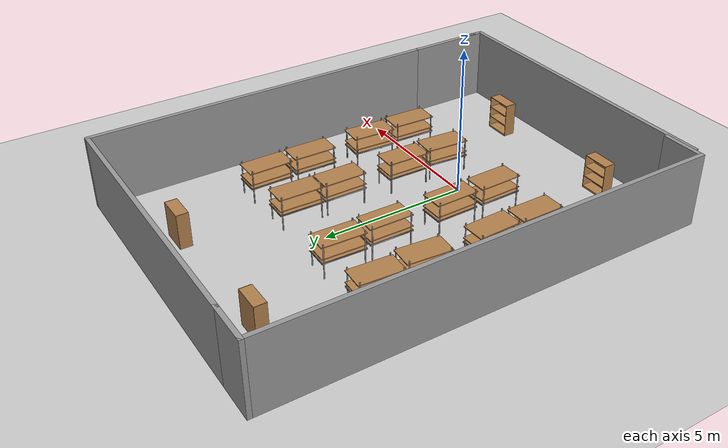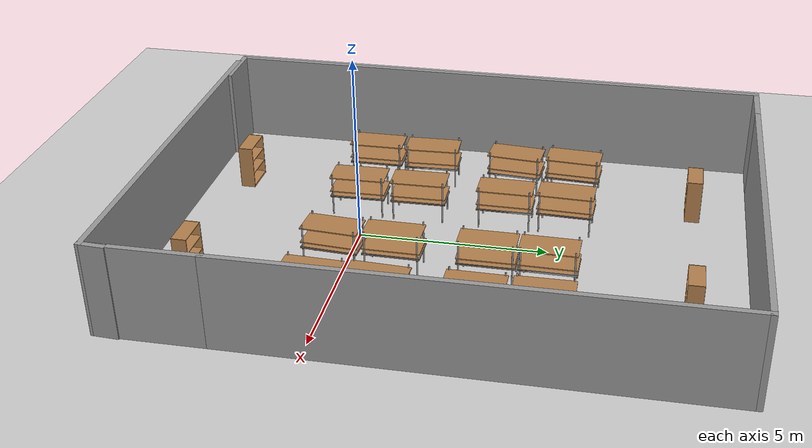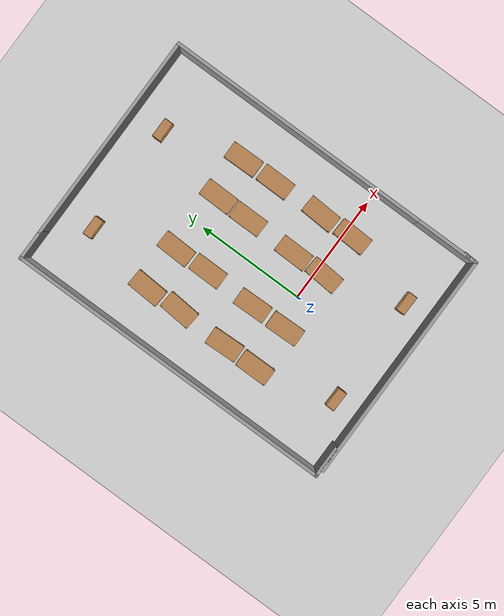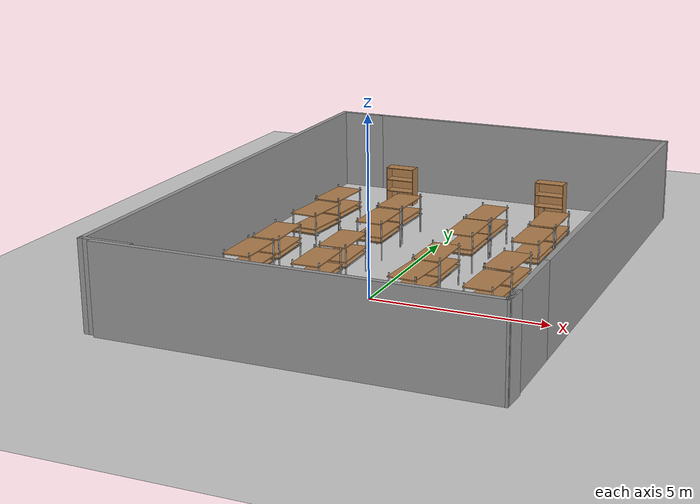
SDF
<sdf version="1.7">
 <world name="default">
  <light name="sun" type="directional">
   <pose>0 0 10 0 -0 0</pose>
   <diffuse>0.8 0.8 0.8 1</diffuse>
   <specular>0.2 0.2 0.2 1</specular>
   <attenuation>
    <range>1000</range>
    <constant>0.9</constant>
    <linear>0.01</linear>
    <quadratic>0.001</quadratic>
   </attenuation>
   <direction>-0.5 0.1 -0.9</direction>
   <spot><inner_angle>0</inner_angle><outer_angle>0</outer_angle><falloff>0</falloff></spot>
  </light>
  <model name="ground_plane">
   <static>1</static>
   <link name="link">
    <collision name="collision">
     <geometry><plane><normal>0 0 1</normal><size>100 100</size></plane></geometry>
     <surface><friction><ode><mu>100</mu><mu2>50</mu2></ode></friction></surface>
    </collision>
    <visual name="visual">
     <cast_shadows>0</cast_shadows>
     <geometry><plane><normal>0 0 1</normal><size>100 100</size></plane></geometry>
     <material>
      <script><uri>file://media/materials/scripts/gazebo.material</uri><name>Gazebo/Grey</name></script>
     </material>
    </visual>
   </link>
  </model>
  <gravity>0 0 -9.8</gravity>
  <magnetic_field>6e-06 2.3e-05 -4.2e-05</magnetic_field>
  <atmosphere type="adiabatic"/>
  <physics type="ode">
   <max_step_size>0.001</max_step_size>
   <real_time_factor>1</real_time_factor>
   <real_time_update_rate>1000</real_time_update_rate>
  </physics>
  <scene><ambient>0.4 0.4 0.4 1</ambient><background>0.7 0.7 0.7 1</background><shadows>1</shadows></scene>
  <audio><device>default</device></audio>
  <spherical_coordinates>
   <surface_model>EARTH_WGS84</surface_model>
   <latitude_deg>0</latitude_deg>
   <longitude_deg>0</longitude_deg>
   <elevation>0</elevation>
   <heading_deg>0</heading_deg>
  </spherical_coordinates>
  <model name="warehouse_pallet">
   <link name="warehouse_pallet::link">
    <pose>0 0 -0 0 -0 1.57</pose>
    <inertial>
     <inertia>
      <ixx>0.0267042</ixx>
      <ixy>0</ixy>
      <ixz>0</ixz>
      <iyy>0.0937875</iyy>
      <iyz>0</iyz>
      <izz>0.120417</izz>
     </inertia>
     <mass>0.5</mass>
    </inertial>
    <visual name="holding1_visual">
     <pose>0 0.39 0.45 0 -0 0</pose>
     <geometry><box><size>1.5 0.02 0.05</size></box></geometry>
     <material>
      <script><uri>file://media/materials/scripts/gazebo.material</uri><name>Gazebo/Grey</name></script>
      <shader type="pixel"><normal_map>__default__</normal_map></shader>
      <ambient>0.3 0.3 0.3 1</ambient>
      <diffuse>0.7 0.7 0.7 1</diffuse>
      <specular>0.01 0.01 0.01 1</specular>
      <emissive>0 0 0 1</emissive>
     </material>
    </visual>
    <visual name="front_left_leg">
     <pose>0.68 0.38 0.5 0 -0 0</pose>
     <geometry><cylinder><radius>0.02</radius><length>1.2</length></cylinder></geometry>
     <material>
      <script><uri>file://media/materials/scripts/gazebo.material</uri><name>Gazebo/Grey</name></script>
      <shader type="pixel"><normal_map>__default__</normal_map></shader>
      <ambient>0.3 0.3 0.3 1</ambient>
      <diffuse>0.7 0.7 0.7 1</diffuse>
      <specular>0.01 0.01 0.01 1</specular>
      <emissive>0 0 0 1</emissive>
     </material>
    </visual>
    <visual name="front_right_leg">
     <pose>0.68 -0.38 0.5 0 -0 0</pose>
     <geometry><cylinder><radius>0.02</radius><length>1.2</length></cylinder></geometry>
     <material>
      <script><uri>file://media/materials/scripts/gazebo.material</uri><name>Gazebo/Grey</name></script>
      <shader type="pixel"><normal_map>__default__</normal_map></shader>
      <ambient>0.3 0.3 0.3 1</ambient>
      <diffuse>0.7 0.7 0.7 1</diffuse>
      <specular>0.01 0.01 0.01 1</specular>
      <emissive>0 0 0 1</emissive>
     </material>
    </visual>
    <visual name="back_right_leg">
     <pose>-0.68 -0.38 0.5 0 -0 0</pose>
     <geometry><cylinder><radius>0.02</radius><length>1.2</length></cylinder></geometry>
     <material>
      <script><uri>file://media/materials/scripts/gazebo.material</uri><name>Gazebo/Grey</name></script>
      <shader type="pixel"><normal_map>__default__</normal_map></shader>
      <ambient>0.3 0.3 0.3 1</ambient>
      <diffuse>0.7 0.7 0.7 1</diffuse>
      <specular>0.01 0.01 0.01 1</specular>
      <emissive>0 0 0 1</emissive>
     </material>
    </visual>
    <visual name="back_left_leg">
     <pose>-0.68 0.38 0.5 0 -0 0</pose>
     <geometry><cylinder><radius>0.02</radius><length>1.2</length></cylinder></geometry>
     <material>
      <script><uri>file://media/materials/scripts/gazebo.material</uri><name>Gazebo/Grey</name></script>
      <shader type="pixel"><normal_map>__default__</normal_map></shader>
      <ambient>0.3 0.3 0.3 1</ambient>
      <diffuse>0.7 0.7 0.7 1</diffuse>
      <specular>0.01 0.01 0.01 1</specular>
      <emissive>0 0 0 1</emissive>
     </material>
    </visual>
    <visual name="visual1">
     <pose>0 0 0.45 0 -0 0</pose>
     <geometry><box><size>1.5 0.8 0.03</size></box></geometry>
     <material>
      <script><uri>file://media/materials/scripts/gazebo.material</uri><name>Gazebo/Wood</name></script>
      <shader type="pixel"><normal_map>__default__</normal_map></shader>
      <ambient>1 1 1 1</ambient>
      <diffuse>1 1 1 1</diffuse>
      <specular>0.2 0.2 0.2 1</specular>
      <emissive>0 0 0 1</emissive>
     </material>
    </visual>
    <visual name="holding2_visual">
     <pose>0 -0.39 0.45 0 -0 0</pose>
     <geometry><box><size>1.5 0.02 0.05</size></box></geometry>
     <material>
      <script><uri>file://media/materials/scripts/gazebo.material</uri><name>Gazebo/Grey</name></script>
      <shader type="pixel"><normal_map>__default__</normal_map></shader>
      <ambient>0.3 0.3 0.3 1</ambient>
      <diffuse>0.7 0.7 0.7 1</diffuse>
      <specular>0.01 0.01 0.01 1</specular>
      <emissive>0 0 0 1</emissive>
     </material>
    </visual>
    <visual name="holding3_visual">
     <pose>0.735 0 0.45 0 -0 1.57</pose>
     <geometry><box><size>0.8 0.02 0.05</size></box></geometry>
     <material>
      <script><uri>file://media/materials/scripts/gazebo.material</uri><name>Gazebo/Grey</name></script>
      <shader type="pixel"><normal_map>__default__</normal_map></shader>
      <ambient>0.3 0.3 0.3 1</ambient>
      <diffuse>0.7 0.7 0.7 1</diffuse>
      <specular>0.01 0.01 0.01 1</specular>
      <emissive>0 0 0 1</emissive>
     </material>
    </visual>
    <visual name="holding4_visual">
     <pose>-0.735 0 0.45 0 -0 1.57</pose>
     <geometry><box><size>0.8 0.02 0.05</size></box></geometry>
     <material>
      <script><uri>file://media/materials/scripts/gazebo.material</uri><name>Gazebo/Grey</name></script>
      <shader type="pixel"><normal_map>__default__</normal_map></shader>
      <ambient>0.3 0.3 0.3 1</ambient>
      <diffuse>0.7 0.7 0.7 1</diffuse>
      <specular>0.01 0.01 0.01 1</specular>
      <emissive>0 0 0 1</emissive>
     </material>
    </visual>
    <visual name="visual2">
     <pose>0 0 0.6 0 -0 0</pose>
     <geometry><box><size>1.5 0.8 0.03</size></box></geometry>
     <material>
      <script><uri>file://media/materials/scripts/gazebo.material</uri><name>Gazebo/Wood</name></script>
      <shader type="pixel"><normal_map>__default__</normal_map></shader>
      <ambient>1 1 1 1</ambient>
      <diffuse>1 1 1 1</diffuse>
      <specular>0.2 0.2 0.2 1</specular>
      <emissive>0 0 0 1</emissive>
     </material>
    </visual>
    <visual name="visual3">
     <pose>0 0 1 0 -0 0</pose>
     <geometry><box><size>1.5 0.8 0.03</size></box></geometry>
     <material>
      <script><uri>file://media/materials/scripts/gazebo.material</uri><name>Gazebo/Wood</name></script>
      <shader type="pixel"><normal_map>__default__</normal_map></shader>
      <ambient>1 1 1 1</ambient>
      <diffuse>1 1 1 1</diffuse>
      <specular>0.2 0.2 0.2 1</specular>
      <emissive>0 0 0 1</emissive>
     </material>
    </visual>
    <collision name="surface1">
     <pose>0 0 0.45 0 -0 0</pose>
     <geometry><box><size>1.5 0.8 0.03</size></box></geometry>
     <surface>
      <friction>
       <ode><mu>20</mu><mu2>20</mu2><fdir1>0 0 0</fdir1><slip1>0</slip1><slip2>0</slip2></ode>
       <torsional>
        <coefficient>1</coefficient>
        <patch_radius>0</patch_radius>
        <surface_radius>0</surface_radius>
        <use_patch_radius>1</use_patch_radius>
        <ode><slip>0</slip></ode>
       </torsional>
      </friction>
      <bounce><restitution_coefficient>0</restitution_coefficient><threshold>1e+06</threshold></bounce>
      <contact>
       <collide_without_contact>0</collide_without_contact>
       <collide_without_contact_bitmask>1</collide_without_contact_bitmask>
       <collide_bitmask>1</collide_bitmask>
       <ode>
        <soft_cfm>0</soft_cfm>
        <soft_erp>0.2</soft_erp>
        <kp>1e+13</kp>
        <kd>1</kd>
        <max_vel>0.01</max_vel>
        <min_depth>0</min_depth>
       </ode>
       <bullet>
        <split_impulse>1</split_impulse>
        <split_impulse_penetration_threshold>-0.01</split_impulse_penetration_threshold>
        <soft_cfm>0</soft_cfm>
        <soft_erp>0.2</soft_erp>
        <kp>1e+13</kp>
        <kd>1</kd>
       </bullet>
      </contact>
     </surface>
    </collision>
    <collision name="holding1_collision">
     <pose>0 0.39 0.45 0 -0 0</pose>
     <geometry><box><size>1.5 0.02 0.05</size></box></geometry>
     <surface>
      <friction>
       <ode><mu>1e+09</mu><mu2>1e+09</mu2><fdir1>0 0 0</fdir1><slip1>0</slip1><slip2>0</slip2></ode>
       <torsional>
        <coefficient>1</coefficient>
        <patch_radius>0</patch_radius>
        <surface_radius>0</surface_radius>
        <use_patch_radius>1</use_patch_radius>
        <ode><slip>0</slip></ode>
       </torsional>
      </friction>
      <bounce><restitution_coefficient>0</restitution_coefficient><threshold>1e+06</threshold></bounce>
      <contact>
       <collide_without_contact>0</collide_without_contact>
       <collide_without_contact_bitmask>1</collide_without_contact_bitmask>
       <collide_bitmask>1</collide_bitmask>
       <ode>
        <soft_cfm>0</soft_cfm>
        <soft_erp>0.2</soft_erp>
        <kp>1e+13</kp>
        <kd>1</kd>
        <max_vel>0.01</max_vel>
        <min_depth>0</min_depth>
       </ode>
       <bullet>
        <split_impulse>1</split_impulse>
        <split_impulse_penetration_threshold>-0.01</split_impulse_penetration_threshold>
        <soft_cfm>0</soft_cfm>
        <soft_erp>0.2</soft_erp>
        <kp>1e+13</kp>
        <kd>1</kd>
       </bullet>
      </contact>
     </surface>
    </collision>
    <collision name="holding2_collision">
     <pose>0 -0.39 0.45 0 -0 0</pose>
     <geometry><box><size>1.5 0.02 0.05</size></box></geometry>
     <surface>
      <friction>
       <ode><mu>1e+09</mu><mu2>1e+09</mu2><fdir1>0 0 0</fdir1><slip1>0</slip1><slip2>0</slip2></ode>
       <torsional>
        <coefficient>1</coefficient>
        <patch_radius>0</patch_radius>
        <surface_radius>0</surface_radius>
        <use_patch_radius>1</use_patch_radius>
        <ode><slip>0</slip></ode>
       </torsional>
      </friction>
      <bounce><restitution_coefficient>0</restitution_coefficient><threshold>1e+06</threshold></bounce>
      <contact>
       <collide_without_contact>0</collide_without_contact>
       <collide_without_contact_bitmask>1</collide_without_contact_bitmask>
       <collide_bitmask>1</collide_bitmask>
       <ode>
        <soft_cfm>0</soft_cfm>
        <soft_erp>0.2</soft_erp>
        <kp>1e+13</kp>
        <kd>1</kd>
        <max_vel>0.01</max_vel>
        <min_depth>0</min_depth>
       </ode>
       <bullet>
        <split_impulse>1</split_impulse>
        <split_impulse_penetration_threshold>-0.01</split_impulse_penetration_threshold>
        <soft_cfm>0</soft_cfm>
        <soft_erp>0.2</soft_erp>
        <kp>1e+13</kp>
        <kd>1</kd>
       </bullet>
      </contact>
     </surface>
    </collision>
    <collision name="holding3_collision">
     <pose>0.735 0 0.45 0 -0 1.57</pose>
     <geometry><box><size>0.8 0.02 0.05</size></box></geometry>
     <surface>
      <friction>
       <ode><mu>1e+09</mu><mu2>1e+09</mu2><fdir1>0 0 0</fdir1><slip1>0</slip1><slip2>0</slip2></ode>
       <torsional>
        <coefficient>1</coefficient>
        <patch_radius>0</patch_radius>
        <surface_radius>0</surface_radius>
        <use_patch_radius>1</use_patch_radius>
        <ode><slip>0</slip></ode>
       </torsional>
      </friction>
      <bounce><restitution_coefficient>0</restitution_coefficient><threshold>1e+06</threshold></bounce>
      <contact>
       <collide_without_contact>0</collide_without_contact>
       <collide_without_contact_bitmask>1</collide_without_contact_bitmask>
       <collide_bitmask>1</collide_bitmask>
       <ode>
        <soft_cfm>0</soft_cfm>
        <soft_erp>0.2</soft_erp>
        <kp>1e+13</kp>
        <kd>1</kd>
        <max_vel>0.01</max_vel>
        <min_depth>0</min_depth>
       </ode>
       <bullet>
        <split_impulse>1</split_impulse>
        <split_impulse_penetration_threshold>-0.01</split_impulse_penetration_threshold>
        <soft_cfm>0</soft_cfm>
        <soft_erp>0.2</soft_erp>
        <kp>1e+13</kp>
        <kd>1</kd>
       </bullet>
      </contact>
     </surface>
    </collision>
    <collision name="holding4_collision">
     <pose>-0.735 0 0.45 0 -0 1.57</pose>
     <geometry><box><size>0.8 0.02 0.05</size></box></geometry>
     <surface>
      <friction>
       <ode><mu>1e+09</mu><mu2>1e+09</mu2><fdir1>0 0 0</fdir1><slip1>0</slip1><slip2>0</slip2></ode>
       <torsional>
        <coefficient>1</coefficient>
        <patch_radius>0</patch_radius>
        <surface_radius>0</surface_radius>
        <use_patch_radius>1</use_patch_radius>
        <ode><slip>0</slip></ode>
       </torsional>
      </friction>
      <bounce><restitution_coefficient>0</restitution_coefficient><threshold>1e+06</threshold></bounce>
      <contact>
       <collide_without_contact>0</collide_without_contact>
       <collide_without_contact_bitmask>1</collide_without_contact_bitmask>
       <collide_bitmask>1</collide_bitmask>
       <ode>
        <soft_cfm>0</soft_cfm>
        <soft_erp>0.2</soft_erp>
        <kp>1e+13</kp>
        <kd>1</kd>
        <max_vel>0.01</max_vel>
        <min_depth>0</min_depth>
       </ode>
       <bullet>
        <split_impulse>1</split_impulse>
        <split_impulse_penetration_threshold>-0.01</split_impulse_penetration_threshold>
        <soft_cfm>0</soft_cfm>
        <soft_erp>0.2</soft_erp>
        <kp>1e+13</kp>
        <kd>1</kd>
       </bullet>
      </contact>
     </surface>
    </collision>
    <collision name="surface3">
     <pose>0 0 1 0 -0 0</pose>
     <geometry><box><size>1.5 0.8 0.03</size></box></geometry>
     <surface>
      <friction>
       <ode><mu>2.5</mu><mu2>2.5</mu2><fdir1>0 0 0</fdir1><slip1>0</slip1><slip2>0</slip2></ode>
       <torsional>
        <coefficient>1</coefficient>
        <patch_radius>0</patch_radius>
        <surface_radius>0</surface_radius>
        <use_patch_radius>1</use_patch_radius>
        <ode><slip>0</slip></ode>
       </torsional>
      </friction>
      <bounce><restitution_coefficient>0</restitution_coefficient><threshold>1e+06</threshold></bounce>
      <contact>
       <collide_without_contact>0</collide_without_contact>
       <collide_without_contact_bitmask>1</collide_without_contact_bitmask>
       <collide_bitmask>1</collide_bitmask>
       <ode>
        <soft_cfm>0</soft_cfm>
        <soft_erp>0.2</soft_erp>
        <kp>1e+13</kp>
        <kd>1</kd>
        <max_vel>0.01</max_vel>
        <min_depth>0</min_depth>
       </ode>
       <bullet>
        <split_impulse>1</split_impulse>
        <split_impulse_penetration_threshold>-0.01</split_impulse_penetration_threshold>
        <soft_cfm>0</soft_cfm>
        <soft_erp>0.2</soft_erp>
        <kp>1e+13</kp>
        <kd>1</kd>
       </bullet>
      </contact>
     </surface>
    </collision>
    <collision name="surface2">
     <pose>0 0 0.6 0 -0 0</pose>
     <geometry><box><size>1.5 0.8 0.03</size></box></geometry>
     <surface>
      <friction>
       <ode><mu>2.5</mu><mu2>2.5</mu2><fdir1>0 0 0</fdir1><slip1>0</slip1><slip2>0</slip2></ode>
       <torsional>
        <coefficient>1</coefficient>
        <patch_radius>0</patch_radius>
        <surface_radius>0</surface_radius>
        <use_patch_radius>1</use_patch_radius>
        <ode><slip>0</slip></ode>
       </torsional>
      </friction>
      <bounce><restitution_coefficient>0</restitution_coefficient><threshold>1e+06</threshold></bounce>
      <contact>
       <collide_without_contact>0</collide_without_contact>
       <collide_without_contact_bitmask>1</collide_without_contact_bitmask>
       <collide_bitmask>1</collide_bitmask>
       <ode>
        <soft_cfm>0</soft_cfm>
        <soft_erp>0.2</soft_erp>
        <kp>1e+13</kp>
        <kd>1</kd>
        <max_vel>0.01</max_vel>
        <min_depth>0</min_depth>
       </ode>
       <bullet>
        <split_impulse>1</split_impulse>
        <split_impulse_penetration_threshold>-0.01</split_impulse_penetration_threshold>
        <soft_cfm>0</soft_cfm>
        <soft_erp>0.2</soft_erp>
        <kp>1e+13</kp>
        <kd>1</kd>
       </bullet>
      </contact>
     </surface>
    </collision>
    <collision name="front_right_leg">
     <pose>0.68 -0.38 0.5 0 -0 0</pose>
     <geometry><cylinder><radius>0.02</radius><length>1</length></cylinder></geometry>
     <surface>
      <friction>
       <ode><mu>1</mu><mu2>1.2</mu2><fdir1>0 0 0</fdir1><slip1>0</slip1><slip2>0</slip2></ode>
       <torsional>
        <coefficient>1</coefficient>
        <patch_radius>0</patch_radius>
        <surface_radius>0</surface_radius>
        <use_patch_radius>1</use_patch_radius>
        <ode><slip>0</slip></ode>
       </torsional>
      </friction>
      <bounce><restitution_coefficient>0</restitution_coefficient><threshold>1e+06</threshold></bounce>
      <contact>
       <collide_without_contact>0</collide_without_contact>
       <collide_without_contact_bitmask>1</collide_without_contact_bitmask>
       <collide_bitmask>1</collide_bitmask>
       <ode>
        <soft_cfm>0</soft_cfm>
        <soft_erp>0.2</soft_erp>
        <kp>1e+13</kp>
        <kd>1</kd>
        <max_vel>0.01</max_vel>
        <min_depth>0</min_depth>
       </ode>
       <bullet>
        <split_impulse>1</split_impulse>
        <split_impulse_penetration_threshold>-0.01</split_impulse_penetration_threshold>
        <soft_cfm>0</soft_cfm>
        <soft_erp>0.2</soft_erp>
        <kp>1e+13</kp>
        <kd>1</kd>
       </bullet>
      </contact>
     </surface>
    </collision>
    <collision name="back_right_leg">
     <pose>-0.68 -0.38 0.5 0 -0 0</pose>
     <geometry><cylinder><radius>0.02</radius><length>1.2</length></cylinder></geometry>
     <surface>
      <friction>
       <ode><mu>1</mu><mu2>1</mu2><fdir1>0 0 0</fdir1><slip1>0</slip1><slip2>0</slip2></ode>
       <torsional>
        <coefficient>1</coefficient>
        <patch_radius>0</patch_radius>
        <surface_radius>0</surface_radius>
        <use_patch_radius>1</use_patch_radius>
        <ode><slip>0</slip></ode>
       </torsional>
      </friction>
      <bounce><restitution_coefficient>0</restitution_coefficient><threshold>1e+06</threshold></bounce>
      <contact>
       <collide_without_contact>0</collide_without_contact>
       <collide_without_contact_bitmask>1</collide_without_contact_bitmask>
       <collide_bitmask>1</collide_bitmask>
       <ode>
        <soft_cfm>0</soft_cfm>
        <soft_erp>0.2</soft_erp>
        <kp>1e+13</kp>
        <kd>1</kd>
        <max_vel>0.01</max_vel>
        <min_depth>0</min_depth>
       </ode>
       <bullet>
        <split_impulse>1</split_impulse>
        <split_impulse_penetration_threshold>-0.01</split_impulse_penetration_threshold>
        <soft_cfm>0</soft_cfm>
        <soft_erp>0.2</soft_erp>
        <kp>1e+13</kp>
        <kd>1</kd>
       </bullet>
      </contact>
     </surface>
    </collision>
    <collision name="front_left_leg">
     <pose>0.68 0.38 0.5 0 -0 0</pose>
     <geometry><cylinder><radius>0.02</radius><length>1.2</length></cylinder></geometry>
     <surface>
      <friction>
       <ode><mu>1</mu><mu2>1</mu2><fdir1>0 0 0</fdir1><slip1>0</slip1><slip2>0</slip2></ode>
       <torsional>
        <coefficient>1</coefficient>
        <patch_radius>0</patch_radius>
        <surface_radius>0</surface_radius>
        <use_patch_radius>1</use_patch_radius>
        <ode><slip>0</slip></ode>
       </torsional>
      </friction>
      <bounce><restitution_coefficient>0</restitution_coefficient><threshold>1e+06</threshold></bounce>
      <contact>
       <collide_without_contact>0</collide_without_contact>
       <collide_without_contact_bitmask>1</collide_without_contact_bitmask>
       <collide_bitmask>1</collide_bitmask>
       <ode>
        <soft_cfm>0</soft_cfm>
        <soft_erp>0.2</soft_erp>
        <kp>1e+13</kp>
        <kd>1</kd>
        <max_vel>0.01</max_vel>
        <min_depth>0</min_depth>
       </ode>
       <bullet>
        <split_impulse>1</split_impulse>
        <split_impulse_penetration_threshold>-0.01</split_impulse_penetration_threshold>
        <soft_cfm>0</soft_cfm>
        <soft_erp>0.2</soft_erp>
        <kp>1e+13</kp>
        <kd>1</kd>
       </bullet>
      </contact>
     </surface>
    </collision>
    <collision name="back_left_leg">
     <pose>-0.68 0.38 0.5 0 -0 0</pose>
     <geometry><cylinder><radius>0.02</radius><length>1.2</length></cylinder></geometry>
     <surface>
      <friction>
       <ode><mu>1</mu><mu2>1</mu2><fdir1>0 0 0</fdir1><slip1>0</slip1><slip2>0</slip2></ode>
       <torsional>
        <coefficient>1</coefficient>
        <patch_radius>0</patch_radius>
        <surface_radius>0</surface_radius>
        <use_patch_radius>1</use_patch_radius>
        <ode><slip>0</slip></ode>
       </torsional>
      </friction>
      <bounce><restitution_coefficient>0</restitution_coefficient><threshold>1e+06</threshold></bounce>
      <contact>
       <collide_without_contact>0</collide_without_contact>
       <collide_without_contact_bitmask>1</collide_without_contact_bitmask>
       <collide_bitmask>1</collide_bitmask>
       <ode>
        <soft_cfm>0</soft_cfm>
        <soft_erp>0.2</soft_erp>
        <kp>1e+13</kp>
        <kd>1</kd>
        <max_vel>0.01</max_vel>
        <min_depth>0</min_depth>
       </ode>
       <bullet>
        <split_impulse>1</split_impulse>
        <split_impulse_penetration_threshold>-0.01</split_impulse_penetration_threshold>
        <soft_cfm>0</soft_cfm>
        <soft_erp>0.2</soft_erp>
        <kp>1e+13</kp>
        <kd>1</kd>
       </bullet>
      </contact>
     </surface>
    </collision>
   </link>
   <static>0</static>
   <pose>-3.42613 -0.286099 0.099991 -7e-06 1.4e-05 0.003434</pose>
  </model>
  <model name="warehouse_pallet_clone">
   <link name="warehouse_pallet::link">
    <pose>0 0 -0 0 -0 1.57</pose>
    <inertial>
     <inertia>
      <ixx>0.0267042</ixx>
      <ixy>0</ixy>
      <ixz>0</ixz>
      <iyy>0.0937875</iyy>
      <iyz>0</iyz>
      <izz>0.120417</izz>
     </inertia>
     <mass>0.5</mass>
    </inertial>
    <visual name="holding1_visual">
     <pose>0 0.39 0.45 0 -0 0</pose>
     <geometry><box><size>1.5 0.02 0.05</size></box></geometry>
     <material>
      <script><uri>file://media/materials/scripts/gazebo.material</uri><name>Gazebo/Grey</name></script>
      <shader type="pixel"><normal_map>__default__</normal_map></shader>
      <ambient>0.3 0.3 0.3 1</ambient>
      <diffuse>0.7 0.7 0.7 1</diffuse>
      <specular>0.01 0.01 0.01 1</specular>
      <emissive>0 0 0 1</emissive>
     </material>
    </visual>
    <visual name="front_left_leg">
     <pose>0.68 0.38 0.5 0 -0 0</pose>
     <geometry><cylinder><radius>0.02</radius><length>1.2</length></cylinder></geometry>
     <material>
      <script><uri>file://media/materials/scripts/gazebo.material</uri><name>Gazebo/Grey</name></script>
      <shader type="pixel"><normal_map>__default__</normal_map></shader>
      <ambient>0.3 0.3 0.3 1</ambient>
      <diffuse>0.7 0.7 0.7 1</diffuse>
      <specular>0.01 0.01 0.01 1</specular>
      <emissive>0 0 0 1</emissive>
     </material>
    </visual>
    <visual name="front_right_leg">
     <pose>0.68 -0.38 0.5 0 -0 0</pose>
     <geometry><cylinder><radius>0.02</radius><length>1.2</length></cylinder></geometry>
     <material>
      <script><uri>file://media/materials/scripts/gazebo.material</uri><name>Gazebo/Grey</name></script>
      <shader type="pixel"><normal_map>__default__</normal_map></shader>
      <ambient>0.3 0.3 0.3 1</ambient>
      <diffuse>0.7 0.7 0.7 1</diffuse>
      <specular>0.01 0.01 0.01 1</specular>
      <emissive>0 0 0 1</emissive>
     </material>
    </visual>
    <visual name="back_right_leg">
     <pose>-0.68 -0.38 0.5 0 -0 0</pose>
     <geometry><cylinder><radius>0.02</radius><length>1.2</length></cylinder></geometry>
     <material>
      <script><uri>file://media/materials/scripts/gazebo.material</uri><name>Gazebo/Grey</name></script>
      <shader type="pixel"><normal_map>__default__</normal_map></shader>
      <ambient>0.3 0.3 0.3 1</ambient>
      <diffuse>0.7 0.7 0.7 1</diffuse>
      <specular>0.01 0.01 0.01 1</specular>
      <emissive>0 0 0 1</emissive>
     </material>
    </visual>
    <visual name="back_left_leg">
     <pose>-0.68 0.38 0.5 0 -0 0</pose>
     <geometry><cylinder><radius>0.02</radius><length>1.2</length></cylinder></geometry>
     <material>
      <script><uri>file://media/materials/scripts/gazebo.material</uri><name>Gazebo/Grey</name></script>
      <shader type="pixel"><normal_map>__default__</normal_map></shader>
      <ambient>0.3 0.3 0.3 1</ambient>
      <diffuse>0.7 0.7 0.7 1</diffuse>
      <specular>0.01 0.01 0.01 1</specular>
      <emissive>0 0 0 1</emissive>
     </material>
    </visual>
    <visual name="visual1">
     <pose>0 0 0.45 0 -0 0</pose>
     <geometry><box><size>1.5 0.8 0.03</size></box></geometry>
     <material>
      <script><uri>file://media/materials/scripts/gazebo.material</uri><name>Gazebo/Wood</name></script>
      <shader type="pixel"><normal_map>__default__</normal_map></shader>
      <ambient>1 1 1 1</ambient>
      <diffuse>1 1 1 1</diffuse>
      <specular>0.2 0.2 0.2 1</specular>
      <emissive>0 0 0 1</emissive>
     </material>
    </visual>
    <visual name="holding2_visual">
     <pose>0 -0.39 0.45 0 -0 0</pose>
     <geometry><box><size>1.5 0.02 0.05</size></box></geometry>
     <material>
      <script><uri>file://media/materials/scripts/gazebo.material</uri><name>Gazebo/Grey</name></script>
      <shader type="pixel"><normal_map>__default__</normal_map></shader>
      <ambient>0.3 0.3 0.3 1</ambient>
      <diffuse>0.7 0.7 0.7 1</diffuse>
      <specular>0.01 0.01 0.01 1</specular>
      <emissive>0 0 0 1</emissive>
     </material>
    </visual>
    <visual name="holding3_visual">
     <pose>0.735 0 0.45 0 -0 1.57</pose>
     <geometry><box><size>0.8 0.02 0.05</size></box></geometry>
     <material>
      <script><uri>file://media/materials/scripts/gazebo.material</uri><name>Gazebo/Grey</name></script>
      <shader type="pixel"><normal_map>__default__</normal_map></shader>
      <ambient>0.3 0.3 0.3 1</ambient>
      <diffuse>0.7 0.7 0.7 1</diffuse>
      <specular>0.01 0.01 0.01 1</specular>
      <emissive>0 0 0 1</emissive>
     </material>
    </visual>
    <visual name="holding4_visual">
     <pose>-0.735 0 0.45 0 -0 1.57</pose>
     <geometry><box><size>0.8 0.02 0.05</size></box></geometry>
     <material>
      <script><uri>file://media/materials/scripts/gazebo.material</uri><name>Gazebo/Grey</name></script>
      <shader type="pixel"><normal_map>__default__</normal_map></shader>
      <ambient>0.3 0.3 0.3 1</ambient>
      <diffuse>0.7 0.7 0.7 1</diffuse>
      <specular>0.01 0.01 0.01 1</specular>
      <emissive>0 0 0 1</emissive>
     </material>
    </visual>
    <visual name="visual2">
     <pose>0 0 0.6 0 -0 0</pose>
     <geometry><box><size>1.5 0.8 0.03</size></box></geometry>
     <material>
      <script><uri>file://media/materials/scripts/gazebo.material</uri><name>Gazebo/Wood</name></script>
      <shader type="pixel"><normal_map>__default__</normal_map></shader>
      <ambient>1 1 1 1</ambient>
      <diffuse>1 1 1 1</diffuse>
      <specular>0.2 0.2 0.2 1</specular>
      <emissive>0 0 0 1</emissive>
     </material>
    </visual>
    <visual name="visual3">
     <pose>0 0 1 0 -0 0</pose>
     <geometry><box><size>1.5 0.8 0.03</size></box></geometry>
     <material>
      <script><uri>file://media/materials/scripts/gazebo.material</uri><name>Gazebo/Wood</name></script>
      <shader type="pixel"><normal_map>__default__</normal_map></shader>
      <ambient>1 1 1 1</ambient>
      <diffuse>1 1 1 1</diffuse>
      <specular>0.2 0.2 0.2 1</specular>
      <emissive>0 0 0 1</emissive>
     </material>
    </visual>
    <collision name="surface1">
     <pose>0 0 0.45 0 -0 0</pose>
     <geometry><box><size>1.5 0.8 0.03</size></box></geometry>
     <surface>
      <friction>
       <ode><mu>20</mu><mu2>20</mu2><fdir1>0 0 0</fdir1><slip1>0</slip1><slip2>0</slip2></ode>
       <torsional>
        <coefficient>1</coefficient>
        <patch_radius>0</patch_radius>
        <surface_radius>0</surface_radius>
        <use_patch_radius>1</use_patch_radius>
        <ode><slip>0</slip></ode>
       </torsional>
      </friction>
      <bounce><restitution_coefficient>0</restitution_coefficient><threshold>1e+06</threshold></bounce>
      <contact>
       <collide_without_contact>0</collide_without_contact>
       <collide_without_contact_bitmask>1</collide_without_contact_bitmask>
       <collide_bitmask>1</collide_bitmask>
       <ode>
        <soft_cfm>0</soft_cfm>
        <soft_erp>0.2</soft_erp>
        <kp>1e+13</kp>
        <kd>1</kd>
        <max_vel>0.01</max_vel>
        <min_depth>0</min_depth>
       </ode>
       <bullet>
        <split_impulse>1</split_impulse>
        <split_impulse_penetration_threshold>-0.01</split_impulse_penetration_threshold>
        <soft_cfm>0</soft_cfm>
        <soft_erp>0.2</soft_erp>
        <kp>1e+13</kp>
        <kd>1</kd>
       </bullet>
      </contact>
     </surface>
    </collision>
    <collision name="holding1_collision">
     <pose>0 0.39 0.45 0 -0 0</pose>
     <geometry><box><size>1.5 0.02 0.05</size></box></geometry>
     <surface>
      <friction>
       <ode><mu>1e+09</mu><mu2>1e+09</mu2><fdir1>0 0 0</fdir1><slip1>0</slip1><slip2>0</slip2></ode>
       <torsional>
        <coefficient>1</coefficient>
        <patch_radius>0</patch_radius>
        <surface_radius>0</surface_radius>
        <use_patch_radius>1</use_patch_radius>
        <ode><slip>0</slip></ode>
       </torsional>
      </friction>
      <bounce><restitution_coefficient>0</restitution_coefficient><threshold>1e+06</threshold></bounce>
      <contact>
       <collide_without_contact>0</collide_without_contact>
       <collide_without_contact_bitmask>1</collide_without_contact_bitmask>
       <collide_bitmask>1</collide_bitmask>
       <ode>
        <soft_cfm>0</soft_cfm>
        <soft_erp>0.2</soft_erp>
        <kp>1e+13</kp>
        <kd>1</kd>
        <max_vel>0.01</max_vel>
        <min_depth>0</min_depth>
       </ode>
       <bullet>
        <split_impulse>1</split_impulse>
        <split_impulse_penetration_threshold>-0.01</split_impulse_penetration_threshold>
        <soft_cfm>0</soft_cfm>
        <soft_erp>0.2</soft_erp>
        <kp>1e+13</kp>
        <kd>1</kd>
       </bullet>
      </contact>
     </surface>
    </collision>
    <collision name="holding2_collision">
     <pose>0 -0.39 0.45 0 -0 0</pose>
     <geometry><box><size>1.5 0.02 0.05</size></box></geometry>
     <surface>
      <friction>
       <ode><mu>1e+09</mu><mu2>1e+09</mu2><fdir1>0 0 0</fdir1><slip1>0</slip1><slip2>0</slip2></ode>
       <torsional>
        <coefficient>1</coefficient>
        <patch_radius>0</patch_radius>
        <surface_radius>0</surface_radius>
        <use_patch_radius>1</use_patch_radius>
        <ode><slip>0</slip></ode>
       </torsional>
      </friction>
      <bounce><restitution_coefficient>0</restitution_coefficient><threshold>1e+06</threshold></bounce>
      <contact>
       <collide_without_contact>0</collide_without_contact>
       <collide_without_contact_bitmask>1</collide_without_contact_bitmask>
       <collide_bitmask>1</collide_bitmask>
       <ode>
        <soft_cfm>0</soft_cfm>
        <soft_erp>0.2</soft_erp>
        <kp>1e+13</kp>
        <kd>1</kd>
        <max_vel>0.01</max_vel>
        <min_depth>0</min_depth>
       </ode>
       <bullet>
        <split_impulse>1</split_impulse>
        <split_impulse_penetration_threshold>-0.01</split_impulse_penetration_threshold>
        <soft_cfm>0</soft_cfm>
        <soft_erp>0.2</soft_erp>
        <kp>1e+13</kp>
        <kd>1</kd>
       </bullet>
      </contact>
     </surface>
    </collision>
    <collision name="holding3_collision">
     <pose>0.735 0 0.45 0 -0 1.57</pose>
     <geometry><box><size>0.8 0.02 0.05</size></box></geometry>
     <surface>
      <friction>
       <ode><mu>1e+09</mu><mu2>1e+09</mu2><fdir1>0 0 0</fdir1><slip1>0</slip1><slip2>0</slip2></ode>
       <torsional>
        <coefficient>1</coefficient>
        <patch_radius>0</patch_radius>
        <surface_radius>0</surface_radius>
        <use_patch_radius>1</use_patch_radius>
        <ode><slip>0</slip></ode>
       </torsional>
      </friction>
      <bounce><restitution_coefficient>0</restitution_coefficient><threshold>1e+06</threshold></bounce>
      <contact>
       <collide_without_contact>0</collide_without_contact>
       <collide_without_contact_bitmask>1</collide_without_contact_bitmask>
       <collide_bitmask>1</collide_bitmask>
       <ode>
        <soft_cfm>0</soft_cfm>
        <soft_erp>0.2</soft_erp>
        <kp>1e+13</kp>
        <kd>1</kd>
        <max_vel>0.01</max_vel>
        <min_depth>0</min_depth>
       </ode>
       <bullet>
        <split_impulse>1</split_impulse>
        <split_impulse_penetration_threshold>-0.01</split_impulse_penetration_threshold>
        <soft_cfm>0</soft_cfm>
        <soft_erp>0.2</soft_erp>
        <kp>1e+13</kp>
        <kd>1</kd>
       </bullet>
      </contact>
     </surface>
    </collision>
    <collision name="holding4_collision">
     <pose>-0.735 0 0.45 0 -0 1.57</pose>
     <geometry><box><size>0.8 0.02 0.05</size></box></geometry>
     <surface>
      <friction>
       <ode><mu>1e+09</mu><mu2>1e+09</mu2><fdir1>0 0 0</fdir1><slip1>0</slip1><slip2>0</slip2></ode>
       <torsional>
        <coefficient>1</coefficient>
        <patch_radius>0</patch_radius>
        <surface_radius>0</surface_radius>
        <use_patch_radius>1</use_patch_radius>
        <ode><slip>0</slip></ode>
       </torsional>
      </friction>
      <bounce><restitution_coefficient>0</restitution_coefficient><threshold>1e+06</threshold></bounce>
      <contact>
       <collide_without_contact>0</collide_without_contact>
       <collide_without_contact_bitmask>1</collide_without_contact_bitmask>
       <collide_bitmask>1</collide_bitmask>
       <ode>
        <soft_cfm>0</soft_cfm>
        <soft_erp>0.2</soft_erp>
        <kp>1e+13</kp>
        <kd>1</kd>
        <max_vel>0.01</max_vel>
        <min_depth>0</min_depth>
       </ode>
       <bullet>
        <split_impulse>1</split_impulse>
        <split_impulse_penetration_threshold>-0.01</split_impulse_penetration_threshold>
        <soft_cfm>0</soft_cfm>
        <soft_erp>0.2</soft_erp>
        <kp>1e+13</kp>
        <kd>1</kd>
       </bullet>
      </contact>
     </surface>
    </collision>
    <collision name="surface3">
     <pose>0 0 1 0 -0 0</pose>
     <geometry><box><size>1.5 0.8 0.03</size></box></geometry>
     <surface>
      <friction>
       <ode><mu>2.5</mu><mu2>2.5</mu2><fdir1>0 0 0</fdir1><slip1>0</slip1><slip2>0</slip2></ode>
       <torsional>
        <coefficient>1</coefficient>
        <patch_radius>0</patch_radius>
        <surface_radius>0</surface_radius>
        <use_patch_radius>1</use_patch_radius>
        <ode><slip>0</slip></ode>
       </torsional>
      </friction>
      <bounce><restitution_coefficient>0</restitution_coefficient><threshold>1e+06</threshold></bounce>
      <contact>
       <collide_without_contact>0</collide_without_contact>
       <collide_without_contact_bitmask>1</collide_without_contact_bitmask>
       <collide_bitmask>1</collide_bitmask>
       <ode>
        <soft_cfm>0</soft_cfm>
        <soft_erp>0.2</soft_erp>
        <kp>1e+13</kp>
        <kd>1</kd>
        <max_vel>0.01</max_vel>
        <min_depth>0</min_depth>
       </ode>
       <bullet>
        <split_impulse>1</split_impulse>
        <split_impulse_penetration_threshold>-0.01</split_impulse_penetration_threshold>
        <soft_cfm>0</soft_cfm>
        <soft_erp>0.2</soft_erp>
        <kp>1e+13</kp>
        <kd>1</kd>
       </bullet>
      </contact>
     </surface>
    </collision>
    <collision name="surface2">
     <pose>0 0 0.6 0 -0 0</pose>
     <geometry><box><size>1.5 0.8 0.03</size></box></geometry>
     <surface>
      <friction>
       <ode><mu>2.5</mu><mu2>2.5</mu2><fdir1>0 0 0</fdir1><slip1>0</slip1><slip2>0</slip2></ode>
       <torsional>
        <coefficient>1</coefficient>
        <patch_radius>0</patch_radius>
        <surface_radius>0</surface_radius>
        <use_patch_radius>1</use_patch_radius>
        <ode><slip>0</slip></ode>
       </torsional>
      </friction>
      <bounce><restitution_coefficient>0</restitution_coefficient><threshold>1e+06</threshold></bounce>
      <contact>
       <collide_without_contact>0</collide_without_contact>
       <collide_without_contact_bitmask>1</collide_without_contact_bitmask>
       <collide_bitmask>1</collide_bitmask>
       <ode>
        <soft_cfm>0</soft_cfm>
        <soft_erp>0.2</soft_erp>
        <kp>1e+13</kp>
        <kd>1</kd>
        <max_vel>0.01</max_vel>
        <min_depth>0</min_depth>
       </ode>
       <bullet>
        <split_impulse>1</split_impulse>
        <split_impulse_penetration_threshold>-0.01</split_impulse_penetration_threshold>
        <soft_cfm>0</soft_cfm>
        <soft_erp>0.2</soft_erp>
        <kp>1e+13</kp>
        <kd>1</kd>
       </bullet>
      </contact>
     </surface>
    </collision>
    <collision name="front_right_leg">
     <pose>0.68 -0.38 0.5 0 -0 0</pose>
     <geometry><cylinder><radius>0.02</radius><length>1</length></cylinder></geometry>
     <surface>
      <friction>
       <ode><mu>1</mu><mu2>1.2</mu2><fdir1>0 0 0</fdir1><slip1>0</slip1><slip2>0</slip2></ode>
       <torsional>
        <coefficient>1</coefficient>
        <patch_radius>0</patch_radius>
        <surface_radius>0</surface_radius>
        <use_patch_radius>1</use_patch_radius>
        <ode><slip>0</slip></ode>
       </torsional>
      </friction>
      <bounce><restitution_coefficient>0</restitution_coefficient><threshold>1e+06</threshold></bounce>
      <contact>
       <collide_without_contact>0</collide_without_contact>
       <collide_without_contact_bitmask>1</collide_without_contact_bitmask>
       <collide_bitmask>1</collide_bitmask>
       <ode>
        <soft_cfm>0</soft_cfm>
        <soft_erp>0.2</soft_erp>
        <kp>1e+13</kp>
        <kd>1</kd>
        <max_vel>0.01</max_vel>
        <min_depth>0</min_depth>
       </ode>
       <bullet>
        <split_impulse>1</split_impulse>
        <split_impulse_penetration_threshold>-0.01</split_impulse_penetration_threshold>
        <soft_cfm>0</soft_cfm>
        <soft_erp>0.2</soft_erp>
        <kp>1e+13</kp>
        <kd>1</kd>
       </bullet>
      </contact>
     </surface>
    </collision>
    <collision name="back_right_leg">
     <pose>-0.68 -0.38 0.5 0 -0 0</pose>
     <geometry><cylinder><radius>0.02</radius><length>1.2</length></cylinder></geometry>
     <surface>
      <friction>
       <ode><mu>1</mu><mu2>1</mu2><fdir1>0 0 0</fdir1><slip1>0</slip1><slip2>0</slip2></ode>
       <torsional>
        <coefficient>1</coefficient>
        <patch_radius>0</patch_radius>
        <surface_radius>0</surface_radius>
        <use_patch_radius>1</use_patch_radius>
        <ode><slip>0</slip></ode>
       </torsional>
      </friction>
      <bounce><restitution_coefficient>0</restitution_coefficient><threshold>1e+06</threshold></bounce>
      <contact>
       <collide_without_contact>0</collide_without_contact>
       <collide_without_contact_bitmask>1</collide_without_contact_bitmask>
       <collide_bitmask>1</collide_bitmask>
       <ode>
        <soft_cfm>0</soft_cfm>
        <soft_erp>0.2</soft_erp>
        <kp>1e+13</kp>
        <kd>1</kd>
        <max_vel>0.01</max_vel>
        <min_depth>0</min_depth>
       </ode>
       <bullet>
        <split_impulse>1</split_impulse>
        <split_impulse_penetration_threshold>-0.01</split_impulse_penetration_threshold>
        <soft_cfm>0</soft_cfm>
        <soft_erp>0.2</soft_erp>
        <kp>1e+13</kp>
        <kd>1</kd>
       </bullet>
      </contact>
     </surface>
    </collision>
    <collision name="front_left_leg">
     <pose>0.68 0.38 0.5 0 -0 0</pose>
     <geometry><cylinder><radius>0.02</radius><length>1.2</length></cylinder></geometry>
     <surface>
      <friction>
       <ode><mu>1</mu><mu2>1</mu2><fdir1>0 0 0</fdir1><slip1>0</slip1><slip2>0</slip2></ode>
       <torsional>
        <coefficient>1</coefficient>
        <patch_radius>0</patch_radius>
        <surface_radius>0</surface_radius>
        <use_patch_radius>1</use_patch_radius>
        <ode><slip>0</slip></ode>
       </torsional>
      </friction>
      <bounce><restitution_coefficient>0</restitution_coefficient><threshold>1e+06</threshold></bounce>
      <contact>
       <collide_without_contact>0</collide_without_contact>
       <collide_without_contact_bitmask>1</collide_without_contact_bitmask>
       <collide_bitmask>1</collide_bitmask>
       <ode>
        <soft_cfm>0</soft_cfm>
        <soft_erp>0.2</soft_erp>
        <kp>1e+13</kp>
        <kd>1</kd>
        <max_vel>0.01</max_vel>
        <min_depth>0</min_depth>
       </ode>
       <bullet>
        <split_impulse>1</split_impulse>
        <split_impulse_penetration_threshold>-0.01</split_impulse_penetration_threshold>
        <soft_cfm>0</soft_cfm>
        <soft_erp>0.2</soft_erp>
        <kp>1e+13</kp>
        <kd>1</kd>
       </bullet>
      </contact>
     </surface>
    </collision>
    <collision name="back_left_leg">
     <pose>-0.68 0.38 0.5 0 -0 0</pose>
     <geometry><cylinder><radius>0.02</radius><length>1.2</length></cylinder></geometry>
     <surface>
      <friction>
       <ode><mu>1</mu><mu2>1</mu2><fdir1>0 0 0</fdir1><slip1>0</slip1><slip2>0</slip2></ode>
       <torsional>
        <coefficient>1</coefficient>
        <patch_radius>0</patch_radius>
        <surface_radius>0</surface_radius>
        <use_patch_radius>1</use_patch_radius>
        <ode><slip>0</slip></ode>
       </torsional>
      </friction>
      <bounce><restitution_coefficient>0</restitution_coefficient><threshold>1e+06</threshold></bounce>
      <contact>
       <collide_without_contact>0</collide_without_contact>
       <collide_without_contact_bitmask>1</collide_without_contact_bitmask>
       <collide_bitmask>1</collide_bitmask>
       <ode>
        <soft_cfm>0</soft_cfm>
        <soft_erp>0.2</soft_erp>
        <kp>1e+13</kp>
        <kd>1</kd>
        <max_vel>0.01</max_vel>
        <min_depth>0</min_depth>
       </ode>
       <bullet>
        <split_impulse>1</split_impulse>
        <split_impulse_penetration_threshold>-0.01</split_impulse_penetration_threshold>
        <soft_cfm>0</soft_cfm>
        <soft_erp>0.2</soft_erp>
        <kp>1e+13</kp>
        <kd>1</kd>
       </bullet>
      </contact>
     </surface>
    </collision>
   </link>
   <static>0</static>
   <pose>-3.41172 1.31731 0.099992 -7e-06 1.2e-05 0.036119</pose>
  </model>
  <model name="warehouse_pallet_clone_clone">
   <link name="warehouse_pallet::link">
    <pose>0 0 -0 0 -0 1.57</pose>
    <inertial>
     <inertia>
      <ixx>0.0267042</ixx>
      <ixy>0</ixy>
      <ixz>0</ixz>
      <iyy>0.0937875</iyy>
      <iyz>0</iyz>
      <izz>0.120417</izz>
     </inertia>
     <mass>0.5</mass>
    </inertial>
    <visual name="holding1_visual">
     <pose>0 0.39 0.45 0 -0 0</pose>
     <geometry><box><size>1.5 0.02 0.05</size></box></geometry>
     <material>
      <script><uri>file://media/materials/scripts/gazebo.material</uri><name>Gazebo/Grey</name></script>
      <shader type="pixel"><normal_map>__default__</normal_map></shader>
      <ambient>0.3 0.3 0.3 1</ambient>
      <diffuse>0.7 0.7 0.7 1</diffuse>
      <specular>0.01 0.01 0.01 1</specular>
      <emissive>0 0 0 1</emissive>
     </material>
    </visual>
    <visual name="front_left_leg">
     <pose>0.68 0.38 0.5 0 -0 0</pose>
     <geometry><cylinder><radius>0.02</radius><length>1.2</length></cylinder></geometry>
     <material>
      <script><uri>file://media/materials/scripts/gazebo.material</uri><name>Gazebo/Grey</name></script>
      <shader type="pixel"><normal_map>__default__</normal_map></shader>
      <ambient>0.3 0.3 0.3 1</ambient>
      <diffuse>0.7 0.7 0.7 1</diffuse>
      <specular>0.01 0.01 0.01 1</specular>
      <emissive>0 0 0 1</emissive>
     </material>
    </visual>
    <visual name="front_right_leg">
     <pose>0.68 -0.38 0.5 0 -0 0</pose>
     <geometry><cylinder><radius>0.02</radius><length>1.2</length></cylinder></geometry>
     <material>
      <script><uri>file://media/materials/scripts/gazebo.material</uri><name>Gazebo/Grey</name></script>
      <shader type="pixel"><normal_map>__default__</normal_map></shader>
      <ambient>0.3 0.3 0.3 1</ambient>
      <diffuse>0.7 0.7 0.7 1</diffuse>
      <specular>0.01 0.01 0.01 1</specular>
      <emissive>0 0 0 1</emissive>
     </material>
    </visual>
    <visual name="back_right_leg">
     <pose>-0.68 -0.38 0.5 0 -0 0</pose>
     <geometry><cylinder><radius>0.02</radius><length>1.2</length></cylinder></geometry>
     <material>
      <script><uri>file://media/materials/scripts/gazebo.material</uri><name>Gazebo/Grey</name></script>
      <shader type="pixel"><normal_map>__default__</normal_map></shader>
      <ambient>0.3 0.3 0.3 1</ambient>
      <diffuse>0.7 0.7 0.7 1</diffuse>
      <specular>0.01 0.01 0.01 1</specular>
      <emissive>0 0 0 1</emissive>
     </material>
    </visual>
    <visual name="back_left_leg">
     <pose>-0.68 0.38 0.5 0 -0 0</pose>
     <geometry><cylinder><radius>0.02</radius><length>1.2</length></cylinder></geometry>
     <material>
      <script><uri>file://media/materials/scripts/gazebo.material</uri><name>Gazebo/Grey</name></script>
      <shader type="pixel"><normal_map>__default__</normal_map></shader>
      <ambient>0.3 0.3 0.3 1</ambient>
      <diffuse>0.7 0.7 0.7 1</diffuse>
      <specular>0.01 0.01 0.01 1</specular>
      <emissive>0 0 0 1</emissive>
     </material>
    </visual>
    <visual name="visual1">
     <pose>0 0 0.45 0 -0 0</pose>
     <geometry><box><size>1.5 0.8 0.03</size></box></geometry>
     <material>
      <script><uri>file://media/materials/scripts/gazebo.material</uri><name>Gazebo/Wood</name></script>
      <shader type="pixel"><normal_map>__default__</normal_map></shader>
      <ambient>1 1 1 1</ambient>
      <diffuse>1 1 1 1</diffuse>
      <specular>0.2 0.2 0.2 1</specular>
      <emissive>0 0 0 1</emissive>
     </material>
    </visual>
    <visual name="holding2_visual">
     <pose>0 -0.39 0.45 0 -0 0</pose>
     <geometry><box><size>1.5 0.02 0.05</size></box></geometry>
     <material>
      <script><uri>file://media/materials/scripts/gazebo.material</uri><name>Gazebo/Grey</name></script>
      <shader type="pixel"><normal_map>__default__</normal_map></shader>
      <ambient>0.3 0.3 0.3 1</ambient>
      <diffuse>0.7 0.7 0.7 1</diffuse>
      <specular>0.01 0.01 0.01 1</specular>
      <emissive>0 0 0 1</emissive>
     </material>
    </visual>
    <visual name="holding3_visual">
     <pose>0.735 0 0.45 0 -0 1.57</pose>
     <geometry><box><size>0.8 0.02 0.05</size></box></geometry>
     <material>
      <script><uri>file://media/materials/scripts/gazebo.material</uri><name>Gazebo/Grey</name></script>
      <shader type="pixel"><normal_map>__default__</normal_map></shader>
      <ambient>0.3 0.3 0.3 1</ambient>
      <diffuse>0.7 0.7 0.7 1</diffuse>
      <specular>0.01 0.01 0.01 1</specular>
      <emissive>0 0 0 1</emissive>
     </material>
    </visual>
    <visual name="holding4_visual">
     <pose>-0.735 0 0.45 0 -0 1.57</pose>
     <geometry><box><size>0.8 0.02 0.05</size></box></geometry>
     <material>
      <script><uri>file://media/materials/scripts/gazebo.material</uri><name>Gazebo/Grey</name></script>
      <shader type="pixel"><normal_map>__default__</normal_map></shader>
      <ambient>0.3 0.3 0.3 1</ambient>
      <diffuse>0.7 0.7 0.7 1</diffuse>
      <specular>0.01 0.01 0.01 1</specular>
      <emissive>0 0 0 1</emissive>
     </material>
    </visual>
    <visual name="visual2">
     <pose>0 0 0.6 0 -0 0</pose>
     <geometry><box><size>1.5 0.8 0.03</size></box></geometry>
     <material>
      <script><uri>file://media/materials/scripts/gazebo.material</uri><name>Gazebo/Wood</name></script>
      <shader type="pixel"><normal_map>__default__</normal_map></shader>
      <ambient>1 1 1 1</ambient>
      <diffuse>1 1 1 1</diffuse>
      <specular>0.2 0.2 0.2 1</specular>
      <emissive>0 0 0 1</emissive>
     </material>
    </visual>
    <visual name="visual3">
     <pose>0 0 1 0 -0 0</pose>
     <geometry><box><size>1.5 0.8 0.03</size></box></geometry>
     <material>
      <script><uri>file://media/materials/scripts/gazebo.material</uri><name>Gazebo/Wood</name></script>
      <shader type="pixel"><normal_map>__default__</normal_map></shader>
      <ambient>1 1 1 1</ambient>
      <diffuse>1 1 1 1</diffuse>
      <specular>0.2 0.2 0.2 1</specular>
      <emissive>0 0 0 1</emissive>
     </material>
    </visual>
    <collision name="surface1">
     <pose>0 0 0.45 0 -0 0</pose>
     <geometry><box><size>1.5 0.8 0.03</size></box></geometry>
     <surface>
      <friction>
       <ode><mu>20</mu><mu2>20</mu2><fdir1>0 0 0</fdir1><slip1>0</slip1><slip2>0</slip2></ode>
       <torsional>
        <coefficient>1</coefficient>
        <patch_radius>0</patch_radius>
        <surface_radius>0</surface_radius>
        <use_patch_radius>1</use_patch_radius>
        <ode><slip>0</slip></ode>
       </torsional>
      </friction>
      <bounce><restitution_coefficient>0</restitution_coefficient><threshold>1e+06</threshold></bounce>
      <contact>
       <collide_without_contact>0</collide_without_contact>
       <collide_without_contact_bitmask>1</collide_without_contact_bitmask>
       <collide_bitmask>1</collide_bitmask>
       <ode>
        <soft_cfm>0</soft_cfm>
        <soft_erp>0.2</soft_erp>
        <kp>1e+13</kp>
        <kd>1</kd>
        <max_vel>0.01</max_vel>
        <min_depth>0</min_depth>
       </ode>
       <bullet>
        <split_impulse>1</split_impulse>
        <split_impulse_penetration_threshold>-0.01</split_impulse_penetration_threshold>
        <soft_cfm>0</soft_cfm>
        <soft_erp>0.2</soft_erp>
        <kp>1e+13</kp>
        <kd>1</kd>
       </bullet>
      </contact>
     </surface>
    </collision>
    <collision name="holding1_collision">
     <pose>0 0.39 0.45 0 -0 0</pose>
     <geometry><box><size>1.5 0.02 0.05</size></box></geometry>
     <surface>
      <friction>
       <ode><mu>1e+09</mu><mu2>1e+09</mu2><fdir1>0 0 0</fdir1><slip1>0</slip1><slip2>0</slip2></ode>
       <torsional>
        <coefficient>1</coefficient>
        <patch_radius>0</patch_radius>
        <surface_radius>0</surface_radius>
        <use_patch_radius>1</use_patch_radius>
        <ode><slip>0</slip></ode>
       </torsional>
      </friction>
      <bounce><restitution_coefficient>0</restitution_coefficient><threshold>1e+06</threshold></bounce>
      <contact>
       <collide_without_contact>0</collide_without_contact>
       <collide_without_contact_bitmask>1</collide_without_contact_bitmask>
       <collide_bitmask>1</collide_bitmask>
       <ode>
        <soft_cfm>0</soft_cfm>
        <soft_erp>0.2</soft_erp>
        <kp>1e+13</kp>
        <kd>1</kd>
        <max_vel>0.01</max_vel>
        <min_depth>0</min_depth>
       </ode>
       <bullet>
        <split_impulse>1</split_impulse>
        <split_impulse_penetration_threshold>-0.01</split_impulse_penetration_threshold>
        <soft_cfm>0</soft_cfm>
        <soft_erp>0.2</soft_erp>
        <kp>1e+13</kp>
        <kd>1</kd>
       </bullet>
      </contact>
     </surface>
    </collision>
    <collision name="holding2_collision">
     <pose>0 -0.39 0.45 0 -0 0</pose>
     <geometry><box><size>1.5 0.02 0.05</size></box></geometry>
     <surface>
      <friction>
       <ode><mu>1e+09</mu><mu2>1e+09</mu2><fdir1>0 0 0</fdir1><slip1>0</slip1><slip2>0</slip2></ode>
       <torsional>
        <coefficient>1</coefficient>
        <patch_radius>0</patch_radius>
        <surface_radius>0</surface_radius>
        <use_patch_radius>1</use_patch_radius>
        <ode><slip>0</slip></ode>
       </torsional>
      </friction>
      <bounce><restitution_coefficient>0</restitution_coefficient><threshold>1e+06</threshold></bounce>
      <contact>
       <collide_without_contact>0</collide_without_contact>
       <collide_without_contact_bitmask>1</collide_without_contact_bitmask>
       <collide_bitmask>1</collide_bitmask>
       <ode>
        <soft_cfm>0</soft_cfm>
        <soft_erp>0.2</soft_erp>
        <kp>1e+13</kp>
        <kd>1</kd>
        <max_vel>0.01</max_vel>
        <min_depth>0</min_depth>
       </ode>
       <bullet>
        <split_impulse>1</split_impulse>
        <split_impulse_penetration_threshold>-0.01</split_impulse_penetration_threshold>
        <soft_cfm>0</soft_cfm>
        <soft_erp>0.2</soft_erp>
        <kp>1e+13</kp>
        <kd>1</kd>
       </bullet>
      </contact>
     </surface>
    </collision>
    <collision name="holding3_collision">
     <pose>0.735 0 0.45 0 -0 1.57</pose>
     <geometry><box><size>0.8 0.02 0.05</size></box></geometry>
     <surface>
      <friction>
       <ode><mu>1e+09</mu><mu2>1e+09</mu2><fdir1>0 0 0</fdir1><slip1>0</slip1><slip2>0</slip2></ode>
       <torsional>
        <coefficient>1</coefficient>
        <patch_radius>0</patch_radius>
        <surface_radius>0</surface_radius>
        <use_patch_radius>1</use_patch_radius>
        <ode><slip>0</slip></ode>
       </torsional>
      </friction>
      <bounce><restitution_coefficient>0</restitution_coefficient><threshold>1e+06</threshold></bounce>
      <contact>
       <collide_without_contact>0</collide_without_contact>
       <collide_without_contact_bitmask>1</collide_without_contact_bitmask>
       <collide_bitmask>1</collide_bitmask>
       <ode>
        <soft_cfm>0</soft_cfm>
        <soft_erp>0.2</soft_erp>
        <kp>1e+13</kp>
        <kd>1</kd>
        <max_vel>0.01</max_vel>
        <min_depth>0</min_depth>
       </ode>
       <bullet>
        <split_impulse>1</split_impulse>
        <split_impulse_penetration_threshold>-0.01</split_impulse_penetration_threshold>
        <soft_cfm>0</soft_cfm>
        <soft_erp>0.2</soft_erp>
        <kp>1e+13</kp>
        <kd>1</kd>
       </bullet>
      </contact>
     </surface>
    </collision>
    <collision name="holding4_collision">
     <pose>-0.735 0 0.45 0 -0 1.57</pose>
     <geometry><box><size>0.8 0.02 0.05</size></box></geometry>
     <surface>
      <friction>
       <ode><mu>1e+09</mu><mu2>1e+09</mu2><fdir1>0 0 0</fdir1><slip1>0</slip1><slip2>0</slip2></ode>
       <torsional>
        <coefficient>1</coefficient>
        <patch_radius>0</patch_radius>
        <surface_radius>0</surface_radius>
        <use_patch_radius>1</use_patch_radius>
        <ode><slip>0</slip></ode>
       </torsional>
      </friction>
      <bounce><restitution_coefficient>0</restitution_coefficient><threshold>1e+06</threshold></bounce>
      <contact>
       <collide_without_contact>0</collide_without_contact>
       <collide_without_contact_bitmask>1</collide_without_contact_bitmask>
       <collide_bitmask>1</collide_bitmask>
       <ode>
        <soft_cfm>0</soft_cfm>
        <soft_erp>0.2</soft_erp>
        <kp>1e+13</kp>
        <kd>1</kd>
        <max_vel>0.01</max_vel>
        <min_depth>0</min_depth>
       </ode>
       <bullet>
        <split_impulse>1</split_impulse>
        <split_impulse_penetration_threshold>-0.01</split_impulse_penetration_threshold>
        <soft_cfm>0</soft_cfm>
        <soft_erp>0.2</soft_erp>
        <kp>1e+13</kp>
        <kd>1</kd>
       </bullet>
      </contact>
     </surface>
    </collision>
    <collision name="surface3">
     <pose>0 0 1 0 -0 0</pose>
     <geometry><box><size>1.5 0.8 0.03</size></box></geometry>
     <surface>
      <friction>
       <ode><mu>2.5</mu><mu2>2.5</mu2><fdir1>0 0 0</fdir1><slip1>0</slip1><slip2>0</slip2></ode>
       <torsional>
        <coefficient>1</coefficient>
        <patch_radius>0</patch_radius>
        <surface_radius>0</surface_radius>
        <use_patch_radius>1</use_patch_radius>
        <ode><slip>0</slip></ode>
       </torsional>
      </friction>
      <bounce><restitution_coefficient>0</restitution_coefficient><threshold>1e+06</threshold></bounce>
      <contact>
       <collide_without_contact>0</collide_without_contact>
       <collide_without_contact_bitmask>1</collide_without_contact_bitmask>
       <collide_bitmask>1</collide_bitmask>
       <ode>
        <soft_cfm>0</soft_cfm>
        <soft_erp>0.2</soft_erp>
        <kp>1e+13</kp>
        <kd>1</kd>
        <max_vel>0.01</max_vel>
        <min_depth>0</min_depth>
       </ode>
       <bullet>
        <split_impulse>1</split_impulse>
        <split_impulse_penetration_threshold>-0.01</split_impulse_penetration_threshold>
        <soft_cfm>0</soft_cfm>
        <soft_erp>0.2</soft_erp>
        <kp>1e+13</kp>
        <kd>1</kd>
       </bullet>
      </contact>
     </surface>
    </collision>
    <collision name="surface2">
     <pose>0 0 0.6 0 -0 0</pose>
     <geometry><box><size>1.5 0.8 0.03</size></box></geometry>
     <surface>
      <friction>
       <ode><mu>2.5</mu><mu2>2.5</mu2><fdir1>0 0 0</fdir1><slip1>0</slip1><slip2>0</slip2></ode>
       <torsional>
        <coefficient>1</coefficient>
        <patch_radius>0</patch_radius>
        <surface_radius>0</surface_radius>
        <use_patch_radius>1</use_patch_radius>
        <ode><slip>0</slip></ode>
       </torsional>
      </friction>
      <bounce><restitution_coefficient>0</restitution_coefficient><threshold>1e+06</threshold></bounce>
      <contact>
       <collide_without_contact>0</collide_without_contact>
       <collide_without_contact_bitmask>1</collide_without_contact_bitmask>
       <collide_bitmask>1</collide_bitmask>
       <ode>
        <soft_cfm>0</soft_cfm>
        <soft_erp>0.2</soft_erp>
        <kp>1e+13</kp>
        <kd>1</kd>
        <max_vel>0.01</max_vel>
        <min_depth>0</min_depth>
       </ode>
       <bullet>
        <split_impulse>1</split_impulse>
        <split_impulse_penetration_threshold>-0.01</split_impulse_penetration_threshold>
        <soft_cfm>0</soft_cfm>
        <soft_erp>0.2</soft_erp>
        <kp>1e+13</kp>
        <kd>1</kd>
       </bullet>
      </contact>
     </surface>
    </collision>
    <collision name="front_right_leg">
     <pose>0.68 -0.38 0.5 0 -0 0</pose>
     <geometry><cylinder><radius>0.02</radius><length>1</length></cylinder></geometry>
     <surface>
      <friction>
       <ode><mu>1</mu><mu2>1.2</mu2><fdir1>0 0 0</fdir1><slip1>0</slip1><slip2>0</slip2></ode>
       <torsional>
        <coefficient>1</coefficient>
        <patch_radius>0</patch_radius>
        <surface_radius>0</surface_radius>
        <use_patch_radius>1</use_patch_radius>
        <ode><slip>0</slip></ode>
       </torsional>
      </friction>
      <bounce><restitution_coefficient>0</restitution_coefficient><threshold>1e+06</threshold></bounce>
      <contact>
       <collide_without_contact>0</collide_without_contact>
       <collide_without_contact_bitmask>1</collide_without_contact_bitmask>
       <collide_bitmask>1</collide_bitmask>
       <ode>
        <soft_cfm>0</soft_cfm>
        <soft_erp>0.2</soft_erp>
        <kp>1e+13</kp>
        <kd>1</kd>
        <max_vel>0.01</max_vel>
        <min_depth>0</min_depth>
       </ode>
       <bullet>
        <split_impulse>1</split_impulse>
        <split_impulse_penetration_threshold>-0.01</split_impulse_penetration_threshold>
        <soft_cfm>0</soft_cfm>
        <soft_erp>0.2</soft_erp>
        <kp>1e+13</kp>
        <kd>1</kd>
       </bullet>
      </contact>
     </surface>
    </collision>
    <collision name="back_right_leg">
     <pose>-0.68 -0.38 0.5 0 -0 0</pose>
     <geometry><cylinder><radius>0.02</radius><length>1.2</length></cylinder></geometry>
     <surface>
      <friction>
       <ode><mu>1</mu><mu2>1</mu2><fdir1>0 0 0</fdir1><slip1>0</slip1><slip2>0</slip2></ode>
       <torsional>
        <coefficient>1</coefficient>
        <patch_radius>0</patch_radius>
        <surface_radius>0</surface_radius>
        <use_patch_radius>1</use_patch_radius>
        <ode><slip>0</slip></ode>
       </torsional>
      </friction>
      <bounce><restitution_coefficient>0</restitution_coefficient><threshold>1e+06</threshold></bounce>
      <contact>
       <collide_without_contact>0</collide_without_contact>
       <collide_without_contact_bitmask>1</collide_without_contact_bitmask>
       <collide_bitmask>1</collide_bitmask>
       <ode>
        <soft_cfm>0</soft_cfm>
        <soft_erp>0.2</soft_erp>
        <kp>1e+13</kp>
        <kd>1</kd>
        <max_vel>0.01</max_vel>
        <min_depth>0</min_depth>
       </ode>
       <bullet>
        <split_impulse>1</split_impulse>
        <split_impulse_penetration_threshold>-0.01</split_impulse_penetration_threshold>
        <soft_cfm>0</soft_cfm>
        <soft_erp>0.2</soft_erp>
        <kp>1e+13</kp>
        <kd>1</kd>
       </bullet>
      </contact>
     </surface>
    </collision>
    <collision name="front_left_leg">
     <pose>0.68 0.38 0.5 0 -0 0</pose>
     <geometry><cylinder><radius>0.02</radius><length>1.2</length></cylinder></geometry>
     <surface>
      <friction>
       <ode><mu>1</mu><mu2>1</mu2><fdir1>0 0 0</fdir1><slip1>0</slip1><slip2>0</slip2></ode>
       <torsional>
        <coefficient>1</coefficient>
        <patch_radius>0</patch_radius>
        <surface_radius>0</surface_radius>
        <use_patch_radius>1</use_patch_radius>
        <ode><slip>0</slip></ode>
       </torsional>
      </friction>
      <bounce><restitution_coefficient>0</restitution_coefficient><threshold>1e+06</threshold></bounce>
      <contact>
       <collide_without_contact>0</collide_without_contact>
       <collide_without_contact_bitmask>1</collide_without_contact_bitmask>
       <collide_bitmask>1</collide_bitmask>
       <ode>
        <soft_cfm>0</soft_cfm>
        <soft_erp>0.2</soft_erp>
        <kp>1e+13</kp>
        <kd>1</kd>
        <max_vel>0.01</max_vel>
        <min_depth>0</min_depth>
       </ode>
       <bullet>
        <split_impulse>1</split_impulse>
        <split_impulse_penetration_threshold>-0.01</split_impulse_penetration_threshold>
        <soft_cfm>0</soft_cfm>
        <soft_erp>0.2</soft_erp>
        <kp>1e+13</kp>
        <kd>1</kd>
       </bullet>
      </contact>
     </surface>
    </collision>
    <collision name="back_left_leg">
     <pose>-0.68 0.38 0.5 0 -0 0</pose>
     <geometry><cylinder><radius>0.02</radius><length>1.2</length></cylinder></geometry>
     <surface>
      <friction>
       <ode><mu>1</mu><mu2>1</mu2><fdir1>0 0 0</fdir1><slip1>0</slip1><slip2>0</slip2></ode>
       <torsional>
        <coefficient>1</coefficient>
        <patch_radius>0</patch_radius>
        <surface_radius>0</surface_radius>
        <use_patch_radius>1</use_patch_radius>
        <ode><slip>0</slip></ode>
       </torsional>
      </friction>
      <bounce><restitution_coefficient>0</restitution_coefficient><threshold>1e+06</threshold></bounce>
      <contact>
       <collide_without_contact>0</collide_without_contact>
       <collide_without_contact_bitmask>1</collide_without_contact_bitmask>
       <collide_bitmask>1</collide_bitmask>
       <ode>
        <soft_cfm>0</soft_cfm>
        <soft_erp>0.2</soft_erp>
        <kp>1e+13</kp>
        <kd>1</kd>
        <max_vel>0.01</max_vel>
        <min_depth>0</min_depth>
       </ode>
       <bullet>
        <split_impulse>1</split_impulse>
        <split_impulse_penetration_threshold>-0.01</split_impulse_penetration_threshold>
        <soft_cfm>0</soft_cfm>
        <soft_erp>0.2</soft_erp>
        <kp>1e+13</kp>
        <kd>1</kd>
       </bullet>
      </contact>
     </surface>
    </collision>
   </link>
   <static>0</static>
   <pose>-3.36834 3.71303 0.099964 -8.7e-05 0.000264 -0.081578</pose>
  </model>
  <model name="warehouse_pallet_clone_clone_0">
   <link name="warehouse_pallet::link">
    <pose>0 0 -0 0 -0 1.57</pose>
    <inertial>
     <inertia>
      <ixx>0.0267042</ixx>
      <ixy>0</ixy>
      <ixz>0</ixz>
      <iyy>0.0937875</iyy>
      <iyz>0</iyz>
      <izz>0.120417</izz>
     </inertia>
     <mass>0.5</mass>
    </inertial>
    <visual name="holding1_visual">
     <pose>0 0.39 0.45 0 -0 0</pose>
     <geometry><box><size>1.5 0.02 0.05</size></box></geometry>
     <material>
      <script><uri>file://media/materials/scripts/gazebo.material</uri><name>Gazebo/Grey</name></script>
      <shader type="pixel"><normal_map>__default__</normal_map></shader>
      <ambient>0.3 0.3 0.3 1</ambient>
      <diffuse>0.7 0.7 0.7 1</diffuse>
      <specular>0.01 0.01 0.01 1</specular>
      <emissive>0 0 0 1</emissive>
     </material>
    </visual>
    <visual name="front_left_leg">
     <pose>0.68 0.38 0.5 0 -0 0</pose>
     <geometry><cylinder><radius>0.02</radius><length>1.2</length></cylinder></geometry>
     <material>
      <script><uri>file://media/materials/scripts/gazebo.material</uri><name>Gazebo/Grey</name></script>
      <shader type="pixel"><normal_map>__default__</normal_map></shader>
      <ambient>0.3 0.3 0.3 1</ambient>
      <diffuse>0.7 0.7 0.7 1</diffuse>
      <specular>0.01 0.01 0.01 1</specular>
      <emissive>0 0 0 1</emissive>
     </material>
    </visual>
    <visual name="front_right_leg">
     <pose>0.68 -0.38 0.5 0 -0 0</pose>
     <geometry><cylinder><radius>0.02</radius><length>1.2</length></cylinder></geometry>
     <material>
      <script><uri>file://media/materials/scripts/gazebo.material</uri><name>Gazebo/Grey</name></script>
      <shader type="pixel"><normal_map>__default__</normal_map></shader>
      <ambient>0.3 0.3 0.3 1</ambient>
      <diffuse>0.7 0.7 0.7 1</diffuse>
      <specular>0.01 0.01 0.01 1</specular>
      <emissive>0 0 0 1</emissive>
     </material>
    </visual>
    <visual name="back_right_leg">
     <pose>-0.68 -0.38 0.5 0 -0 0</pose>
     <geometry><cylinder><radius>0.02</radius><length>1.2</length></cylinder></geometry>
     <material>
      <script><uri>file://media/materials/scripts/gazebo.material</uri><name>Gazebo/Grey</name></script>
      <shader type="pixel"><normal_map>__default__</normal_map></shader>
      <ambient>0.3 0.3 0.3 1</ambient>
      <diffuse>0.7 0.7 0.7 1</diffuse>
      <specular>0.01 0.01 0.01 1</specular>
      <emissive>0 0 0 1</emissive>
     </material>
    </visual>
    <visual name="back_left_leg">
     <pose>-0.68 0.38 0.5 0 -0 0</pose>
     <geometry><cylinder><radius>0.02</radius><length>1.2</length></cylinder></geometry>
     <material>
      <script><uri>file://media/materials/scripts/gazebo.material</uri><name>Gazebo/Grey</name></script>
      <shader type="pixel"><normal_map>__default__</normal_map></shader>
      <ambient>0.3 0.3 0.3 1</ambient>
      <diffuse>0.7 0.7 0.7 1</diffuse>
      <specular>0.01 0.01 0.01 1</specular>
      <emissive>0 0 0 1</emissive>
     </material>
    </visual>
    <visual name="visual1">
     <pose>0 0 0.45 0 -0 0</pose>
     <geometry><box><size>1.5 0.8 0.03</size></box></geometry>
     <material>
      <script><uri>file://media/materials/scripts/gazebo.material</uri><name>Gazebo/Wood</name></script>
      <shader type="pixel"><normal_map>__default__</normal_map></shader>
      <ambient>1 1 1 1</ambient>
      <diffuse>1 1 1 1</diffuse>
      <specular>0.2 0.2 0.2 1</specular>
      <emissive>0 0 0 1</emissive>
     </material>
    </visual>
    <visual name="holding2_visual">
     <pose>0 -0.39 0.45 0 -0 0</pose>
     <geometry><box><size>1.5 0.02 0.05</size></box></geometry>
     <material>
      <script><uri>file://media/materials/scripts/gazebo.material</uri><name>Gazebo/Grey</name></script>
      <shader type="pixel"><normal_map>__default__</normal_map></shader>
      <ambient>0.3 0.3 0.3 1</ambient>
      <diffuse>0.7 0.7 0.7 1</diffuse>
      <specular>0.01 0.01 0.01 1</specular>
      <emissive>0 0 0 1</emissive>
     </material>
    </visual>
    <visual name="holding3_visual">
     <pose>0.735 0 0.45 0 -0 1.57</pose>
     <geometry><box><size>0.8 0.02 0.05</size></box></geometry>
     <material>
      <script><uri>file://media/materials/scripts/gazebo.material</uri><name>Gazebo/Grey</name></script>
      <shader type="pixel"><normal_map>__default__</normal_map></shader>
      <ambient>0.3 0.3 0.3 1</ambient>
      <diffuse>0.7 0.7 0.7 1</diffuse>
      <specular>0.01 0.01 0.01 1</specular>
      <emissive>0 0 0 1</emissive>
     </material>
    </visual>
    <visual name="holding4_visual">
     <pose>-0.735 0 0.45 0 -0 1.57</pose>
     <geometry><box><size>0.8 0.02 0.05</size></box></geometry>
     <material>
      <script><uri>file://media/materials/scripts/gazebo.material</uri><name>Gazebo/Grey</name></script>
      <shader type="pixel"><normal_map>__default__</normal_map></shader>
      <ambient>0.3 0.3 0.3 1</ambient>
      <diffuse>0.7 0.7 0.7 1</diffuse>
      <specular>0.01 0.01 0.01 1</specular>
      <emissive>0 0 0 1</emissive>
     </material>
    </visual>
    <visual name="visual2">
     <pose>0 0 0.6 0 -0 0</pose>
     <geometry><box><size>1.5 0.8 0.03</size></box></geometry>
     <material>
      <script><uri>file://media/materials/scripts/gazebo.material</uri><name>Gazebo/Wood</name></script>
      <shader type="pixel"><normal_map>__default__</normal_map></shader>
      <ambient>1 1 1 1</ambient>
      <diffuse>1 1 1 1</diffuse>
      <specular>0.2 0.2 0.2 1</specular>
      <emissive>0 0 0 1</emissive>
     </material>
    </visual>
    <visual name="visual3">
     <pose>0 0 1 0 -0 0</pose>
     <geometry><box><size>1.5 0.8 0.03</size></box></geometry>
     <material>
      <script><uri>file://media/materials/scripts/gazebo.material</uri><name>Gazebo/Wood</name></script>
      <shader type="pixel"><normal_map>__default__</normal_map></shader>
      <ambient>1 1 1 1</ambient>
      <diffuse>1 1 1 1</diffuse>
      <specular>0.2 0.2 0.2 1</specular>
      <emissive>0 0 0 1</emissive>
     </material>
    </visual>
    <collision name="surface1">
     <pose>0 0 0.45 0 -0 0</pose>
     <geometry><box><size>1.5 0.8 0.03</size></box></geometry>
     <surface>
      <friction>
       <ode><mu>20</mu><mu2>20</mu2><fdir1>0 0 0</fdir1><slip1>0</slip1><slip2>0</slip2></ode>
       <torsional>
        <coefficient>1</coefficient>
        <patch_radius>0</patch_radius>
        <surface_radius>0</surface_radius>
        <use_patch_radius>1</use_patch_radius>
        <ode><slip>0</slip></ode>
       </torsional>
      </friction>
      <bounce><restitution_coefficient>0</restitution_coefficient><threshold>1e+06</threshold></bounce>
      <contact>
       <collide_without_contact>0</collide_without_contact>
       <collide_without_contact_bitmask>1</collide_without_contact_bitmask>
       <collide_bitmask>1</collide_bitmask>
       <ode>
        <soft_cfm>0</soft_cfm>
        <soft_erp>0.2</soft_erp>
        <kp>1e+13</kp>
        <kd>1</kd>
        <max_vel>0.01</max_vel>
        <min_depth>0</min_depth>
       </ode>
       <bullet>
        <split_impulse>1</split_impulse>
        <split_impulse_penetration_threshold>-0.01</split_impulse_penetration_threshold>
        <soft_cfm>0</soft_cfm>
        <soft_erp>0.2</soft_erp>
        <kp>1e+13</kp>
        <kd>1</kd>
       </bullet>
      </contact>
     </surface>
    </collision>
    <collision name="holding1_collision">
     <pose>0 0.39 0.45 0 -0 0</pose>
     <geometry><box><size>1.5 0.02 0.05</size></box></geometry>
     <surface>
      <friction>
       <ode><mu>1e+09</mu><mu2>1e+09</mu2><fdir1>0 0 0</fdir1><slip1>0</slip1><slip2>0</slip2></ode>
       <torsional>
        <coefficient>1</coefficient>
        <patch_radius>0</patch_radius>
        <surface_radius>0</surface_radius>
        <use_patch_radius>1</use_patch_radius>
        <ode><slip>0</slip></ode>
       </torsional>
      </friction>
      <bounce><restitution_coefficient>0</restitution_coefficient><threshold>1e+06</threshold></bounce>
      <contact>
       <collide_without_contact>0</collide_without_contact>
       <collide_without_contact_bitmask>1</collide_without_contact_bitmask>
       <collide_bitmask>1</collide_bitmask>
       <ode>
        <soft_cfm>0</soft_cfm>
        <soft_erp>0.2</soft_erp>
        <kp>1e+13</kp>
        <kd>1</kd>
        <max_vel>0.01</max_vel>
        <min_depth>0</min_depth>
       </ode>
       <bullet>
        <split_impulse>1</split_impulse>
        <split_impulse_penetration_threshold>-0.01</split_impulse_penetration_threshold>
        <soft_cfm>0</soft_cfm>
        <soft_erp>0.2</soft_erp>
        <kp>1e+13</kp>
        <kd>1</kd>
       </bullet>
      </contact>
     </surface>
    </collision>
    <collision name="holding2_collision">
     <pose>0 -0.39 0.45 0 -0 0</pose>
     <geometry><box><size>1.5 0.02 0.05</size></box></geometry>
     <surface>
      <friction>
       <ode><mu>1e+09</mu><mu2>1e+09</mu2><fdir1>0 0 0</fdir1><slip1>0</slip1><slip2>0</slip2></ode>
       <torsional>
        <coefficient>1</coefficient>
        <patch_radius>0</patch_radius>
        <surface_radius>0</surface_radius>
        <use_patch_radius>1</use_patch_radius>
        <ode><slip>0</slip></ode>
       </torsional>
      </friction>
      <bounce><restitution_coefficient>0</restitution_coefficient><threshold>1e+06</threshold></bounce>
      <contact>
       <collide_without_contact>0</collide_without_contact>
       <collide_without_contact_bitmask>1</collide_without_contact_bitmask>
       <collide_bitmask>1</collide_bitmask>
       <ode>
        <soft_cfm>0</soft_cfm>
        <soft_erp>0.2</soft_erp>
        <kp>1e+13</kp>
        <kd>1</kd>
        <max_vel>0.01</max_vel>
        <min_depth>0</min_depth>
       </ode>
       <bullet>
        <split_impulse>1</split_impulse>
        <split_impulse_penetration_threshold>-0.01</split_impulse_penetration_threshold>
        <soft_cfm>0</soft_cfm>
        <soft_erp>0.2</soft_erp>
        <kp>1e+13</kp>
        <kd>1</kd>
       </bullet>
      </contact>
     </surface>
    </collision>
    <collision name="holding3_collision">
     <pose>0.735 0 0.45 0 -0 1.57</pose>
     <geometry><box><size>0.8 0.02 0.05</size></box></geometry>
     <surface>
      <friction>
       <ode><mu>1e+09</mu><mu2>1e+09</mu2><fdir1>0 0 0</fdir1><slip1>0</slip1><slip2>0</slip2></ode>
       <torsional>
        <coefficient>1</coefficient>
        <patch_radius>0</patch_radius>
        <surface_radius>0</surface_radius>
        <use_patch_radius>1</use_patch_radius>
        <ode><slip>0</slip></ode>
       </torsional>
      </friction>
      <bounce><restitution_coefficient>0</restitution_coefficient><threshold>1e+06</threshold></bounce>
      <contact>
       <collide_without_contact>0</collide_without_contact>
       <collide_without_contact_bitmask>1</collide_without_contact_bitmask>
       <collide_bitmask>1</collide_bitmask>
       <ode>
        <soft_cfm>0</soft_cfm>
        <soft_erp>0.2</soft_erp>
        <kp>1e+13</kp>
        <kd>1</kd>
        <max_vel>0.01</max_vel>
        <min_depth>0</min_depth>
       </ode>
       <bullet>
        <split_impulse>1</split_impulse>
        <split_impulse_penetration_threshold>-0.01</split_impulse_penetration_threshold>
        <soft_cfm>0</soft_cfm>
        <soft_erp>0.2</soft_erp>
        <kp>1e+13</kp>
        <kd>1</kd>
       </bullet>
      </contact>
     </surface>
    </collision>
    <collision name="holding4_collision">
     <pose>-0.735 0 0.45 0 -0 1.57</pose>
     <geometry><box><size>0.8 0.02 0.05</size></box></geometry>
     <surface>
      <friction>
       <ode><mu>1e+09</mu><mu2>1e+09</mu2><fdir1>0 0 0</fdir1><slip1>0</slip1><slip2>0</slip2></ode>
       <torsional>
        <coefficient>1</coefficient>
        <patch_radius>0</patch_radius>
        <surface_radius>0</surface_radius>
        <use_patch_radius>1</use_patch_radius>
        <ode><slip>0</slip></ode>
       </torsional>
      </friction>
      <bounce><restitution_coefficient>0</restitution_coefficient><threshold>1e+06</threshold></bounce>
      <contact>
       <collide_without_contact>0</collide_without_contact>
       <collide_without_contact_bitmask>1</collide_without_contact_bitmask>
       <collide_bitmask>1</collide_bitmask>
       <ode>
        <soft_cfm>0</soft_cfm>
        <soft_erp>0.2</soft_erp>
        <kp>1e+13</kp>
        <kd>1</kd>
        <max_vel>0.01</max_vel>
        <min_depth>0</min_depth>
       </ode>
       <bullet>
        <split_impulse>1</split_impulse>
        <split_impulse_penetration_threshold>-0.01</split_impulse_penetration_threshold>
        <soft_cfm>0</soft_cfm>
        <soft_erp>0.2</soft_erp>
        <kp>1e+13</kp>
        <kd>1</kd>
       </bullet>
      </contact>
     </surface>
    </collision>
    <collision name="surface3">
     <pose>0 0 1 0 -0 0</pose>
     <geometry><box><size>1.5 0.8 0.03</size></box></geometry>
     <surface>
      <friction>
       <ode><mu>2.5</mu><mu2>2.5</mu2><fdir1>0 0 0</fdir1><slip1>0</slip1><slip2>0</slip2></ode>
       <torsional>
        <coefficient>1</coefficient>
        <patch_radius>0</patch_radius>
        <surface_radius>0</surface_radius>
        <use_patch_radius>1</use_patch_radius>
        <ode><slip>0</slip></ode>
       </torsional>
      </friction>
      <bounce><restitution_coefficient>0</restitution_coefficient><threshold>1e+06</threshold></bounce>
      <contact>
       <collide_without_contact>0</collide_without_contact>
       <collide_without_contact_bitmask>1</collide_without_contact_bitmask>
       <collide_bitmask>1</collide_bitmask>
       <ode>
        <soft_cfm>0</soft_cfm>
        <soft_erp>0.2</soft_erp>
        <kp>1e+13</kp>
        <kd>1</kd>
        <max_vel>0.01</max_vel>
        <min_depth>0</min_depth>
       </ode>
       <bullet>
        <split_impulse>1</split_impulse>
        <split_impulse_penetration_threshold>-0.01</split_impulse_penetration_threshold>
        <soft_cfm>0</soft_cfm>
        <soft_erp>0.2</soft_erp>
        <kp>1e+13</kp>
        <kd>1</kd>
       </bullet>
      </contact>
     </surface>
    </collision>
    <collision name="surface2">
     <pose>0 0 0.6 0 -0 0</pose>
     <geometry><box><size>1.5 0.8 0.03</size></box></geometry>
     <surface>
      <friction>
       <ode><mu>2.5</mu><mu2>2.5</mu2><fdir1>0 0 0</fdir1><slip1>0</slip1><slip2>0</slip2></ode>
       <torsional>
        <coefficient>1</coefficient>
        <patch_radius>0</patch_radius>
        <surface_radius>0</surface_radius>
        <use_patch_radius>1</use_patch_radius>
        <ode><slip>0</slip></ode>
       </torsional>
      </friction>
      <bounce><restitution_coefficient>0</restitution_coefficient><threshold>1e+06</threshold></bounce>
      <contact>
       <collide_without_contact>0</collide_without_contact>
       <collide_without_contact_bitmask>1</collide_without_contact_bitmask>
       <collide_bitmask>1</collide_bitmask>
       <ode>
        <soft_cfm>0</soft_cfm>
        <soft_erp>0.2</soft_erp>
        <kp>1e+13</kp>
        <kd>1</kd>
        <max_vel>0.01</max_vel>
        <min_depth>0</min_depth>
       </ode>
       <bullet>
        <split_impulse>1</split_impulse>
        <split_impulse_penetration_threshold>-0.01</split_impulse_penetration_threshold>
        <soft_cfm>0</soft_cfm>
        <soft_erp>0.2</soft_erp>
        <kp>1e+13</kp>
        <kd>1</kd>
       </bullet>
      </contact>
     </surface>
    </collision>
    <collision name="front_right_leg">
     <pose>0.68 -0.38 0.5 0 -0 0</pose>
     <geometry><cylinder><radius>0.02</radius><length>1</length></cylinder></geometry>
     <surface>
      <friction>
       <ode><mu>1</mu><mu2>1.2</mu2><fdir1>0 0 0</fdir1><slip1>0</slip1><slip2>0</slip2></ode>
       <torsional>
        <coefficient>1</coefficient>
        <patch_radius>0</patch_radius>
        <surface_radius>0</surface_radius>
        <use_patch_radius>1</use_patch_radius>
        <ode><slip>0</slip></ode>
       </torsional>
      </friction>
      <bounce><restitution_coefficient>0</restitution_coefficient><threshold>1e+06</threshold></bounce>
      <contact>
       <collide_without_contact>0</collide_without_contact>
       <collide_without_contact_bitmask>1</collide_without_contact_bitmask>
       <collide_bitmask>1</collide_bitmask>
       <ode>
        <soft_cfm>0</soft_cfm>
        <soft_erp>0.2</soft_erp>
        <kp>1e+13</kp>
        <kd>1</kd>
        <max_vel>0.01</max_vel>
        <min_depth>0</min_depth>
       </ode>
       <bullet>
        <split_impulse>1</split_impulse>
        <split_impulse_penetration_threshold>-0.01</split_impulse_penetration_threshold>
        <soft_cfm>0</soft_cfm>
        <soft_erp>0.2</soft_erp>
        <kp>1e+13</kp>
        <kd>1</kd>
       </bullet>
      </contact>
     </surface>
    </collision>
    <collision name="back_right_leg">
     <pose>-0.68 -0.38 0.5 0 -0 0</pose>
     <geometry><cylinder><radius>0.02</radius><length>1.2</length></cylinder></geometry>
     <surface>
      <friction>
       <ode><mu>1</mu><mu2>1</mu2><fdir1>0 0 0</fdir1><slip1>0</slip1><slip2>0</slip2></ode>
       <torsional>
        <coefficient>1</coefficient>
        <patch_radius>0</patch_radius>
        <surface_radius>0</surface_radius>
        <use_patch_radius>1</use_patch_radius>
        <ode><slip>0</slip></ode>
       </torsional>
      </friction>
      <bounce><restitution_coefficient>0</restitution_coefficient><threshold>1e+06</threshold></bounce>
      <contact>
       <collide_without_contact>0</collide_without_contact>
       <collide_without_contact_bitmask>1</collide_without_contact_bitmask>
       <collide_bitmask>1</collide_bitmask>
       <ode>
        <soft_cfm>0</soft_cfm>
        <soft_erp>0.2</soft_erp>
        <kp>1e+13</kp>
        <kd>1</kd>
        <max_vel>0.01</max_vel>
        <min_depth>0</min_depth>
       </ode>
       <bullet>
        <split_impulse>1</split_impulse>
        <split_impulse_penetration_threshold>-0.01</split_impulse_penetration_threshold>
        <soft_cfm>0</soft_cfm>
        <soft_erp>0.2</soft_erp>
        <kp>1e+13</kp>
        <kd>1</kd>
       </bullet>
      </contact>
     </surface>
    </collision>
    <collision name="front_left_leg">
     <pose>0.68 0.38 0.5 0 -0 0</pose>
     <geometry><cylinder><radius>0.02</radius><length>1.2</length></cylinder></geometry>
     <surface>
      <friction>
       <ode><mu>1</mu><mu2>1</mu2><fdir1>0 0 0</fdir1><slip1>0</slip1><slip2>0</slip2></ode>
       <torsional>
        <coefficient>1</coefficient>
        <patch_radius>0</patch_radius>
        <surface_radius>0</surface_radius>
        <use_patch_radius>1</use_patch_radius>
        <ode><slip>0</slip></ode>
       </torsional>
      </friction>
      <bounce><restitution_coefficient>0</restitution_coefficient><threshold>1e+06</threshold></bounce>
      <contact>
       <collide_without_contact>0</collide_without_contact>
       <collide_without_contact_bitmask>1</collide_without_contact_bitmask>
       <collide_bitmask>1</collide_bitmask>
       <ode>
        <soft_cfm>0</soft_cfm>
        <soft_erp>0.2</soft_erp>
        <kp>1e+13</kp>
        <kd>1</kd>
        <max_vel>0.01</max_vel>
        <min_depth>0</min_depth>
       </ode>
       <bullet>
        <split_impulse>1</split_impulse>
        <split_impulse_penetration_threshold>-0.01</split_impulse_penetration_threshold>
        <soft_cfm>0</soft_cfm>
        <soft_erp>0.2</soft_erp>
        <kp>1e+13</kp>
        <kd>1</kd>
       </bullet>
      </contact>
     </surface>
    </collision>
    <collision name="back_left_leg">
     <pose>-0.68 0.38 0.5 0 -0 0</pose>
     <geometry><cylinder><radius>0.02</radius><length>1.2</length></cylinder></geometry>
     <surface>
      <friction>
       <ode><mu>1</mu><mu2>1</mu2><fdir1>0 0 0</fdir1><slip1>0</slip1><slip2>0</slip2></ode>
       <torsional>
        <coefficient>1</coefficient>
        <patch_radius>0</patch_radius>
        <surface_radius>0</surface_radius>
        <use_patch_radius>1</use_patch_radius>
        <ode><slip>0</slip></ode>
       </torsional>
      </friction>
      <bounce><restitution_coefficient>0</restitution_coefficient><threshold>1e+06</threshold></bounce>
      <contact>
       <collide_without_contact>0</collide_without_contact>
       <collide_without_contact_bitmask>1</collide_without_contact_bitmask>
       <collide_bitmask>1</collide_bitmask>
       <ode>
        <soft_cfm>0</soft_cfm>
        <soft_erp>0.2</soft_erp>
        <kp>1e+13</kp>
        <kd>1</kd>
        <max_vel>0.01</max_vel>
        <min_depth>0</min_depth>
       </ode>
       <bullet>
        <split_impulse>1</split_impulse>
        <split_impulse_penetration_threshold>-0.01</split_impulse_penetration_threshold>
        <soft_cfm>0</soft_cfm>
        <soft_erp>0.2</soft_erp>
        <kp>1e+13</kp>
        <kd>1</kd>
       </bullet>
      </contact>
     </surface>
    </collision>
   </link>
   <static>0</static>
   <pose>-3.42091 5.34005 0.099963 -0.0001 7.7e-05 -0.060071</pose>
  </model>
  <model name="warehouse_pallet_clone_0">
   <link name="warehouse_pallet::link">
    <pose>0 0 -0 0 -0 1.57</pose>
    <inertial>
     <inertia>
      <ixx>0.0267042</ixx>
      <ixy>0</ixy>
      <ixz>0</ixz>
      <iyy>0.0937875</iyy>
      <iyz>0</iyz>
      <izz>0.120417</izz>
     </inertia>
     <mass>0.5</mass>
    </inertial>
    <visual name="holding1_visual">
     <pose>0 0.39 0.45 0 -0 0</pose>
     <geometry><box><size>1.5 0.02 0.05</size></box></geometry>
     <material>
      <script><uri>file://media/materials/scripts/gazebo.material</uri><name>Gazebo/Grey</name></script>
      <shader type="pixel"><normal_map>__default__</normal_map></shader>
      <ambient>0.3 0.3 0.3 1</ambient>
      <diffuse>0.7 0.7 0.7 1</diffuse>
      <specular>0.01 0.01 0.01 1</specular>
      <emissive>0 0 0 1</emissive>
     </material>
    </visual>
    <visual name="front_left_leg">
     <pose>0.68 0.38 0.5 0 -0 0</pose>
     <geometry><cylinder><radius>0.02</radius><length>1.2</length></cylinder></geometry>
     <material>
      <script><uri>file://media/materials/scripts/gazebo.material</uri><name>Gazebo/Grey</name></script>
      <shader type="pixel"><normal_map>__default__</normal_map></shader>
      <ambient>0.3 0.3 0.3 1</ambient>
      <diffuse>0.7 0.7 0.7 1</diffuse>
      <specular>0.01 0.01 0.01 1</specular>
      <emissive>0 0 0 1</emissive>
     </material>
    </visual>
    <visual name="front_right_leg">
     <pose>0.68 -0.38 0.5 0 -0 0</pose>
     <geometry><cylinder><radius>0.02</radius><length>1.2</length></cylinder></geometry>
     <material>
      <script><uri>file://media/materials/scripts/gazebo.material</uri><name>Gazebo/Grey</name></script>
      <shader type="pixel"><normal_map>__default__</normal_map></shader>
      <ambient>0.3 0.3 0.3 1</ambient>
      <diffuse>0.7 0.7 0.7 1</diffuse>
      <specular>0.01 0.01 0.01 1</specular>
      <emissive>0 0 0 1</emissive>
     </material>
    </visual>
    <visual name="back_right_leg">
     <pose>-0.68 -0.38 0.5 0 -0 0</pose>
     <geometry><cylinder><radius>0.02</radius><length>1.2</length></cylinder></geometry>
     <material>
      <script><uri>file://media/materials/scripts/gazebo.material</uri><name>Gazebo/Grey</name></script>
      <shader type="pixel"><normal_map>__default__</normal_map></shader>
      <ambient>0.3 0.3 0.3 1</ambient>
      <diffuse>0.7 0.7 0.7 1</diffuse>
      <specular>0.01 0.01 0.01 1</specular>
      <emissive>0 0 0 1</emissive>
     </material>
    </visual>
    <visual name="back_left_leg">
     <pose>-0.68 0.38 0.5 0 -0 0</pose>
     <geometry><cylinder><radius>0.02</radius><length>1.2</length></cylinder></geometry>
     <material>
      <script><uri>file://media/materials/scripts/gazebo.material</uri><name>Gazebo/Grey</name></script>
      <shader type="pixel"><normal_map>__default__</normal_map></shader>
      <ambient>0.3 0.3 0.3 1</ambient>
      <diffuse>0.7 0.7 0.7 1</diffuse>
      <specular>0.01 0.01 0.01 1</specular>
      <emissive>0 0 0 1</emissive>
     </material>
    </visual>
    <visual name="visual1">
     <pose>0 0 0.45 0 -0 0</pose>
     <geometry><box><size>1.5 0.8 0.03</size></box></geometry>
     <material>
      <script><uri>file://media/materials/scripts/gazebo.material</uri><name>Gazebo/Wood</name></script>
      <shader type="pixel"><normal_map>__default__</normal_map></shader>
      <ambient>1 1 1 1</ambient>
      <diffuse>1 1 1 1</diffuse>
      <specular>0.2 0.2 0.2 1</specular>
      <emissive>0 0 0 1</emissive>
     </material>
    </visual>
    <visual name="holding2_visual">
     <pose>0 -0.39 0.45 0 -0 0</pose>
     <geometry><box><size>1.5 0.02 0.05</size></box></geometry>
     <material>
      <script><uri>file://media/materials/scripts/gazebo.material</uri><name>Gazebo/Grey</name></script>
      <shader type="pixel"><normal_map>__default__</normal_map></shader>
      <ambient>0.3 0.3 0.3 1</ambient>
      <diffuse>0.7 0.7 0.7 1</diffuse>
      <specular>0.01 0.01 0.01 1</specular>
      <emissive>0 0 0 1</emissive>
     </material>
    </visual>
    <visual name="holding3_visual">
     <pose>0.735 0 0.45 0 -0 1.57</pose>
     <geometry><box><size>0.8 0.02 0.05</size></box></geometry>
     <material>
      <script><uri>file://media/materials/scripts/gazebo.material</uri><name>Gazebo/Grey</name></script>
      <shader type="pixel"><normal_map>__default__</normal_map></shader>
      <ambient>0.3 0.3 0.3 1</ambient>
      <diffuse>0.7 0.7 0.7 1</diffuse>
      <specular>0.01 0.01 0.01 1</specular>
      <emissive>0 0 0 1</emissive>
     </material>
    </visual>
    <visual name="holding4_visual">
     <pose>-0.735 0 0.45 0 -0 1.57</pose>
     <geometry><box><size>0.8 0.02 0.05</size></box></geometry>
     <material>
      <script><uri>file://media/materials/scripts/gazebo.material</uri><name>Gazebo/Grey</name></script>
      <shader type="pixel"><normal_map>__default__</normal_map></shader>
      <ambient>0.3 0.3 0.3 1</ambient>
      <diffuse>0.7 0.7 0.7 1</diffuse>
      <specular>0.01 0.01 0.01 1</specular>
      <emissive>0 0 0 1</emissive>
     </material>
    </visual>
    <visual name="visual2">
     <pose>0 0 0.6 0 -0 0</pose>
     <geometry><box><size>1.5 0.8 0.03</size></box></geometry>
     <material>
      <script><uri>file://media/materials/scripts/gazebo.material</uri><name>Gazebo/Wood</name></script>
      <shader type="pixel"><normal_map>__default__</normal_map></shader>
      <ambient>1 1 1 1</ambient>
      <diffuse>1 1 1 1</diffuse>
      <specular>0.2 0.2 0.2 1</specular>
      <emissive>0 0 0 1</emissive>
     </material>
    </visual>
    <visual name="visual3">
     <pose>0 0 1 0 -0 0</pose>
     <geometry><box><size>1.5 0.8 0.03</size></box></geometry>
     <material>
      <script><uri>file://media/materials/scripts/gazebo.material</uri><name>Gazebo/Wood</name></script>
      <shader type="pixel"><normal_map>__default__</normal_map></shader>
      <ambient>1 1 1 1</ambient>
      <diffuse>1 1 1 1</diffuse>
      <specular>0.2 0.2 0.2 1</specular>
      <emissive>0 0 0 1</emissive>
     </material>
    </visual>
    <collision name="surface1">
     <pose>0 0 0.45 0 -0 0</pose>
     <geometry><box><size>1.5 0.8 0.03</size></box></geometry>
     <surface>
      <friction>
       <ode><mu>20</mu><mu2>20</mu2><fdir1>0 0 0</fdir1><slip1>0</slip1><slip2>0</slip2></ode>
       <torsional>
        <coefficient>1</coefficient>
        <patch_radius>0</patch_radius>
        <surface_radius>0</surface_radius>
        <use_patch_radius>1</use_patch_radius>
        <ode><slip>0</slip></ode>
       </torsional>
      </friction>
      <bounce><restitution_coefficient>0</restitution_coefficient><threshold>1e+06</threshold></bounce>
      <contact>
       <collide_without_contact>0</collide_without_contact>
       <collide_without_contact_bitmask>1</collide_without_contact_bitmask>
       <collide_bitmask>1</collide_bitmask>
       <ode>
        <soft_cfm>0</soft_cfm>
        <soft_erp>0.2</soft_erp>
        <kp>1e+13</kp>
        <kd>1</kd>
        <max_vel>0.01</max_vel>
        <min_depth>0</min_depth>
       </ode>
       <bullet>
        <split_impulse>1</split_impulse>
        <split_impulse_penetration_threshold>-0.01</split_impulse_penetration_threshold>
        <soft_cfm>0</soft_cfm>
        <soft_erp>0.2</soft_erp>
        <kp>1e+13</kp>
        <kd>1</kd>
       </bullet>
      </contact>
     </surface>
    </collision>
    <collision name="holding1_collision">
     <pose>0 0.39 0.45 0 -0 0</pose>
     <geometry><box><size>1.5 0.02 0.05</size></box></geometry>
     <surface>
      <friction>
       <ode><mu>1e+09</mu><mu2>1e+09</mu2><fdir1>0 0 0</fdir1><slip1>0</slip1><slip2>0</slip2></ode>
       <torsional>
        <coefficient>1</coefficient>
        <patch_radius>0</patch_radius>
        <surface_radius>0</surface_radius>
        <use_patch_radius>1</use_patch_radius>
        <ode><slip>0</slip></ode>
       </torsional>
      </friction>
      <bounce><restitution_coefficient>0</restitution_coefficient><threshold>1e+06</threshold></bounce>
      <contact>
       <collide_without_contact>0</collide_without_contact>
       <collide_without_contact_bitmask>1</collide_without_contact_bitmask>
       <collide_bitmask>1</collide_bitmask>
       <ode>
        <soft_cfm>0</soft_cfm>
        <soft_erp>0.2</soft_erp>
        <kp>1e+13</kp>
        <kd>1</kd>
        <max_vel>0.01</max_vel>
        <min_depth>0</min_depth>
       </ode>
       <bullet>
        <split_impulse>1</split_impulse>
        <split_impulse_penetration_threshold>-0.01</split_impulse_penetration_threshold>
        <soft_cfm>0</soft_cfm>
        <soft_erp>0.2</soft_erp>
        <kp>1e+13</kp>
        <kd>1</kd>
       </bullet>
      </contact>
     </surface>
    </collision>
    <collision name="holding2_collision">
     <pose>0 -0.39 0.45 0 -0 0</pose>
     <geometry><box><size>1.5 0.02 0.05</size></box></geometry>
     <surface>
      <friction>
       <ode><mu>1e+09</mu><mu2>1e+09</mu2><fdir1>0 0 0</fdir1><slip1>0</slip1><slip2>0</slip2></ode>
       <torsional>
        <coefficient>1</coefficient>
        <patch_radius>0</patch_radius>
        <surface_radius>0</surface_radius>
        <use_patch_radius>1</use_patch_radius>
        <ode><slip>0</slip></ode>
       </torsional>
      </friction>
      <bounce><restitution_coefficient>0</restitution_coefficient><threshold>1e+06</threshold></bounce>
      <contact>
       <collide_without_contact>0</collide_without_contact>
       <collide_without_contact_bitmask>1</collide_without_contact_bitmask>
       <collide_bitmask>1</collide_bitmask>
       <ode>
        <soft_cfm>0</soft_cfm>
        <soft_erp>0.2</soft_erp>
        <kp>1e+13</kp>
        <kd>1</kd>
        <max_vel>0.01</max_vel>
        <min_depth>0</min_depth>
       </ode>
       <bullet>
        <split_impulse>1</split_impulse>
        <split_impulse_penetration_threshold>-0.01</split_impulse_penetration_threshold>
        <soft_cfm>0</soft_cfm>
        <soft_erp>0.2</soft_erp>
        <kp>1e+13</kp>
        <kd>1</kd>
       </bullet>
      </contact>
     </surface>
    </collision>
    <collision name="holding3_collision">
     <pose>0.735 0 0.45 0 -0 1.57</pose>
     <geometry><box><size>0.8 0.02 0.05</size></box></geometry>
     <surface>
      <friction>
       <ode><mu>1e+09</mu><mu2>1e+09</mu2><fdir1>0 0 0</fdir1><slip1>0</slip1><slip2>0</slip2></ode>
       <torsional>
        <coefficient>1</coefficient>
        <patch_radius>0</patch_radius>
        <surface_radius>0</surface_radius>
        <use_patch_radius>1</use_patch_radius>
        <ode><slip>0</slip></ode>
       </torsional>
      </friction>
      <bounce><restitution_coefficient>0</restitution_coefficient><threshold>1e+06</threshold></bounce>
      <contact>
       <collide_without_contact>0</collide_without_contact>
       <collide_without_contact_bitmask>1</collide_without_contact_bitmask>
       <collide_bitmask>1</collide_bitmask>
       <ode>
        <soft_cfm>0</soft_cfm>
        <soft_erp>0.2</soft_erp>
        <kp>1e+13</kp>
        <kd>1</kd>
        <max_vel>0.01</max_vel>
        <min_depth>0</min_depth>
       </ode>
       <bullet>
        <split_impulse>1</split_impulse>
        <split_impulse_penetration_threshold>-0.01</split_impulse_penetration_threshold>
        <soft_cfm>0</soft_cfm>
        <soft_erp>0.2</soft_erp>
        <kp>1e+13</kp>
        <kd>1</kd>
       </bullet>
      </contact>
     </surface>
    </collision>
    <collision name="holding4_collision">
     <pose>-0.735 0 0.45 0 -0 1.57</pose>
     <geometry><box><size>0.8 0.02 0.05</size></box></geometry>
     <surface>
      <friction>
       <ode><mu>1e+09</mu><mu2>1e+09</mu2><fdir1>0 0 0</fdir1><slip1>0</slip1><slip2>0</slip2></ode>
       <torsional>
        <coefficient>1</coefficient>
        <patch_radius>0</patch_radius>
        <surface_radius>0</surface_radius>
        <use_patch_radius>1</use_patch_radius>
        <ode><slip>0</slip></ode>
       </torsional>
      </friction>
      <bounce><restitution_coefficient>0</restitution_coefficient><threshold>1e+06</threshold></bounce>
      <contact>
       <collide_without_contact>0</collide_without_contact>
       <collide_without_contact_bitmask>1</collide_without_contact_bitmask>
       <collide_bitmask>1</collide_bitmask>
       <ode>
        <soft_cfm>0</soft_cfm>
        <soft_erp>0.2</soft_erp>
        <kp>1e+13</kp>
        <kd>1</kd>
        <max_vel>0.01</max_vel>
        <min_depth>0</min_depth>
       </ode>
       <bullet>
        <split_impulse>1</split_impulse>
        <split_impulse_penetration_threshold>-0.01</split_impulse_penetration_threshold>
        <soft_cfm>0</soft_cfm>
        <soft_erp>0.2</soft_erp>
        <kp>1e+13</kp>
        <kd>1</kd>
       </bullet>
      </contact>
     </surface>
    </collision>
    <collision name="surface3">
     <pose>0 0 1 0 -0 0</pose>
     <geometry><box><size>1.5 0.8 0.03</size></box></geometry>
     <surface>
      <friction>
       <ode><mu>2.5</mu><mu2>2.5</mu2><fdir1>0 0 0</fdir1><slip1>0</slip1><slip2>0</slip2></ode>
       <torsional>
        <coefficient>1</coefficient>
        <patch_radius>0</patch_radius>
        <surface_radius>0</surface_radius>
        <use_patch_radius>1</use_patch_radius>
        <ode><slip>0</slip></ode>
       </torsional>
      </friction>
      <bounce><restitution_coefficient>0</restitution_coefficient><threshold>1e+06</threshold></bounce>
      <contact>
       <collide_without_contact>0</collide_without_contact>
       <collide_without_contact_bitmask>1</collide_without_contact_bitmask>
       <collide_bitmask>1</collide_bitmask>
       <ode>
        <soft_cfm>0</soft_cfm>
        <soft_erp>0.2</soft_erp>
        <kp>1e+13</kp>
        <kd>1</kd>
        <max_vel>0.01</max_vel>
        <min_depth>0</min_depth>
       </ode>
       <bullet>
        <split_impulse>1</split_impulse>
        <split_impulse_penetration_threshold>-0.01</split_impulse_penetration_threshold>
        <soft_cfm>0</soft_cfm>
        <soft_erp>0.2</soft_erp>
        <kp>1e+13</kp>
        <kd>1</kd>
       </bullet>
      </contact>
     </surface>
    </collision>
    <collision name="surface2">
     <pose>0 0 0.6 0 -0 0</pose>
     <geometry><box><size>1.5 0.8 0.03</size></box></geometry>
     <surface>
      <friction>
       <ode><mu>2.5</mu><mu2>2.5</mu2><fdir1>0 0 0</fdir1><slip1>0</slip1><slip2>0</slip2></ode>
       <torsional>
        <coefficient>1</coefficient>
        <patch_radius>0</patch_radius>
        <surface_radius>0</surface_radius>
        <use_patch_radius>1</use_patch_radius>
        <ode><slip>0</slip></ode>
       </torsional>
      </friction>
      <bounce><restitution_coefficient>0</restitution_coefficient><threshold>1e+06</threshold></bounce>
      <contact>
       <collide_without_contact>0</collide_without_contact>
       <collide_without_contact_bitmask>1</collide_without_contact_bitmask>
       <collide_bitmask>1</collide_bitmask>
       <ode>
        <soft_cfm>0</soft_cfm>
        <soft_erp>0.2</soft_erp>
        <kp>1e+13</kp>
        <kd>1</kd>
        <max_vel>0.01</max_vel>
        <min_depth>0</min_depth>
       </ode>
       <bullet>
        <split_impulse>1</split_impulse>
        <split_impulse_penetration_threshold>-0.01</split_impulse_penetration_threshold>
        <soft_cfm>0</soft_cfm>
        <soft_erp>0.2</soft_erp>
        <kp>1e+13</kp>
        <kd>1</kd>
       </bullet>
      </contact>
     </surface>
    </collision>
    <collision name="front_right_leg">
     <pose>0.68 -0.38 0.5 0 -0 0</pose>
     <geometry><cylinder><radius>0.02</radius><length>1</length></cylinder></geometry>
     <surface>
      <friction>
       <ode><mu>1</mu><mu2>1.2</mu2><fdir1>0 0 0</fdir1><slip1>0</slip1><slip2>0</slip2></ode>
       <torsional>
        <coefficient>1</coefficient>
        <patch_radius>0</patch_radius>
        <surface_radius>0</surface_radius>
        <use_patch_radius>1</use_patch_radius>
        <ode><slip>0</slip></ode>
       </torsional>
      </friction>
      <bounce><restitution_coefficient>0</restitution_coefficient><threshold>1e+06</threshold></bounce>
      <contact>
       <collide_without_contact>0</collide_without_contact>
       <collide_without_contact_bitmask>1</collide_without_contact_bitmask>
       <collide_bitmask>1</collide_bitmask>
       <ode>
        <soft_cfm>0</soft_cfm>
        <soft_erp>0.2</soft_erp>
        <kp>1e+13</kp>
        <kd>1</kd>
        <max_vel>0.01</max_vel>
        <min_depth>0</min_depth>
       </ode>
       <bullet>
        <split_impulse>1</split_impulse>
        <split_impulse_penetration_threshold>-0.01</split_impulse_penetration_threshold>
        <soft_cfm>0</soft_cfm>
        <soft_erp>0.2</soft_erp>
        <kp>1e+13</kp>
        <kd>1</kd>
       </bullet>
      </contact>
     </surface>
    </collision>
    <collision name="back_right_leg">
     <pose>-0.68 -0.38 0.5 0 -0 0</pose>
     <geometry><cylinder><radius>0.02</radius><length>1.2</length></cylinder></geometry>
     <surface>
      <friction>
       <ode><mu>1</mu><mu2>1</mu2><fdir1>0 0 0</fdir1><slip1>0</slip1><slip2>0</slip2></ode>
       <torsional>
        <coefficient>1</coefficient>
        <patch_radius>0</patch_radius>
        <surface_radius>0</surface_radius>
        <use_patch_radius>1</use_patch_radius>
        <ode><slip>0</slip></ode>
       </torsional>
      </friction>
      <bounce><restitution_coefficient>0</restitution_coefficient><threshold>1e+06</threshold></bounce>
      <contact>
       <collide_without_contact>0</collide_without_contact>
       <collide_without_contact_bitmask>1</collide_without_contact_bitmask>
       <collide_bitmask>1</collide_bitmask>
       <ode>
        <soft_cfm>0</soft_cfm>
        <soft_erp>0.2</soft_erp>
        <kp>1e+13</kp>
        <kd>1</kd>
        <max_vel>0.01</max_vel>
        <min_depth>0</min_depth>
       </ode>
       <bullet>
        <split_impulse>1</split_impulse>
        <split_impulse_penetration_threshold>-0.01</split_impulse_penetration_threshold>
        <soft_cfm>0</soft_cfm>
        <soft_erp>0.2</soft_erp>
        <kp>1e+13</kp>
        <kd>1</kd>
       </bullet>
      </contact>
     </surface>
    </collision>
    <collision name="front_left_leg">
     <pose>0.68 0.38 0.5 0 -0 0</pose>
     <geometry><cylinder><radius>0.02</radius><length>1.2</length></cylinder></geometry>
     <surface>
      <friction>
       <ode><mu>1</mu><mu2>1</mu2><fdir1>0 0 0</fdir1><slip1>0</slip1><slip2>0</slip2></ode>
       <torsional>
        <coefficient>1</coefficient>
        <patch_radius>0</patch_radius>
        <surface_radius>0</surface_radius>
        <use_patch_radius>1</use_patch_radius>
        <ode><slip>0</slip></ode>
       </torsional>
      </friction>
      <bounce><restitution_coefficient>0</restitution_coefficient><threshold>1e+06</threshold></bounce>
      <contact>
       <collide_without_contact>0</collide_without_contact>
       <collide_without_contact_bitmask>1</collide_without_contact_bitmask>
       <collide_bitmask>1</collide_bitmask>
       <ode>
        <soft_cfm>0</soft_cfm>
        <soft_erp>0.2</soft_erp>
        <kp>1e+13</kp>
        <kd>1</kd>
        <max_vel>0.01</max_vel>
        <min_depth>0</min_depth>
       </ode>
       <bullet>
        <split_impulse>1</split_impulse>
        <split_impulse_penetration_threshold>-0.01</split_impulse_penetration_threshold>
        <soft_cfm>0</soft_cfm>
        <soft_erp>0.2</soft_erp>
        <kp>1e+13</kp>
        <kd>1</kd>
       </bullet>
      </contact>
     </surface>
    </collision>
    <collision name="back_left_leg">
     <pose>-0.68 0.38 0.5 0 -0 0</pose>
     <geometry><cylinder><radius>0.02</radius><length>1.2</length></cylinder></geometry>
     <surface>
      <friction>
       <ode><mu>1</mu><mu2>1</mu2><fdir1>0 0 0</fdir1><slip1>0</slip1><slip2>0</slip2></ode>
       <torsional>
        <coefficient>1</coefficient>
        <patch_radius>0</patch_radius>
        <surface_radius>0</surface_radius>
        <use_patch_radius>1</use_patch_radius>
        <ode><slip>0</slip></ode>
       </torsional>
      </friction>
      <bounce><restitution_coefficient>0</restitution_coefficient><threshold>1e+06</threshold></bounce>
      <contact>
       <collide_without_contact>0</collide_without_contact>
       <collide_without_contact_bitmask>1</collide_without_contact_bitmask>
       <collide_bitmask>1</collide_bitmask>
       <ode>
        <soft_cfm>0</soft_cfm>
        <soft_erp>0.2</soft_erp>
        <kp>1e+13</kp>
        <kd>1</kd>
        <max_vel>0.01</max_vel>
        <min_depth>0</min_depth>
       </ode>
       <bullet>
        <split_impulse>1</split_impulse>
        <split_impulse_penetration_threshold>-0.01</split_impulse_penetration_threshold>
        <soft_cfm>0</soft_cfm>
        <soft_erp>0.2</soft_erp>
        <kp>1e+13</kp>
        <kd>1</kd>
       </bullet>
      </contact>
     </surface>
    </collision>
   </link>
   <static>0</static>
   <pose>-1.36758 -0.325472 0.099996 -7e-06 1.5e-05 0.022491</pose>
  </model>
  <model name="warehouse_pallet_clone_0_clone">
   <link name="warehouse_pallet::link">
    <pose>0 0 -0 0 -0 1.57</pose>
    <inertial>
     <inertia>
      <ixx>0.0267042</ixx>
      <ixy>0</ixy>
      <ixz>0</ixz>
      <iyy>0.0937875</iyy>
      <iyz>0</iyz>
      <izz>0.120417</izz>
     </inertia>
     <mass>0.5</mass>
    </inertial>
    <visual name="holding1_visual">
     <pose>0 0.39 0.45 0 -0 0</pose>
     <geometry><box><size>1.5 0.02 0.05</size></box></geometry>
     <material>
      <script><uri>file://media/materials/scripts/gazebo.material</uri><name>Gazebo/Grey</name></script>
      <shader type="pixel"><normal_map>__default__</normal_map></shader>
      <ambient>0.3 0.3 0.3 1</ambient>
      <diffuse>0.7 0.7 0.7 1</diffuse>
      <specular>0.01 0.01 0.01 1</specular>
      <emissive>0 0 0 1</emissive>
     </material>
    </visual>
    <visual name="front_left_leg">
     <pose>0.68 0.38 0.5 0 -0 0</pose>
     <geometry><cylinder><radius>0.02</radius><length>1.2</length></cylinder></geometry>
     <material>
      <script><uri>file://media/materials/scripts/gazebo.material</uri><name>Gazebo/Grey</name></script>
      <shader type="pixel"><normal_map>__default__</normal_map></shader>
      <ambient>0.3 0.3 0.3 1</ambient>
      <diffuse>0.7 0.7 0.7 1</diffuse>
      <specular>0.01 0.01 0.01 1</specular>
      <emissive>0 0 0 1</emissive>
     </material>
    </visual>
    <visual name="front_right_leg">
     <pose>0.68 -0.38 0.5 0 -0 0</pose>
     <geometry><cylinder><radius>0.02</radius><length>1.2</length></cylinder></geometry>
     <material>
      <script><uri>file://media/materials/scripts/gazebo.material</uri><name>Gazebo/Grey</name></script>
      <shader type="pixel"><normal_map>__default__</normal_map></shader>
      <ambient>0.3 0.3 0.3 1</ambient>
      <diffuse>0.7 0.7 0.7 1</diffuse>
      <specular>0.01 0.01 0.01 1</specular>
      <emissive>0 0 0 1</emissive>
     </material>
    </visual>
    <visual name="back_right_leg">
     <pose>-0.68 -0.38 0.5 0 -0 0</pose>
     <geometry><cylinder><radius>0.02</radius><length>1.2</length></cylinder></geometry>
     <material>
      <script><uri>file://media/materials/scripts/gazebo.material</uri><name>Gazebo/Grey</name></script>
      <shader type="pixel"><normal_map>__default__</normal_map></shader>
      <ambient>0.3 0.3 0.3 1</ambient>
      <diffuse>0.7 0.7 0.7 1</diffuse>
      <specular>0.01 0.01 0.01 1</specular>
      <emissive>0 0 0 1</emissive>
     </material>
    </visual>
    <visual name="back_left_leg">
     <pose>-0.68 0.38 0.5 0 -0 0</pose>
     <geometry><cylinder><radius>0.02</radius><length>1.2</length></cylinder></geometry>
     <material>
      <script><uri>file://media/materials/scripts/gazebo.material</uri><name>Gazebo/Grey</name></script>
      <shader type="pixel"><normal_map>__default__</normal_map></shader>
      <ambient>0.3 0.3 0.3 1</ambient>
      <diffuse>0.7 0.7 0.7 1</diffuse>
      <specular>0.01 0.01 0.01 1</specular>
      <emissive>0 0 0 1</emissive>
     </material>
    </visual>
    <visual name="visual1">
     <pose>0 0 0.45 0 -0 0</pose>
     <geometry><box><size>1.5 0.8 0.03</size></box></geometry>
     <material>
      <script><uri>file://media/materials/scripts/gazebo.material</uri><name>Gazebo/Wood</name></script>
      <shader type="pixel"><normal_map>__default__</normal_map></shader>
      <ambient>1 1 1 1</ambient>
      <diffuse>1 1 1 1</diffuse>
      <specular>0.2 0.2 0.2 1</specular>
      <emissive>0 0 0 1</emissive>
     </material>
    </visual>
    <visual name="holding2_visual">
     <pose>0 -0.39 0.45 0 -0 0</pose>
     <geometry><box><size>1.5 0.02 0.05</size></box></geometry>
     <material>
      <script><uri>file://media/materials/scripts/gazebo.material</uri><name>Gazebo/Grey</name></script>
      <shader type="pixel"><normal_map>__default__</normal_map></shader>
      <ambient>0.3 0.3 0.3 1</ambient>
      <diffuse>0.7 0.7 0.7 1</diffuse>
      <specular>0.01 0.01 0.01 1</specular>
      <emissive>0 0 0 1</emissive>
     </material>
    </visual>
    <visual name="holding3_visual">
     <pose>0.735 0 0.45 0 -0 1.57</pose>
     <geometry><box><size>0.8 0.02 0.05</size></box></geometry>
     <material>
      <script><uri>file://media/materials/scripts/gazebo.material</uri><name>Gazebo/Grey</name></script>
      <shader type="pixel"><normal_map>__default__</normal_map></shader>
      <ambient>0.3 0.3 0.3 1</ambient>
      <diffuse>0.7 0.7 0.7 1</diffuse>
      <specular>0.01 0.01 0.01 1</specular>
      <emissive>0 0 0 1</emissive>
     </material>
    </visual>
    <visual name="holding4_visual">
     <pose>-0.735 0 0.45 0 -0 1.57</pose>
     <geometry><box><size>0.8 0.02 0.05</size></box></geometry>
     <material>
      <script><uri>file://media/materials/scripts/gazebo.material</uri><name>Gazebo/Grey</name></script>
      <shader type="pixel"><normal_map>__default__</normal_map></shader>
      <ambient>0.3 0.3 0.3 1</ambient>
      <diffuse>0.7 0.7 0.7 1</diffuse>
      <specular>0.01 0.01 0.01 1</specular>
      <emissive>0 0 0 1</emissive>
     </material>
    </visual>
    <visual name="visual2">
     <pose>0 0 0.6 0 -0 0</pose>
     <geometry><box><size>1.5 0.8 0.03</size></box></geometry>
     <material>
      <script><uri>file://media/materials/scripts/gazebo.material</uri><name>Gazebo/Wood</name></script>
      <shader type="pixel"><normal_map>__default__</normal_map></shader>
      <ambient>1 1 1 1</ambient>
      <diffuse>1 1 1 1</diffuse>
      <specular>0.2 0.2 0.2 1</specular>
      <emissive>0 0 0 1</emissive>
     </material>
    </visual>
    <visual name="visual3">
     <pose>0 0 1 0 -0 0</pose>
     <geometry><box><size>1.5 0.8 0.03</size></box></geometry>
     <material>
      <script><uri>file://media/materials/scripts/gazebo.material</uri><name>Gazebo/Wood</name></script>
      <shader type="pixel"><normal_map>__default__</normal_map></shader>
      <ambient>1 1 1 1</ambient>
      <diffuse>1 1 1 1</diffuse>
      <specular>0.2 0.2 0.2 1</specular>
      <emissive>0 0 0 1</emissive>
     </material>
    </visual>
    <collision name="surface1">
     <pose>0 0 0.45 0 -0 0</pose>
     <geometry><box><size>1.5 0.8 0.03</size></box></geometry>
     <surface>
      <friction>
       <ode><mu>20</mu><mu2>20</mu2><fdir1>0 0 0</fdir1><slip1>0</slip1><slip2>0</slip2></ode>
       <torsional>
        <coefficient>1</coefficient>
        <patch_radius>0</patch_radius>
        <surface_radius>0</surface_radius>
        <use_patch_radius>1</use_patch_radius>
        <ode><slip>0</slip></ode>
       </torsional>
      </friction>
      <bounce><restitution_coefficient>0</restitution_coefficient><threshold>1e+06</threshold></bounce>
      <contact>
       <collide_without_contact>0</collide_without_contact>
       <collide_without_contact_bitmask>1</collide_without_contact_bitmask>
       <collide_bitmask>1</collide_bitmask>
       <ode>
        <soft_cfm>0</soft_cfm>
        <soft_erp>0.2</soft_erp>
        <kp>1e+13</kp>
        <kd>1</kd>
        <max_vel>0.01</max_vel>
        <min_depth>0</min_depth>
       </ode>
       <bullet>
        <split_impulse>1</split_impulse>
        <split_impulse_penetration_threshold>-0.01</split_impulse_penetration_threshold>
        <soft_cfm>0</soft_cfm>
        <soft_erp>0.2</soft_erp>
        <kp>1e+13</kp>
        <kd>1</kd>
       </bullet>
      </contact>
     </surface>
    </collision>
    <collision name="holding1_collision">
     <pose>0 0.39 0.45 0 -0 0</pose>
     <geometry><box><size>1.5 0.02 0.05</size></box></geometry>
     <surface>
      <friction>
       <ode><mu>1e+09</mu><mu2>1e+09</mu2><fdir1>0 0 0</fdir1><slip1>0</slip1><slip2>0</slip2></ode>
       <torsional>
        <coefficient>1</coefficient>
        <patch_radius>0</patch_radius>
        <surface_radius>0</surface_radius>
        <use_patch_radius>1</use_patch_radius>
        <ode><slip>0</slip></ode>
       </torsional>
      </friction>
      <bounce><restitution_coefficient>0</restitution_coefficient><threshold>1e+06</threshold></bounce>
      <contact>
       <collide_without_contact>0</collide_without_contact>
       <collide_without_contact_bitmask>1</collide_without_contact_bitmask>
       <collide_bitmask>1</collide_bitmask>
       <ode>
        <soft_cfm>0</soft_cfm>
        <soft_erp>0.2</soft_erp>
        <kp>1e+13</kp>
        <kd>1</kd>
        <max_vel>0.01</max_vel>
        <min_depth>0</min_depth>
       </ode>
       <bullet>
        <split_impulse>1</split_impulse>
        <split_impulse_penetration_threshold>-0.01</split_impulse_penetration_threshold>
        <soft_cfm>0</soft_cfm>
        <soft_erp>0.2</soft_erp>
        <kp>1e+13</kp>
        <kd>1</kd>
       </bullet>
      </contact>
     </surface>
    </collision>
    <collision name="holding2_collision">
     <pose>0 -0.39 0.45 0 -0 0</pose>
     <geometry><box><size>1.5 0.02 0.05</size></box></geometry>
     <surface>
      <friction>
       <ode><mu>1e+09</mu><mu2>1e+09</mu2><fdir1>0 0 0</fdir1><slip1>0</slip1><slip2>0</slip2></ode>
       <torsional>
        <coefficient>1</coefficient>
        <patch_radius>0</patch_radius>
        <surface_radius>0</surface_radius>
        <use_patch_radius>1</use_patch_radius>
        <ode><slip>0</slip></ode>
       </torsional>
      </friction>
      <bounce><restitution_coefficient>0</restitution_coefficient><threshold>1e+06</threshold></bounce>
      <contact>
       <collide_without_contact>0</collide_without_contact>
       <collide_without_contact_bitmask>1</collide_without_contact_bitmask>
       <collide_bitmask>1</collide_bitmask>
       <ode>
        <soft_cfm>0</soft_cfm>
        <soft_erp>0.2</soft_erp>
        <kp>1e+13</kp>
        <kd>1</kd>
        <max_vel>0.01</max_vel>
        <min_depth>0</min_depth>
       </ode>
       <bullet>
        <split_impulse>1</split_impulse>
        <split_impulse_penetration_threshold>-0.01</split_impulse_penetration_threshold>
        <soft_cfm>0</soft_cfm>
        <soft_erp>0.2</soft_erp>
        <kp>1e+13</kp>
        <kd>1</kd>
       </bullet>
      </contact>
     </surface>
    </collision>
    <collision name="holding3_collision">
     <pose>0.735 0 0.45 0 -0 1.57</pose>
     <geometry><box><size>0.8 0.02 0.05</size></box></geometry>
     <surface>
      <friction>
       <ode><mu>1e+09</mu><mu2>1e+09</mu2><fdir1>0 0 0</fdir1><slip1>0</slip1><slip2>0</slip2></ode>
       <torsional>
        <coefficient>1</coefficient>
        <patch_radius>0</patch_radius>
        <surface_radius>0</surface_radius>
        <use_patch_radius>1</use_patch_radius>
        <ode><slip>0</slip></ode>
       </torsional>
      </friction>
      <bounce><restitution_coefficient>0</restitution_coefficient><threshold>1e+06</threshold></bounce>
      <contact>
       <collide_without_contact>0</collide_without_contact>
       <collide_without_contact_bitmask>1</collide_without_contact_bitmask>
       <collide_bitmask>1</collide_bitmask>
       <ode>
        <soft_cfm>0</soft_cfm>
        <soft_erp>0.2</soft_erp>
        <kp>1e+13</kp>
        <kd>1</kd>
        <max_vel>0.01</max_vel>
        <min_depth>0</min_depth>
       </ode>
       <bullet>
        <split_impulse>1</split_impulse>
        <split_impulse_penetration_threshold>-0.01</split_impulse_penetration_threshold>
        <soft_cfm>0</soft_cfm>
        <soft_erp>0.2</soft_erp>
        <kp>1e+13</kp>
        <kd>1</kd>
       </bullet>
      </contact>
     </surface>
    </collision>
    <collision name="holding4_collision">
     <pose>-0.735 0 0.45 0 -0 1.57</pose>
     <geometry><box><size>0.8 0.02 0.05</size></box></geometry>
     <surface>
      <friction>
       <ode><mu>1e+09</mu><mu2>1e+09</mu2><fdir1>0 0 0</fdir1><slip1>0</slip1><slip2>0</slip2></ode>
       <torsional>
        <coefficient>1</coefficient>
        <patch_radius>0</patch_radius>
        <surface_radius>0</surface_radius>
        <use_patch_radius>1</use_patch_radius>
        <ode><slip>0</slip></ode>
       </torsional>
      </friction>
      <bounce><restitution_coefficient>0</restitution_coefficient><threshold>1e+06</threshold></bounce>
      <contact>
       <collide_without_contact>0</collide_without_contact>
       <collide_without_contact_bitmask>1</collide_without_contact_bitmask>
       <collide_bitmask>1</collide_bitmask>
       <ode>
        <soft_cfm>0</soft_cfm>
        <soft_erp>0.2</soft_erp>
        <kp>1e+13</kp>
        <kd>1</kd>
        <max_vel>0.01</max_vel>
        <min_depth>0</min_depth>
       </ode>
       <bullet>
        <split_impulse>1</split_impulse>
        <split_impulse_penetration_threshold>-0.01</split_impulse_penetration_threshold>
        <soft_cfm>0</soft_cfm>
        <soft_erp>0.2</soft_erp>
        <kp>1e+13</kp>
        <kd>1</kd>
       </bullet>
      </contact>
     </surface>
    </collision>
    <collision name="surface3">
     <pose>0 0 1 0 -0 0</pose>
     <geometry><box><size>1.5 0.8 0.03</size></box></geometry>
     <surface>
      <friction>
       <ode><mu>2.5</mu><mu2>2.5</mu2><fdir1>0 0 0</fdir1><slip1>0</slip1><slip2>0</slip2></ode>
       <torsional>
        <coefficient>1</coefficient>
        <patch_radius>0</patch_radius>
        <surface_radius>0</surface_radius>
        <use_patch_radius>1</use_patch_radius>
        <ode><slip>0</slip></ode>
       </torsional>
      </friction>
      <bounce><restitution_coefficient>0</restitution_coefficient><threshold>1e+06</threshold></bounce>
      <contact>
       <collide_without_contact>0</collide_without_contact>
       <collide_without_contact_bitmask>1</collide_without_contact_bitmask>
       <collide_bitmask>1</collide_bitmask>
       <ode>
        <soft_cfm>0</soft_cfm>
        <soft_erp>0.2</soft_erp>
        <kp>1e+13</kp>
        <kd>1</kd>
        <max_vel>0.01</max_vel>
        <min_depth>0</min_depth>
       </ode>
       <bullet>
        <split_impulse>1</split_impulse>
        <split_impulse_penetration_threshold>-0.01</split_impulse_penetration_threshold>
        <soft_cfm>0</soft_cfm>
        <soft_erp>0.2</soft_erp>
        <kp>1e+13</kp>
        <kd>1</kd>
       </bullet>
      </contact>
     </surface>
    </collision>
    <collision name="surface2">
     <pose>0 0 0.6 0 -0 0</pose>
     <geometry><box><size>1.5 0.8 0.03</size></box></geometry>
     <surface>
      <friction>
       <ode><mu>2.5</mu><mu2>2.5</mu2><fdir1>0 0 0</fdir1><slip1>0</slip1><slip2>0</slip2></ode>
       <torsional>
        <coefficient>1</coefficient>
        <patch_radius>0</patch_radius>
        <surface_radius>0</surface_radius>
        <use_patch_radius>1</use_patch_radius>
        <ode><slip>0</slip></ode>
       </torsional>
      </friction>
      <bounce><restitution_coefficient>0</restitution_coefficient><threshold>1e+06</threshold></bounce>
      <contact>
       <collide_without_contact>0</collide_without_contact>
       <collide_without_contact_bitmask>1</collide_without_contact_bitmask>
       <collide_bitmask>1</collide_bitmask>
       <ode>
        <soft_cfm>0</soft_cfm>
        <soft_erp>0.2</soft_erp>
        <kp>1e+13</kp>
        <kd>1</kd>
        <max_vel>0.01</max_vel>
        <min_depth>0</min_depth>
       </ode>
       <bullet>
        <split_impulse>1</split_impulse>
        <split_impulse_penetration_threshold>-0.01</split_impulse_penetration_threshold>
        <soft_cfm>0</soft_cfm>
        <soft_erp>0.2</soft_erp>
        <kp>1e+13</kp>
        <kd>1</kd>
       </bullet>
      </contact>
     </surface>
    </collision>
    <collision name="front_right_leg">
     <pose>0.68 -0.38 0.5 0 -0 0</pose>
     <geometry><cylinder><radius>0.02</radius><length>1</length></cylinder></geometry>
     <surface>
      <friction>
       <ode><mu>1</mu><mu2>1.2</mu2><fdir1>0 0 0</fdir1><slip1>0</slip1><slip2>0</slip2></ode>
       <torsional>
        <coefficient>1</coefficient>
        <patch_radius>0</patch_radius>
        <surface_radius>0</surface_radius>
        <use_patch_radius>1</use_patch_radius>
        <ode><slip>0</slip></ode>
       </torsional>
      </friction>
      <bounce><restitution_coefficient>0</restitution_coefficient><threshold>1e+06</threshold></bounce>
      <contact>
       <collide_without_contact>0</collide_without_contact>
       <collide_without_contact_bitmask>1</collide_without_contact_bitmask>
       <collide_bitmask>1</collide_bitmask>
       <ode>
        <soft_cfm>0</soft_cfm>
        <soft_erp>0.2</soft_erp>
        <kp>1e+13</kp>
        <kd>1</kd>
        <max_vel>0.01</max_vel>
        <min_depth>0</min_depth>
       </ode>
       <bullet>
        <split_impulse>1</split_impulse>
        <split_impulse_penetration_threshold>-0.01</split_impulse_penetration_threshold>
        <soft_cfm>0</soft_cfm>
        <soft_erp>0.2</soft_erp>
        <kp>1e+13</kp>
        <kd>1</kd>
       </bullet>
      </contact>
     </surface>
    </collision>
    <collision name="back_right_leg">
     <pose>-0.68 -0.38 0.5 0 -0 0</pose>
     <geometry><cylinder><radius>0.02</radius><length>1.2</length></cylinder></geometry>
     <surface>
      <friction>
       <ode><mu>1</mu><mu2>1</mu2><fdir1>0 0 0</fdir1><slip1>0</slip1><slip2>0</slip2></ode>
       <torsional>
        <coefficient>1</coefficient>
        <patch_radius>0</patch_radius>
        <surface_radius>0</surface_radius>
        <use_patch_radius>1</use_patch_radius>
        <ode><slip>0</slip></ode>
       </torsional>
      </friction>
      <bounce><restitution_coefficient>0</restitution_coefficient><threshold>1e+06</threshold></bounce>
      <contact>
       <collide_without_contact>0</collide_without_contact>
       <collide_without_contact_bitmask>1</collide_without_contact_bitmask>
       <collide_bitmask>1</collide_bitmask>
       <ode>
        <soft_cfm>0</soft_cfm>
        <soft_erp>0.2</soft_erp>
        <kp>1e+13</kp>
        <kd>1</kd>
        <max_vel>0.01</max_vel>
        <min_depth>0</min_depth>
       </ode>
       <bullet>
        <split_impulse>1</split_impulse>
        <split_impulse_penetration_threshold>-0.01</split_impulse_penetration_threshold>
        <soft_cfm>0</soft_cfm>
        <soft_erp>0.2</soft_erp>
        <kp>1e+13</kp>
        <kd>1</kd>
       </bullet>
      </contact>
     </surface>
    </collision>
    <collision name="front_left_leg">
     <pose>0.68 0.38 0.5 0 -0 0</pose>
     <geometry><cylinder><radius>0.02</radius><length>1.2</length></cylinder></geometry>
     <surface>
      <friction>
       <ode><mu>1</mu><mu2>1</mu2><fdir1>0 0 0</fdir1><slip1>0</slip1><slip2>0</slip2></ode>
       <torsional>
        <coefficient>1</coefficient>
        <patch_radius>0</patch_radius>
        <surface_radius>0</surface_radius>
        <use_patch_radius>1</use_patch_radius>
        <ode><slip>0</slip></ode>
       </torsional>
      </friction>
      <bounce><restitution_coefficient>0</restitution_coefficient><threshold>1e+06</threshold></bounce>
      <contact>
       <collide_without_contact>0</collide_without_contact>
       <collide_without_contact_bitmask>1</collide_without_contact_bitmask>
       <collide_bitmask>1</collide_bitmask>
       <ode>
        <soft_cfm>0</soft_cfm>
        <soft_erp>0.2</soft_erp>
        <kp>1e+13</kp>
        <kd>1</kd>
        <max_vel>0.01</max_vel>
        <min_depth>0</min_depth>
       </ode>
       <bullet>
        <split_impulse>1</split_impulse>
        <split_impulse_penetration_threshold>-0.01</split_impulse_penetration_threshold>
        <soft_cfm>0</soft_cfm>
        <soft_erp>0.2</soft_erp>
        <kp>1e+13</kp>
        <kd>1</kd>
       </bullet>
      </contact>
     </surface>
    </collision>
    <collision name="back_left_leg">
     <pose>-0.68 0.38 0.5 0 -0 0</pose>
     <geometry><cylinder><radius>0.02</radius><length>1.2</length></cylinder></geometry>
     <surface>
      <friction>
       <ode><mu>1</mu><mu2>1</mu2><fdir1>0 0 0</fdir1><slip1>0</slip1><slip2>0</slip2></ode>
       <torsional>
        <coefficient>1</coefficient>
        <patch_radius>0</patch_radius>
        <surface_radius>0</surface_radius>
        <use_patch_radius>1</use_patch_radius>
        <ode><slip>0</slip></ode>
       </torsional>
      </friction>
      <bounce><restitution_coefficient>0</restitution_coefficient><threshold>1e+06</threshold></bounce>
      <contact>
       <collide_without_contact>0</collide_without_contact>
       <collide_without_contact_bitmask>1</collide_without_contact_bitmask>
       <collide_bitmask>1</collide_bitmask>
       <ode>
        <soft_cfm>0</soft_cfm>
        <soft_erp>0.2</soft_erp>
        <kp>1e+13</kp>
        <kd>1</kd>
        <max_vel>0.01</max_vel>
        <min_depth>0</min_depth>
       </ode>
       <bullet>
        <split_impulse>1</split_impulse>
        <split_impulse_penetration_threshold>-0.01</split_impulse_penetration_threshold>
        <soft_cfm>0</soft_cfm>
        <soft_erp>0.2</soft_erp>
        <kp>1e+13</kp>
        <kd>1</kd>
       </bullet>
      </contact>
     </surface>
    </collision>
   </link>
   <static>0</static>
   <pose>-1.38693 1.34807 0.099992 -8e-06 1.3e-05 0.018146</pose>
  </model>
  <model name="warehouse_pallet_clone_0_clone_0">
   <link name="warehouse_pallet::link">
    <pose>0 0 -0 0 -0 1.57</pose>
    <inertial>
     <inertia>
      <ixx>0.0267042</ixx>
      <ixy>0</ixy>
      <ixz>0</ixz>
      <iyy>0.0937875</iyy>
      <iyz>0</iyz>
      <izz>0.120417</izz>
     </inertia>
     <mass>0.5</mass>
    </inertial>
    <visual name="holding1_visual">
     <pose>0 0.39 0.45 0 -0 0</pose>
     <geometry><box><size>1.5 0.02 0.05</size></box></geometry>
     <material>
      <script><uri>file://media/materials/scripts/gazebo.material</uri><name>Gazebo/Grey</name></script>
      <shader type="pixel"><normal_map>__default__</normal_map></shader>
      <ambient>0.3 0.3 0.3 1</ambient>
      <diffuse>0.7 0.7 0.7 1</diffuse>
      <specular>0.01 0.01 0.01 1</specular>
      <emissive>0 0 0 1</emissive>
     </material>
    </visual>
    <visual name="front_left_leg">
     <pose>0.68 0.38 0.5 0 -0 0</pose>
     <geometry><cylinder><radius>0.02</radius><length>1.2</length></cylinder></geometry>
     <material>
      <script><uri>file://media/materials/scripts/gazebo.material</uri><name>Gazebo/Grey</name></script>
      <shader type="pixel"><normal_map>__default__</normal_map></shader>
      <ambient>0.3 0.3 0.3 1</ambient>
      <diffuse>0.7 0.7 0.7 1</diffuse>
      <specular>0.01 0.01 0.01 1</specular>
      <emissive>0 0 0 1</emissive>
     </material>
    </visual>
    <visual name="front_right_leg">
     <pose>0.68 -0.38 0.5 0 -0 0</pose>
     <geometry><cylinder><radius>0.02</radius><length>1.2</length></cylinder></geometry>
     <material>
      <script><uri>file://media/materials/scripts/gazebo.material</uri><name>Gazebo/Grey</name></script>
      <shader type="pixel"><normal_map>__default__</normal_map></shader>
      <ambient>0.3 0.3 0.3 1</ambient>
      <diffuse>0.7 0.7 0.7 1</diffuse>
      <specular>0.01 0.01 0.01 1</specular>
      <emissive>0 0 0 1</emissive>
     </material>
    </visual>
    <visual name="back_right_leg">
     <pose>-0.68 -0.38 0.5 0 -0 0</pose>
     <geometry><cylinder><radius>0.02</radius><length>1.2</length></cylinder></geometry>
     <material>
      <script><uri>file://media/materials/scripts/gazebo.material</uri><name>Gazebo/Grey</name></script>
      <shader type="pixel"><normal_map>__default__</normal_map></shader>
      <ambient>0.3 0.3 0.3 1</ambient>
      <diffuse>0.7 0.7 0.7 1</diffuse>
      <specular>0.01 0.01 0.01 1</specular>
      <emissive>0 0 0 1</emissive>
     </material>
    </visual>
    <visual name="back_left_leg">
     <pose>-0.68 0.38 0.5 0 -0 0</pose>
     <geometry><cylinder><radius>0.02</radius><length>1.2</length></cylinder></geometry>
     <material>
      <script><uri>file://media/materials/scripts/gazebo.material</uri><name>Gazebo/Grey</name></script>
      <shader type="pixel"><normal_map>__default__</normal_map></shader>
      <ambient>0.3 0.3 0.3 1</ambient>
      <diffuse>0.7 0.7 0.7 1</diffuse>
      <specular>0.01 0.01 0.01 1</specular>
      <emissive>0 0 0 1</emissive>
     </material>
    </visual>
    <visual name="visual1">
     <pose>0 0 0.45 0 -0 0</pose>
     <geometry><box><size>1.5 0.8 0.03</size></box></geometry>
     <material>
      <script><uri>file://media/materials/scripts/gazebo.material</uri><name>Gazebo/Wood</name></script>
      <shader type="pixel"><normal_map>__default__</normal_map></shader>
      <ambient>1 1 1 1</ambient>
      <diffuse>1 1 1 1</diffuse>
      <specular>0.2 0.2 0.2 1</specular>
      <emissive>0 0 0 1</emissive>
     </material>
    </visual>
    <visual name="holding2_visual">
     <pose>0 -0.39 0.45 0 -0 0</pose>
     <geometry><box><size>1.5 0.02 0.05</size></box></geometry>
     <material>
      <script><uri>file://media/materials/scripts/gazebo.material</uri><name>Gazebo/Grey</name></script>
      <shader type="pixel"><normal_map>__default__</normal_map></shader>
      <ambient>0.3 0.3 0.3 1</ambient>
      <diffuse>0.7 0.7 0.7 1</diffuse>
      <specular>0.01 0.01 0.01 1</specular>
      <emissive>0 0 0 1</emissive>
     </material>
    </visual>
    <visual name="holding3_visual">
     <pose>0.735 0 0.45 0 -0 1.57</pose>
     <geometry><box><size>0.8 0.02 0.05</size></box></geometry>
     <material>
      <script><uri>file://media/materials/scripts/gazebo.material</uri><name>Gazebo/Grey</name></script>
      <shader type="pixel"><normal_map>__default__</normal_map></shader>
      <ambient>0.3 0.3 0.3 1</ambient>
      <diffuse>0.7 0.7 0.7 1</diffuse>
      <specular>0.01 0.01 0.01 1</specular>
      <emissive>0 0 0 1</emissive>
     </material>
    </visual>
    <visual name="holding4_visual">
     <pose>-0.735 0 0.45 0 -0 1.57</pose>
     <geometry><box><size>0.8 0.02 0.05</size></box></geometry>
     <material>
      <script><uri>file://media/materials/scripts/gazebo.material</uri><name>Gazebo/Grey</name></script>
      <shader type="pixel"><normal_map>__default__</normal_map></shader>
      <ambient>0.3 0.3 0.3 1</ambient>
      <diffuse>0.7 0.7 0.7 1</diffuse>
      <specular>0.01 0.01 0.01 1</specular>
      <emissive>0 0 0 1</emissive>
     </material>
    </visual>
    <visual name="visual2">
     <pose>0 0 0.6 0 -0 0</pose>
     <geometry><box><size>1.5 0.8 0.03</size></box></geometry>
     <material>
      <script><uri>file://media/materials/scripts/gazebo.material</uri><name>Gazebo/Wood</name></script>
      <shader type="pixel"><normal_map>__default__</normal_map></shader>
      <ambient>1 1 1 1</ambient>
      <diffuse>1 1 1 1</diffuse>
      <specular>0.2 0.2 0.2 1</specular>
      <emissive>0 0 0 1</emissive>
     </material>
    </visual>
    <visual name="visual3">
     <pose>0 0 1 0 -0 0</pose>
     <geometry><box><size>1.5 0.8 0.03</size></box></geometry>
     <material>
      <script><uri>file://media/materials/scripts/gazebo.material</uri><name>Gazebo/Wood</name></script>
      <shader type="pixel"><normal_map>__default__</normal_map></shader>
      <ambient>1 1 1 1</ambient>
      <diffuse>1 1 1 1</diffuse>
      <specular>0.2 0.2 0.2 1</specular>
      <emissive>0 0 0 1</emissive>
     </material>
    </visual>
    <collision name="surface1">
     <pose>0 0 0.45 0 -0 0</pose>
     <geometry><box><size>1.5 0.8 0.03</size></box></geometry>
     <surface>
      <friction>
       <ode><mu>20</mu><mu2>20</mu2><fdir1>0 0 0</fdir1><slip1>0</slip1><slip2>0</slip2></ode>
       <torsional>
        <coefficient>1</coefficient>
        <patch_radius>0</patch_radius>
        <surface_radius>0</surface_radius>
        <use_patch_radius>1</use_patch_radius>
        <ode><slip>0</slip></ode>
       </torsional>
      </friction>
      <bounce><restitution_coefficient>0</restitution_coefficient><threshold>1e+06</threshold></bounce>
      <contact>
       <collide_without_contact>0</collide_without_contact>
       <collide_without_contact_bitmask>1</collide_without_contact_bitmask>
       <collide_bitmask>1</collide_bitmask>
       <ode>
        <soft_cfm>0</soft_cfm>
        <soft_erp>0.2</soft_erp>
        <kp>1e+13</kp>
        <kd>1</kd>
        <max_vel>0.01</max_vel>
        <min_depth>0</min_depth>
       </ode>
       <bullet>
        <split_impulse>1</split_impulse>
        <split_impulse_penetration_threshold>-0.01</split_impulse_penetration_threshold>
        <soft_cfm>0</soft_cfm>
        <soft_erp>0.2</soft_erp>
        <kp>1e+13</kp>
        <kd>1</kd>
       </bullet>
      </contact>
     </surface>
    </collision>
    <collision name="holding1_collision">
     <pose>0 0.39 0.45 0 -0 0</pose>
     <geometry><box><size>1.5 0.02 0.05</size></box></geometry>
     <surface>
      <friction>
       <ode><mu>1e+09</mu><mu2>1e+09</mu2><fdir1>0 0 0</fdir1><slip1>0</slip1><slip2>0</slip2></ode>
       <torsional>
        <coefficient>1</coefficient>
        <patch_radius>0</patch_radius>
        <surface_radius>0</surface_radius>
        <use_patch_radius>1</use_patch_radius>
        <ode><slip>0</slip></ode>
       </torsional>
      </friction>
      <bounce><restitution_coefficient>0</restitution_coefficient><threshold>1e+06</threshold></bounce>
      <contact>
       <collide_without_contact>0</collide_without_contact>
       <collide_without_contact_bitmask>1</collide_without_contact_bitmask>
       <collide_bitmask>1</collide_bitmask>
       <ode>
        <soft_cfm>0</soft_cfm>
        <soft_erp>0.2</soft_erp>
        <kp>1e+13</kp>
        <kd>1</kd>
        <max_vel>0.01</max_vel>
        <min_depth>0</min_depth>
       </ode>
       <bullet>
        <split_impulse>1</split_impulse>
        <split_impulse_penetration_threshold>-0.01</split_impulse_penetration_threshold>
        <soft_cfm>0</soft_cfm>
        <soft_erp>0.2</soft_erp>
        <kp>1e+13</kp>
        <kd>1</kd>
       </bullet>
      </contact>
     </surface>
    </collision>
    <collision name="holding2_collision">
     <pose>0 -0.39 0.45 0 -0 0</pose>
     <geometry><box><size>1.5 0.02 0.05</size></box></geometry>
     <surface>
      <friction>
       <ode><mu>1e+09</mu><mu2>1e+09</mu2><fdir1>0 0 0</fdir1><slip1>0</slip1><slip2>0</slip2></ode>
       <torsional>
        <coefficient>1</coefficient>
        <patch_radius>0</patch_radius>
        <surface_radius>0</surface_radius>
        <use_patch_radius>1</use_patch_radius>
        <ode><slip>0</slip></ode>
       </torsional>
      </friction>
      <bounce><restitution_coefficient>0</restitution_coefficient><threshold>1e+06</threshold></bounce>
      <contact>
       <collide_without_contact>0</collide_without_contact>
       <collide_without_contact_bitmask>1</collide_without_contact_bitmask>
       <collide_bitmask>1</collide_bitmask>
       <ode>
        <soft_cfm>0</soft_cfm>
        <soft_erp>0.2</soft_erp>
        <kp>1e+13</kp>
        <kd>1</kd>
        <max_vel>0.01</max_vel>
        <min_depth>0</min_depth>
       </ode>
       <bullet>
        <split_impulse>1</split_impulse>
        <split_impulse_penetration_threshold>-0.01</split_impulse_penetration_threshold>
        <soft_cfm>0</soft_cfm>
        <soft_erp>0.2</soft_erp>
        <kp>1e+13</kp>
        <kd>1</kd>
       </bullet>
      </contact>
     </surface>
    </collision>
    <collision name="holding3_collision">
     <pose>0.735 0 0.45 0 -0 1.57</pose>
     <geometry><box><size>0.8 0.02 0.05</size></box></geometry>
     <surface>
      <friction>
       <ode><mu>1e+09</mu><mu2>1e+09</mu2><fdir1>0 0 0</fdir1><slip1>0</slip1><slip2>0</slip2></ode>
       <torsional>
        <coefficient>1</coefficient>
        <patch_radius>0</patch_radius>
        <surface_radius>0</surface_radius>
        <use_patch_radius>1</use_patch_radius>
        <ode><slip>0</slip></ode>
       </torsional>
      </friction>
      <bounce><restitution_coefficient>0</restitution_coefficient><threshold>1e+06</threshold></bounce>
      <contact>
       <collide_without_contact>0</collide_without_contact>
       <collide_without_contact_bitmask>1</collide_without_contact_bitmask>
       <collide_bitmask>1</collide_bitmask>
       <ode>
        <soft_cfm>0</soft_cfm>
        <soft_erp>0.2</soft_erp>
        <kp>1e+13</kp>
        <kd>1</kd>
        <max_vel>0.01</max_vel>
        <min_depth>0</min_depth>
       </ode>
       <bullet>
        <split_impulse>1</split_impulse>
        <split_impulse_penetration_threshold>-0.01</split_impulse_penetration_threshold>
        <soft_cfm>0</soft_cfm>
        <soft_erp>0.2</soft_erp>
        <kp>1e+13</kp>
        <kd>1</kd>
       </bullet>
      </contact>
     </surface>
    </collision>
    <collision name="holding4_collision">
     <pose>-0.735 0 0.45 0 -0 1.57</pose>
     <geometry><box><size>0.8 0.02 0.05</size></box></geometry>
     <surface>
      <friction>
       <ode><mu>1e+09</mu><mu2>1e+09</mu2><fdir1>0 0 0</fdir1><slip1>0</slip1><slip2>0</slip2></ode>
       <torsional>
        <coefficient>1</coefficient>
        <patch_radius>0</patch_radius>
        <surface_radius>0</surface_radius>
        <use_patch_radius>1</use_patch_radius>
        <ode><slip>0</slip></ode>
       </torsional>
      </friction>
      <bounce><restitution_coefficient>0</restitution_coefficient><threshold>1e+06</threshold></bounce>
      <contact>
       <collide_without_contact>0</collide_without_contact>
       <collide_without_contact_bitmask>1</collide_without_contact_bitmask>
       <collide_bitmask>1</collide_bitmask>
       <ode>
        <soft_cfm>0</soft_cfm>
        <soft_erp>0.2</soft_erp>
        <kp>1e+13</kp>
        <kd>1</kd>
        <max_vel>0.01</max_vel>
        <min_depth>0</min_depth>
       </ode>
       <bullet>
        <split_impulse>1</split_impulse>
        <split_impulse_penetration_threshold>-0.01</split_impulse_penetration_threshold>
        <soft_cfm>0</soft_cfm>
        <soft_erp>0.2</soft_erp>
        <kp>1e+13</kp>
        <kd>1</kd>
       </bullet>
      </contact>
     </surface>
    </collision>
    <collision name="surface3">
     <pose>0 0 1 0 -0 0</pose>
     <geometry><box><size>1.5 0.8 0.03</size></box></geometry>
     <surface>
      <friction>
       <ode><mu>2.5</mu><mu2>2.5</mu2><fdir1>0 0 0</fdir1><slip1>0</slip1><slip2>0</slip2></ode>
       <torsional>
        <coefficient>1</coefficient>
        <patch_radius>0</patch_radius>
        <surface_radius>0</surface_radius>
        <use_patch_radius>1</use_patch_radius>
        <ode><slip>0</slip></ode>
       </torsional>
      </friction>
      <bounce><restitution_coefficient>0</restitution_coefficient><threshold>1e+06</threshold></bounce>
      <contact>
       <collide_without_contact>0</collide_without_contact>
       <collide_without_contact_bitmask>1</collide_without_contact_bitmask>
       <collide_bitmask>1</collide_bitmask>
       <ode>
        <soft_cfm>0</soft_cfm>
        <soft_erp>0.2</soft_erp>
        <kp>1e+13</kp>
        <kd>1</kd>
        <max_vel>0.01</max_vel>
        <min_depth>0</min_depth>
       </ode>
       <bullet>
        <split_impulse>1</split_impulse>
        <split_impulse_penetration_threshold>-0.01</split_impulse_penetration_threshold>
        <soft_cfm>0</soft_cfm>
        <soft_erp>0.2</soft_erp>
        <kp>1e+13</kp>
        <kd>1</kd>
       </bullet>
      </contact>
     </surface>
    </collision>
    <collision name="surface2">
     <pose>0 0 0.6 0 -0 0</pose>
     <geometry><box><size>1.5 0.8 0.03</size></box></geometry>
     <surface>
      <friction>
       <ode><mu>2.5</mu><mu2>2.5</mu2><fdir1>0 0 0</fdir1><slip1>0</slip1><slip2>0</slip2></ode>
       <torsional>
        <coefficient>1</coefficient>
        <patch_radius>0</patch_radius>
        <surface_radius>0</surface_radius>
        <use_patch_radius>1</use_patch_radius>
        <ode><slip>0</slip></ode>
       </torsional>
      </friction>
      <bounce><restitution_coefficient>0</restitution_coefficient><threshold>1e+06</threshold></bounce>
      <contact>
       <collide_without_contact>0</collide_without_contact>
       <collide_without_contact_bitmask>1</collide_without_contact_bitmask>
       <collide_bitmask>1</collide_bitmask>
       <ode>
        <soft_cfm>0</soft_cfm>
        <soft_erp>0.2</soft_erp>
        <kp>1e+13</kp>
        <kd>1</kd>
        <max_vel>0.01</max_vel>
        <min_depth>0</min_depth>
       </ode>
       <bullet>
        <split_impulse>1</split_impulse>
        <split_impulse_penetration_threshold>-0.01</split_impulse_penetration_threshold>
        <soft_cfm>0</soft_cfm>
        <soft_erp>0.2</soft_erp>
        <kp>1e+13</kp>
        <kd>1</kd>
       </bullet>
      </contact>
     </surface>
    </collision>
    <collision name="front_right_leg">
     <pose>0.68 -0.38 0.5 0 -0 0</pose>
     <geometry><cylinder><radius>0.02</radius><length>1</length></cylinder></geometry>
     <surface>
      <friction>
       <ode><mu>1</mu><mu2>1.2</mu2><fdir1>0 0 0</fdir1><slip1>0</slip1><slip2>0</slip2></ode>
       <torsional>
        <coefficient>1</coefficient>
        <patch_radius>0</patch_radius>
        <surface_radius>0</surface_radius>
        <use_patch_radius>1</use_patch_radius>
        <ode><slip>0</slip></ode>
       </torsional>
      </friction>
      <bounce><restitution_coefficient>0</restitution_coefficient><threshold>1e+06</threshold></bounce>
      <contact>
       <collide_without_contact>0</collide_without_contact>
       <collide_without_contact_bitmask>1</collide_without_contact_bitmask>
       <collide_bitmask>1</collide_bitmask>
       <ode>
        <soft_cfm>0</soft_cfm>
        <soft_erp>0.2</soft_erp>
        <kp>1e+13</kp>
        <kd>1</kd>
        <max_vel>0.01</max_vel>
        <min_depth>0</min_depth>
       </ode>
       <bullet>
        <split_impulse>1</split_impulse>
        <split_impulse_penetration_threshold>-0.01</split_impulse_penetration_threshold>
        <soft_cfm>0</soft_cfm>
        <soft_erp>0.2</soft_erp>
        <kp>1e+13</kp>
        <kd>1</kd>
       </bullet>
      </contact>
     </surface>
    </collision>
    <collision name="back_right_leg">
     <pose>-0.68 -0.38 0.5 0 -0 0</pose>
     <geometry><cylinder><radius>0.02</radius><length>1.2</length></cylinder></geometry>
     <surface>
      <friction>
       <ode><mu>1</mu><mu2>1</mu2><fdir1>0 0 0</fdir1><slip1>0</slip1><slip2>0</slip2></ode>
       <torsional>
        <coefficient>1</coefficient>
        <patch_radius>0</patch_radius>
        <surface_radius>0</surface_radius>
        <use_patch_radius>1</use_patch_radius>
        <ode><slip>0</slip></ode>
       </torsional>
      </friction>
      <bounce><restitution_coefficient>0</restitution_coefficient><threshold>1e+06</threshold></bounce>
      <contact>
       <collide_without_contact>0</collide_without_contact>
       <collide_without_contact_bitmask>1</collide_without_contact_bitmask>
       <collide_bitmask>1</collide_bitmask>
       <ode>
        <soft_cfm>0</soft_cfm>
        <soft_erp>0.2</soft_erp>
        <kp>1e+13</kp>
        <kd>1</kd>
        <max_vel>0.01</max_vel>
        <min_depth>0</min_depth>
       </ode>
       <bullet>
        <split_impulse>1</split_impulse>
        <split_impulse_penetration_threshold>-0.01</split_impulse_penetration_threshold>
        <soft_cfm>0</soft_cfm>
        <soft_erp>0.2</soft_erp>
        <kp>1e+13</kp>
        <kd>1</kd>
       </bullet>
      </contact>
     </surface>
    </collision>
    <collision name="front_left_leg">
     <pose>0.68 0.38 0.5 0 -0 0</pose>
     <geometry><cylinder><radius>0.02</radius><length>1.2</length></cylinder></geometry>
     <surface>
      <friction>
       <ode><mu>1</mu><mu2>1</mu2><fdir1>0 0 0</fdir1><slip1>0</slip1><slip2>0</slip2></ode>
       <torsional>
        <coefficient>1</coefficient>
        <patch_radius>0</patch_radius>
        <surface_radius>0</surface_radius>
        <use_patch_radius>1</use_patch_radius>
        <ode><slip>0</slip></ode>
       </torsional>
      </friction>
      <bounce><restitution_coefficient>0</restitution_coefficient><threshold>1e+06</threshold></bounce>
      <contact>
       <collide_without_contact>0</collide_without_contact>
       <collide_without_contact_bitmask>1</collide_without_contact_bitmask>
       <collide_bitmask>1</collide_bitmask>
       <ode>
        <soft_cfm>0</soft_cfm>
        <soft_erp>0.2</soft_erp>
        <kp>1e+13</kp>
        <kd>1</kd>
        <max_vel>0.01</max_vel>
        <min_depth>0</min_depth>
       </ode>
       <bullet>
        <split_impulse>1</split_impulse>
        <split_impulse_penetration_threshold>-0.01</split_impulse_penetration_threshold>
        <soft_cfm>0</soft_cfm>
        <soft_erp>0.2</soft_erp>
        <kp>1e+13</kp>
        <kd>1</kd>
       </bullet>
      </contact>
     </surface>
    </collision>
    <collision name="back_left_leg">
     <pose>-0.68 0.38 0.5 0 -0 0</pose>
     <geometry><cylinder><radius>0.02</radius><length>1.2</length></cylinder></geometry>
     <surface>
      <friction>
       <ode><mu>1</mu><mu2>1</mu2><fdir1>0 0 0</fdir1><slip1>0</slip1><slip2>0</slip2></ode>
       <torsional>
        <coefficient>1</coefficient>
        <patch_radius>0</patch_radius>
        <surface_radius>0</surface_radius>
        <use_patch_radius>1</use_patch_radius>
        <ode><slip>0</slip></ode>
       </torsional>
      </friction>
      <bounce><restitution_coefficient>0</restitution_coefficient><threshold>1e+06</threshold></bounce>
      <contact>
       <collide_without_contact>0</collide_without_contact>
       <collide_without_contact_bitmask>1</collide_without_contact_bitmask>
       <collide_bitmask>1</collide_bitmask>
       <ode>
        <soft_cfm>0</soft_cfm>
        <soft_erp>0.2</soft_erp>
        <kp>1e+13</kp>
        <kd>1</kd>
        <max_vel>0.01</max_vel>
        <min_depth>0</min_depth>
       </ode>
       <bullet>
        <split_impulse>1</split_impulse>
        <split_impulse_penetration_threshold>-0.01</split_impulse_penetration_threshold>
        <soft_cfm>0</soft_cfm>
        <soft_erp>0.2</soft_erp>
        <kp>1e+13</kp>
        <kd>1</kd>
       </bullet>
      </contact>
     </surface>
    </collision>
   </link>
   <static>0</static>
   <pose>-1.34663 3.71211 0.099998 -8e-06 1.5e-05 -0.006572</pose>
  </model>
  <model name="warehouse_pallet_clone_0_clone_1">
   <link name="warehouse_pallet::link">
    <pose>0 0 -0 0 -0 1.57</pose>
    <inertial>
     <inertia>
      <ixx>0.0267042</ixx>
      <ixy>0</ixy>
      <ixz>0</ixz>
      <iyy>0.0937875</iyy>
      <iyz>0</iyz>
      <izz>0.120417</izz>
     </inertia>
     <mass>0.5</mass>
    </inertial>
    <visual name="holding1_visual">
     <pose>0 0.39 0.45 0 -0 0</pose>
     <geometry><box><size>1.5 0.02 0.05</size></box></geometry>
     <material>
      <script><uri>file://media/materials/scripts/gazebo.material</uri><name>Gazebo/Grey</name></script>
      <shader type="pixel"><normal_map>__default__</normal_map></shader>
      <ambient>0.3 0.3 0.3 1</ambient>
      <diffuse>0.7 0.7 0.7 1</diffuse>
      <specular>0.01 0.01 0.01 1</specular>
      <emissive>0 0 0 1</emissive>
     </material>
    </visual>
    <visual name="front_left_leg">
     <pose>0.68 0.38 0.5 0 -0 0</pose>
     <geometry><cylinder><radius>0.02</radius><length>1.2</length></cylinder></geometry>
     <material>
      <script><uri>file://media/materials/scripts/gazebo.material</uri><name>Gazebo/Grey</name></script>
      <shader type="pixel"><normal_map>__default__</normal_map></shader>
      <ambient>0.3 0.3 0.3 1</ambient>
      <diffuse>0.7 0.7 0.7 1</diffuse>
      <specular>0.01 0.01 0.01 1</specular>
      <emissive>0 0 0 1</emissive>
     </material>
    </visual>
    <visual name="front_right_leg">
     <pose>0.68 -0.38 0.5 0 -0 0</pose>
     <geometry><cylinder><radius>0.02</radius><length>1.2</length></cylinder></geometry>
     <material>
      <script><uri>file://media/materials/scripts/gazebo.material</uri><name>Gazebo/Grey</name></script>
      <shader type="pixel"><normal_map>__default__</normal_map></shader>
      <ambient>0.3 0.3 0.3 1</ambient>
      <diffuse>0.7 0.7 0.7 1</diffuse>
      <specular>0.01 0.01 0.01 1</specular>
      <emissive>0 0 0 1</emissive>
     </material>
    </visual>
    <visual name="back_right_leg">
     <pose>-0.68 -0.38 0.5 0 -0 0</pose>
     <geometry><cylinder><radius>0.02</radius><length>1.2</length></cylinder></geometry>
     <material>
      <script><uri>file://media/materials/scripts/gazebo.material</uri><name>Gazebo/Grey</name></script>
      <shader type="pixel"><normal_map>__default__</normal_map></shader>
      <ambient>0.3 0.3 0.3 1</ambient>
      <diffuse>0.7 0.7 0.7 1</diffuse>
      <specular>0.01 0.01 0.01 1</specular>
      <emissive>0 0 0 1</emissive>
     </material>
    </visual>
    <visual name="back_left_leg">
     <pose>-0.68 0.38 0.5 0 -0 0</pose>
     <geometry><cylinder><radius>0.02</radius><length>1.2</length></cylinder></geometry>
     <material>
      <script><uri>file://media/materials/scripts/gazebo.material</uri><name>Gazebo/Grey</name></script>
      <shader type="pixel"><normal_map>__default__</normal_map></shader>
      <ambient>0.3 0.3 0.3 1</ambient>
      <diffuse>0.7 0.7 0.7 1</diffuse>
      <specular>0.01 0.01 0.01 1</specular>
      <emissive>0 0 0 1</emissive>
     </material>
    </visual>
    <visual name="visual1">
     <pose>0 0 0.45 0 -0 0</pose>
     <geometry><box><size>1.5 0.8 0.03</size></box></geometry>
     <material>
      <script><uri>file://media/materials/scripts/gazebo.material</uri><name>Gazebo/Wood</name></script>
      <shader type="pixel"><normal_map>__default__</normal_map></shader>
      <ambient>1 1 1 1</ambient>
      <diffuse>1 1 1 1</diffuse>
      <specular>0.2 0.2 0.2 1</specular>
      <emissive>0 0 0 1</emissive>
     </material>
    </visual>
    <visual name="holding2_visual">
     <pose>0 -0.39 0.45 0 -0 0</pose>
     <geometry><box><size>1.5 0.02 0.05</size></box></geometry>
     <material>
      <script><uri>file://media/materials/scripts/gazebo.material</uri><name>Gazebo/Grey</name></script>
      <shader type="pixel"><normal_map>__default__</normal_map></shader>
      <ambient>0.3 0.3 0.3 1</ambient>
      <diffuse>0.7 0.7 0.7 1</diffuse>
      <specular>0.01 0.01 0.01 1</specular>
      <emissive>0 0 0 1</emissive>
     </material>
    </visual>
    <visual name="holding3_visual">
     <pose>0.735 0 0.45 0 -0 1.57</pose>
     <geometry><box><size>0.8 0.02 0.05</size></box></geometry>
     <material>
      <script><uri>file://media/materials/scripts/gazebo.material</uri><name>Gazebo/Grey</name></script>
      <shader type="pixel"><normal_map>__default__</normal_map></shader>
      <ambient>0.3 0.3 0.3 1</ambient>
      <diffuse>0.7 0.7 0.7 1</diffuse>
      <specular>0.01 0.01 0.01 1</specular>
      <emissive>0 0 0 1</emissive>
     </material>
    </visual>
    <visual name="holding4_visual">
     <pose>-0.735 0 0.45 0 -0 1.57</pose>
     <geometry><box><size>0.8 0.02 0.05</size></box></geometry>
     <material>
      <script><uri>file://media/materials/scripts/gazebo.material</uri><name>Gazebo/Grey</name></script>
      <shader type="pixel"><normal_map>__default__</normal_map></shader>
      <ambient>0.3 0.3 0.3 1</ambient>
      <diffuse>0.7 0.7 0.7 1</diffuse>
      <specular>0.01 0.01 0.01 1</specular>
      <emissive>0 0 0 1</emissive>
     </material>
    </visual>
    <visual name="visual2">
     <pose>0 0 0.6 0 -0 0</pose>
     <geometry><box><size>1.5 0.8 0.03</size></box></geometry>
     <material>
      <script><uri>file://media/materials/scripts/gazebo.material</uri><name>Gazebo/Wood</name></script>
      <shader type="pixel"><normal_map>__default__</normal_map></shader>
      <ambient>1 1 1 1</ambient>
      <diffuse>1 1 1 1</diffuse>
      <specular>0.2 0.2 0.2 1</specular>
      <emissive>0 0 0 1</emissive>
     </material>
    </visual>
    <visual name="visual3">
     <pose>0 0 1 0 -0 0</pose>
     <geometry><box><size>1.5 0.8 0.03</size></box></geometry>
     <material>
      <script><uri>file://media/materials/scripts/gazebo.material</uri><name>Gazebo/Wood</name></script>
      <shader type="pixel"><normal_map>__default__</normal_map></shader>
      <ambient>1 1 1 1</ambient>
      <diffuse>1 1 1 1</diffuse>
      <specular>0.2 0.2 0.2 1</specular>
      <emissive>0 0 0 1</emissive>
     </material>
    </visual>
    <collision name="surface1">
     <pose>0 0 0.45 0 -0 0</pose>
     <geometry><box><size>1.5 0.8 0.03</size></box></geometry>
     <surface>
      <friction>
       <ode><mu>20</mu><mu2>20</mu2><fdir1>0 0 0</fdir1><slip1>0</slip1><slip2>0</slip2></ode>
       <torsional>
        <coefficient>1</coefficient>
        <patch_radius>0</patch_radius>
        <surface_radius>0</surface_radius>
        <use_patch_radius>1</use_patch_radius>
        <ode><slip>0</slip></ode>
       </torsional>
      </friction>
      <bounce><restitution_coefficient>0</restitution_coefficient><threshold>1e+06</threshold></bounce>
      <contact>
       <collide_without_contact>0</collide_without_contact>
       <collide_without_contact_bitmask>1</collide_without_contact_bitmask>
       <collide_bitmask>1</collide_bitmask>
       <ode>
        <soft_cfm>0</soft_cfm>
        <soft_erp>0.2</soft_erp>
        <kp>1e+13</kp>
        <kd>1</kd>
        <max_vel>0.01</max_vel>
        <min_depth>0</min_depth>
       </ode>
       <bullet>
        <split_impulse>1</split_impulse>
        <split_impulse_penetration_threshold>-0.01</split_impulse_penetration_threshold>
        <soft_cfm>0</soft_cfm>
        <soft_erp>0.2</soft_erp>
        <kp>1e+13</kp>
        <kd>1</kd>
       </bullet>
      </contact>
     </surface>
    </collision>
    <collision name="holding1_collision">
     <pose>0 0.39 0.45 0 -0 0</pose>
     <geometry><box><size>1.5 0.02 0.05</size></box></geometry>
     <surface>
      <friction>
       <ode><mu>1e+09</mu><mu2>1e+09</mu2><fdir1>0 0 0</fdir1><slip1>0</slip1><slip2>0</slip2></ode>
       <torsional>
        <coefficient>1</coefficient>
        <patch_radius>0</patch_radius>
        <surface_radius>0</surface_radius>
        <use_patch_radius>1</use_patch_radius>
        <ode><slip>0</slip></ode>
       </torsional>
      </friction>
      <bounce><restitution_coefficient>0</restitution_coefficient><threshold>1e+06</threshold></bounce>
      <contact>
       <collide_without_contact>0</collide_without_contact>
       <collide_without_contact_bitmask>1</collide_without_contact_bitmask>
       <collide_bitmask>1</collide_bitmask>
       <ode>
        <soft_cfm>0</soft_cfm>
        <soft_erp>0.2</soft_erp>
        <kp>1e+13</kp>
        <kd>1</kd>
        <max_vel>0.01</max_vel>
        <min_depth>0</min_depth>
       </ode>
       <bullet>
        <split_impulse>1</split_impulse>
        <split_impulse_penetration_threshold>-0.01</split_impulse_penetration_threshold>
        <soft_cfm>0</soft_cfm>
        <soft_erp>0.2</soft_erp>
        <kp>1e+13</kp>
        <kd>1</kd>
       </bullet>
      </contact>
     </surface>
    </collision>
    <collision name="holding2_collision">
     <pose>0 -0.39 0.45 0 -0 0</pose>
     <geometry><box><size>1.5 0.02 0.05</size></box></geometry>
     <surface>
      <friction>
       <ode><mu>1e+09</mu><mu2>1e+09</mu2><fdir1>0 0 0</fdir1><slip1>0</slip1><slip2>0</slip2></ode>
       <torsional>
        <coefficient>1</coefficient>
        <patch_radius>0</patch_radius>
        <surface_radius>0</surface_radius>
        <use_patch_radius>1</use_patch_radius>
        <ode><slip>0</slip></ode>
       </torsional>
      </friction>
      <bounce><restitution_coefficient>0</restitution_coefficient><threshold>1e+06</threshold></bounce>
      <contact>
       <collide_without_contact>0</collide_without_contact>
       <collide_without_contact_bitmask>1</collide_without_contact_bitmask>
       <collide_bitmask>1</collide_bitmask>
       <ode>
        <soft_cfm>0</soft_cfm>
        <soft_erp>0.2</soft_erp>
        <kp>1e+13</kp>
        <kd>1</kd>
        <max_vel>0.01</max_vel>
        <min_depth>0</min_depth>
       </ode>
       <bullet>
        <split_impulse>1</split_impulse>
        <split_impulse_penetration_threshold>-0.01</split_impulse_penetration_threshold>
        <soft_cfm>0</soft_cfm>
        <soft_erp>0.2</soft_erp>
        <kp>1e+13</kp>
        <kd>1</kd>
       </bullet>
      </contact>
     </surface>
    </collision>
    <collision name="holding3_collision">
     <pose>0.735 0 0.45 0 -0 1.57</pose>
     <geometry><box><size>0.8 0.02 0.05</size></box></geometry>
     <surface>
      <friction>
       <ode><mu>1e+09</mu><mu2>1e+09</mu2><fdir1>0 0 0</fdir1><slip1>0</slip1><slip2>0</slip2></ode>
       <torsional>
        <coefficient>1</coefficient>
        <patch_radius>0</patch_radius>
        <surface_radius>0</surface_radius>
        <use_patch_radius>1</use_patch_radius>
        <ode><slip>0</slip></ode>
       </torsional>
      </friction>
      <bounce><restitution_coefficient>0</restitution_coefficient><threshold>1e+06</threshold></bounce>
      <contact>
       <collide_without_contact>0</collide_without_contact>
       <collide_without_contact_bitmask>1</collide_without_contact_bitmask>
       <collide_bitmask>1</collide_bitmask>
       <ode>
        <soft_cfm>0</soft_cfm>
        <soft_erp>0.2</soft_erp>
        <kp>1e+13</kp>
        <kd>1</kd>
        <max_vel>0.01</max_vel>
        <min_depth>0</min_depth>
       </ode>
       <bullet>
        <split_impulse>1</split_impulse>
        <split_impulse_penetration_threshold>-0.01</split_impulse_penetration_threshold>
        <soft_cfm>0</soft_cfm>
        <soft_erp>0.2</soft_erp>
        <kp>1e+13</kp>
        <kd>1</kd>
       </bullet>
      </contact>
     </surface>
    </collision>
    <collision name="holding4_collision">
     <pose>-0.735 0 0.45 0 -0 1.57</pose>
     <geometry><box><size>0.8 0.02 0.05</size></box></geometry>
     <surface>
      <friction>
       <ode><mu>1e+09</mu><mu2>1e+09</mu2><fdir1>0 0 0</fdir1><slip1>0</slip1><slip2>0</slip2></ode>
       <torsional>
        <coefficient>1</coefficient>
        <patch_radius>0</patch_radius>
        <surface_radius>0</surface_radius>
        <use_patch_radius>1</use_patch_radius>
        <ode><slip>0</slip></ode>
       </torsional>
      </friction>
      <bounce><restitution_coefficient>0</restitution_coefficient><threshold>1e+06</threshold></bounce>
      <contact>
       <collide_without_contact>0</collide_without_contact>
       <collide_without_contact_bitmask>1</collide_without_contact_bitmask>
       <collide_bitmask>1</collide_bitmask>
       <ode>
        <soft_cfm>0</soft_cfm>
        <soft_erp>0.2</soft_erp>
        <kp>1e+13</kp>
        <kd>1</kd>
        <max_vel>0.01</max_vel>
        <min_depth>0</min_depth>
       </ode>
       <bullet>
        <split_impulse>1</split_impulse>
        <split_impulse_penetration_threshold>-0.01</split_impulse_penetration_threshold>
        <soft_cfm>0</soft_cfm>
        <soft_erp>0.2</soft_erp>
        <kp>1e+13</kp>
        <kd>1</kd>
       </bullet>
      </contact>
     </surface>
    </collision>
    <collision name="surface3">
     <pose>0 0 1 0 -0 0</pose>
     <geometry><box><size>1.5 0.8 0.03</size></box></geometry>
     <surface>
      <friction>
       <ode><mu>2.5</mu><mu2>2.5</mu2><fdir1>0 0 0</fdir1><slip1>0</slip1><slip2>0</slip2></ode>
       <torsional>
        <coefficient>1</coefficient>
        <patch_radius>0</patch_radius>
        <surface_radius>0</surface_radius>
        <use_patch_radius>1</use_patch_radius>
        <ode><slip>0</slip></ode>
       </torsional>
      </friction>
      <bounce><restitution_coefficient>0</restitution_coefficient><threshold>1e+06</threshold></bounce>
      <contact>
       <collide_without_contact>0</collide_without_contact>
       <collide_without_contact_bitmask>1</collide_without_contact_bitmask>
       <collide_bitmask>1</collide_bitmask>
       <ode>
        <soft_cfm>0</soft_cfm>
        <soft_erp>0.2</soft_erp>
        <kp>1e+13</kp>
        <kd>1</kd>
        <max_vel>0.01</max_vel>
        <min_depth>0</min_depth>
       </ode>
       <bullet>
        <split_impulse>1</split_impulse>
        <split_impulse_penetration_threshold>-0.01</split_impulse_penetration_threshold>
        <soft_cfm>0</soft_cfm>
        <soft_erp>0.2</soft_erp>
        <kp>1e+13</kp>
        <kd>1</kd>
       </bullet>
      </contact>
     </surface>
    </collision>
    <collision name="surface2">
     <pose>0 0 0.6 0 -0 0</pose>
     <geometry><box><size>1.5 0.8 0.03</size></box></geometry>
     <surface>
      <friction>
       <ode><mu>2.5</mu><mu2>2.5</mu2><fdir1>0 0 0</fdir1><slip1>0</slip1><slip2>0</slip2></ode>
       <torsional>
        <coefficient>1</coefficient>
        <patch_radius>0</patch_radius>
        <surface_radius>0</surface_radius>
        <use_patch_radius>1</use_patch_radius>
        <ode><slip>0</slip></ode>
       </torsional>
      </friction>
      <bounce><restitution_coefficient>0</restitution_coefficient><threshold>1e+06</threshold></bounce>
      <contact>
       <collide_without_contact>0</collide_without_contact>
       <collide_without_contact_bitmask>1</collide_without_contact_bitmask>
       <collide_bitmask>1</collide_bitmask>
       <ode>
        <soft_cfm>0</soft_cfm>
        <soft_erp>0.2</soft_erp>
        <kp>1e+13</kp>
        <kd>1</kd>
        <max_vel>0.01</max_vel>
        <min_depth>0</min_depth>
       </ode>
       <bullet>
        <split_impulse>1</split_impulse>
        <split_impulse_penetration_threshold>-0.01</split_impulse_penetration_threshold>
        <soft_cfm>0</soft_cfm>
        <soft_erp>0.2</soft_erp>
        <kp>1e+13</kp>
        <kd>1</kd>
       </bullet>
      </contact>
     </surface>
    </collision>
    <collision name="front_right_leg">
     <pose>0.68 -0.38 0.5 0 -0 0</pose>
     <geometry><cylinder><radius>0.02</radius><length>1</length></cylinder></geometry>
     <surface>
      <friction>
       <ode><mu>1</mu><mu2>1.2</mu2><fdir1>0 0 0</fdir1><slip1>0</slip1><slip2>0</slip2></ode>
       <torsional>
        <coefficient>1</coefficient>
        <patch_radius>0</patch_radius>
        <surface_radius>0</surface_radius>
        <use_patch_radius>1</use_patch_radius>
        <ode><slip>0</slip></ode>
       </torsional>
      </friction>
      <bounce><restitution_coefficient>0</restitution_coefficient><threshold>1e+06</threshold></bounce>
      <contact>
       <collide_without_contact>0</collide_without_contact>
       <collide_without_contact_bitmask>1</collide_without_contact_bitmask>
       <collide_bitmask>1</collide_bitmask>
       <ode>
        <soft_cfm>0</soft_cfm>
        <soft_erp>0.2</soft_erp>
        <kp>1e+13</kp>
        <kd>1</kd>
        <max_vel>0.01</max_vel>
        <min_depth>0</min_depth>
       </ode>
       <bullet>
        <split_impulse>1</split_impulse>
        <split_impulse_penetration_threshold>-0.01</split_impulse_penetration_threshold>
        <soft_cfm>0</soft_cfm>
        <soft_erp>0.2</soft_erp>
        <kp>1e+13</kp>
        <kd>1</kd>
       </bullet>
      </contact>
     </surface>
    </collision>
    <collision name="back_right_leg">
     <pose>-0.68 -0.38 0.5 0 -0 0</pose>
     <geometry><cylinder><radius>0.02</radius><length>1.2</length></cylinder></geometry>
     <surface>
      <friction>
       <ode><mu>1</mu><mu2>1</mu2><fdir1>0 0 0</fdir1><slip1>0</slip1><slip2>0</slip2></ode>
       <torsional>
        <coefficient>1</coefficient>
        <patch_radius>0</patch_radius>
        <surface_radius>0</surface_radius>
        <use_patch_radius>1</use_patch_radius>
        <ode><slip>0</slip></ode>
       </torsional>
      </friction>
      <bounce><restitution_coefficient>0</restitution_coefficient><threshold>1e+06</threshold></bounce>
      <contact>
       <collide_without_contact>0</collide_without_contact>
       <collide_without_contact_bitmask>1</collide_without_contact_bitmask>
       <collide_bitmask>1</collide_bitmask>
       <ode>
        <soft_cfm>0</soft_cfm>
        <soft_erp>0.2</soft_erp>
        <kp>1e+13</kp>
        <kd>1</kd>
        <max_vel>0.01</max_vel>
        <min_depth>0</min_depth>
       </ode>
       <bullet>
        <split_impulse>1</split_impulse>
        <split_impulse_penetration_threshold>-0.01</split_impulse_penetration_threshold>
        <soft_cfm>0</soft_cfm>
        <soft_erp>0.2</soft_erp>
        <kp>1e+13</kp>
        <kd>1</kd>
       </bullet>
      </contact>
     </surface>
    </collision>
    <collision name="front_left_leg">
     <pose>0.68 0.38 0.5 0 -0 0</pose>
     <geometry><cylinder><radius>0.02</radius><length>1.2</length></cylinder></geometry>
     <surface>
      <friction>
       <ode><mu>1</mu><mu2>1</mu2><fdir1>0 0 0</fdir1><slip1>0</slip1><slip2>0</slip2></ode>
       <torsional>
        <coefficient>1</coefficient>
        <patch_radius>0</patch_radius>
        <surface_radius>0</surface_radius>
        <use_patch_radius>1</use_patch_radius>
        <ode><slip>0</slip></ode>
       </torsional>
      </friction>
      <bounce><restitution_coefficient>0</restitution_coefficient><threshold>1e+06</threshold></bounce>
      <contact>
       <collide_without_contact>0</collide_without_contact>
       <collide_without_contact_bitmask>1</collide_without_contact_bitmask>
       <collide_bitmask>1</collide_bitmask>
       <ode>
        <soft_cfm>0</soft_cfm>
        <soft_erp>0.2</soft_erp>
        <kp>1e+13</kp>
        <kd>1</kd>
        <max_vel>0.01</max_vel>
        <min_depth>0</min_depth>
       </ode>
       <bullet>
        <split_impulse>1</split_impulse>
        <split_impulse_penetration_threshold>-0.01</split_impulse_penetration_threshold>
        <soft_cfm>0</soft_cfm>
        <soft_erp>0.2</soft_erp>
        <kp>1e+13</kp>
        <kd>1</kd>
       </bullet>
      </contact>
     </surface>
    </collision>
    <collision name="back_left_leg">
     <pose>-0.68 0.38 0.5 0 -0 0</pose>
     <geometry><cylinder><radius>0.02</radius><length>1.2</length></cylinder></geometry>
     <surface>
      <friction>
       <ode><mu>1</mu><mu2>1</mu2><fdir1>0 0 0</fdir1><slip1>0</slip1><slip2>0</slip2></ode>
       <torsional>
        <coefficient>1</coefficient>
        <patch_radius>0</patch_radius>
        <surface_radius>0</surface_radius>
        <use_patch_radius>1</use_patch_radius>
        <ode><slip>0</slip></ode>
       </torsional>
      </friction>
      <bounce><restitution_coefficient>0</restitution_coefficient><threshold>1e+06</threshold></bounce>
      <contact>
       <collide_without_contact>0</collide_without_contact>
       <collide_without_contact_bitmask>1</collide_without_contact_bitmask>
       <collide_bitmask>1</collide_bitmask>
       <ode>
        <soft_cfm>0</soft_cfm>
        <soft_erp>0.2</soft_erp>
        <kp>1e+13</kp>
        <kd>1</kd>
        <max_vel>0.01</max_vel>
        <min_depth>0</min_depth>
       </ode>
       <bullet>
        <split_impulse>1</split_impulse>
        <split_impulse_penetration_threshold>-0.01</split_impulse_penetration_threshold>
        <soft_cfm>0</soft_cfm>
        <soft_erp>0.2</soft_erp>
        <kp>1e+13</kp>
        <kd>1</kd>
       </bullet>
      </contact>
     </surface>
    </collision>
   </link>
   <static>0</static>
   <pose>-1.38321 5.33855 0.099963 -3.6e-05 0.000171 -0.033396</pose>
  </model>
  <model name="warehouse_pallet_clone_0_clone_2">
   <link name="warehouse_pallet::link">
    <pose>0 0 -0 0 -0 1.57</pose>
    <inertial>
     <inertia>
      <ixx>0.0267042</ixx>
      <ixy>0</ixy>
      <ixz>0</ixz>
      <iyy>0.0937875</iyy>
      <iyz>0</iyz>
      <izz>0.120417</izz>
     </inertia>
     <mass>0.5</mass>
    </inertial>
    <visual name="holding1_visual">
     <pose>0 0.39 0.45 0 -0 0</pose>
     <geometry><box><size>1.5 0.02 0.05</size></box></geometry>
     <material>
      <script><uri>file://media/materials/scripts/gazebo.material</uri><name>Gazebo/Grey</name></script>
      <shader type="pixel"><normal_map>__default__</normal_map></shader>
      <ambient>0.3 0.3 0.3 1</ambient>
      <diffuse>0.7 0.7 0.7 1</diffuse>
      <specular>0.01 0.01 0.01 1</specular>
      <emissive>0 0 0 1</emissive>
     </material>
    </visual>
    <visual name="front_left_leg">
     <pose>0.68 0.38 0.5 0 -0 0</pose>
     <geometry><cylinder><radius>0.02</radius><length>1.2</length></cylinder></geometry>
     <material>
      <script><uri>file://media/materials/scripts/gazebo.material</uri><name>Gazebo/Grey</name></script>
      <shader type="pixel"><normal_map>__default__</normal_map></shader>
      <ambient>0.3 0.3 0.3 1</ambient>
      <diffuse>0.7 0.7 0.7 1</diffuse>
      <specular>0.01 0.01 0.01 1</specular>
      <emissive>0 0 0 1</emissive>
     </material>
    </visual>
    <visual name="front_right_leg">
     <pose>0.68 -0.38 0.5 0 -0 0</pose>
     <geometry><cylinder><radius>0.02</radius><length>1.2</length></cylinder></geometry>
     <material>
      <script><uri>file://media/materials/scripts/gazebo.material</uri><name>Gazebo/Grey</name></script>
      <shader type="pixel"><normal_map>__default__</normal_map></shader>
      <ambient>0.3 0.3 0.3 1</ambient>
      <diffuse>0.7 0.7 0.7 1</diffuse>
      <specular>0.01 0.01 0.01 1</specular>
      <emissive>0 0 0 1</emissive>
     </material>
    </visual>
    <visual name="back_right_leg">
     <pose>-0.68 -0.38 0.5 0 -0 0</pose>
     <geometry><cylinder><radius>0.02</radius><length>1.2</length></cylinder></geometry>
     <material>
      <script><uri>file://media/materials/scripts/gazebo.material</uri><name>Gazebo/Grey</name></script>
      <shader type="pixel"><normal_map>__default__</normal_map></shader>
      <ambient>0.3 0.3 0.3 1</ambient>
      <diffuse>0.7 0.7 0.7 1</diffuse>
      <specular>0.01 0.01 0.01 1</specular>
      <emissive>0 0 0 1</emissive>
     </material>
    </visual>
    <visual name="back_left_leg">
     <pose>-0.68 0.38 0.5 0 -0 0</pose>
     <geometry><cylinder><radius>0.02</radius><length>1.2</length></cylinder></geometry>
     <material>
      <script><uri>file://media/materials/scripts/gazebo.material</uri><name>Gazebo/Grey</name></script>
      <shader type="pixel"><normal_map>__default__</normal_map></shader>
      <ambient>0.3 0.3 0.3 1</ambient>
      <diffuse>0.7 0.7 0.7 1</diffuse>
      <specular>0.01 0.01 0.01 1</specular>
      <emissive>0 0 0 1</emissive>
     </material>
    </visual>
    <visual name="visual1">
     <pose>0 0 0.45 0 -0 0</pose>
     <geometry><box><size>1.5 0.8 0.03</size></box></geometry>
     <material>
      <script><uri>file://media/materials/scripts/gazebo.material</uri><name>Gazebo/Wood</name></script>
      <shader type="pixel"><normal_map>__default__</normal_map></shader>
      <ambient>1 1 1 1</ambient>
      <diffuse>1 1 1 1</diffuse>
      <specular>0.2 0.2 0.2 1</specular>
      <emissive>0 0 0 1</emissive>
     </material>
    </visual>
    <visual name="holding2_visual">
     <pose>0 -0.39 0.45 0 -0 0</pose>
     <geometry><box><size>1.5 0.02 0.05</size></box></geometry>
     <material>
      <script><uri>file://media/materials/scripts/gazebo.material</uri><name>Gazebo/Grey</name></script>
      <shader type="pixel"><normal_map>__default__</normal_map></shader>
      <ambient>0.3 0.3 0.3 1</ambient>
      <diffuse>0.7 0.7 0.7 1</diffuse>
      <specular>0.01 0.01 0.01 1</specular>
      <emissive>0 0 0 1</emissive>
     </material>
    </visual>
    <visual name="holding3_visual">
     <pose>0.735 0 0.45 0 -0 1.57</pose>
     <geometry><box><size>0.8 0.02 0.05</size></box></geometry>
     <material>
      <script><uri>file://media/materials/scripts/gazebo.material</uri><name>Gazebo/Grey</name></script>
      <shader type="pixel"><normal_map>__default__</normal_map></shader>
      <ambient>0.3 0.3 0.3 1</ambient>
      <diffuse>0.7 0.7 0.7 1</diffuse>
      <specular>0.01 0.01 0.01 1</specular>
      <emissive>0 0 0 1</emissive>
     </material>
    </visual>
    <visual name="holding4_visual">
     <pose>-0.735 0 0.45 0 -0 1.57</pose>
     <geometry><box><size>0.8 0.02 0.05</size></box></geometry>
     <material>
      <script><uri>file://media/materials/scripts/gazebo.material</uri><name>Gazebo/Grey</name></script>
      <shader type="pixel"><normal_map>__default__</normal_map></shader>
      <ambient>0.3 0.3 0.3 1</ambient>
      <diffuse>0.7 0.7 0.7 1</diffuse>
      <specular>0.01 0.01 0.01 1</specular>
      <emissive>0 0 0 1</emissive>
     </material>
    </visual>
    <visual name="visual2">
     <pose>0 0 0.6 0 -0 0</pose>
     <geometry><box><size>1.5 0.8 0.03</size></box></geometry>
     <material>
      <script><uri>file://media/materials/scripts/gazebo.material</uri><name>Gazebo/Wood</name></script>
      <shader type="pixel"><normal_map>__default__</normal_map></shader>
      <ambient>1 1 1 1</ambient>
      <diffuse>1 1 1 1</diffuse>
      <specular>0.2 0.2 0.2 1</specular>
      <emissive>0 0 0 1</emissive>
     </material>
    </visual>
    <visual name="visual3">
     <pose>0 0 1 0 -0 0</pose>
     <geometry><box><size>1.5 0.8 0.03</size></box></geometry>
     <material>
      <script><uri>file://media/materials/scripts/gazebo.material</uri><name>Gazebo/Wood</name></script>
      <shader type="pixel"><normal_map>__default__</normal_map></shader>
      <ambient>1 1 1 1</ambient>
      <diffuse>1 1 1 1</diffuse>
      <specular>0.2 0.2 0.2 1</specular>
      <emissive>0 0 0 1</emissive>
     </material>
    </visual>
    <collision name="surface1">
     <pose>0 0 0.45 0 -0 0</pose>
     <geometry><box><size>1.5 0.8 0.03</size></box></geometry>
     <surface>
      <friction>
       <ode><mu>20</mu><mu2>20</mu2><fdir1>0 0 0</fdir1><slip1>0</slip1><slip2>0</slip2></ode>
       <torsional>
        <coefficient>1</coefficient>
        <patch_radius>0</patch_radius>
        <surface_radius>0</surface_radius>
        <use_patch_radius>1</use_patch_radius>
        <ode><slip>0</slip></ode>
       </torsional>
      </friction>
      <bounce><restitution_coefficient>0</restitution_coefficient><threshold>1e+06</threshold></bounce>
      <contact>
       <collide_without_contact>0</collide_without_contact>
       <collide_without_contact_bitmask>1</collide_without_contact_bitmask>
       <collide_bitmask>1</collide_bitmask>
       <ode>
        <soft_cfm>0</soft_cfm>
        <soft_erp>0.2</soft_erp>
        <kp>1e+13</kp>
        <kd>1</kd>
        <max_vel>0.01</max_vel>
        <min_depth>0</min_depth>
       </ode>
       <bullet>
        <split_impulse>1</split_impulse>
        <split_impulse_penetration_threshold>-0.01</split_impulse_penetration_threshold>
        <soft_cfm>0</soft_cfm>
        <soft_erp>0.2</soft_erp>
        <kp>1e+13</kp>
        <kd>1</kd>
       </bullet>
      </contact>
     </surface>
    </collision>
    <collision name="holding1_collision">
     <pose>0 0.39 0.45 0 -0 0</pose>
     <geometry><box><size>1.5 0.02 0.05</size></box></geometry>
     <surface>
      <friction>
       <ode><mu>1e+09</mu><mu2>1e+09</mu2><fdir1>0 0 0</fdir1><slip1>0</slip1><slip2>0</slip2></ode>
       <torsional>
        <coefficient>1</coefficient>
        <patch_radius>0</patch_radius>
        <surface_radius>0</surface_radius>
        <use_patch_radius>1</use_patch_radius>
        <ode><slip>0</slip></ode>
       </torsional>
      </friction>
      <bounce><restitution_coefficient>0</restitution_coefficient><threshold>1e+06</threshold></bounce>
      <contact>
       <collide_without_contact>0</collide_without_contact>
       <collide_without_contact_bitmask>1</collide_without_contact_bitmask>
       <collide_bitmask>1</collide_bitmask>
       <ode>
        <soft_cfm>0</soft_cfm>
        <soft_erp>0.2</soft_erp>
        <kp>1e+13</kp>
        <kd>1</kd>
        <max_vel>0.01</max_vel>
        <min_depth>0</min_depth>
       </ode>
       <bullet>
        <split_impulse>1</split_impulse>
        <split_impulse_penetration_threshold>-0.01</split_impulse_penetration_threshold>
        <soft_cfm>0</soft_cfm>
        <soft_erp>0.2</soft_erp>
        <kp>1e+13</kp>
        <kd>1</kd>
       </bullet>
      </contact>
     </surface>
    </collision>
    <collision name="holding2_collision">
     <pose>0 -0.39 0.45 0 -0 0</pose>
     <geometry><box><size>1.5 0.02 0.05</size></box></geometry>
     <surface>
      <friction>
       <ode><mu>1e+09</mu><mu2>1e+09</mu2><fdir1>0 0 0</fdir1><slip1>0</slip1><slip2>0</slip2></ode>
       <torsional>
        <coefficient>1</coefficient>
        <patch_radius>0</patch_radius>
        <surface_radius>0</surface_radius>
        <use_patch_radius>1</use_patch_radius>
        <ode><slip>0</slip></ode>
       </torsional>
      </friction>
      <bounce><restitution_coefficient>0</restitution_coefficient><threshold>1e+06</threshold></bounce>
      <contact>
       <collide_without_contact>0</collide_without_contact>
       <collide_without_contact_bitmask>1</collide_without_contact_bitmask>
       <collide_bitmask>1</collide_bitmask>
       <ode>
        <soft_cfm>0</soft_cfm>
        <soft_erp>0.2</soft_erp>
        <kp>1e+13</kp>
        <kd>1</kd>
        <max_vel>0.01</max_vel>
        <min_depth>0</min_depth>
       </ode>
       <bullet>
        <split_impulse>1</split_impulse>
        <split_impulse_penetration_threshold>-0.01</split_impulse_penetration_threshold>
        <soft_cfm>0</soft_cfm>
        <soft_erp>0.2</soft_erp>
        <kp>1e+13</kp>
        <kd>1</kd>
       </bullet>
      </contact>
     </surface>
    </collision>
    <collision name="holding3_collision">
     <pose>0.735 0 0.45 0 -0 1.57</pose>
     <geometry><box><size>0.8 0.02 0.05</size></box></geometry>
     <surface>
      <friction>
       <ode><mu>1e+09</mu><mu2>1e+09</mu2><fdir1>0 0 0</fdir1><slip1>0</slip1><slip2>0</slip2></ode>
       <torsional>
        <coefficient>1</coefficient>
        <patch_radius>0</patch_radius>
        <surface_radius>0</surface_radius>
        <use_patch_radius>1</use_patch_radius>
        <ode><slip>0</slip></ode>
       </torsional>
      </friction>
      <bounce><restitution_coefficient>0</restitution_coefficient><threshold>1e+06</threshold></bounce>
      <contact>
       <collide_without_contact>0</collide_without_contact>
       <collide_without_contact_bitmask>1</collide_without_contact_bitmask>
       <collide_bitmask>1</collide_bitmask>
       <ode>
        <soft_cfm>0</soft_cfm>
        <soft_erp>0.2</soft_erp>
        <kp>1e+13</kp>
        <kd>1</kd>
        <max_vel>0.01</max_vel>
        <min_depth>0</min_depth>
       </ode>
       <bullet>
        <split_impulse>1</split_impulse>
        <split_impulse_penetration_threshold>-0.01</split_impulse_penetration_threshold>
        <soft_cfm>0</soft_cfm>
        <soft_erp>0.2</soft_erp>
        <kp>1e+13</kp>
        <kd>1</kd>
       </bullet>
      </contact>
     </surface>
    </collision>
    <collision name="holding4_collision">
     <pose>-0.735 0 0.45 0 -0 1.57</pose>
     <geometry><box><size>0.8 0.02 0.05</size></box></geometry>
     <surface>
      <friction>
       <ode><mu>1e+09</mu><mu2>1e+09</mu2><fdir1>0 0 0</fdir1><slip1>0</slip1><slip2>0</slip2></ode>
       <torsional>
        <coefficient>1</coefficient>
        <patch_radius>0</patch_radius>
        <surface_radius>0</surface_radius>
        <use_patch_radius>1</use_patch_radius>
        <ode><slip>0</slip></ode>
       </torsional>
      </friction>
      <bounce><restitution_coefficient>0</restitution_coefficient><threshold>1e+06</threshold></bounce>
      <contact>
       <collide_without_contact>0</collide_without_contact>
       <collide_without_contact_bitmask>1</collide_without_contact_bitmask>
       <collide_bitmask>1</collide_bitmask>
       <ode>
        <soft_cfm>0</soft_cfm>
        <soft_erp>0.2</soft_erp>
        <kp>1e+13</kp>
        <kd>1</kd>
        <max_vel>0.01</max_vel>
        <min_depth>0</min_depth>
       </ode>
       <bullet>
        <split_impulse>1</split_impulse>
        <split_impulse_penetration_threshold>-0.01</split_impulse_penetration_threshold>
        <soft_cfm>0</soft_cfm>
        <soft_erp>0.2</soft_erp>
        <kp>1e+13</kp>
        <kd>1</kd>
       </bullet>
      </contact>
     </surface>
    </collision>
    <collision name="surface3">
     <pose>0 0 1 0 -0 0</pose>
     <geometry><box><size>1.5 0.8 0.03</size></box></geometry>
     <surface>
      <friction>
       <ode><mu>2.5</mu><mu2>2.5</mu2><fdir1>0 0 0</fdir1><slip1>0</slip1><slip2>0</slip2></ode>
       <torsional>
        <coefficient>1</coefficient>
        <patch_radius>0</patch_radius>
        <surface_radius>0</surface_radius>
        <use_patch_radius>1</use_patch_radius>
        <ode><slip>0</slip></ode>
       </torsional>
      </friction>
      <bounce><restitution_coefficient>0</restitution_coefficient><threshold>1e+06</threshold></bounce>
      <contact>
       <collide_without_contact>0</collide_without_contact>
       <collide_without_contact_bitmask>1</collide_without_contact_bitmask>
       <collide_bitmask>1</collide_bitmask>
       <ode>
        <soft_cfm>0</soft_cfm>
        <soft_erp>0.2</soft_erp>
        <kp>1e+13</kp>
        <kd>1</kd>
        <max_vel>0.01</max_vel>
        <min_depth>0</min_depth>
       </ode>
       <bullet>
        <split_impulse>1</split_impulse>
        <split_impulse_penetration_threshold>-0.01</split_impulse_penetration_threshold>
        <soft_cfm>0</soft_cfm>
        <soft_erp>0.2</soft_erp>
        <kp>1e+13</kp>
        <kd>1</kd>
       </bullet>
      </contact>
     </surface>
    </collision>
    <collision name="surface2">
     <pose>0 0 0.6 0 -0 0</pose>
     <geometry><box><size>1.5 0.8 0.03</size></box></geometry>
     <surface>
      <friction>
       <ode><mu>2.5</mu><mu2>2.5</mu2><fdir1>0 0 0</fdir1><slip1>0</slip1><slip2>0</slip2></ode>
       <torsional>
        <coefficient>1</coefficient>
        <patch_radius>0</patch_radius>
        <surface_radius>0</surface_radius>
        <use_patch_radius>1</use_patch_radius>
        <ode><slip>0</slip></ode>
       </torsional>
      </friction>
      <bounce><restitution_coefficient>0</restitution_coefficient><threshold>1e+06</threshold></bounce>
      <contact>
       <collide_without_contact>0</collide_without_contact>
       <collide_without_contact_bitmask>1</collide_without_contact_bitmask>
       <collide_bitmask>1</collide_bitmask>
       <ode>
        <soft_cfm>0</soft_cfm>
        <soft_erp>0.2</soft_erp>
        <kp>1e+13</kp>
        <kd>1</kd>
        <max_vel>0.01</max_vel>
        <min_depth>0</min_depth>
       </ode>
       <bullet>
        <split_impulse>1</split_impulse>
        <split_impulse_penetration_threshold>-0.01</split_impulse_penetration_threshold>
        <soft_cfm>0</soft_cfm>
        <soft_erp>0.2</soft_erp>
        <kp>1e+13</kp>
        <kd>1</kd>
       </bullet>
      </contact>
     </surface>
    </collision>
    <collision name="front_right_leg">
     <pose>0.68 -0.38 0.5 0 -0 0</pose>
     <geometry><cylinder><radius>0.02</radius><length>1</length></cylinder></geometry>
     <surface>
      <friction>
       <ode><mu>1</mu><mu2>1.2</mu2><fdir1>0 0 0</fdir1><slip1>0</slip1><slip2>0</slip2></ode>
       <torsional>
        <coefficient>1</coefficient>
        <patch_radius>0</patch_radius>
        <surface_radius>0</surface_radius>
        <use_patch_radius>1</use_patch_radius>
        <ode><slip>0</slip></ode>
       </torsional>
      </friction>
      <bounce><restitution_coefficient>0</restitution_coefficient><threshold>1e+06</threshold></bounce>
      <contact>
       <collide_without_contact>0</collide_without_contact>
       <collide_without_contact_bitmask>1</collide_without_contact_bitmask>
       <collide_bitmask>1</collide_bitmask>
       <ode>
        <soft_cfm>0</soft_cfm>
        <soft_erp>0.2</soft_erp>
        <kp>1e+13</kp>
        <kd>1</kd>
        <max_vel>0.01</max_vel>
        <min_depth>0</min_depth>
       </ode>
       <bullet>
        <split_impulse>1</split_impulse>
        <split_impulse_penetration_threshold>-0.01</split_impulse_penetration_threshold>
        <soft_cfm>0</soft_cfm>
        <soft_erp>0.2</soft_erp>
        <kp>1e+13</kp>
        <kd>1</kd>
       </bullet>
      </contact>
     </surface>
    </collision>
    <collision name="back_right_leg">
     <pose>-0.68 -0.38 0.5 0 -0 0</pose>
     <geometry><cylinder><radius>0.02</radius><length>1.2</length></cylinder></geometry>
     <surface>
      <friction>
       <ode><mu>1</mu><mu2>1</mu2><fdir1>0 0 0</fdir1><slip1>0</slip1><slip2>0</slip2></ode>
       <torsional>
        <coefficient>1</coefficient>
        <patch_radius>0</patch_radius>
        <surface_radius>0</surface_radius>
        <use_patch_radius>1</use_patch_radius>
        <ode><slip>0</slip></ode>
       </torsional>
      </friction>
      <bounce><restitution_coefficient>0</restitution_coefficient><threshold>1e+06</threshold></bounce>
      <contact>
       <collide_without_contact>0</collide_without_contact>
       <collide_without_contact_bitmask>1</collide_without_contact_bitmask>
       <collide_bitmask>1</collide_bitmask>
       <ode>
        <soft_cfm>0</soft_cfm>
        <soft_erp>0.2</soft_erp>
        <kp>1e+13</kp>
        <kd>1</kd>
        <max_vel>0.01</max_vel>
        <min_depth>0</min_depth>
       </ode>
       <bullet>
        <split_impulse>1</split_impulse>
        <split_impulse_penetration_threshold>-0.01</split_impulse_penetration_threshold>
        <soft_cfm>0</soft_cfm>
        <soft_erp>0.2</soft_erp>
        <kp>1e+13</kp>
        <kd>1</kd>
       </bullet>
      </contact>
     </surface>
    </collision>
    <collision name="front_left_leg">
     <pose>0.68 0.38 0.5 0 -0 0</pose>
     <geometry><cylinder><radius>0.02</radius><length>1.2</length></cylinder></geometry>
     <surface>
      <friction>
       <ode><mu>1</mu><mu2>1</mu2><fdir1>0 0 0</fdir1><slip1>0</slip1><slip2>0</slip2></ode>
       <torsional>
        <coefficient>1</coefficient>
        <patch_radius>0</patch_radius>
        <surface_radius>0</surface_radius>
        <use_patch_radius>1</use_patch_radius>
        <ode><slip>0</slip></ode>
       </torsional>
      </friction>
      <bounce><restitution_coefficient>0</restitution_coefficient><threshold>1e+06</threshold></bounce>
      <contact>
       <collide_without_contact>0</collide_without_contact>
       <collide_without_contact_bitmask>1</collide_without_contact_bitmask>
       <collide_bitmask>1</collide_bitmask>
       <ode>
        <soft_cfm>0</soft_cfm>
        <soft_erp>0.2</soft_erp>
        <kp>1e+13</kp>
        <kd>1</kd>
        <max_vel>0.01</max_vel>
        <min_depth>0</min_depth>
       </ode>
       <bullet>
        <split_impulse>1</split_impulse>
        <split_impulse_penetration_threshold>-0.01</split_impulse_penetration_threshold>
        <soft_cfm>0</soft_cfm>
        <soft_erp>0.2</soft_erp>
        <kp>1e+13</kp>
        <kd>1</kd>
       </bullet>
      </contact>
     </surface>
    </collision>
    <collision name="back_left_leg">
     <pose>-0.68 0.38 0.5 0 -0 0</pose>
     <geometry><cylinder><radius>0.02</radius><length>1.2</length></cylinder></geometry>
     <surface>
      <friction>
       <ode><mu>1</mu><mu2>1</mu2><fdir1>0 0 0</fdir1><slip1>0</slip1><slip2>0</slip2></ode>
       <torsional>
        <coefficient>1</coefficient>
        <patch_radius>0</patch_radius>
        <surface_radius>0</surface_radius>
        <use_patch_radius>1</use_patch_radius>
        <ode><slip>0</slip></ode>
       </torsional>
      </friction>
      <bounce><restitution_coefficient>0</restitution_coefficient><threshold>1e+06</threshold></bounce>
      <contact>
       <collide_without_contact>0</collide_without_contact>
       <collide_without_contact_bitmask>1</collide_without_contact_bitmask>
       <collide_bitmask>1</collide_bitmask>
       <ode>
        <soft_cfm>0</soft_cfm>
        <soft_erp>0.2</soft_erp>
        <kp>1e+13</kp>
        <kd>1</kd>
        <max_vel>0.01</max_vel>
        <min_depth>0</min_depth>
       </ode>
       <bullet>
        <split_impulse>1</split_impulse>
        <split_impulse_penetration_threshold>-0.01</split_impulse_penetration_threshold>
        <soft_cfm>0</soft_cfm>
        <soft_erp>0.2</soft_erp>
        <kp>1e+13</kp>
        <kd>1</kd>
       </bullet>
      </contact>
     </surface>
    </collision>
   </link>
   <static>0</static>
   <pose>1.41195 -0.319875 0.099964 -5.9e-05 0.000213 -0.074202</pose>
  </model>
  <model name="warehouse_pallet_clone_0_clone_2_clone">
   <link name="warehouse_pallet::link">
    <pose>0 0 -0 0 -0 1.57</pose>
    <inertial>
     <inertia>
      <ixx>0.0267042</ixx>
      <ixy>0</ixy>
      <ixz>0</ixz>
      <iyy>0.0937875</iyy>
      <iyz>0</iyz>
      <izz>0.120417</izz>
     </inertia>
     <mass>0.5</mass>
    </inertial>
    <visual name="holding1_visual">
     <pose>0 0.39 0.45 0 -0 0</pose>
     <geometry><box><size>1.5 0.02 0.05</size></box></geometry>
     <material>
      <script><uri>file://media/materials/scripts/gazebo.material</uri><name>Gazebo/Grey</name></script>
      <shader type="pixel"><normal_map>__default__</normal_map></shader>
      <ambient>0.3 0.3 0.3 1</ambient>
      <diffuse>0.7 0.7 0.7 1</diffuse>
      <specular>0.01 0.01 0.01 1</specular>
      <emissive>0 0 0 1</emissive>
     </material>
    </visual>
    <visual name="front_left_leg">
     <pose>0.68 0.38 0.5 0 -0 0</pose>
     <geometry><cylinder><radius>0.02</radius><length>1.2</length></cylinder></geometry>
     <material>
      <script><uri>file://media/materials/scripts/gazebo.material</uri><name>Gazebo/Grey</name></script>
      <shader type="pixel"><normal_map>__default__</normal_map></shader>
      <ambient>0.3 0.3 0.3 1</ambient>
      <diffuse>0.7 0.7 0.7 1</diffuse>
      <specular>0.01 0.01 0.01 1</specular>
      <emissive>0 0 0 1</emissive>
     </material>
    </visual>
    <visual name="front_right_leg">
     <pose>0.68 -0.38 0.5 0 -0 0</pose>
     <geometry><cylinder><radius>0.02</radius><length>1.2</length></cylinder></geometry>
     <material>
      <script><uri>file://media/materials/scripts/gazebo.material</uri><name>Gazebo/Grey</name></script>
      <shader type="pixel"><normal_map>__default__</normal_map></shader>
      <ambient>0.3 0.3 0.3 1</ambient>
      <diffuse>0.7 0.7 0.7 1</diffuse>
      <specular>0.01 0.01 0.01 1</specular>
      <emissive>0 0 0 1</emissive>
     </material>
    </visual>
    <visual name="back_right_leg">
     <pose>-0.68 -0.38 0.5 0 -0 0</pose>
     <geometry><cylinder><radius>0.02</radius><length>1.2</length></cylinder></geometry>
     <material>
      <script><uri>file://media/materials/scripts/gazebo.material</uri><name>Gazebo/Grey</name></script>
      <shader type="pixel"><normal_map>__default__</normal_map></shader>
      <ambient>0.3 0.3 0.3 1</ambient>
      <diffuse>0.7 0.7 0.7 1</diffuse>
      <specular>0.01 0.01 0.01 1</specular>
      <emissive>0 0 0 1</emissive>
     </material>
    </visual>
    <visual name="back_left_leg">
     <pose>-0.68 0.38 0.5 0 -0 0</pose>
     <geometry><cylinder><radius>0.02</radius><length>1.2</length></cylinder></geometry>
     <material>
      <script><uri>file://media/materials/scripts/gazebo.material</uri><name>Gazebo/Grey</name></script>
      <shader type="pixel"><normal_map>__default__</normal_map></shader>
      <ambient>0.3 0.3 0.3 1</ambient>
      <diffuse>0.7 0.7 0.7 1</diffuse>
      <specular>0.01 0.01 0.01 1</specular>
      <emissive>0 0 0 1</emissive>
     </material>
    </visual>
    <visual name="visual1">
     <pose>0 0 0.45 0 -0 0</pose>
     <geometry><box><size>1.5 0.8 0.03</size></box></geometry>
     <material>
      <script><uri>file://media/materials/scripts/gazebo.material</uri><name>Gazebo/Wood</name></script>
      <shader type="pixel"><normal_map>__default__</normal_map></shader>
      <ambient>1 1 1 1</ambient>
      <diffuse>1 1 1 1</diffuse>
      <specular>0.2 0.2 0.2 1</specular>
      <emissive>0 0 0 1</emissive>
     </material>
    </visual>
    <visual name="holding2_visual">
     <pose>0 -0.39 0.45 0 -0 0</pose>
     <geometry><box><size>1.5 0.02 0.05</size></box></geometry>
     <material>
      <script><uri>file://media/materials/scripts/gazebo.material</uri><name>Gazebo/Grey</name></script>
      <shader type="pixel"><normal_map>__default__</normal_map></shader>
      <ambient>0.3 0.3 0.3 1</ambient>
      <diffuse>0.7 0.7 0.7 1</diffuse>
      <specular>0.01 0.01 0.01 1</specular>
      <emissive>0 0 0 1</emissive>
     </material>
    </visual>
    <visual name="holding3_visual">
     <pose>0.735 0 0.45 0 -0 1.57</pose>
     <geometry><box><size>0.8 0.02 0.05</size></box></geometry>
     <material>
      <script><uri>file://media/materials/scripts/gazebo.material</uri><name>Gazebo/Grey</name></script>
      <shader type="pixel"><normal_map>__default__</normal_map></shader>
      <ambient>0.3 0.3 0.3 1</ambient>
      <diffuse>0.7 0.7 0.7 1</diffuse>
      <specular>0.01 0.01 0.01 1</specular>
      <emissive>0 0 0 1</emissive>
     </material>
    </visual>
    <visual name="holding4_visual">
     <pose>-0.735 0 0.45 0 -0 1.57</pose>
     <geometry><box><size>0.8 0.02 0.05</size></box></geometry>
     <material>
      <script><uri>file://media/materials/scripts/gazebo.material</uri><name>Gazebo/Grey</name></script>
      <shader type="pixel"><normal_map>__default__</normal_map></shader>
      <ambient>0.3 0.3 0.3 1</ambient>
      <diffuse>0.7 0.7 0.7 1</diffuse>
      <specular>0.01 0.01 0.01 1</specular>
      <emissive>0 0 0 1</emissive>
     </material>
    </visual>
    <visual name="visual2">
     <pose>0 0 0.6 0 -0 0</pose>
     <geometry><box><size>1.5 0.8 0.03</size></box></geometry>
     <material>
      <script><uri>file://media/materials/scripts/gazebo.material</uri><name>Gazebo/Wood</name></script>
      <shader type="pixel"><normal_map>__default__</normal_map></shader>
      <ambient>1 1 1 1</ambient>
      <diffuse>1 1 1 1</diffuse>
      <specular>0.2 0.2 0.2 1</specular>
      <emissive>0 0 0 1</emissive>
     </material>
    </visual>
    <visual name="visual3">
     <pose>0 0 1 0 -0 0</pose>
     <geometry><box><size>1.5 0.8 0.03</size></box></geometry>
     <material>
      <script><uri>file://media/materials/scripts/gazebo.material</uri><name>Gazebo/Wood</name></script>
      <shader type="pixel"><normal_map>__default__</normal_map></shader>
      <ambient>1 1 1 1</ambient>
      <diffuse>1 1 1 1</diffuse>
      <specular>0.2 0.2 0.2 1</specular>
      <emissive>0 0 0 1</emissive>
     </material>
    </visual>
    <collision name="surface1">
     <pose>0 0 0.45 0 -0 0</pose>
     <geometry><box><size>1.5 0.8 0.03</size></box></geometry>
     <surface>
      <friction>
       <ode><mu>20</mu><mu2>20</mu2><fdir1>0 0 0</fdir1><slip1>0</slip1><slip2>0</slip2></ode>
       <torsional>
        <coefficient>1</coefficient>
        <patch_radius>0</patch_radius>
        <surface_radius>0</surface_radius>
        <use_patch_radius>1</use_patch_radius>
        <ode><slip>0</slip></ode>
       </torsional>
      </friction>
      <bounce><restitution_coefficient>0</restitution_coefficient><threshold>1e+06</threshold></bounce>
      <contact>
       <collide_without_contact>0</collide_without_contact>
       <collide_without_contact_bitmask>1</collide_without_contact_bitmask>
       <collide_bitmask>1</collide_bitmask>
       <ode>
        <soft_cfm>0</soft_cfm>
        <soft_erp>0.2</soft_erp>
        <kp>1e+13</kp>
        <kd>1</kd>
        <max_vel>0.01</max_vel>
        <min_depth>0</min_depth>
       </ode>
       <bullet>
        <split_impulse>1</split_impulse>
        <split_impulse_penetration_threshold>-0.01</split_impulse_penetration_threshold>
        <soft_cfm>0</soft_cfm>
        <soft_erp>0.2</soft_erp>
        <kp>1e+13</kp>
        <kd>1</kd>
       </bullet>
      </contact>
     </surface>
    </collision>
    <collision name="holding1_collision">
     <pose>0 0.39 0.45 0 -0 0</pose>
     <geometry><box><size>1.5 0.02 0.05</size></box></geometry>
     <surface>
      <friction>
       <ode><mu>1e+09</mu><mu2>1e+09</mu2><fdir1>0 0 0</fdir1><slip1>0</slip1><slip2>0</slip2></ode>
       <torsional>
        <coefficient>1</coefficient>
        <patch_radius>0</patch_radius>
        <surface_radius>0</surface_radius>
        <use_patch_radius>1</use_patch_radius>
        <ode><slip>0</slip></ode>
       </torsional>
      </friction>
      <bounce><restitution_coefficient>0</restitution_coefficient><threshold>1e+06</threshold></bounce>
      <contact>
       <collide_without_contact>0</collide_without_contact>
       <collide_without_contact_bitmask>1</collide_without_contact_bitmask>
       <collide_bitmask>1</collide_bitmask>
       <ode>
        <soft_cfm>0</soft_cfm>
        <soft_erp>0.2</soft_erp>
        <kp>1e+13</kp>
        <kd>1</kd>
        <max_vel>0.01</max_vel>
        <min_depth>0</min_depth>
       </ode>
       <bullet>
        <split_impulse>1</split_impulse>
        <split_impulse_penetration_threshold>-0.01</split_impulse_penetration_threshold>
        <soft_cfm>0</soft_cfm>
        <soft_erp>0.2</soft_erp>
        <kp>1e+13</kp>
        <kd>1</kd>
       </bullet>
      </contact>
     </surface>
    </collision>
    <collision name="holding2_collision">
     <pose>0 -0.39 0.45 0 -0 0</pose>
     <geometry><box><size>1.5 0.02 0.05</size></box></geometry>
     <surface>
      <friction>
       <ode><mu>1e+09</mu><mu2>1e+09</mu2><fdir1>0 0 0</fdir1><slip1>0</slip1><slip2>0</slip2></ode>
       <torsional>
        <coefficient>1</coefficient>
        <patch_radius>0</patch_radius>
        <surface_radius>0</surface_radius>
        <use_patch_radius>1</use_patch_radius>
        <ode><slip>0</slip></ode>
       </torsional>
      </friction>
      <bounce><restitution_coefficient>0</restitution_coefficient><threshold>1e+06</threshold></bounce>
      <contact>
       <collide_without_contact>0</collide_without_contact>
       <collide_without_contact_bitmask>1</collide_without_contact_bitmask>
       <collide_bitmask>1</collide_bitmask>
       <ode>
        <soft_cfm>0</soft_cfm>
        <soft_erp>0.2</soft_erp>
        <kp>1e+13</kp>
        <kd>1</kd>
        <max_vel>0.01</max_vel>
        <min_depth>0</min_depth>
       </ode>
       <bullet>
        <split_impulse>1</split_impulse>
        <split_impulse_penetration_threshold>-0.01</split_impulse_penetration_threshold>
        <soft_cfm>0</soft_cfm>
        <soft_erp>0.2</soft_erp>
        <kp>1e+13</kp>
        <kd>1</kd>
       </bullet>
      </contact>
     </surface>
    </collision>
    <collision name="holding3_collision">
     <pose>0.735 0 0.45 0 -0 1.57</pose>
     <geometry><box><size>0.8 0.02 0.05</size></box></geometry>
     <surface>
      <friction>
       <ode><mu>1e+09</mu><mu2>1e+09</mu2><fdir1>0 0 0</fdir1><slip1>0</slip1><slip2>0</slip2></ode>
       <torsional>
        <coefficient>1</coefficient>
        <patch_radius>0</patch_radius>
        <surface_radius>0</surface_radius>
        <use_patch_radius>1</use_patch_radius>
        <ode><slip>0</slip></ode>
       </torsional>
      </friction>
      <bounce><restitution_coefficient>0</restitution_coefficient><threshold>1e+06</threshold></bounce>
      <contact>
       <collide_without_contact>0</collide_without_contact>
       <collide_without_contact_bitmask>1</collide_without_contact_bitmask>
       <collide_bitmask>1</collide_bitmask>
       <ode>
        <soft_cfm>0</soft_cfm>
        <soft_erp>0.2</soft_erp>
        <kp>1e+13</kp>
        <kd>1</kd>
        <max_vel>0.01</max_vel>
        <min_depth>0</min_depth>
       </ode>
       <bullet>
        <split_impulse>1</split_impulse>
        <split_impulse_penetration_threshold>-0.01</split_impulse_penetration_threshold>
        <soft_cfm>0</soft_cfm>
        <soft_erp>0.2</soft_erp>
        <kp>1e+13</kp>
        <kd>1</kd>
       </bullet>
      </contact>
     </surface>
    </collision>
    <collision name="holding4_collision">
     <pose>-0.735 0 0.45 0 -0 1.57</pose>
     <geometry><box><size>0.8 0.02 0.05</size></box></geometry>
     <surface>
      <friction>
       <ode><mu>1e+09</mu><mu2>1e+09</mu2><fdir1>0 0 0</fdir1><slip1>0</slip1><slip2>0</slip2></ode>
       <torsional>
        <coefficient>1</coefficient>
        <patch_radius>0</patch_radius>
        <surface_radius>0</surface_radius>
        <use_patch_radius>1</use_patch_radius>
        <ode><slip>0</slip></ode>
       </torsional>
      </friction>
      <bounce><restitution_coefficient>0</restitution_coefficient><threshold>1e+06</threshold></bounce>
      <contact>
       <collide_without_contact>0</collide_without_contact>
       <collide_without_contact_bitmask>1</collide_without_contact_bitmask>
       <collide_bitmask>1</collide_bitmask>
       <ode>
        <soft_cfm>0</soft_cfm>
        <soft_erp>0.2</soft_erp>
        <kp>1e+13</kp>
        <kd>1</kd>
        <max_vel>0.01</max_vel>
        <min_depth>0</min_depth>
       </ode>
       <bullet>
        <split_impulse>1</split_impulse>
        <split_impulse_penetration_threshold>-0.01</split_impulse_penetration_threshold>
        <soft_cfm>0</soft_cfm>
        <soft_erp>0.2</soft_erp>
        <kp>1e+13</kp>
        <kd>1</kd>
       </bullet>
      </contact>
     </surface>
    </collision>
    <collision name="surface3">
     <pose>0 0 1 0 -0 0</pose>
     <geometry><box><size>1.5 0.8 0.03</size></box></geometry>
     <surface>
      <friction>
       <ode><mu>2.5</mu><mu2>2.5</mu2><fdir1>0 0 0</fdir1><slip1>0</slip1><slip2>0</slip2></ode>
       <torsional>
        <coefficient>1</coefficient>
        <patch_radius>0</patch_radius>
        <surface_radius>0</surface_radius>
        <use_patch_radius>1</use_patch_radius>
        <ode><slip>0</slip></ode>
       </torsional>
      </friction>
      <bounce><restitution_coefficient>0</restitution_coefficient><threshold>1e+06</threshold></bounce>
      <contact>
       <collide_without_contact>0</collide_without_contact>
       <collide_without_contact_bitmask>1</collide_without_contact_bitmask>
       <collide_bitmask>1</collide_bitmask>
       <ode>
        <soft_cfm>0</soft_cfm>
        <soft_erp>0.2</soft_erp>
        <kp>1e+13</kp>
        <kd>1</kd>
        <max_vel>0.01</max_vel>
        <min_depth>0</min_depth>
       </ode>
       <bullet>
        <split_impulse>1</split_impulse>
        <split_impulse_penetration_threshold>-0.01</split_impulse_penetration_threshold>
        <soft_cfm>0</soft_cfm>
        <soft_erp>0.2</soft_erp>
        <kp>1e+13</kp>
        <kd>1</kd>
       </bullet>
      </contact>
     </surface>
    </collision>
    <collision name="surface2">
     <pose>0 0 0.6 0 -0 0</pose>
     <geometry><box><size>1.5 0.8 0.03</size></box></geometry>
     <surface>
      <friction>
       <ode><mu>2.5</mu><mu2>2.5</mu2><fdir1>0 0 0</fdir1><slip1>0</slip1><slip2>0</slip2></ode>
       <torsional>
        <coefficient>1</coefficient>
        <patch_radius>0</patch_radius>
        <surface_radius>0</surface_radius>
        <use_patch_radius>1</use_patch_radius>
        <ode><slip>0</slip></ode>
       </torsional>
      </friction>
      <bounce><restitution_coefficient>0</restitution_coefficient><threshold>1e+06</threshold></bounce>
      <contact>
       <collide_without_contact>0</collide_without_contact>
       <collide_without_contact_bitmask>1</collide_without_contact_bitmask>
       <collide_bitmask>1</collide_bitmask>
       <ode>
        <soft_cfm>0</soft_cfm>
        <soft_erp>0.2</soft_erp>
        <kp>1e+13</kp>
        <kd>1</kd>
        <max_vel>0.01</max_vel>
        <min_depth>0</min_depth>
       </ode>
       <bullet>
        <split_impulse>1</split_impulse>
        <split_impulse_penetration_threshold>-0.01</split_impulse_penetration_threshold>
        <soft_cfm>0</soft_cfm>
        <soft_erp>0.2</soft_erp>
        <kp>1e+13</kp>
        <kd>1</kd>
       </bullet>
      </contact>
     </surface>
    </collision>
    <collision name="front_right_leg">
     <pose>0.68 -0.38 0.5 0 -0 0</pose>
     <geometry><cylinder><radius>0.02</radius><length>1</length></cylinder></geometry>
     <surface>
      <friction>
       <ode><mu>1</mu><mu2>1.2</mu2><fdir1>0 0 0</fdir1><slip1>0</slip1><slip2>0</slip2></ode>
       <torsional>
        <coefficient>1</coefficient>
        <patch_radius>0</patch_radius>
        <surface_radius>0</surface_radius>
        <use_patch_radius>1</use_patch_radius>
        <ode><slip>0</slip></ode>
       </torsional>
      </friction>
      <bounce><restitution_coefficient>0</restitution_coefficient><threshold>1e+06</threshold></bounce>
      <contact>
       <collide_without_contact>0</collide_without_contact>
       <collide_without_contact_bitmask>1</collide_without_contact_bitmask>
       <collide_bitmask>1</collide_bitmask>
       <ode>
        <soft_cfm>0</soft_cfm>
        <soft_erp>0.2</soft_erp>
        <kp>1e+13</kp>
        <kd>1</kd>
        <max_vel>0.01</max_vel>
        <min_depth>0</min_depth>
       </ode>
       <bullet>
        <split_impulse>1</split_impulse>
        <split_impulse_penetration_threshold>-0.01</split_impulse_penetration_threshold>
        <soft_cfm>0</soft_cfm>
        <soft_erp>0.2</soft_erp>
        <kp>1e+13</kp>
        <kd>1</kd>
       </bullet>
      </contact>
     </surface>
    </collision>
    <collision name="back_right_leg">
     <pose>-0.68 -0.38 0.5 0 -0 0</pose>
     <geometry><cylinder><radius>0.02</radius><length>1.2</length></cylinder></geometry>
     <surface>
      <friction>
       <ode><mu>1</mu><mu2>1</mu2><fdir1>0 0 0</fdir1><slip1>0</slip1><slip2>0</slip2></ode>
       <torsional>
        <coefficient>1</coefficient>
        <patch_radius>0</patch_radius>
        <surface_radius>0</surface_radius>
        <use_patch_radius>1</use_patch_radius>
        <ode><slip>0</slip></ode>
       </torsional>
      </friction>
      <bounce><restitution_coefficient>0</restitution_coefficient><threshold>1e+06</threshold></bounce>
      <contact>
       <collide_without_contact>0</collide_without_contact>
       <collide_without_contact_bitmask>1</collide_without_contact_bitmask>
       <collide_bitmask>1</collide_bitmask>
       <ode>
        <soft_cfm>0</soft_cfm>
        <soft_erp>0.2</soft_erp>
        <kp>1e+13</kp>
        <kd>1</kd>
        <max_vel>0.01</max_vel>
        <min_depth>0</min_depth>
       </ode>
       <bullet>
        <split_impulse>1</split_impulse>
        <split_impulse_penetration_threshold>-0.01</split_impulse_penetration_threshold>
        <soft_cfm>0</soft_cfm>
        <soft_erp>0.2</soft_erp>
        <kp>1e+13</kp>
        <kd>1</kd>
       </bullet>
      </contact>
     </surface>
    </collision>
    <collision name="front_left_leg">
     <pose>0.68 0.38 0.5 0 -0 0</pose>
     <geometry><cylinder><radius>0.02</radius><length>1.2</length></cylinder></geometry>
     <surface>
      <friction>
       <ode><mu>1</mu><mu2>1</mu2><fdir1>0 0 0</fdir1><slip1>0</slip1><slip2>0</slip2></ode>
       <torsional>
        <coefficient>1</coefficient>
        <patch_radius>0</patch_radius>
        <surface_radius>0</surface_radius>
        <use_patch_radius>1</use_patch_radius>
        <ode><slip>0</slip></ode>
       </torsional>
      </friction>
      <bounce><restitution_coefficient>0</restitution_coefficient><threshold>1e+06</threshold></bounce>
      <contact>
       <collide_without_contact>0</collide_without_contact>
       <collide_without_contact_bitmask>1</collide_without_contact_bitmask>
       <collide_bitmask>1</collide_bitmask>
       <ode>
        <soft_cfm>0</soft_cfm>
        <soft_erp>0.2</soft_erp>
        <kp>1e+13</kp>
        <kd>1</kd>
        <max_vel>0.01</max_vel>
        <min_depth>0</min_depth>
       </ode>
       <bullet>
        <split_impulse>1</split_impulse>
        <split_impulse_penetration_threshold>-0.01</split_impulse_penetration_threshold>
        <soft_cfm>0</soft_cfm>
        <soft_erp>0.2</soft_erp>
        <kp>1e+13</kp>
        <kd>1</kd>
       </bullet>
      </contact>
     </surface>
    </collision>
    <collision name="back_left_leg">
     <pose>-0.68 0.38 0.5 0 -0 0</pose>
     <geometry><cylinder><radius>0.02</radius><length>1.2</length></cylinder></geometry>
     <surface>
      <friction>
       <ode><mu>1</mu><mu2>1</mu2><fdir1>0 0 0</fdir1><slip1>0</slip1><slip2>0</slip2></ode>
       <torsional>
        <coefficient>1</coefficient>
        <patch_radius>0</patch_radius>
        <surface_radius>0</surface_radius>
        <use_patch_radius>1</use_patch_radius>
        <ode><slip>0</slip></ode>
       </torsional>
      </friction>
      <bounce><restitution_coefficient>0</restitution_coefficient><threshold>1e+06</threshold></bounce>
      <contact>
       <collide_without_contact>0</collide_without_contact>
       <collide_without_contact_bitmask>1</collide_without_contact_bitmask>
       <collide_bitmask>1</collide_bitmask>
       <ode>
        <soft_cfm>0</soft_cfm>
        <soft_erp>0.2</soft_erp>
        <kp>1e+13</kp>
        <kd>1</kd>
        <max_vel>0.01</max_vel>
        <min_depth>0</min_depth>
       </ode>
       <bullet>
        <split_impulse>1</split_impulse>
        <split_impulse_penetration_threshold>-0.01</split_impulse_penetration_threshold>
        <soft_cfm>0</soft_cfm>
        <soft_erp>0.2</soft_erp>
        <kp>1e+13</kp>
        <kd>1</kd>
       </bullet>
      </contact>
     </surface>
    </collision>
   </link>
   <static>0</static>
   <pose>1.40222 1.26134 0.099998 -8e-06 1.5e-05 -0.014476</pose>
  </model>
  <model name="warehouse_pallet_clone_0_clone_2_clone_0">
   <link name="warehouse_pallet::link">
    <pose>0 0 -0 0 -0 1.57</pose>
    <inertial>
     <inertia>
      <ixx>0.0267042</ixx>
      <ixy>0</ixy>
      <ixz>0</ixz>
      <iyy>0.0937875</iyy>
      <iyz>0</iyz>
      <izz>0.120417</izz>
     </inertia>
     <mass>0.5</mass>
    </inertial>
    <visual name="holding1_visual">
     <pose>0 0.39 0.45 0 -0 0</pose>
     <geometry><box><size>1.5 0.02 0.05</size></box></geometry>
     <material>
      <script><uri>file://media/materials/scripts/gazebo.material</uri><name>Gazebo/Grey</name></script>
      <shader type="pixel"><normal_map>__default__</normal_map></shader>
      <ambient>0.3 0.3 0.3 1</ambient>
      <diffuse>0.7 0.7 0.7 1</diffuse>
      <specular>0.01 0.01 0.01 1</specular>
      <emissive>0 0 0 1</emissive>
     </material>
    </visual>
    <visual name="front_left_leg">
     <pose>0.68 0.38 0.5 0 -0 0</pose>
     <geometry><cylinder><radius>0.02</radius><length>1.2</length></cylinder></geometry>
     <material>
      <script><uri>file://media/materials/scripts/gazebo.material</uri><name>Gazebo/Grey</name></script>
      <shader type="pixel"><normal_map>__default__</normal_map></shader>
      <ambient>0.3 0.3 0.3 1</ambient>
      <diffuse>0.7 0.7 0.7 1</diffuse>
      <specular>0.01 0.01 0.01 1</specular>
      <emissive>0 0 0 1</emissive>
     </material>
    </visual>
    <visual name="front_right_leg">
     <pose>0.68 -0.38 0.5 0 -0 0</pose>
     <geometry><cylinder><radius>0.02</radius><length>1.2</length></cylinder></geometry>
     <material>
      <script><uri>file://media/materials/scripts/gazebo.material</uri><name>Gazebo/Grey</name></script>
      <shader type="pixel"><normal_map>__default__</normal_map></shader>
      <ambient>0.3 0.3 0.3 1</ambient>
      <diffuse>0.7 0.7 0.7 1</diffuse>
      <specular>0.01 0.01 0.01 1</specular>
      <emissive>0 0 0 1</emissive>
     </material>
    </visual>
    <visual name="back_right_leg">
     <pose>-0.68 -0.38 0.5 0 -0 0</pose>
     <geometry><cylinder><radius>0.02</radius><length>1.2</length></cylinder></geometry>
     <material>
      <script><uri>file://media/materials/scripts/gazebo.material</uri><name>Gazebo/Grey</name></script>
      <shader type="pixel"><normal_map>__default__</normal_map></shader>
      <ambient>0.3 0.3 0.3 1</ambient>
      <diffuse>0.7 0.7 0.7 1</diffuse>
      <specular>0.01 0.01 0.01 1</specular>
      <emissive>0 0 0 1</emissive>
     </material>
    </visual>
    <visual name="back_left_leg">
     <pose>-0.68 0.38 0.5 0 -0 0</pose>
     <geometry><cylinder><radius>0.02</radius><length>1.2</length></cylinder></geometry>
     <material>
      <script><uri>file://media/materials/scripts/gazebo.material</uri><name>Gazebo/Grey</name></script>
      <shader type="pixel"><normal_map>__default__</normal_map></shader>
      <ambient>0.3 0.3 0.3 1</ambient>
      <diffuse>0.7 0.7 0.7 1</diffuse>
      <specular>0.01 0.01 0.01 1</specular>
      <emissive>0 0 0 1</emissive>
     </material>
    </visual>
    <visual name="visual1">
     <pose>0 0 0.45 0 -0 0</pose>
     <geometry><box><size>1.5 0.8 0.03</size></box></geometry>
     <material>
      <script><uri>file://media/materials/scripts/gazebo.material</uri><name>Gazebo/Wood</name></script>
      <shader type="pixel"><normal_map>__default__</normal_map></shader>
      <ambient>1 1 1 1</ambient>
      <diffuse>1 1 1 1</diffuse>
      <specular>0.2 0.2 0.2 1</specular>
      <emissive>0 0 0 1</emissive>
     </material>
    </visual>
    <visual name="holding2_visual">
     <pose>0 -0.39 0.45 0 -0 0</pose>
     <geometry><box><size>1.5 0.02 0.05</size></box></geometry>
     <material>
      <script><uri>file://media/materials/scripts/gazebo.material</uri><name>Gazebo/Grey</name></script>
      <shader type="pixel"><normal_map>__default__</normal_map></shader>
      <ambient>0.3 0.3 0.3 1</ambient>
      <diffuse>0.7 0.7 0.7 1</diffuse>
      <specular>0.01 0.01 0.01 1</specular>
      <emissive>0 0 0 1</emissive>
     </material>
    </visual>
    <visual name="holding3_visual">
     <pose>0.735 0 0.45 0 -0 1.57</pose>
     <geometry><box><size>0.8 0.02 0.05</size></box></geometry>
     <material>
      <script><uri>file://media/materials/scripts/gazebo.material</uri><name>Gazebo/Grey</name></script>
      <shader type="pixel"><normal_map>__default__</normal_map></shader>
      <ambient>0.3 0.3 0.3 1</ambient>
      <diffuse>0.7 0.7 0.7 1</diffuse>
      <specular>0.01 0.01 0.01 1</specular>
      <emissive>0 0 0 1</emissive>
     </material>
    </visual>
    <visual name="holding4_visual">
     <pose>-0.735 0 0.45 0 -0 1.57</pose>
     <geometry><box><size>0.8 0.02 0.05</size></box></geometry>
     <material>
      <script><uri>file://media/materials/scripts/gazebo.material</uri><name>Gazebo/Grey</name></script>
      <shader type="pixel"><normal_map>__default__</normal_map></shader>
      <ambient>0.3 0.3 0.3 1</ambient>
      <diffuse>0.7 0.7 0.7 1</diffuse>
      <specular>0.01 0.01 0.01 1</specular>
      <emissive>0 0 0 1</emissive>
     </material>
    </visual>
    <visual name="visual2">
     <pose>0 0 0.6 0 -0 0</pose>
     <geometry><box><size>1.5 0.8 0.03</size></box></geometry>
     <material>
      <script><uri>file://media/materials/scripts/gazebo.material</uri><name>Gazebo/Wood</name></script>
      <shader type="pixel"><normal_map>__default__</normal_map></shader>
      <ambient>1 1 1 1</ambient>
      <diffuse>1 1 1 1</diffuse>
      <specular>0.2 0.2 0.2 1</specular>
      <emissive>0 0 0 1</emissive>
     </material>
    </visual>
    <visual name="visual3">
     <pose>0 0 1 0 -0 0</pose>
     <geometry><box><size>1.5 0.8 0.03</size></box></geometry>
     <material>
      <script><uri>file://media/materials/scripts/gazebo.material</uri><name>Gazebo/Wood</name></script>
      <shader type="pixel"><normal_map>__default__</normal_map></shader>
      <ambient>1 1 1 1</ambient>
      <diffuse>1 1 1 1</diffuse>
      <specular>0.2 0.2 0.2 1</specular>
      <emissive>0 0 0 1</emissive>
     </material>
    </visual>
    <collision name="surface1">
     <pose>0 0 0.45 0 -0 0</pose>
     <geometry><box><size>1.5 0.8 0.03</size></box></geometry>
     <surface>
      <friction>
       <ode><mu>20</mu><mu2>20</mu2><fdir1>0 0 0</fdir1><slip1>0</slip1><slip2>0</slip2></ode>
       <torsional>
        <coefficient>1</coefficient>
        <patch_radius>0</patch_radius>
        <surface_radius>0</surface_radius>
        <use_patch_radius>1</use_patch_radius>
        <ode><slip>0</slip></ode>
       </torsional>
      </friction>
      <bounce><restitution_coefficient>0</restitution_coefficient><threshold>1e+06</threshold></bounce>
      <contact>
       <collide_without_contact>0</collide_without_contact>
       <collide_without_contact_bitmask>1</collide_without_contact_bitmask>
       <collide_bitmask>1</collide_bitmask>
       <ode>
        <soft_cfm>0</soft_cfm>
        <soft_erp>0.2</soft_erp>
        <kp>1e+13</kp>
        <kd>1</kd>
        <max_vel>0.01</max_vel>
        <min_depth>0</min_depth>
       </ode>
       <bullet>
        <split_impulse>1</split_impulse>
        <split_impulse_penetration_threshold>-0.01</split_impulse_penetration_threshold>
        <soft_cfm>0</soft_cfm>
        <soft_erp>0.2</soft_erp>
        <kp>1e+13</kp>
        <kd>1</kd>
       </bullet>
      </contact>
     </surface>
    </collision>
    <collision name="holding1_collision">
     <pose>0 0.39 0.45 0 -0 0</pose>
     <geometry><box><size>1.5 0.02 0.05</size></box></geometry>
     <surface>
      <friction>
       <ode><mu>1e+09</mu><mu2>1e+09</mu2><fdir1>0 0 0</fdir1><slip1>0</slip1><slip2>0</slip2></ode>
       <torsional>
        <coefficient>1</coefficient>
        <patch_radius>0</patch_radius>
        <surface_radius>0</surface_radius>
        <use_patch_radius>1</use_patch_radius>
        <ode><slip>0</slip></ode>
       </torsional>
      </friction>
      <bounce><restitution_coefficient>0</restitution_coefficient><threshold>1e+06</threshold></bounce>
      <contact>
       <collide_without_contact>0</collide_without_contact>
       <collide_without_contact_bitmask>1</collide_without_contact_bitmask>
       <collide_bitmask>1</collide_bitmask>
       <ode>
        <soft_cfm>0</soft_cfm>
        <soft_erp>0.2</soft_erp>
        <kp>1e+13</kp>
        <kd>1</kd>
        <max_vel>0.01</max_vel>
        <min_depth>0</min_depth>
       </ode>
       <bullet>
        <split_impulse>1</split_impulse>
        <split_impulse_penetration_threshold>-0.01</split_impulse_penetration_threshold>
        <soft_cfm>0</soft_cfm>
        <soft_erp>0.2</soft_erp>
        <kp>1e+13</kp>
        <kd>1</kd>
       </bullet>
      </contact>
     </surface>
    </collision>
    <collision name="holding2_collision">
     <pose>0 -0.39 0.45 0 -0 0</pose>
     <geometry><box><size>1.5 0.02 0.05</size></box></geometry>
     <surface>
      <friction>
       <ode><mu>1e+09</mu><mu2>1e+09</mu2><fdir1>0 0 0</fdir1><slip1>0</slip1><slip2>0</slip2></ode>
       <torsional>
        <coefficient>1</coefficient>
        <patch_radius>0</patch_radius>
        <surface_radius>0</surface_radius>
        <use_patch_radius>1</use_patch_radius>
        <ode><slip>0</slip></ode>
       </torsional>
      </friction>
      <bounce><restitution_coefficient>0</restitution_coefficient><threshold>1e+06</threshold></bounce>
      <contact>
       <collide_without_contact>0</collide_without_contact>
       <collide_without_contact_bitmask>1</collide_without_contact_bitmask>
       <collide_bitmask>1</collide_bitmask>
       <ode>
        <soft_cfm>0</soft_cfm>
        <soft_erp>0.2</soft_erp>
        <kp>1e+13</kp>
        <kd>1</kd>
        <max_vel>0.01</max_vel>
        <min_depth>0</min_depth>
       </ode>
       <bullet>
        <split_impulse>1</split_impulse>
        <split_impulse_penetration_threshold>-0.01</split_impulse_penetration_threshold>
        <soft_cfm>0</soft_cfm>
        <soft_erp>0.2</soft_erp>
        <kp>1e+13</kp>
        <kd>1</kd>
       </bullet>
      </contact>
     </surface>
    </collision>
    <collision name="holding3_collision">
     <pose>0.735 0 0.45 0 -0 1.57</pose>
     <geometry><box><size>0.8 0.02 0.05</size></box></geometry>
     <surface>
      <friction>
       <ode><mu>1e+09</mu><mu2>1e+09</mu2><fdir1>0 0 0</fdir1><slip1>0</slip1><slip2>0</slip2></ode>
       <torsional>
        <coefficient>1</coefficient>
        <patch_radius>0</patch_radius>
        <surface_radius>0</surface_radius>
        <use_patch_radius>1</use_patch_radius>
        <ode><slip>0</slip></ode>
       </torsional>
      </friction>
      <bounce><restitution_coefficient>0</restitution_coefficient><threshold>1e+06</threshold></bounce>
      <contact>
       <collide_without_contact>0</collide_without_contact>
       <collide_without_contact_bitmask>1</collide_without_contact_bitmask>
       <collide_bitmask>1</collide_bitmask>
       <ode>
        <soft_cfm>0</soft_cfm>
        <soft_erp>0.2</soft_erp>
        <kp>1e+13</kp>
        <kd>1</kd>
        <max_vel>0.01</max_vel>
        <min_depth>0</min_depth>
       </ode>
       <bullet>
        <split_impulse>1</split_impulse>
        <split_impulse_penetration_threshold>-0.01</split_impulse_penetration_threshold>
        <soft_cfm>0</soft_cfm>
        <soft_erp>0.2</soft_erp>
        <kp>1e+13</kp>
        <kd>1</kd>
       </bullet>
      </contact>
     </surface>
    </collision>
    <collision name="holding4_collision">
     <pose>-0.735 0 0.45 0 -0 1.57</pose>
     <geometry><box><size>0.8 0.02 0.05</size></box></geometry>
     <surface>
      <friction>
       <ode><mu>1e+09</mu><mu2>1e+09</mu2><fdir1>0 0 0</fdir1><slip1>0</slip1><slip2>0</slip2></ode>
       <torsional>
        <coefficient>1</coefficient>
        <patch_radius>0</patch_radius>
        <surface_radius>0</surface_radius>
        <use_patch_radius>1</use_patch_radius>
        <ode><slip>0</slip></ode>
       </torsional>
      </friction>
      <bounce><restitution_coefficient>0</restitution_coefficient><threshold>1e+06</threshold></bounce>
      <contact>
       <collide_without_contact>0</collide_without_contact>
       <collide_without_contact_bitmask>1</collide_without_contact_bitmask>
       <collide_bitmask>1</collide_bitmask>
       <ode>
        <soft_cfm>0</soft_cfm>
        <soft_erp>0.2</soft_erp>
        <kp>1e+13</kp>
        <kd>1</kd>
        <max_vel>0.01</max_vel>
        <min_depth>0</min_depth>
       </ode>
       <bullet>
        <split_impulse>1</split_impulse>
        <split_impulse_penetration_threshold>-0.01</split_impulse_penetration_threshold>
        <soft_cfm>0</soft_cfm>
        <soft_erp>0.2</soft_erp>
        <kp>1e+13</kp>
        <kd>1</kd>
       </bullet>
      </contact>
     </surface>
    </collision>
    <collision name="surface3">
     <pose>0 0 1 0 -0 0</pose>
     <geometry><box><size>1.5 0.8 0.03</size></box></geometry>
     <surface>
      <friction>
       <ode><mu>2.5</mu><mu2>2.5</mu2><fdir1>0 0 0</fdir1><slip1>0</slip1><slip2>0</slip2></ode>
       <torsional>
        <coefficient>1</coefficient>
        <patch_radius>0</patch_radius>
        <surface_radius>0</surface_radius>
        <use_patch_radius>1</use_patch_radius>
        <ode><slip>0</slip></ode>
       </torsional>
      </friction>
      <bounce><restitution_coefficient>0</restitution_coefficient><threshold>1e+06</threshold></bounce>
      <contact>
       <collide_without_contact>0</collide_without_contact>
       <collide_without_contact_bitmask>1</collide_without_contact_bitmask>
       <collide_bitmask>1</collide_bitmask>
       <ode>
        <soft_cfm>0</soft_cfm>
        <soft_erp>0.2</soft_erp>
        <kp>1e+13</kp>
        <kd>1</kd>
        <max_vel>0.01</max_vel>
        <min_depth>0</min_depth>
       </ode>
       <bullet>
        <split_impulse>1</split_impulse>
        <split_impulse_penetration_threshold>-0.01</split_impulse_penetration_threshold>
        <soft_cfm>0</soft_cfm>
        <soft_erp>0.2</soft_erp>
        <kp>1e+13</kp>
        <kd>1</kd>
       </bullet>
      </contact>
     </surface>
    </collision>
    <collision name="surface2">
     <pose>0 0 0.6 0 -0 0</pose>
     <geometry><box><size>1.5 0.8 0.03</size></box></geometry>
     <surface>
      <friction>
       <ode><mu>2.5</mu><mu2>2.5</mu2><fdir1>0 0 0</fdir1><slip1>0</slip1><slip2>0</slip2></ode>
       <torsional>
        <coefficient>1</coefficient>
        <patch_radius>0</patch_radius>
        <surface_radius>0</surface_radius>
        <use_patch_radius>1</use_patch_radius>
        <ode><slip>0</slip></ode>
       </torsional>
      </friction>
      <bounce><restitution_coefficient>0</restitution_coefficient><threshold>1e+06</threshold></bounce>
      <contact>
       <collide_without_contact>0</collide_without_contact>
       <collide_without_contact_bitmask>1</collide_without_contact_bitmask>
       <collide_bitmask>1</collide_bitmask>
       <ode>
        <soft_cfm>0</soft_cfm>
        <soft_erp>0.2</soft_erp>
        <kp>1e+13</kp>
        <kd>1</kd>
        <max_vel>0.01</max_vel>
        <min_depth>0</min_depth>
       </ode>
       <bullet>
        <split_impulse>1</split_impulse>
        <split_impulse_penetration_threshold>-0.01</split_impulse_penetration_threshold>
        <soft_cfm>0</soft_cfm>
        <soft_erp>0.2</soft_erp>
        <kp>1e+13</kp>
        <kd>1</kd>
       </bullet>
      </contact>
     </surface>
    </collision>
    <collision name="front_right_leg">
     <pose>0.68 -0.38 0.5 0 -0 0</pose>
     <geometry><cylinder><radius>0.02</radius><length>1</length></cylinder></geometry>
     <surface>
      <friction>
       <ode><mu>1</mu><mu2>1.2</mu2><fdir1>0 0 0</fdir1><slip1>0</slip1><slip2>0</slip2></ode>
       <torsional>
        <coefficient>1</coefficient>
        <patch_radius>0</patch_radius>
        <surface_radius>0</surface_radius>
        <use_patch_radius>1</use_patch_radius>
        <ode><slip>0</slip></ode>
       </torsional>
      </friction>
      <bounce><restitution_coefficient>0</restitution_coefficient><threshold>1e+06</threshold></bounce>
      <contact>
       <collide_without_contact>0</collide_without_contact>
       <collide_without_contact_bitmask>1</collide_without_contact_bitmask>
       <collide_bitmask>1</collide_bitmask>
       <ode>
        <soft_cfm>0</soft_cfm>
        <soft_erp>0.2</soft_erp>
        <kp>1e+13</kp>
        <kd>1</kd>
        <max_vel>0.01</max_vel>
        <min_depth>0</min_depth>
       </ode>
       <bullet>
        <split_impulse>1</split_impulse>
        <split_impulse_penetration_threshold>-0.01</split_impulse_penetration_threshold>
        <soft_cfm>0</soft_cfm>
        <soft_erp>0.2</soft_erp>
        <kp>1e+13</kp>
        <kd>1</kd>
       </bullet>
      </contact>
     </surface>
    </collision>
    <collision name="back_right_leg">
     <pose>-0.68 -0.38 0.5 0 -0 0</pose>
     <geometry><cylinder><radius>0.02</radius><length>1.2</length></cylinder></geometry>
     <surface>
      <friction>
       <ode><mu>1</mu><mu2>1</mu2><fdir1>0 0 0</fdir1><slip1>0</slip1><slip2>0</slip2></ode>
       <torsional>
        <coefficient>1</coefficient>
        <patch_radius>0</patch_radius>
        <surface_radius>0</surface_radius>
        <use_patch_radius>1</use_patch_radius>
        <ode><slip>0</slip></ode>
       </torsional>
      </friction>
      <bounce><restitution_coefficient>0</restitution_coefficient><threshold>1e+06</threshold></bounce>
      <contact>
       <collide_without_contact>0</collide_without_contact>
       <collide_without_contact_bitmask>1</collide_without_contact_bitmask>
       <collide_bitmask>1</collide_bitmask>
       <ode>
        <soft_cfm>0</soft_cfm>
        <soft_erp>0.2</soft_erp>
        <kp>1e+13</kp>
        <kd>1</kd>
        <max_vel>0.01</max_vel>
        <min_depth>0</min_depth>
       </ode>
       <bullet>
        <split_impulse>1</split_impulse>
        <split_impulse_penetration_threshold>-0.01</split_impulse_penetration_threshold>
        <soft_cfm>0</soft_cfm>
        <soft_erp>0.2</soft_erp>
        <kp>1e+13</kp>
        <kd>1</kd>
       </bullet>
      </contact>
     </surface>
    </collision>
    <collision name="front_left_leg">
     <pose>0.68 0.38 0.5 0 -0 0</pose>
     <geometry><cylinder><radius>0.02</radius><length>1.2</length></cylinder></geometry>
     <surface>
      <friction>
       <ode><mu>1</mu><mu2>1</mu2><fdir1>0 0 0</fdir1><slip1>0</slip1><slip2>0</slip2></ode>
       <torsional>
        <coefficient>1</coefficient>
        <patch_radius>0</patch_radius>
        <surface_radius>0</surface_radius>
        <use_patch_radius>1</use_patch_radius>
        <ode><slip>0</slip></ode>
       </torsional>
      </friction>
      <bounce><restitution_coefficient>0</restitution_coefficient><threshold>1e+06</threshold></bounce>
      <contact>
       <collide_without_contact>0</collide_without_contact>
       <collide_without_contact_bitmask>1</collide_without_contact_bitmask>
       <collide_bitmask>1</collide_bitmask>
       <ode>
        <soft_cfm>0</soft_cfm>
        <soft_erp>0.2</soft_erp>
        <kp>1e+13</kp>
        <kd>1</kd>
        <max_vel>0.01</max_vel>
        <min_depth>0</min_depth>
       </ode>
       <bullet>
        <split_impulse>1</split_impulse>
        <split_impulse_penetration_threshold>-0.01</split_impulse_penetration_threshold>
        <soft_cfm>0</soft_cfm>
        <soft_erp>0.2</soft_erp>
        <kp>1e+13</kp>
        <kd>1</kd>
       </bullet>
      </contact>
     </surface>
    </collision>
    <collision name="back_left_leg">
     <pose>-0.68 0.38 0.5 0 -0 0</pose>
     <geometry><cylinder><radius>0.02</radius><length>1.2</length></cylinder></geometry>
     <surface>
      <friction>
       <ode><mu>1</mu><mu2>1</mu2><fdir1>0 0 0</fdir1><slip1>0</slip1><slip2>0</slip2></ode>
       <torsional>
        <coefficient>1</coefficient>
        <patch_radius>0</patch_radius>
        <surface_radius>0</surface_radius>
        <use_patch_radius>1</use_patch_radius>
        <ode><slip>0</slip></ode>
       </torsional>
      </friction>
      <bounce><restitution_coefficient>0</restitution_coefficient><threshold>1e+06</threshold></bounce>
      <contact>
       <collide_without_contact>0</collide_without_contact>
       <collide_without_contact_bitmask>1</collide_without_contact_bitmask>
       <collide_bitmask>1</collide_bitmask>
       <ode>
        <soft_cfm>0</soft_cfm>
        <soft_erp>0.2</soft_erp>
        <kp>1e+13</kp>
        <kd>1</kd>
        <max_vel>0.01</max_vel>
        <min_depth>0</min_depth>
       </ode>
       <bullet>
        <split_impulse>1</split_impulse>
        <split_impulse_penetration_threshold>-0.01</split_impulse_penetration_threshold>
        <soft_cfm>0</soft_cfm>
        <soft_erp>0.2</soft_erp>
        <kp>1e+13</kp>
        <kd>1</kd>
       </bullet>
      </contact>
     </surface>
    </collision>
   </link>
   <static>0</static>
   <pose>1.42096 3.65601 0.099962 -4e-06 0.00011 -0.002929</pose>
  </model>
  <model name="warehouse_pallet_clone_0_clone_2_clone_1">
   <link name="warehouse_pallet::link">
    <pose>0 0 -0 0 -0 1.57</pose>
    <inertial>
     <inertia>
      <ixx>0.0267042</ixx>
      <ixy>0</ixy>
      <ixz>0</ixz>
      <iyy>0.0937875</iyy>
      <iyz>0</iyz>
      <izz>0.120417</izz>
     </inertia>
     <mass>0.5</mass>
    </inertial>
    <visual name="holding1_visual">
     <pose>0 0.39 0.45 0 -0 0</pose>
     <geometry><box><size>1.5 0.02 0.05</size></box></geometry>
     <material>
      <script><uri>file://media/materials/scripts/gazebo.material</uri><name>Gazebo/Grey</name></script>
      <shader type="pixel"><normal_map>__default__</normal_map></shader>
      <ambient>0.3 0.3 0.3 1</ambient>
      <diffuse>0.7 0.7 0.7 1</diffuse>
      <specular>0.01 0.01 0.01 1</specular>
      <emissive>0 0 0 1</emissive>
     </material>
    </visual>
    <visual name="front_left_leg">
     <pose>0.68 0.38 0.5 0 -0 0</pose>
     <geometry><cylinder><radius>0.02</radius><length>1.2</length></cylinder></geometry>
     <material>
      <script><uri>file://media/materials/scripts/gazebo.material</uri><name>Gazebo/Grey</name></script>
      <shader type="pixel"><normal_map>__default__</normal_map></shader>
      <ambient>0.3 0.3 0.3 1</ambient>
      <diffuse>0.7 0.7 0.7 1</diffuse>
      <specular>0.01 0.01 0.01 1</specular>
      <emissive>0 0 0 1</emissive>
     </material>
    </visual>
    <visual name="front_right_leg">
     <pose>0.68 -0.38 0.5 0 -0 0</pose>
     <geometry><cylinder><radius>0.02</radius><length>1.2</length></cylinder></geometry>
     <material>
      <script><uri>file://media/materials/scripts/gazebo.material</uri><name>Gazebo/Grey</name></script>
      <shader type="pixel"><normal_map>__default__</normal_map></shader>
      <ambient>0.3 0.3 0.3 1</ambient>
      <diffuse>0.7 0.7 0.7 1</diffuse>
      <specular>0.01 0.01 0.01 1</specular>
      <emissive>0 0 0 1</emissive>
     </material>
    </visual>
    <visual name="back_right_leg">
     <pose>-0.68 -0.38 0.5 0 -0 0</pose>
     <geometry><cylinder><radius>0.02</radius><length>1.2</length></cylinder></geometry>
     <material>
      <script><uri>file://media/materials/scripts/gazebo.material</uri><name>Gazebo/Grey</name></script>
      <shader type="pixel"><normal_map>__default__</normal_map></shader>
      <ambient>0.3 0.3 0.3 1</ambient>
      <diffuse>0.7 0.7 0.7 1</diffuse>
      <specular>0.01 0.01 0.01 1</specular>
      <emissive>0 0 0 1</emissive>
     </material>
    </visual>
    <visual name="back_left_leg">
     <pose>-0.68 0.38 0.5 0 -0 0</pose>
     <geometry><cylinder><radius>0.02</radius><length>1.2</length></cylinder></geometry>
     <material>
      <script><uri>file://media/materials/scripts/gazebo.material</uri><name>Gazebo/Grey</name></script>
      <shader type="pixel"><normal_map>__default__</normal_map></shader>
      <ambient>0.3 0.3 0.3 1</ambient>
      <diffuse>0.7 0.7 0.7 1</diffuse>
      <specular>0.01 0.01 0.01 1</specular>
      <emissive>0 0 0 1</emissive>
     </material>
    </visual>
    <visual name="visual1">
     <pose>0 0 0.45 0 -0 0</pose>
     <geometry><box><size>1.5 0.8 0.03</size></box></geometry>
     <material>
      <script><uri>file://media/materials/scripts/gazebo.material</uri><name>Gazebo/Wood</name></script>
      <shader type="pixel"><normal_map>__default__</normal_map></shader>
      <ambient>1 1 1 1</ambient>
      <diffuse>1 1 1 1</diffuse>
      <specular>0.2 0.2 0.2 1</specular>
      <emissive>0 0 0 1</emissive>
     </material>
    </visual>
    <visual name="holding2_visual">
     <pose>0 -0.39 0.45 0 -0 0</pose>
     <geometry><box><size>1.5 0.02 0.05</size></box></geometry>
     <material>
      <script><uri>file://media/materials/scripts/gazebo.material</uri><name>Gazebo/Grey</name></script>
      <shader type="pixel"><normal_map>__default__</normal_map></shader>
      <ambient>0.3 0.3 0.3 1</ambient>
      <diffuse>0.7 0.7 0.7 1</diffuse>
      <specular>0.01 0.01 0.01 1</specular>
      <emissive>0 0 0 1</emissive>
     </material>
    </visual>
    <visual name="holding3_visual">
     <pose>0.735 0 0.45 0 -0 1.57</pose>
     <geometry><box><size>0.8 0.02 0.05</size></box></geometry>
     <material>
      <script><uri>file://media/materials/scripts/gazebo.material</uri><name>Gazebo/Grey</name></script>
      <shader type="pixel"><normal_map>__default__</normal_map></shader>
      <ambient>0.3 0.3 0.3 1</ambient>
      <diffuse>0.7 0.7 0.7 1</diffuse>
      <specular>0.01 0.01 0.01 1</specular>
      <emissive>0 0 0 1</emissive>
     </material>
    </visual>
    <visual name="holding4_visual">
     <pose>-0.735 0 0.45 0 -0 1.57</pose>
     <geometry><box><size>0.8 0.02 0.05</size></box></geometry>
     <material>
      <script><uri>file://media/materials/scripts/gazebo.material</uri><name>Gazebo/Grey</name></script>
      <shader type="pixel"><normal_map>__default__</normal_map></shader>
      <ambient>0.3 0.3 0.3 1</ambient>
      <diffuse>0.7 0.7 0.7 1</diffuse>
      <specular>0.01 0.01 0.01 1</specular>
      <emissive>0 0 0 1</emissive>
     </material>
    </visual>
    <visual name="visual2">
     <pose>0 0 0.6 0 -0 0</pose>
     <geometry><box><size>1.5 0.8 0.03</size></box></geometry>
     <material>
      <script><uri>file://media/materials/scripts/gazebo.material</uri><name>Gazebo/Wood</name></script>
      <shader type="pixel"><normal_map>__default__</normal_map></shader>
      <ambient>1 1 1 1</ambient>
      <diffuse>1 1 1 1</diffuse>
      <specular>0.2 0.2 0.2 1</specular>
      <emissive>0 0 0 1</emissive>
     </material>
    </visual>
    <visual name="visual3">
     <pose>0 0 1 0 -0 0</pose>
     <geometry><box><size>1.5 0.8 0.03</size></box></geometry>
     <material>
      <script><uri>file://media/materials/scripts/gazebo.material</uri><name>Gazebo/Wood</name></script>
      <shader type="pixel"><normal_map>__default__</normal_map></shader>
      <ambient>1 1 1 1</ambient>
      <diffuse>1 1 1 1</diffuse>
      <specular>0.2 0.2 0.2 1</specular>
      <emissive>0 0 0 1</emissive>
     </material>
    </visual>
    <collision name="surface1">
     <pose>0 0 0.45 0 -0 0</pose>
     <geometry><box><size>1.5 0.8 0.03</size></box></geometry>
     <surface>
      <friction>
       <ode><mu>20</mu><mu2>20</mu2><fdir1>0 0 0</fdir1><slip1>0</slip1><slip2>0</slip2></ode>
       <torsional>
        <coefficient>1</coefficient>
        <patch_radius>0</patch_radius>
        <surface_radius>0</surface_radius>
        <use_patch_radius>1</use_patch_radius>
        <ode><slip>0</slip></ode>
       </torsional>
      </friction>
      <bounce><restitution_coefficient>0</restitution_coefficient><threshold>1e+06</threshold></bounce>
      <contact>
       <collide_without_contact>0</collide_without_contact>
       <collide_without_contact_bitmask>1</collide_without_contact_bitmask>
       <collide_bitmask>1</collide_bitmask>
       <ode>
        <soft_cfm>0</soft_cfm>
        <soft_erp>0.2</soft_erp>
        <kp>1e+13</kp>
        <kd>1</kd>
        <max_vel>0.01</max_vel>
        <min_depth>0</min_depth>
       </ode>
       <bullet>
        <split_impulse>1</split_impulse>
        <split_impulse_penetration_threshold>-0.01</split_impulse_penetration_threshold>
        <soft_cfm>0</soft_cfm>
        <soft_erp>0.2</soft_erp>
        <kp>1e+13</kp>
        <kd>1</kd>
       </bullet>
      </contact>
     </surface>
    </collision>
    <collision name="holding1_collision">
     <pose>0 0.39 0.45 0 -0 0</pose>
     <geometry><box><size>1.5 0.02 0.05</size></box></geometry>
     <surface>
      <friction>
       <ode><mu>1e+09</mu><mu2>1e+09</mu2><fdir1>0 0 0</fdir1><slip1>0</slip1><slip2>0</slip2></ode>
       <torsional>
        <coefficient>1</coefficient>
        <patch_radius>0</patch_radius>
        <surface_radius>0</surface_radius>
        <use_patch_radius>1</use_patch_radius>
        <ode><slip>0</slip></ode>
       </torsional>
      </friction>
      <bounce><restitution_coefficient>0</restitution_coefficient><threshold>1e+06</threshold></bounce>
      <contact>
       <collide_without_contact>0</collide_without_contact>
       <collide_without_contact_bitmask>1</collide_without_contact_bitmask>
       <collide_bitmask>1</collide_bitmask>
       <ode>
        <soft_cfm>0</soft_cfm>
        <soft_erp>0.2</soft_erp>
        <kp>1e+13</kp>
        <kd>1</kd>
        <max_vel>0.01</max_vel>
        <min_depth>0</min_depth>
       </ode>
       <bullet>
        <split_impulse>1</split_impulse>
        <split_impulse_penetration_threshold>-0.01</split_impulse_penetration_threshold>
        <soft_cfm>0</soft_cfm>
        <soft_erp>0.2</soft_erp>
        <kp>1e+13</kp>
        <kd>1</kd>
       </bullet>
      </contact>
     </surface>
    </collision>
    <collision name="holding2_collision">
     <pose>0 -0.39 0.45 0 -0 0</pose>
     <geometry><box><size>1.5 0.02 0.05</size></box></geometry>
     <surface>
      <friction>
       <ode><mu>1e+09</mu><mu2>1e+09</mu2><fdir1>0 0 0</fdir1><slip1>0</slip1><slip2>0</slip2></ode>
       <torsional>
        <coefficient>1</coefficient>
        <patch_radius>0</patch_radius>
        <surface_radius>0</surface_radius>
        <use_patch_radius>1</use_patch_radius>
        <ode><slip>0</slip></ode>
       </torsional>
      </friction>
      <bounce><restitution_coefficient>0</restitution_coefficient><threshold>1e+06</threshold></bounce>
      <contact>
       <collide_without_contact>0</collide_without_contact>
       <collide_without_contact_bitmask>1</collide_without_contact_bitmask>
       <collide_bitmask>1</collide_bitmask>
       <ode>
        <soft_cfm>0</soft_cfm>
        <soft_erp>0.2</soft_erp>
        <kp>1e+13</kp>
        <kd>1</kd>
        <max_vel>0.01</max_vel>
        <min_depth>0</min_depth>
       </ode>
       <bullet>
        <split_impulse>1</split_impulse>
        <split_impulse_penetration_threshold>-0.01</split_impulse_penetration_threshold>
        <soft_cfm>0</soft_cfm>
        <soft_erp>0.2</soft_erp>
        <kp>1e+13</kp>
        <kd>1</kd>
       </bullet>
      </contact>
     </surface>
    </collision>
    <collision name="holding3_collision">
     <pose>0.735 0 0.45 0 -0 1.57</pose>
     <geometry><box><size>0.8 0.02 0.05</size></box></geometry>
     <surface>
      <friction>
       <ode><mu>1e+09</mu><mu2>1e+09</mu2><fdir1>0 0 0</fdir1><slip1>0</slip1><slip2>0</slip2></ode>
       <torsional>
        <coefficient>1</coefficient>
        <patch_radius>0</patch_radius>
        <surface_radius>0</surface_radius>
        <use_patch_radius>1</use_patch_radius>
        <ode><slip>0</slip></ode>
       </torsional>
      </friction>
      <bounce><restitution_coefficient>0</restitution_coefficient><threshold>1e+06</threshold></bounce>
      <contact>
       <collide_without_contact>0</collide_without_contact>
       <collide_without_contact_bitmask>1</collide_without_contact_bitmask>
       <collide_bitmask>1</collide_bitmask>
       <ode>
        <soft_cfm>0</soft_cfm>
        <soft_erp>0.2</soft_erp>
        <kp>1e+13</kp>
        <kd>1</kd>
        <max_vel>0.01</max_vel>
        <min_depth>0</min_depth>
       </ode>
       <bullet>
        <split_impulse>1</split_impulse>
        <split_impulse_penetration_threshold>-0.01</split_impulse_penetration_threshold>
        <soft_cfm>0</soft_cfm>
        <soft_erp>0.2</soft_erp>
        <kp>1e+13</kp>
        <kd>1</kd>
       </bullet>
      </contact>
     </surface>
    </collision>
    <collision name="holding4_collision">
     <pose>-0.735 0 0.45 0 -0 1.57</pose>
     <geometry><box><size>0.8 0.02 0.05</size></box></geometry>
     <surface>
      <friction>
       <ode><mu>1e+09</mu><mu2>1e+09</mu2><fdir1>0 0 0</fdir1><slip1>0</slip1><slip2>0</slip2></ode>
       <torsional>
        <coefficient>1</coefficient>
        <patch_radius>0</patch_radius>
        <surface_radius>0</surface_radius>
        <use_patch_radius>1</use_patch_radius>
        <ode><slip>0</slip></ode>
       </torsional>
      </friction>
      <bounce><restitution_coefficient>0</restitution_coefficient><threshold>1e+06</threshold></bounce>
      <contact>
       <collide_without_contact>0</collide_without_contact>
       <collide_without_contact_bitmask>1</collide_without_contact_bitmask>
       <collide_bitmask>1</collide_bitmask>
       <ode>
        <soft_cfm>0</soft_cfm>
        <soft_erp>0.2</soft_erp>
        <kp>1e+13</kp>
        <kd>1</kd>
        <max_vel>0.01</max_vel>
        <min_depth>0</min_depth>
       </ode>
       <bullet>
        <split_impulse>1</split_impulse>
        <split_impulse_penetration_threshold>-0.01</split_impulse_penetration_threshold>
        <soft_cfm>0</soft_cfm>
        <soft_erp>0.2</soft_erp>
        <kp>1e+13</kp>
        <kd>1</kd>
       </bullet>
      </contact>
     </surface>
    </collision>
    <collision name="surface3">
     <pose>0 0 1 0 -0 0</pose>
     <geometry><box><size>1.5 0.8 0.03</size></box></geometry>
     <surface>
      <friction>
       <ode><mu>2.5</mu><mu2>2.5</mu2><fdir1>0 0 0</fdir1><slip1>0</slip1><slip2>0</slip2></ode>
       <torsional>
        <coefficient>1</coefficient>
        <patch_radius>0</patch_radius>
        <surface_radius>0</surface_radius>
        <use_patch_radius>1</use_patch_radius>
        <ode><slip>0</slip></ode>
       </torsional>
      </friction>
      <bounce><restitution_coefficient>0</restitution_coefficient><threshold>1e+06</threshold></bounce>
      <contact>
       <collide_without_contact>0</collide_without_contact>
       <collide_without_contact_bitmask>1</collide_without_contact_bitmask>
       <collide_bitmask>1</collide_bitmask>
       <ode>
        <soft_cfm>0</soft_cfm>
        <soft_erp>0.2</soft_erp>
        <kp>1e+13</kp>
        <kd>1</kd>
        <max_vel>0.01</max_vel>
        <min_depth>0</min_depth>
       </ode>
       <bullet>
        <split_impulse>1</split_impulse>
        <split_impulse_penetration_threshold>-0.01</split_impulse_penetration_threshold>
        <soft_cfm>0</soft_cfm>
        <soft_erp>0.2</soft_erp>
        <kp>1e+13</kp>
        <kd>1</kd>
       </bullet>
      </contact>
     </surface>
    </collision>
    <collision name="surface2">
     <pose>0 0 0.6 0 -0 0</pose>
     <geometry><box><size>1.5 0.8 0.03</size></box></geometry>
     <surface>
      <friction>
       <ode><mu>2.5</mu><mu2>2.5</mu2><fdir1>0 0 0</fdir1><slip1>0</slip1><slip2>0</slip2></ode>
       <torsional>
        <coefficient>1</coefficient>
        <patch_radius>0</patch_radius>
        <surface_radius>0</surface_radius>
        <use_patch_radius>1</use_patch_radius>
        <ode><slip>0</slip></ode>
       </torsional>
      </friction>
      <bounce><restitution_coefficient>0</restitution_coefficient><threshold>1e+06</threshold></bounce>
      <contact>
       <collide_without_contact>0</collide_without_contact>
       <collide_without_contact_bitmask>1</collide_without_contact_bitmask>
       <collide_bitmask>1</collide_bitmask>
       <ode>
        <soft_cfm>0</soft_cfm>
        <soft_erp>0.2</soft_erp>
        <kp>1e+13</kp>
        <kd>1</kd>
        <max_vel>0.01</max_vel>
        <min_depth>0</min_depth>
       </ode>
       <bullet>
        <split_impulse>1</split_impulse>
        <split_impulse_penetration_threshold>-0.01</split_impulse_penetration_threshold>
        <soft_cfm>0</soft_cfm>
        <soft_erp>0.2</soft_erp>
        <kp>1e+13</kp>
        <kd>1</kd>
       </bullet>
      </contact>
     </surface>
    </collision>
    <collision name="front_right_leg">
     <pose>0.68 -0.38 0.5 0 -0 0</pose>
     <geometry><cylinder><radius>0.02</radius><length>1</length></cylinder></geometry>
     <surface>
      <friction>
       <ode><mu>1</mu><mu2>1.2</mu2><fdir1>0 0 0</fdir1><slip1>0</slip1><slip2>0</slip2></ode>
       <torsional>
        <coefficient>1</coefficient>
        <patch_radius>0</patch_radius>
        <surface_radius>0</surface_radius>
        <use_patch_radius>1</use_patch_radius>
        <ode><slip>0</slip></ode>
       </torsional>
      </friction>
      <bounce><restitution_coefficient>0</restitution_coefficient><threshold>1e+06</threshold></bounce>
      <contact>
       <collide_without_contact>0</collide_without_contact>
       <collide_without_contact_bitmask>1</collide_without_contact_bitmask>
       <collide_bitmask>1</collide_bitmask>
       <ode>
        <soft_cfm>0</soft_cfm>
        <soft_erp>0.2</soft_erp>
        <kp>1e+13</kp>
        <kd>1</kd>
        <max_vel>0.01</max_vel>
        <min_depth>0</min_depth>
       </ode>
       <bullet>
        <split_impulse>1</split_impulse>
        <split_impulse_penetration_threshold>-0.01</split_impulse_penetration_threshold>
        <soft_cfm>0</soft_cfm>
        <soft_erp>0.2</soft_erp>
        <kp>1e+13</kp>
        <kd>1</kd>
       </bullet>
      </contact>
     </surface>
    </collision>
    <collision name="back_right_leg">
     <pose>-0.68 -0.38 0.5 0 -0 0</pose>
     <geometry><cylinder><radius>0.02</radius><length>1.2</length></cylinder></geometry>
     <surface>
      <friction>
       <ode><mu>1</mu><mu2>1</mu2><fdir1>0 0 0</fdir1><slip1>0</slip1><slip2>0</slip2></ode>
       <torsional>
        <coefficient>1</coefficient>
        <patch_radius>0</patch_radius>
        <surface_radius>0</surface_radius>
        <use_patch_radius>1</use_patch_radius>
        <ode><slip>0</slip></ode>
       </torsional>
      </friction>
      <bounce><restitution_coefficient>0</restitution_coefficient><threshold>1e+06</threshold></bounce>
      <contact>
       <collide_without_contact>0</collide_without_contact>
       <collide_without_contact_bitmask>1</collide_without_contact_bitmask>
       <collide_bitmask>1</collide_bitmask>
       <ode>
        <soft_cfm>0</soft_cfm>
        <soft_erp>0.2</soft_erp>
        <kp>1e+13</kp>
        <kd>1</kd>
        <max_vel>0.01</max_vel>
        <min_depth>0</min_depth>
       </ode>
       <bullet>
        <split_impulse>1</split_impulse>
        <split_impulse_penetration_threshold>-0.01</split_impulse_penetration_threshold>
        <soft_cfm>0</soft_cfm>
        <soft_erp>0.2</soft_erp>
        <kp>1e+13</kp>
        <kd>1</kd>
       </bullet>
      </contact>
     </surface>
    </collision>
    <collision name="front_left_leg">
     <pose>0.68 0.38 0.5 0 -0 0</pose>
     <geometry><cylinder><radius>0.02</radius><length>1.2</length></cylinder></geometry>
     <surface>
      <friction>
       <ode><mu>1</mu><mu2>1</mu2><fdir1>0 0 0</fdir1><slip1>0</slip1><slip2>0</slip2></ode>
       <torsional>
        <coefficient>1</coefficient>
        <patch_radius>0</patch_radius>
        <surface_radius>0</surface_radius>
        <use_patch_radius>1</use_patch_radius>
        <ode><slip>0</slip></ode>
       </torsional>
      </friction>
      <bounce><restitution_coefficient>0</restitution_coefficient><threshold>1e+06</threshold></bounce>
      <contact>
       <collide_without_contact>0</collide_without_contact>
       <collide_without_contact_bitmask>1</collide_without_contact_bitmask>
       <collide_bitmask>1</collide_bitmask>
       <ode>
        <soft_cfm>0</soft_cfm>
        <soft_erp>0.2</soft_erp>
        <kp>1e+13</kp>
        <kd>1</kd>
        <max_vel>0.01</max_vel>
        <min_depth>0</min_depth>
       </ode>
       <bullet>
        <split_impulse>1</split_impulse>
        <split_impulse_penetration_threshold>-0.01</split_impulse_penetration_threshold>
        <soft_cfm>0</soft_cfm>
        <soft_erp>0.2</soft_erp>
        <kp>1e+13</kp>
        <kd>1</kd>
       </bullet>
      </contact>
     </surface>
    </collision>
    <collision name="back_left_leg">
     <pose>-0.68 0.38 0.5 0 -0 0</pose>
     <geometry><cylinder><radius>0.02</radius><length>1.2</length></cylinder></geometry>
     <surface>
      <friction>
       <ode><mu>1</mu><mu2>1</mu2><fdir1>0 0 0</fdir1><slip1>0</slip1><slip2>0</slip2></ode>
       <torsional>
        <coefficient>1</coefficient>
        <patch_radius>0</patch_radius>
        <surface_radius>0</surface_radius>
        <use_patch_radius>1</use_patch_radius>
        <ode><slip>0</slip></ode>
       </torsional>
      </friction>
      <bounce><restitution_coefficient>0</restitution_coefficient><threshold>1e+06</threshold></bounce>
      <contact>
       <collide_without_contact>0</collide_without_contact>
       <collide_without_contact_bitmask>1</collide_without_contact_bitmask>
       <collide_bitmask>1</collide_bitmask>
       <ode>
        <soft_cfm>0</soft_cfm>
        <soft_erp>0.2</soft_erp>
        <kp>1e+13</kp>
        <kd>1</kd>
        <max_vel>0.01</max_vel>
        <min_depth>0</min_depth>
       </ode>
       <bullet>
        <split_impulse>1</split_impulse>
        <split_impulse_penetration_threshold>-0.01</split_impulse_penetration_threshold>
        <soft_cfm>0</soft_cfm>
        <soft_erp>0.2</soft_erp>
        <kp>1e+13</kp>
        <kd>1</kd>
       </bullet>
      </contact>
     </surface>
    </collision>
   </link>
   <static>0</static>
   <pose>1.43895 5.20765 0.099965 -9.6e-05 7.5e-05 -0.015264</pose>
  </model>
  <model name="warehouse_pallet_clone_0_clone_2_clone_2">
   <link name="warehouse_pallet::link">
    <pose>0 0 -0 0 -0 1.57</pose>
    <inertial>
     <inertia>
      <ixx>0.0267042</ixx>
      <ixy>0</ixy>
      <ixz>0</ixz>
      <iyy>0.0937875</iyy>
      <iyz>0</iyz>
      <izz>0.120417</izz>
     </inertia>
     <mass>0.5</mass>
    </inertial>
    <visual name="holding1_visual">
     <pose>0 0.39 0.45 0 -0 0</pose>
     <geometry><box><size>1.5 0.02 0.05</size></box></geometry>
     <material>
      <script><uri>file://media/materials/scripts/gazebo.material</uri><name>Gazebo/Grey</name></script>
      <shader type="pixel"><normal_map>__default__</normal_map></shader>
      <ambient>0.3 0.3 0.3 1</ambient>
      <diffuse>0.7 0.7 0.7 1</diffuse>
      <specular>0.01 0.01 0.01 1</specular>
      <emissive>0 0 0 1</emissive>
     </material>
    </visual>
    <visual name="front_left_leg">
     <pose>0.68 0.38 0.5 0 -0 0</pose>
     <geometry><cylinder><radius>0.02</radius><length>1.2</length></cylinder></geometry>
     <material>
      <script><uri>file://media/materials/scripts/gazebo.material</uri><name>Gazebo/Grey</name></script>
      <shader type="pixel"><normal_map>__default__</normal_map></shader>
      <ambient>0.3 0.3 0.3 1</ambient>
      <diffuse>0.7 0.7 0.7 1</diffuse>
      <specular>0.01 0.01 0.01 1</specular>
      <emissive>0 0 0 1</emissive>
     </material>
    </visual>
    <visual name="front_right_leg">
     <pose>0.68 -0.38 0.5 0 -0 0</pose>
     <geometry><cylinder><radius>0.02</radius><length>1.2</length></cylinder></geometry>
     <material>
      <script><uri>file://media/materials/scripts/gazebo.material</uri><name>Gazebo/Grey</name></script>
      <shader type="pixel"><normal_map>__default__</normal_map></shader>
      <ambient>0.3 0.3 0.3 1</ambient>
      <diffuse>0.7 0.7 0.7 1</diffuse>
      <specular>0.01 0.01 0.01 1</specular>
      <emissive>0 0 0 1</emissive>
     </material>
    </visual>
    <visual name="back_right_leg">
     <pose>-0.68 -0.38 0.5 0 -0 0</pose>
     <geometry><cylinder><radius>0.02</radius><length>1.2</length></cylinder></geometry>
     <material>
      <script><uri>file://media/materials/scripts/gazebo.material</uri><name>Gazebo/Grey</name></script>
      <shader type="pixel"><normal_map>__default__</normal_map></shader>
      <ambient>0.3 0.3 0.3 1</ambient>
      <diffuse>0.7 0.7 0.7 1</diffuse>
      <specular>0.01 0.01 0.01 1</specular>
      <emissive>0 0 0 1</emissive>
     </material>
    </visual>
    <visual name="back_left_leg">
     <pose>-0.68 0.38 0.5 0 -0 0</pose>
     <geometry><cylinder><radius>0.02</radius><length>1.2</length></cylinder></geometry>
     <material>
      <script><uri>file://media/materials/scripts/gazebo.material</uri><name>Gazebo/Grey</name></script>
      <shader type="pixel"><normal_map>__default__</normal_map></shader>
      <ambient>0.3 0.3 0.3 1</ambient>
      <diffuse>0.7 0.7 0.7 1</diffuse>
      <specular>0.01 0.01 0.01 1</specular>
      <emissive>0 0 0 1</emissive>
     </material>
    </visual>
    <visual name="visual1">
     <pose>0 0 0.45 0 -0 0</pose>
     <geometry><box><size>1.5 0.8 0.03</size></box></geometry>
     <material>
      <script><uri>file://media/materials/scripts/gazebo.material</uri><name>Gazebo/Wood</name></script>
      <shader type="pixel"><normal_map>__default__</normal_map></shader>
      <ambient>1 1 1 1</ambient>
      <diffuse>1 1 1 1</diffuse>
      <specular>0.2 0.2 0.2 1</specular>
      <emissive>0 0 0 1</emissive>
     </material>
    </visual>
    <visual name="holding2_visual">
     <pose>0 -0.39 0.45 0 -0 0</pose>
     <geometry><box><size>1.5 0.02 0.05</size></box></geometry>
     <material>
      <script><uri>file://media/materials/scripts/gazebo.material</uri><name>Gazebo/Grey</name></script>
      <shader type="pixel"><normal_map>__default__</normal_map></shader>
      <ambient>0.3 0.3 0.3 1</ambient>
      <diffuse>0.7 0.7 0.7 1</diffuse>
      <specular>0.01 0.01 0.01 1</specular>
      <emissive>0 0 0 1</emissive>
     </material>
    </visual>
    <visual name="holding3_visual">
     <pose>0.735 0 0.45 0 -0 1.57</pose>
     <geometry><box><size>0.8 0.02 0.05</size></box></geometry>
     <material>
      <script><uri>file://media/materials/scripts/gazebo.material</uri><name>Gazebo/Grey</name></script>
      <shader type="pixel"><normal_map>__default__</normal_map></shader>
      <ambient>0.3 0.3 0.3 1</ambient>
      <diffuse>0.7 0.7 0.7 1</diffuse>
      <specular>0.01 0.01 0.01 1</specular>
      <emissive>0 0 0 1</emissive>
     </material>
    </visual>
    <visual name="holding4_visual">
     <pose>-0.735 0 0.45 0 -0 1.57</pose>
     <geometry><box><size>0.8 0.02 0.05</size></box></geometry>
     <material>
      <script><uri>file://media/materials/scripts/gazebo.material</uri><name>Gazebo/Grey</name></script>
      <shader type="pixel"><normal_map>__default__</normal_map></shader>
      <ambient>0.3 0.3 0.3 1</ambient>
      <diffuse>0.7 0.7 0.7 1</diffuse>
      <specular>0.01 0.01 0.01 1</specular>
      <emissive>0 0 0 1</emissive>
     </material>
    </visual>
    <visual name="visual2">
     <pose>0 0 0.6 0 -0 0</pose>
     <geometry><box><size>1.5 0.8 0.03</size></box></geometry>
     <material>
      <script><uri>file://media/materials/scripts/gazebo.material</uri><name>Gazebo/Wood</name></script>
      <shader type="pixel"><normal_map>__default__</normal_map></shader>
      <ambient>1 1 1 1</ambient>
      <diffuse>1 1 1 1</diffuse>
      <specular>0.2 0.2 0.2 1</specular>
      <emissive>0 0 0 1</emissive>
     </material>
    </visual>
    <visual name="visual3">
     <pose>0 0 1 0 -0 0</pose>
     <geometry><box><size>1.5 0.8 0.03</size></box></geometry>
     <material>
      <script><uri>file://media/materials/scripts/gazebo.material</uri><name>Gazebo/Wood</name></script>
      <shader type="pixel"><normal_map>__default__</normal_map></shader>
      <ambient>1 1 1 1</ambient>
      <diffuse>1 1 1 1</diffuse>
      <specular>0.2 0.2 0.2 1</specular>
      <emissive>0 0 0 1</emissive>
     </material>
    </visual>
    <collision name="surface1">
     <pose>0 0 0.45 0 -0 0</pose>
     <geometry><box><size>1.5 0.8 0.03</size></box></geometry>
     <surface>
      <friction>
       <ode><mu>20</mu><mu2>20</mu2><fdir1>0 0 0</fdir1><slip1>0</slip1><slip2>0</slip2></ode>
       <torsional>
        <coefficient>1</coefficient>
        <patch_radius>0</patch_radius>
        <surface_radius>0</surface_radius>
        <use_patch_radius>1</use_patch_radius>
        <ode><slip>0</slip></ode>
       </torsional>
      </friction>
      <bounce><restitution_coefficient>0</restitution_coefficient><threshold>1e+06</threshold></bounce>
      <contact>
       <collide_without_contact>0</collide_without_contact>
       <collide_without_contact_bitmask>1</collide_without_contact_bitmask>
       <collide_bitmask>1</collide_bitmask>
       <ode>
        <soft_cfm>0</soft_cfm>
        <soft_erp>0.2</soft_erp>
        <kp>1e+13</kp>
        <kd>1</kd>
        <max_vel>0.01</max_vel>
        <min_depth>0</min_depth>
       </ode>
       <bullet>
        <split_impulse>1</split_impulse>
        <split_impulse_penetration_threshold>-0.01</split_impulse_penetration_threshold>
        <soft_cfm>0</soft_cfm>
        <soft_erp>0.2</soft_erp>
        <kp>1e+13</kp>
        <kd>1</kd>
       </bullet>
      </contact>
     </surface>
    </collision>
    <collision name="holding1_collision">
     <pose>0 0.39 0.45 0 -0 0</pose>
     <geometry><box><size>1.5 0.02 0.05</size></box></geometry>
     <surface>
      <friction>
       <ode><mu>1e+09</mu><mu2>1e+09</mu2><fdir1>0 0 0</fdir1><slip1>0</slip1><slip2>0</slip2></ode>
       <torsional>
        <coefficient>1</coefficient>
        <patch_radius>0</patch_radius>
        <surface_radius>0</surface_radius>
        <use_patch_radius>1</use_patch_radius>
        <ode><slip>0</slip></ode>
       </torsional>
      </friction>
      <bounce><restitution_coefficient>0</restitution_coefficient><threshold>1e+06</threshold></bounce>
      <contact>
       <collide_without_contact>0</collide_without_contact>
       <collide_without_contact_bitmask>1</collide_without_contact_bitmask>
       <collide_bitmask>1</collide_bitmask>
       <ode>
        <soft_cfm>0</soft_cfm>
        <soft_erp>0.2</soft_erp>
        <kp>1e+13</kp>
        <kd>1</kd>
        <max_vel>0.01</max_vel>
        <min_depth>0</min_depth>
       </ode>
       <bullet>
        <split_impulse>1</split_impulse>
        <split_impulse_penetration_threshold>-0.01</split_impulse_penetration_threshold>
        <soft_cfm>0</soft_cfm>
        <soft_erp>0.2</soft_erp>
        <kp>1e+13</kp>
        <kd>1</kd>
       </bullet>
      </contact>
     </surface>
    </collision>
    <collision name="holding2_collision">
     <pose>0 -0.39 0.45 0 -0 0</pose>
     <geometry><box><size>1.5 0.02 0.05</size></box></geometry>
     <surface>
      <friction>
       <ode><mu>1e+09</mu><mu2>1e+09</mu2><fdir1>0 0 0</fdir1><slip1>0</slip1><slip2>0</slip2></ode>
       <torsional>
        <coefficient>1</coefficient>
        <patch_radius>0</patch_radius>
        <surface_radius>0</surface_radius>
        <use_patch_radius>1</use_patch_radius>
        <ode><slip>0</slip></ode>
       </torsional>
      </friction>
      <bounce><restitution_coefficient>0</restitution_coefficient><threshold>1e+06</threshold></bounce>
      <contact>
       <collide_without_contact>0</collide_without_contact>
       <collide_without_contact_bitmask>1</collide_without_contact_bitmask>
       <collide_bitmask>1</collide_bitmask>
       <ode>
        <soft_cfm>0</soft_cfm>
        <soft_erp>0.2</soft_erp>
        <kp>1e+13</kp>
        <kd>1</kd>
        <max_vel>0.01</max_vel>
        <min_depth>0</min_depth>
       </ode>
       <bullet>
        <split_impulse>1</split_impulse>
        <split_impulse_penetration_threshold>-0.01</split_impulse_penetration_threshold>
        <soft_cfm>0</soft_cfm>
        <soft_erp>0.2</soft_erp>
        <kp>1e+13</kp>
        <kd>1</kd>
       </bullet>
      </contact>
     </surface>
    </collision>
    <collision name="holding3_collision">
     <pose>0.735 0 0.45 0 -0 1.57</pose>
     <geometry><box><size>0.8 0.02 0.05</size></box></geometry>
     <surface>
      <friction>
       <ode><mu>1e+09</mu><mu2>1e+09</mu2><fdir1>0 0 0</fdir1><slip1>0</slip1><slip2>0</slip2></ode>
       <torsional>
        <coefficient>1</coefficient>
        <patch_radius>0</patch_radius>
        <surface_radius>0</surface_radius>
        <use_patch_radius>1</use_patch_radius>
        <ode><slip>0</slip></ode>
       </torsional>
      </friction>
      <bounce><restitution_coefficient>0</restitution_coefficient><threshold>1e+06</threshold></bounce>
      <contact>
       <collide_without_contact>0</collide_without_contact>
       <collide_without_contact_bitmask>1</collide_without_contact_bitmask>
       <collide_bitmask>1</collide_bitmask>
       <ode>
        <soft_cfm>0</soft_cfm>
        <soft_erp>0.2</soft_erp>
        <kp>1e+13</kp>
        <kd>1</kd>
        <max_vel>0.01</max_vel>
        <min_depth>0</min_depth>
       </ode>
       <bullet>
        <split_impulse>1</split_impulse>
        <split_impulse_penetration_threshold>-0.01</split_impulse_penetration_threshold>
        <soft_cfm>0</soft_cfm>
        <soft_erp>0.2</soft_erp>
        <kp>1e+13</kp>
        <kd>1</kd>
       </bullet>
      </contact>
     </surface>
    </collision>
    <collision name="holding4_collision">
     <pose>-0.735 0 0.45 0 -0 1.57</pose>
     <geometry><box><size>0.8 0.02 0.05</size></box></geometry>
     <surface>
      <friction>
       <ode><mu>1e+09</mu><mu2>1e+09</mu2><fdir1>0 0 0</fdir1><slip1>0</slip1><slip2>0</slip2></ode>
       <torsional>
        <coefficient>1</coefficient>
        <patch_radius>0</patch_radius>
        <surface_radius>0</surface_radius>
        <use_patch_radius>1</use_patch_radius>
        <ode><slip>0</slip></ode>
       </torsional>
      </friction>
      <bounce><restitution_coefficient>0</restitution_coefficient><threshold>1e+06</threshold></bounce>
      <contact>
       <collide_without_contact>0</collide_without_contact>
       <collide_without_contact_bitmask>1</collide_without_contact_bitmask>
       <collide_bitmask>1</collide_bitmask>
       <ode>
        <soft_cfm>0</soft_cfm>
        <soft_erp>0.2</soft_erp>
        <kp>1e+13</kp>
        <kd>1</kd>
        <max_vel>0.01</max_vel>
        <min_depth>0</min_depth>
       </ode>
       <bullet>
        <split_impulse>1</split_impulse>
        <split_impulse_penetration_threshold>-0.01</split_impulse_penetration_threshold>
        <soft_cfm>0</soft_cfm>
        <soft_erp>0.2</soft_erp>
        <kp>1e+13</kp>
        <kd>1</kd>
       </bullet>
      </contact>
     </surface>
    </collision>
    <collision name="surface3">
     <pose>0 0 1 0 -0 0</pose>
     <geometry><box><size>1.5 0.8 0.03</size></box></geometry>
     <surface>
      <friction>
       <ode><mu>2.5</mu><mu2>2.5</mu2><fdir1>0 0 0</fdir1><slip1>0</slip1><slip2>0</slip2></ode>
       <torsional>
        <coefficient>1</coefficient>
        <patch_radius>0</patch_radius>
        <surface_radius>0</surface_radius>
        <use_patch_radius>1</use_patch_radius>
        <ode><slip>0</slip></ode>
       </torsional>
      </friction>
      <bounce><restitution_coefficient>0</restitution_coefficient><threshold>1e+06</threshold></bounce>
      <contact>
       <collide_without_contact>0</collide_without_contact>
       <collide_without_contact_bitmask>1</collide_without_contact_bitmask>
       <collide_bitmask>1</collide_bitmask>
       <ode>
        <soft_cfm>0</soft_cfm>
        <soft_erp>0.2</soft_erp>
        <kp>1e+13</kp>
        <kd>1</kd>
        <max_vel>0.01</max_vel>
        <min_depth>0</min_depth>
       </ode>
       <bullet>
        <split_impulse>1</split_impulse>
        <split_impulse_penetration_threshold>-0.01</split_impulse_penetration_threshold>
        <soft_cfm>0</soft_cfm>
        <soft_erp>0.2</soft_erp>
        <kp>1e+13</kp>
        <kd>1</kd>
       </bullet>
      </contact>
     </surface>
    </collision>
    <collision name="surface2">
     <pose>0 0 0.6 0 -0 0</pose>
     <geometry><box><size>1.5 0.8 0.03</size></box></geometry>
     <surface>
      <friction>
       <ode><mu>2.5</mu><mu2>2.5</mu2><fdir1>0 0 0</fdir1><slip1>0</slip1><slip2>0</slip2></ode>
       <torsional>
        <coefficient>1</coefficient>
        <patch_radius>0</patch_radius>
        <surface_radius>0</surface_radius>
        <use_patch_radius>1</use_patch_radius>
        <ode><slip>0</slip></ode>
       </torsional>
      </friction>
      <bounce><restitution_coefficient>0</restitution_coefficient><threshold>1e+06</threshold></bounce>
      <contact>
       <collide_without_contact>0</collide_without_contact>
       <collide_without_contact_bitmask>1</collide_without_contact_bitmask>
       <collide_bitmask>1</collide_bitmask>
       <ode>
        <soft_cfm>0</soft_cfm>
        <soft_erp>0.2</soft_erp>
        <kp>1e+13</kp>
        <kd>1</kd>
        <max_vel>0.01</max_vel>
        <min_depth>0</min_depth>
       </ode>
       <bullet>
        <split_impulse>1</split_impulse>
        <split_impulse_penetration_threshold>-0.01</split_impulse_penetration_threshold>
        <soft_cfm>0</soft_cfm>
        <soft_erp>0.2</soft_erp>
        <kp>1e+13</kp>
        <kd>1</kd>
       </bullet>
      </contact>
     </surface>
    </collision>
    <collision name="front_right_leg">
     <pose>0.68 -0.38 0.5 0 -0 0</pose>
     <geometry><cylinder><radius>0.02</radius><length>1</length></cylinder></geometry>
     <surface>
      <friction>
       <ode><mu>1</mu><mu2>1.2</mu2><fdir1>0 0 0</fdir1><slip1>0</slip1><slip2>0</slip2></ode>
       <torsional>
        <coefficient>1</coefficient>
        <patch_radius>0</patch_radius>
        <surface_radius>0</surface_radius>
        <use_patch_radius>1</use_patch_radius>
        <ode><slip>0</slip></ode>
       </torsional>
      </friction>
      <bounce><restitution_coefficient>0</restitution_coefficient><threshold>1e+06</threshold></bounce>
      <contact>
       <collide_without_contact>0</collide_without_contact>
       <collide_without_contact_bitmask>1</collide_without_contact_bitmask>
       <collide_bitmask>1</collide_bitmask>
       <ode>
        <soft_cfm>0</soft_cfm>
        <soft_erp>0.2</soft_erp>
        <kp>1e+13</kp>
        <kd>1</kd>
        <max_vel>0.01</max_vel>
        <min_depth>0</min_depth>
       </ode>
       <bullet>
        <split_impulse>1</split_impulse>
        <split_impulse_penetration_threshold>-0.01</split_impulse_penetration_threshold>
        <soft_cfm>0</soft_cfm>
        <soft_erp>0.2</soft_erp>
        <kp>1e+13</kp>
        <kd>1</kd>
       </bullet>
      </contact>
     </surface>
    </collision>
    <collision name="back_right_leg">
     <pose>-0.68 -0.38 0.5 0 -0 0</pose>
     <geometry><cylinder><radius>0.02</radius><length>1.2</length></cylinder></geometry>
     <surface>
      <friction>
       <ode><mu>1</mu><mu2>1</mu2><fdir1>0 0 0</fdir1><slip1>0</slip1><slip2>0</slip2></ode>
       <torsional>
        <coefficient>1</coefficient>
        <patch_radius>0</patch_radius>
        <surface_radius>0</surface_radius>
        <use_patch_radius>1</use_patch_radius>
        <ode><slip>0</slip></ode>
       </torsional>
      </friction>
      <bounce><restitution_coefficient>0</restitution_coefficient><threshold>1e+06</threshold></bounce>
      <contact>
       <collide_without_contact>0</collide_without_contact>
       <collide_without_contact_bitmask>1</collide_without_contact_bitmask>
       <collide_bitmask>1</collide_bitmask>
       <ode>
        <soft_cfm>0</soft_cfm>
        <soft_erp>0.2</soft_erp>
        <kp>1e+13</kp>
        <kd>1</kd>
        <max_vel>0.01</max_vel>
        <min_depth>0</min_depth>
       </ode>
       <bullet>
        <split_impulse>1</split_impulse>
        <split_impulse_penetration_threshold>-0.01</split_impulse_penetration_threshold>
        <soft_cfm>0</soft_cfm>
        <soft_erp>0.2</soft_erp>
        <kp>1e+13</kp>
        <kd>1</kd>
       </bullet>
      </contact>
     </surface>
    </collision>
    <collision name="front_left_leg">
     <pose>0.68 0.38 0.5 0 -0 0</pose>
     <geometry><cylinder><radius>0.02</radius><length>1.2</length></cylinder></geometry>
     <surface>
      <friction>
       <ode><mu>1</mu><mu2>1</mu2><fdir1>0 0 0</fdir1><slip1>0</slip1><slip2>0</slip2></ode>
       <torsional>
        <coefficient>1</coefficient>
        <patch_radius>0</patch_radius>
        <surface_radius>0</surface_radius>
        <use_patch_radius>1</use_patch_radius>
        <ode><slip>0</slip></ode>
       </torsional>
      </friction>
      <bounce><restitution_coefficient>0</restitution_coefficient><threshold>1e+06</threshold></bounce>
      <contact>
       <collide_without_contact>0</collide_without_contact>
       <collide_without_contact_bitmask>1</collide_without_contact_bitmask>
       <collide_bitmask>1</collide_bitmask>
       <ode>
        <soft_cfm>0</soft_cfm>
        <soft_erp>0.2</soft_erp>
        <kp>1e+13</kp>
        <kd>1</kd>
        <max_vel>0.01</max_vel>
        <min_depth>0</min_depth>
       </ode>
       <bullet>
        <split_impulse>1</split_impulse>
        <split_impulse_penetration_threshold>-0.01</split_impulse_penetration_threshold>
        <soft_cfm>0</soft_cfm>
        <soft_erp>0.2</soft_erp>
        <kp>1e+13</kp>
        <kd>1</kd>
       </bullet>
      </contact>
     </surface>
    </collision>
    <collision name="back_left_leg">
     <pose>-0.68 0.38 0.5 0 -0 0</pose>
     <geometry><cylinder><radius>0.02</radius><length>1.2</length></cylinder></geometry>
     <surface>
      <friction>
       <ode><mu>1</mu><mu2>1</mu2><fdir1>0 0 0</fdir1><slip1>0</slip1><slip2>0</slip2></ode>
       <torsional>
        <coefficient>1</coefficient>
        <patch_radius>0</patch_radius>
        <surface_radius>0</surface_radius>
        <use_patch_radius>1</use_patch_radius>
        <ode><slip>0</slip></ode>
       </torsional>
      </friction>
      <bounce><restitution_coefficient>0</restitution_coefficient><threshold>1e+06</threshold></bounce>
      <contact>
       <collide_without_contact>0</collide_without_contact>
       <collide_without_contact_bitmask>1</collide_without_contact_bitmask>
       <collide_bitmask>1</collide_bitmask>
       <ode>
        <soft_cfm>0</soft_cfm>
        <soft_erp>0.2</soft_erp>
        <kp>1e+13</kp>
        <kd>1</kd>
        <max_vel>0.01</max_vel>
        <min_depth>0</min_depth>
       </ode>
       <bullet>
        <split_impulse>1</split_impulse>
        <split_impulse_penetration_threshold>-0.01</split_impulse_penetration_threshold>
        <soft_cfm>0</soft_cfm>
        <soft_erp>0.2</soft_erp>
        <kp>1e+13</kp>
        <kd>1</kd>
       </bullet>
      </contact>
     </surface>
    </collision>
   </link>
   <static>0</static>
   <pose>3.41896 -0.316296 0.099963 -8.1e-05 4.4e-05 -0.037705</pose>
  </model>
  <model name="warehouse_pallet_clone_0_clone_2_clone_3">
   <link name="warehouse_pallet::link">
    <pose>0 0 -0 0 -0 1.57</pose>
    <inertial>
     <inertia>
      <ixx>0.0267042</ixx>
      <ixy>0</ixy>
      <ixz>0</ixz>
      <iyy>0.0937875</iyy>
      <iyz>0</iyz>
      <izz>0.120417</izz>
     </inertia>
     <mass>0.5</mass>
    </inertial>
    <visual name="holding1_visual">
     <pose>0 0.39 0.45 0 -0 0</pose>
     <geometry><box><size>1.5 0.02 0.05</size></box></geometry>
     <material>
      <script><uri>file://media/materials/scripts/gazebo.material</uri><name>Gazebo/Grey</name></script>
      <shader type="pixel"><normal_map>__default__</normal_map></shader>
      <ambient>0.3 0.3 0.3 1</ambient>
      <diffuse>0.7 0.7 0.7 1</diffuse>
      <specular>0.01 0.01 0.01 1</specular>
      <emissive>0 0 0 1</emissive>
     </material>
    </visual>
    <visual name="front_left_leg">
     <pose>0.68 0.38 0.5 0 -0 0</pose>
     <geometry><cylinder><radius>0.02</radius><length>1.2</length></cylinder></geometry>
     <material>
      <script><uri>file://media/materials/scripts/gazebo.material</uri><name>Gazebo/Grey</name></script>
      <shader type="pixel"><normal_map>__default__</normal_map></shader>
      <ambient>0.3 0.3 0.3 1</ambient>
      <diffuse>0.7 0.7 0.7 1</diffuse>
      <specular>0.01 0.01 0.01 1</specular>
      <emissive>0 0 0 1</emissive>
     </material>
    </visual>
    <visual name="front_right_leg">
     <pose>0.68 -0.38 0.5 0 -0 0</pose>
     <geometry><cylinder><radius>0.02</radius><length>1.2</length></cylinder></geometry>
     <material>
      <script><uri>file://media/materials/scripts/gazebo.material</uri><name>Gazebo/Grey</name></script>
      <shader type="pixel"><normal_map>__default__</normal_map></shader>
      <ambient>0.3 0.3 0.3 1</ambient>
      <diffuse>0.7 0.7 0.7 1</diffuse>
      <specular>0.01 0.01 0.01 1</specular>
      <emissive>0 0 0 1</emissive>
     </material>
    </visual>
    <visual name="back_right_leg">
     <pose>-0.68 -0.38 0.5 0 -0 0</pose>
     <geometry><cylinder><radius>0.02</radius><length>1.2</length></cylinder></geometry>
     <material>
      <script><uri>file://media/materials/scripts/gazebo.material</uri><name>Gazebo/Grey</name></script>
      <shader type="pixel"><normal_map>__default__</normal_map></shader>
      <ambient>0.3 0.3 0.3 1</ambient>
      <diffuse>0.7 0.7 0.7 1</diffuse>
      <specular>0.01 0.01 0.01 1</specular>
      <emissive>0 0 0 1</emissive>
     </material>
    </visual>
    <visual name="back_left_leg">
     <pose>-0.68 0.38 0.5 0 -0 0</pose>
     <geometry><cylinder><radius>0.02</radius><length>1.2</length></cylinder></geometry>
     <material>
      <script><uri>file://media/materials/scripts/gazebo.material</uri><name>Gazebo/Grey</name></script>
      <shader type="pixel"><normal_map>__default__</normal_map></shader>
      <ambient>0.3 0.3 0.3 1</ambient>
      <diffuse>0.7 0.7 0.7 1</diffuse>
      <specular>0.01 0.01 0.01 1</specular>
      <emissive>0 0 0 1</emissive>
     </material>
    </visual>
    <visual name="visual1">
     <pose>0 0 0.45 0 -0 0</pose>
     <geometry><box><size>1.5 0.8 0.03</size></box></geometry>
     <material>
      <script><uri>file://media/materials/scripts/gazebo.material</uri><name>Gazebo/Wood</name></script>
      <shader type="pixel"><normal_map>__default__</normal_map></shader>
      <ambient>1 1 1 1</ambient>
      <diffuse>1 1 1 1</diffuse>
      <specular>0.2 0.2 0.2 1</specular>
      <emissive>0 0 0 1</emissive>
     </material>
    </visual>
    <visual name="holding2_visual">
     <pose>0 -0.39 0.45 0 -0 0</pose>
     <geometry><box><size>1.5 0.02 0.05</size></box></geometry>
     <material>
      <script><uri>file://media/materials/scripts/gazebo.material</uri><name>Gazebo/Grey</name></script>
      <shader type="pixel"><normal_map>__default__</normal_map></shader>
      <ambient>0.3 0.3 0.3 1</ambient>
      <diffuse>0.7 0.7 0.7 1</diffuse>
      <specular>0.01 0.01 0.01 1</specular>
      <emissive>0 0 0 1</emissive>
     </material>
    </visual>
    <visual name="holding3_visual">
     <pose>0.735 0 0.45 0 -0 1.57</pose>
     <geometry><box><size>0.8 0.02 0.05</size></box></geometry>
     <material>
      <script><uri>file://media/materials/scripts/gazebo.material</uri><name>Gazebo/Grey</name></script>
      <shader type="pixel"><normal_map>__default__</normal_map></shader>
      <ambient>0.3 0.3 0.3 1</ambient>
      <diffuse>0.7 0.7 0.7 1</diffuse>
      <specular>0.01 0.01 0.01 1</specular>
      <emissive>0 0 0 1</emissive>
     </material>
    </visual>
    <visual name="holding4_visual">
     <pose>-0.735 0 0.45 0 -0 1.57</pose>
     <geometry><box><size>0.8 0.02 0.05</size></box></geometry>
     <material>
      <script><uri>file://media/materials/scripts/gazebo.material</uri><name>Gazebo/Grey</name></script>
      <shader type="pixel"><normal_map>__default__</normal_map></shader>
      <ambient>0.3 0.3 0.3 1</ambient>
      <diffuse>0.7 0.7 0.7 1</diffuse>
      <specular>0.01 0.01 0.01 1</specular>
      <emissive>0 0 0 1</emissive>
     </material>
    </visual>
    <visual name="visual2">
     <pose>0 0 0.6 0 -0 0</pose>
     <geometry><box><size>1.5 0.8 0.03</size></box></geometry>
     <material>
      <script><uri>file://media/materials/scripts/gazebo.material</uri><name>Gazebo/Wood</name></script>
      <shader type="pixel"><normal_map>__default__</normal_map></shader>
      <ambient>1 1 1 1</ambient>
      <diffuse>1 1 1 1</diffuse>
      <specular>0.2 0.2 0.2 1</specular>
      <emissive>0 0 0 1</emissive>
     </material>
    </visual>
    <visual name="visual3">
     <pose>0 0 1 0 -0 0</pose>
     <geometry><box><size>1.5 0.8 0.03</size></box></geometry>
     <material>
      <script><uri>file://media/materials/scripts/gazebo.material</uri><name>Gazebo/Wood</name></script>
      <shader type="pixel"><normal_map>__default__</normal_map></shader>
      <ambient>1 1 1 1</ambient>
      <diffuse>1 1 1 1</diffuse>
      <specular>0.2 0.2 0.2 1</specular>
      <emissive>0 0 0 1</emissive>
     </material>
    </visual>
    <collision name="surface1">
     <pose>0 0 0.45 0 -0 0</pose>
     <geometry><box><size>1.5 0.8 0.03</size></box></geometry>
     <surface>
      <friction>
       <ode><mu>20</mu><mu2>20</mu2><fdir1>0 0 0</fdir1><slip1>0</slip1><slip2>0</slip2></ode>
       <torsional>
        <coefficient>1</coefficient>
        <patch_radius>0</patch_radius>
        <surface_radius>0</surface_radius>
        <use_patch_radius>1</use_patch_radius>
        <ode><slip>0</slip></ode>
       </torsional>
      </friction>
      <bounce><restitution_coefficient>0</restitution_coefficient><threshold>1e+06</threshold></bounce>
      <contact>
       <collide_without_contact>0</collide_without_contact>
       <collide_without_contact_bitmask>1</collide_without_contact_bitmask>
       <collide_bitmask>1</collide_bitmask>
       <ode>
        <soft_cfm>0</soft_cfm>
        <soft_erp>0.2</soft_erp>
        <kp>1e+13</kp>
        <kd>1</kd>
        <max_vel>0.01</max_vel>
        <min_depth>0</min_depth>
       </ode>
       <bullet>
        <split_impulse>1</split_impulse>
        <split_impulse_penetration_threshold>-0.01</split_impulse_penetration_threshold>
        <soft_cfm>0</soft_cfm>
        <soft_erp>0.2</soft_erp>
        <kp>1e+13</kp>
        <kd>1</kd>
       </bullet>
      </contact>
     </surface>
    </collision>
    <collision name="holding1_collision">
     <pose>0 0.39 0.45 0 -0 0</pose>
     <geometry><box><size>1.5 0.02 0.05</size></box></geometry>
     <surface>
      <friction>
       <ode><mu>1e+09</mu><mu2>1e+09</mu2><fdir1>0 0 0</fdir1><slip1>0</slip1><slip2>0</slip2></ode>
       <torsional>
        <coefficient>1</coefficient>
        <patch_radius>0</patch_radius>
        <surface_radius>0</surface_radius>
        <use_patch_radius>1</use_patch_radius>
        <ode><slip>0</slip></ode>
       </torsional>
      </friction>
      <bounce><restitution_coefficient>0</restitution_coefficient><threshold>1e+06</threshold></bounce>
      <contact>
       <collide_without_contact>0</collide_without_contact>
       <collide_without_contact_bitmask>1</collide_without_contact_bitmask>
       <collide_bitmask>1</collide_bitmask>
       <ode>
        <soft_cfm>0</soft_cfm>
        <soft_erp>0.2</soft_erp>
        <kp>1e+13</kp>
        <kd>1</kd>
        <max_vel>0.01</max_vel>
        <min_depth>0</min_depth>
       </ode>
       <bullet>
        <split_impulse>1</split_impulse>
        <split_impulse_penetration_threshold>-0.01</split_impulse_penetration_threshold>
        <soft_cfm>0</soft_cfm>
        <soft_erp>0.2</soft_erp>
        <kp>1e+13</kp>
        <kd>1</kd>
       </bullet>
      </contact>
     </surface>
    </collision>
    <collision name="holding2_collision">
     <pose>0 -0.39 0.45 0 -0 0</pose>
     <geometry><box><size>1.5 0.02 0.05</size></box></geometry>
     <surface>
      <friction>
       <ode><mu>1e+09</mu><mu2>1e+09</mu2><fdir1>0 0 0</fdir1><slip1>0</slip1><slip2>0</slip2></ode>
       <torsional>
        <coefficient>1</coefficient>
        <patch_radius>0</patch_radius>
        <surface_radius>0</surface_radius>
        <use_patch_radius>1</use_patch_radius>
        <ode><slip>0</slip></ode>
       </torsional>
      </friction>
      <bounce><restitution_coefficient>0</restitution_coefficient><threshold>1e+06</threshold></bounce>
      <contact>
       <collide_without_contact>0</collide_without_contact>
       <collide_without_contact_bitmask>1</collide_without_contact_bitmask>
       <collide_bitmask>1</collide_bitmask>
       <ode>
        <soft_cfm>0</soft_cfm>
        <soft_erp>0.2</soft_erp>
        <kp>1e+13</kp>
        <kd>1</kd>
        <max_vel>0.01</max_vel>
        <min_depth>0</min_depth>
       </ode>
       <bullet>
        <split_impulse>1</split_impulse>
        <split_impulse_penetration_threshold>-0.01</split_impulse_penetration_threshold>
        <soft_cfm>0</soft_cfm>
        <soft_erp>0.2</soft_erp>
        <kp>1e+13</kp>
        <kd>1</kd>
       </bullet>
      </contact>
     </surface>
    </collision>
    <collision name="holding3_collision">
     <pose>0.735 0 0.45 0 -0 1.57</pose>
     <geometry><box><size>0.8 0.02 0.05</size></box></geometry>
     <surface>
      <friction>
       <ode><mu>1e+09</mu><mu2>1e+09</mu2><fdir1>0 0 0</fdir1><slip1>0</slip1><slip2>0</slip2></ode>
       <torsional>
        <coefficient>1</coefficient>
        <patch_radius>0</patch_radius>
        <surface_radius>0</surface_radius>
        <use_patch_radius>1</use_patch_radius>
        <ode><slip>0</slip></ode>
       </torsional>
      </friction>
      <bounce><restitution_coefficient>0</restitution_coefficient><threshold>1e+06</threshold></bounce>
      <contact>
       <collide_without_contact>0</collide_without_contact>
       <collide_without_contact_bitmask>1</collide_without_contact_bitmask>
       <collide_bitmask>1</collide_bitmask>
       <ode>
        <soft_cfm>0</soft_cfm>
        <soft_erp>0.2</soft_erp>
        <kp>1e+13</kp>
        <kd>1</kd>
        <max_vel>0.01</max_vel>
        <min_depth>0</min_depth>
       </ode>
       <bullet>
        <split_impulse>1</split_impulse>
        <split_impulse_penetration_threshold>-0.01</split_impulse_penetration_threshold>
        <soft_cfm>0</soft_cfm>
        <soft_erp>0.2</soft_erp>
        <kp>1e+13</kp>
        <kd>1</kd>
       </bullet>
      </contact>
     </surface>
    </collision>
    <collision name="holding4_collision">
     <pose>-0.735 0 0.45 0 -0 1.57</pose>
     <geometry><box><size>0.8 0.02 0.05</size></box></geometry>
     <surface>
      <friction>
       <ode><mu>1e+09</mu><mu2>1e+09</mu2><fdir1>0 0 0</fdir1><slip1>0</slip1><slip2>0</slip2></ode>
       <torsional>
        <coefficient>1</coefficient>
        <patch_radius>0</patch_radius>
        <surface_radius>0</surface_radius>
        <use_patch_radius>1</use_patch_radius>
        <ode><slip>0</slip></ode>
       </torsional>
      </friction>
      <bounce><restitution_coefficient>0</restitution_coefficient><threshold>1e+06</threshold></bounce>
      <contact>
       <collide_without_contact>0</collide_without_contact>
       <collide_without_contact_bitmask>1</collide_without_contact_bitmask>
       <collide_bitmask>1</collide_bitmask>
       <ode>
        <soft_cfm>0</soft_cfm>
        <soft_erp>0.2</soft_erp>
        <kp>1e+13</kp>
        <kd>1</kd>
        <max_vel>0.01</max_vel>
        <min_depth>0</min_depth>
       </ode>
       <bullet>
        <split_impulse>1</split_impulse>
        <split_impulse_penetration_threshold>-0.01</split_impulse_penetration_threshold>
        <soft_cfm>0</soft_cfm>
        <soft_erp>0.2</soft_erp>
        <kp>1e+13</kp>
        <kd>1</kd>
       </bullet>
      </contact>
     </surface>
    </collision>
    <collision name="surface3">
     <pose>0 0 1 0 -0 0</pose>
     <geometry><box><size>1.5 0.8 0.03</size></box></geometry>
     <surface>
      <friction>
       <ode><mu>2.5</mu><mu2>2.5</mu2><fdir1>0 0 0</fdir1><slip1>0</slip1><slip2>0</slip2></ode>
       <torsional>
        <coefficient>1</coefficient>
        <patch_radius>0</patch_radius>
        <surface_radius>0</surface_radius>
        <use_patch_radius>1</use_patch_radius>
        <ode><slip>0</slip></ode>
       </torsional>
      </friction>
      <bounce><restitution_coefficient>0</restitution_coefficient><threshold>1e+06</threshold></bounce>
      <contact>
       <collide_without_contact>0</collide_without_contact>
       <collide_without_contact_bitmask>1</collide_without_contact_bitmask>
       <collide_bitmask>1</collide_bitmask>
       <ode>
        <soft_cfm>0</soft_cfm>
        <soft_erp>0.2</soft_erp>
        <kp>1e+13</kp>
        <kd>1</kd>
        <max_vel>0.01</max_vel>
        <min_depth>0</min_depth>
       </ode>
       <bullet>
        <split_impulse>1</split_impulse>
        <split_impulse_penetration_threshold>-0.01</split_impulse_penetration_threshold>
        <soft_cfm>0</soft_cfm>
        <soft_erp>0.2</soft_erp>
        <kp>1e+13</kp>
        <kd>1</kd>
       </bullet>
      </contact>
     </surface>
    </collision>
    <collision name="surface2">
     <pose>0 0 0.6 0 -0 0</pose>
     <geometry><box><size>1.5 0.8 0.03</size></box></geometry>
     <surface>
      <friction>
       <ode><mu>2.5</mu><mu2>2.5</mu2><fdir1>0 0 0</fdir1><slip1>0</slip1><slip2>0</slip2></ode>
       <torsional>
        <coefficient>1</coefficient>
        <patch_radius>0</patch_radius>
        <surface_radius>0</surface_radius>
        <use_patch_radius>1</use_patch_radius>
        <ode><slip>0</slip></ode>
       </torsional>
      </friction>
      <bounce><restitution_coefficient>0</restitution_coefficient><threshold>1e+06</threshold></bounce>
      <contact>
       <collide_without_contact>0</collide_without_contact>
       <collide_without_contact_bitmask>1</collide_without_contact_bitmask>
       <collide_bitmask>1</collide_bitmask>
       <ode>
        <soft_cfm>0</soft_cfm>
        <soft_erp>0.2</soft_erp>
        <kp>1e+13</kp>
        <kd>1</kd>
        <max_vel>0.01</max_vel>
        <min_depth>0</min_depth>
       </ode>
       <bullet>
        <split_impulse>1</split_impulse>
        <split_impulse_penetration_threshold>-0.01</split_impulse_penetration_threshold>
        <soft_cfm>0</soft_cfm>
        <soft_erp>0.2</soft_erp>
        <kp>1e+13</kp>
        <kd>1</kd>
       </bullet>
      </contact>
     </surface>
    </collision>
    <collision name="front_right_leg">
     <pose>0.68 -0.38 0.5 0 -0 0</pose>
     <geometry><cylinder><radius>0.02</radius><length>1</length></cylinder></geometry>
     <surface>
      <friction>
       <ode><mu>1</mu><mu2>1.2</mu2><fdir1>0 0 0</fdir1><slip1>0</slip1><slip2>0</slip2></ode>
       <torsional>
        <coefficient>1</coefficient>
        <patch_radius>0</patch_radius>
        <surface_radius>0</surface_radius>
        <use_patch_radius>1</use_patch_radius>
        <ode><slip>0</slip></ode>
       </torsional>
      </friction>
      <bounce><restitution_coefficient>0</restitution_coefficient><threshold>1e+06</threshold></bounce>
      <contact>
       <collide_without_contact>0</collide_without_contact>
       <collide_without_contact_bitmask>1</collide_without_contact_bitmask>
       <collide_bitmask>1</collide_bitmask>
       <ode>
        <soft_cfm>0</soft_cfm>
        <soft_erp>0.2</soft_erp>
        <kp>1e+13</kp>
        <kd>1</kd>
        <max_vel>0.01</max_vel>
        <min_depth>0</min_depth>
       </ode>
       <bullet>
        <split_impulse>1</split_impulse>
        <split_impulse_penetration_threshold>-0.01</split_impulse_penetration_threshold>
        <soft_cfm>0</soft_cfm>
        <soft_erp>0.2</soft_erp>
        <kp>1e+13</kp>
        <kd>1</kd>
       </bullet>
      </contact>
     </surface>
    </collision>
    <collision name="back_right_leg">
     <pose>-0.68 -0.38 0.5 0 -0 0</pose>
     <geometry><cylinder><radius>0.02</radius><length>1.2</length></cylinder></geometry>
     <surface>
      <friction>
       <ode><mu>1</mu><mu2>1</mu2><fdir1>0 0 0</fdir1><slip1>0</slip1><slip2>0</slip2></ode>
       <torsional>
        <coefficient>1</coefficient>
        <patch_radius>0</patch_radius>
        <surface_radius>0</surface_radius>
        <use_patch_radius>1</use_patch_radius>
        <ode><slip>0</slip></ode>
       </torsional>
      </friction>
      <bounce><restitution_coefficient>0</restitution_coefficient><threshold>1e+06</threshold></bounce>
      <contact>
       <collide_without_contact>0</collide_without_contact>
       <collide_without_contact_bitmask>1</collide_without_contact_bitmask>
       <collide_bitmask>1</collide_bitmask>
       <ode>
        <soft_cfm>0</soft_cfm>
        <soft_erp>0.2</soft_erp>
        <kp>1e+13</kp>
        <kd>1</kd>
        <max_vel>0.01</max_vel>
        <min_depth>0</min_depth>
       </ode>
       <bullet>
        <split_impulse>1</split_impulse>
        <split_impulse_penetration_threshold>-0.01</split_impulse_penetration_threshold>
        <soft_cfm>0</soft_cfm>
        <soft_erp>0.2</soft_erp>
        <kp>1e+13</kp>
        <kd>1</kd>
       </bullet>
      </contact>
     </surface>
    </collision>
    <collision name="front_left_leg">
     <pose>0.68 0.38 0.5 0 -0 0</pose>
     <geometry><cylinder><radius>0.02</radius><length>1.2</length></cylinder></geometry>
     <surface>
      <friction>
       <ode><mu>1</mu><mu2>1</mu2><fdir1>0 0 0</fdir1><slip1>0</slip1><slip2>0</slip2></ode>
       <torsional>
        <coefficient>1</coefficient>
        <patch_radius>0</patch_radius>
        <surface_radius>0</surface_radius>
        <use_patch_radius>1</use_patch_radius>
        <ode><slip>0</slip></ode>
       </torsional>
      </friction>
      <bounce><restitution_coefficient>0</restitution_coefficient><threshold>1e+06</threshold></bounce>
      <contact>
       <collide_without_contact>0</collide_without_contact>
       <collide_without_contact_bitmask>1</collide_without_contact_bitmask>
       <collide_bitmask>1</collide_bitmask>
       <ode>
        <soft_cfm>0</soft_cfm>
        <soft_erp>0.2</soft_erp>
        <kp>1e+13</kp>
        <kd>1</kd>
        <max_vel>0.01</max_vel>
        <min_depth>0</min_depth>
       </ode>
       <bullet>
        <split_impulse>1</split_impulse>
        <split_impulse_penetration_threshold>-0.01</split_impulse_penetration_threshold>
        <soft_cfm>0</soft_cfm>
        <soft_erp>0.2</soft_erp>
        <kp>1e+13</kp>
        <kd>1</kd>
       </bullet>
      </contact>
     </surface>
    </collision>
    <collision name="back_left_leg">
     <pose>-0.68 0.38 0.5 0 -0 0</pose>
     <geometry><cylinder><radius>0.02</radius><length>1.2</length></cylinder></geometry>
     <surface>
      <friction>
       <ode><mu>1</mu><mu2>1</mu2><fdir1>0 0 0</fdir1><slip1>0</slip1><slip2>0</slip2></ode>
       <torsional>
        <coefficient>1</coefficient>
        <patch_radius>0</patch_radius>
        <surface_radius>0</surface_radius>
        <use_patch_radius>1</use_patch_radius>
        <ode><slip>0</slip></ode>
       </torsional>
      </friction>
      <bounce><restitution_coefficient>0</restitution_coefficient><threshold>1e+06</threshold></bounce>
      <contact>
       <collide_without_contact>0</collide_without_contact>
       <collide_without_contact_bitmask>1</collide_without_contact_bitmask>
       <collide_bitmask>1</collide_bitmask>
       <ode>
        <soft_cfm>0</soft_cfm>
        <soft_erp>0.2</soft_erp>
        <kp>1e+13</kp>
        <kd>1</kd>
        <max_vel>0.01</max_vel>
        <min_depth>0</min_depth>
       </ode>
       <bullet>
        <split_impulse>1</split_impulse>
        <split_impulse_penetration_threshold>-0.01</split_impulse_penetration_threshold>
        <soft_cfm>0</soft_cfm>
        <soft_erp>0.2</soft_erp>
        <kp>1e+13</kp>
        <kd>1</kd>
       </bullet>
      </contact>
     </surface>
    </collision>
   </link>
   <static>0</static>
   <pose>3.39664 1.31478 0.099963 -2.7e-05 0.000153 -0.054438</pose>
  </model>
  <model name="warehouse_pallet_clone_0_clone_2_clone_4">
   <link name="warehouse_pallet::link">
    <pose>0 0 -0 0 -0 1.57</pose>
    <inertial>
     <inertia>
      <ixx>0.0267042</ixx>
      <ixy>0</ixy>
      <ixz>0</ixz>
      <iyy>0.0937875</iyy>
      <iyz>0</iyz>
      <izz>0.120417</izz>
     </inertia>
     <mass>0.5</mass>
    </inertial>
    <visual name="holding1_visual">
     <pose>0 0.39 0.45 0 -0 0</pose>
     <geometry><box><size>1.5 0.02 0.05</size></box></geometry>
     <material>
      <script><uri>file://media/materials/scripts/gazebo.material</uri><name>Gazebo/Grey</name></script>
      <shader type="pixel"><normal_map>__default__</normal_map></shader>
      <ambient>0.3 0.3 0.3 1</ambient>
      <diffuse>0.7 0.7 0.7 1</diffuse>
      <specular>0.01 0.01 0.01 1</specular>
      <emissive>0 0 0 1</emissive>
     </material>
    </visual>
    <visual name="front_left_leg">
     <pose>0.68 0.38 0.5 0 -0 0</pose>
     <geometry><cylinder><radius>0.02</radius><length>1.2</length></cylinder></geometry>
     <material>
      <script><uri>file://media/materials/scripts/gazebo.material</uri><name>Gazebo/Grey</name></script>
      <shader type="pixel"><normal_map>__default__</normal_map></shader>
      <ambient>0.3 0.3 0.3 1</ambient>
      <diffuse>0.7 0.7 0.7 1</diffuse>
      <specular>0.01 0.01 0.01 1</specular>
      <emissive>0 0 0 1</emissive>
     </material>
    </visual>
    <visual name="front_right_leg">
     <pose>0.68 -0.38 0.5 0 -0 0</pose>
     <geometry><cylinder><radius>0.02</radius><length>1.2</length></cylinder></geometry>
     <material>
      <script><uri>file://media/materials/scripts/gazebo.material</uri><name>Gazebo/Grey</name></script>
      <shader type="pixel"><normal_map>__default__</normal_map></shader>
      <ambient>0.3 0.3 0.3 1</ambient>
      <diffuse>0.7 0.7 0.7 1</diffuse>
      <specular>0.01 0.01 0.01 1</specular>
      <emissive>0 0 0 1</emissive>
     </material>
    </visual>
    <visual name="back_right_leg">
     <pose>-0.68 -0.38 0.5 0 -0 0</pose>
     <geometry><cylinder><radius>0.02</radius><length>1.2</length></cylinder></geometry>
     <material>
      <script><uri>file://media/materials/scripts/gazebo.material</uri><name>Gazebo/Grey</name></script>
      <shader type="pixel"><normal_map>__default__</normal_map></shader>
      <ambient>0.3 0.3 0.3 1</ambient>
      <diffuse>0.7 0.7 0.7 1</diffuse>
      <specular>0.01 0.01 0.01 1</specular>
      <emissive>0 0 0 1</emissive>
     </material>
    </visual>
    <visual name="back_left_leg">
     <pose>-0.68 0.38 0.5 0 -0 0</pose>
     <geometry><cylinder><radius>0.02</radius><length>1.2</length></cylinder></geometry>
     <material>
      <script><uri>file://media/materials/scripts/gazebo.material</uri><name>Gazebo/Grey</name></script>
      <shader type="pixel"><normal_map>__default__</normal_map></shader>
      <ambient>0.3 0.3 0.3 1</ambient>
      <diffuse>0.7 0.7 0.7 1</diffuse>
      <specular>0.01 0.01 0.01 1</specular>
      <emissive>0 0 0 1</emissive>
     </material>
    </visual>
    <visual name="visual1">
     <pose>0 0 0.45 0 -0 0</pose>
     <geometry><box><size>1.5 0.8 0.03</size></box></geometry>
     <material>
      <script><uri>file://media/materials/scripts/gazebo.material</uri><name>Gazebo/Wood</name></script>
      <shader type="pixel"><normal_map>__default__</normal_map></shader>
      <ambient>1 1 1 1</ambient>
      <diffuse>1 1 1 1</diffuse>
      <specular>0.2 0.2 0.2 1</specular>
      <emissive>0 0 0 1</emissive>
     </material>
    </visual>
    <visual name="holding2_visual">
     <pose>0 -0.39 0.45 0 -0 0</pose>
     <geometry><box><size>1.5 0.02 0.05</size></box></geometry>
     <material>
      <script><uri>file://media/materials/scripts/gazebo.material</uri><name>Gazebo/Grey</name></script>
      <shader type="pixel"><normal_map>__default__</normal_map></shader>
      <ambient>0.3 0.3 0.3 1</ambient>
      <diffuse>0.7 0.7 0.7 1</diffuse>
      <specular>0.01 0.01 0.01 1</specular>
      <emissive>0 0 0 1</emissive>
     </material>
    </visual>
    <visual name="holding3_visual">
     <pose>0.735 0 0.45 0 -0 1.57</pose>
     <geometry><box><size>0.8 0.02 0.05</size></box></geometry>
     <material>
      <script><uri>file://media/materials/scripts/gazebo.material</uri><name>Gazebo/Grey</name></script>
      <shader type="pixel"><normal_map>__default__</normal_map></shader>
      <ambient>0.3 0.3 0.3 1</ambient>
      <diffuse>0.7 0.7 0.7 1</diffuse>
      <specular>0.01 0.01 0.01 1</specular>
      <emissive>0 0 0 1</emissive>
     </material>
    </visual>
    <visual name="holding4_visual">
     <pose>-0.735 0 0.45 0 -0 1.57</pose>
     <geometry><box><size>0.8 0.02 0.05</size></box></geometry>
     <material>
      <script><uri>file://media/materials/scripts/gazebo.material</uri><name>Gazebo/Grey</name></script>
      <shader type="pixel"><normal_map>__default__</normal_map></shader>
      <ambient>0.3 0.3 0.3 1</ambient>
      <diffuse>0.7 0.7 0.7 1</diffuse>
      <specular>0.01 0.01 0.01 1</specular>
      <emissive>0 0 0 1</emissive>
     </material>
    </visual>
    <visual name="visual2">
     <pose>0 0 0.6 0 -0 0</pose>
     <geometry><box><size>1.5 0.8 0.03</size></box></geometry>
     <material>
      <script><uri>file://media/materials/scripts/gazebo.material</uri><name>Gazebo/Wood</name></script>
      <shader type="pixel"><normal_map>__default__</normal_map></shader>
      <ambient>1 1 1 1</ambient>
      <diffuse>1 1 1 1</diffuse>
      <specular>0.2 0.2 0.2 1</specular>
      <emissive>0 0 0 1</emissive>
     </material>
    </visual>
    <visual name="visual3">
     <pose>0 0 1 0 -0 0</pose>
     <geometry><box><size>1.5 0.8 0.03</size></box></geometry>
     <material>
      <script><uri>file://media/materials/scripts/gazebo.material</uri><name>Gazebo/Wood</name></script>
      <shader type="pixel"><normal_map>__default__</normal_map></shader>
      <ambient>1 1 1 1</ambient>
      <diffuse>1 1 1 1</diffuse>
      <specular>0.2 0.2 0.2 1</specular>
      <emissive>0 0 0 1</emissive>
     </material>
    </visual>
    <collision name="surface1">
     <pose>0 0 0.45 0 -0 0</pose>
     <geometry><box><size>1.5 0.8 0.03</size></box></geometry>
     <surface>
      <friction>
       <ode><mu>20</mu><mu2>20</mu2><fdir1>0 0 0</fdir1><slip1>0</slip1><slip2>0</slip2></ode>
       <torsional>
        <coefficient>1</coefficient>
        <patch_radius>0</patch_radius>
        <surface_radius>0</surface_radius>
        <use_patch_radius>1</use_patch_radius>
        <ode><slip>0</slip></ode>
       </torsional>
      </friction>
      <bounce><restitution_coefficient>0</restitution_coefficient><threshold>1e+06</threshold></bounce>
      <contact>
       <collide_without_contact>0</collide_without_contact>
       <collide_without_contact_bitmask>1</collide_without_contact_bitmask>
       <collide_bitmask>1</collide_bitmask>
       <ode>
        <soft_cfm>0</soft_cfm>
        <soft_erp>0.2</soft_erp>
        <kp>1e+13</kp>
        <kd>1</kd>
        <max_vel>0.01</max_vel>
        <min_depth>0</min_depth>
       </ode>
       <bullet>
        <split_impulse>1</split_impulse>
        <split_impulse_penetration_threshold>-0.01</split_impulse_penetration_threshold>
        <soft_cfm>0</soft_cfm>
        <soft_erp>0.2</soft_erp>
        <kp>1e+13</kp>
        <kd>1</kd>
       </bullet>
      </contact>
     </surface>
    </collision>
    <collision name="holding1_collision">
     <pose>0 0.39 0.45 0 -0 0</pose>
     <geometry><box><size>1.5 0.02 0.05</size></box></geometry>
     <surface>
      <friction>
       <ode><mu>1e+09</mu><mu2>1e+09</mu2><fdir1>0 0 0</fdir1><slip1>0</slip1><slip2>0</slip2></ode>
       <torsional>
        <coefficient>1</coefficient>
        <patch_radius>0</patch_radius>
        <surface_radius>0</surface_radius>
        <use_patch_radius>1</use_patch_radius>
        <ode><slip>0</slip></ode>
       </torsional>
      </friction>
      <bounce><restitution_coefficient>0</restitution_coefficient><threshold>1e+06</threshold></bounce>
      <contact>
       <collide_without_contact>0</collide_without_contact>
       <collide_without_contact_bitmask>1</collide_without_contact_bitmask>
       <collide_bitmask>1</collide_bitmask>
       <ode>
        <soft_cfm>0</soft_cfm>
        <soft_erp>0.2</soft_erp>
        <kp>1e+13</kp>
        <kd>1</kd>
        <max_vel>0.01</max_vel>
        <min_depth>0</min_depth>
       </ode>
       <bullet>
        <split_impulse>1</split_impulse>
        <split_impulse_penetration_threshold>-0.01</split_impulse_penetration_threshold>
        <soft_cfm>0</soft_cfm>
        <soft_erp>0.2</soft_erp>
        <kp>1e+13</kp>
        <kd>1</kd>
       </bullet>
      </contact>
     </surface>
    </collision>
    <collision name="holding2_collision">
     <pose>0 -0.39 0.45 0 -0 0</pose>
     <geometry><box><size>1.5 0.02 0.05</size></box></geometry>
     <surface>
      <friction>
       <ode><mu>1e+09</mu><mu2>1e+09</mu2><fdir1>0 0 0</fdir1><slip1>0</slip1><slip2>0</slip2></ode>
       <torsional>
        <coefficient>1</coefficient>
        <patch_radius>0</patch_radius>
        <surface_radius>0</surface_radius>
        <use_patch_radius>1</use_patch_radius>
        <ode><slip>0</slip></ode>
       </torsional>
      </friction>
      <bounce><restitution_coefficient>0</restitution_coefficient><threshold>1e+06</threshold></bounce>
      <contact>
       <collide_without_contact>0</collide_without_contact>
       <collide_without_contact_bitmask>1</collide_without_contact_bitmask>
       <collide_bitmask>1</collide_bitmask>
       <ode>
        <soft_cfm>0</soft_cfm>
        <soft_erp>0.2</soft_erp>
        <kp>1e+13</kp>
        <kd>1</kd>
        <max_vel>0.01</max_vel>
        <min_depth>0</min_depth>
       </ode>
       <bullet>
        <split_impulse>1</split_impulse>
        <split_impulse_penetration_threshold>-0.01</split_impulse_penetration_threshold>
        <soft_cfm>0</soft_cfm>
        <soft_erp>0.2</soft_erp>
        <kp>1e+13</kp>
        <kd>1</kd>
       </bullet>
      </contact>
     </surface>
    </collision>
    <collision name="holding3_collision">
     <pose>0.735 0 0.45 0 -0 1.57</pose>
     <geometry><box><size>0.8 0.02 0.05</size></box></geometry>
     <surface>
      <friction>
       <ode><mu>1e+09</mu><mu2>1e+09</mu2><fdir1>0 0 0</fdir1><slip1>0</slip1><slip2>0</slip2></ode>
       <torsional>
        <coefficient>1</coefficient>
        <patch_radius>0</patch_radius>
        <surface_radius>0</surface_radius>
        <use_patch_radius>1</use_patch_radius>
        <ode><slip>0</slip></ode>
       </torsional>
      </friction>
      <bounce><restitution_coefficient>0</restitution_coefficient><threshold>1e+06</threshold></bounce>
      <contact>
       <collide_without_contact>0</collide_without_contact>
       <collide_without_contact_bitmask>1</collide_without_contact_bitmask>
       <collide_bitmask>1</collide_bitmask>
       <ode>
        <soft_cfm>0</soft_cfm>
        <soft_erp>0.2</soft_erp>
        <kp>1e+13</kp>
        <kd>1</kd>
        <max_vel>0.01</max_vel>
        <min_depth>0</min_depth>
       </ode>
       <bullet>
        <split_impulse>1</split_impulse>
        <split_impulse_penetration_threshold>-0.01</split_impulse_penetration_threshold>
        <soft_cfm>0</soft_cfm>
        <soft_erp>0.2</soft_erp>
        <kp>1e+13</kp>
        <kd>1</kd>
       </bullet>
      </contact>
     </surface>
    </collision>
    <collision name="holding4_collision">
     <pose>-0.735 0 0.45 0 -0 1.57</pose>
     <geometry><box><size>0.8 0.02 0.05</size></box></geometry>
     <surface>
      <friction>
       <ode><mu>1e+09</mu><mu2>1e+09</mu2><fdir1>0 0 0</fdir1><slip1>0</slip1><slip2>0</slip2></ode>
       <torsional>
        <coefficient>1</coefficient>
        <patch_radius>0</patch_radius>
        <surface_radius>0</surface_radius>
        <use_patch_radius>1</use_patch_radius>
        <ode><slip>0</slip></ode>
       </torsional>
      </friction>
      <bounce><restitution_coefficient>0</restitution_coefficient><threshold>1e+06</threshold></bounce>
      <contact>
       <collide_without_contact>0</collide_without_contact>
       <collide_without_contact_bitmask>1</collide_without_contact_bitmask>
       <collide_bitmask>1</collide_bitmask>
       <ode>
        <soft_cfm>0</soft_cfm>
        <soft_erp>0.2</soft_erp>
        <kp>1e+13</kp>
        <kd>1</kd>
        <max_vel>0.01</max_vel>
        <min_depth>0</min_depth>
       </ode>
       <bullet>
        <split_impulse>1</split_impulse>
        <split_impulse_penetration_threshold>-0.01</split_impulse_penetration_threshold>
        <soft_cfm>0</soft_cfm>
        <soft_erp>0.2</soft_erp>
        <kp>1e+13</kp>
        <kd>1</kd>
       </bullet>
      </contact>
     </surface>
    </collision>
    <collision name="surface3">
     <pose>0 0 1 0 -0 0</pose>
     <geometry><box><size>1.5 0.8 0.03</size></box></geometry>
     <surface>
      <friction>
       <ode><mu>2.5</mu><mu2>2.5</mu2><fdir1>0 0 0</fdir1><slip1>0</slip1><slip2>0</slip2></ode>
       <torsional>
        <coefficient>1</coefficient>
        <patch_radius>0</patch_radius>
        <surface_radius>0</surface_radius>
        <use_patch_radius>1</use_patch_radius>
        <ode><slip>0</slip></ode>
       </torsional>
      </friction>
      <bounce><restitution_coefficient>0</restitution_coefficient><threshold>1e+06</threshold></bounce>
      <contact>
       <collide_without_contact>0</collide_without_contact>
       <collide_without_contact_bitmask>1</collide_without_contact_bitmask>
       <collide_bitmask>1</collide_bitmask>
       <ode>
        <soft_cfm>0</soft_cfm>
        <soft_erp>0.2</soft_erp>
        <kp>1e+13</kp>
        <kd>1</kd>
        <max_vel>0.01</max_vel>
        <min_depth>0</min_depth>
       </ode>
       <bullet>
        <split_impulse>1</split_impulse>
        <split_impulse_penetration_threshold>-0.01</split_impulse_penetration_threshold>
        <soft_cfm>0</soft_cfm>
        <soft_erp>0.2</soft_erp>
        <kp>1e+13</kp>
        <kd>1</kd>
       </bullet>
      </contact>
     </surface>
    </collision>
    <collision name="surface2">
     <pose>0 0 0.6 0 -0 0</pose>
     <geometry><box><size>1.5 0.8 0.03</size></box></geometry>
     <surface>
      <friction>
       <ode><mu>2.5</mu><mu2>2.5</mu2><fdir1>0 0 0</fdir1><slip1>0</slip1><slip2>0</slip2></ode>
       <torsional>
        <coefficient>1</coefficient>
        <patch_radius>0</patch_radius>
        <surface_radius>0</surface_radius>
        <use_patch_radius>1</use_patch_radius>
        <ode><slip>0</slip></ode>
       </torsional>
      </friction>
      <bounce><restitution_coefficient>0</restitution_coefficient><threshold>1e+06</threshold></bounce>
      <contact>
       <collide_without_contact>0</collide_without_contact>
       <collide_without_contact_bitmask>1</collide_without_contact_bitmask>
       <collide_bitmask>1</collide_bitmask>
       <ode>
        <soft_cfm>0</soft_cfm>
        <soft_erp>0.2</soft_erp>
        <kp>1e+13</kp>
        <kd>1</kd>
        <max_vel>0.01</max_vel>
        <min_depth>0</min_depth>
       </ode>
       <bullet>
        <split_impulse>1</split_impulse>
        <split_impulse_penetration_threshold>-0.01</split_impulse_penetration_threshold>
        <soft_cfm>0</soft_cfm>
        <soft_erp>0.2</soft_erp>
        <kp>1e+13</kp>
        <kd>1</kd>
       </bullet>
      </contact>
     </surface>
    </collision>
    <collision name="front_right_leg">
     <pose>0.68 -0.38 0.5 0 -0 0</pose>
     <geometry><cylinder><radius>0.02</radius><length>1</length></cylinder></geometry>
     <surface>
      <friction>
       <ode><mu>1</mu><mu2>1.2</mu2><fdir1>0 0 0</fdir1><slip1>0</slip1><slip2>0</slip2></ode>
       <torsional>
        <coefficient>1</coefficient>
        <patch_radius>0</patch_radius>
        <surface_radius>0</surface_radius>
        <use_patch_radius>1</use_patch_radius>
        <ode><slip>0</slip></ode>
       </torsional>
      </friction>
      <bounce><restitution_coefficient>0</restitution_coefficient><threshold>1e+06</threshold></bounce>
      <contact>
       <collide_without_contact>0</collide_without_contact>
       <collide_without_contact_bitmask>1</collide_without_contact_bitmask>
       <collide_bitmask>1</collide_bitmask>
       <ode>
        <soft_cfm>0</soft_cfm>
        <soft_erp>0.2</soft_erp>
        <kp>1e+13</kp>
        <kd>1</kd>
        <max_vel>0.01</max_vel>
        <min_depth>0</min_depth>
       </ode>
       <bullet>
        <split_impulse>1</split_impulse>
        <split_impulse_penetration_threshold>-0.01</split_impulse_penetration_threshold>
        <soft_cfm>0</soft_cfm>
        <soft_erp>0.2</soft_erp>
        <kp>1e+13</kp>
        <kd>1</kd>
       </bullet>
      </contact>
     </surface>
    </collision>
    <collision name="back_right_leg">
     <pose>-0.68 -0.38 0.5 0 -0 0</pose>
     <geometry><cylinder><radius>0.02</radius><length>1.2</length></cylinder></geometry>
     <surface>
      <friction>
       <ode><mu>1</mu><mu2>1</mu2><fdir1>0 0 0</fdir1><slip1>0</slip1><slip2>0</slip2></ode>
       <torsional>
        <coefficient>1</coefficient>
        <patch_radius>0</patch_radius>
        <surface_radius>0</surface_radius>
        <use_patch_radius>1</use_patch_radius>
        <ode><slip>0</slip></ode>
       </torsional>
      </friction>
      <bounce><restitution_coefficient>0</restitution_coefficient><threshold>1e+06</threshold></bounce>
      <contact>
       <collide_without_contact>0</collide_without_contact>
       <collide_without_contact_bitmask>1</collide_without_contact_bitmask>
       <collide_bitmask>1</collide_bitmask>
       <ode>
        <soft_cfm>0</soft_cfm>
        <soft_erp>0.2</soft_erp>
        <kp>1e+13</kp>
        <kd>1</kd>
        <max_vel>0.01</max_vel>
        <min_depth>0</min_depth>
       </ode>
       <bullet>
        <split_impulse>1</split_impulse>
        <split_impulse_penetration_threshold>-0.01</split_impulse_penetration_threshold>
        <soft_cfm>0</soft_cfm>
        <soft_erp>0.2</soft_erp>
        <kp>1e+13</kp>
        <kd>1</kd>
       </bullet>
      </contact>
     </surface>
    </collision>
    <collision name="front_left_leg">
     <pose>0.68 0.38 0.5 0 -0 0</pose>
     <geometry><cylinder><radius>0.02</radius><length>1.2</length></cylinder></geometry>
     <surface>
      <friction>
       <ode><mu>1</mu><mu2>1</mu2><fdir1>0 0 0</fdir1><slip1>0</slip1><slip2>0</slip2></ode>
       <torsional>
        <coefficient>1</coefficient>
        <patch_radius>0</patch_radius>
        <surface_radius>0</surface_radius>
        <use_patch_radius>1</use_patch_radius>
        <ode><slip>0</slip></ode>
       </torsional>
      </friction>
      <bounce><restitution_coefficient>0</restitution_coefficient><threshold>1e+06</threshold></bounce>
      <contact>
       <collide_without_contact>0</collide_without_contact>
       <collide_without_contact_bitmask>1</collide_without_contact_bitmask>
       <collide_bitmask>1</collide_bitmask>
       <ode>
        <soft_cfm>0</soft_cfm>
        <soft_erp>0.2</soft_erp>
        <kp>1e+13</kp>
        <kd>1</kd>
        <max_vel>0.01</max_vel>
        <min_depth>0</min_depth>
       </ode>
       <bullet>
        <split_impulse>1</split_impulse>
        <split_impulse_penetration_threshold>-0.01</split_impulse_penetration_threshold>
        <soft_cfm>0</soft_cfm>
        <soft_erp>0.2</soft_erp>
        <kp>1e+13</kp>
        <kd>1</kd>
       </bullet>
      </contact>
     </surface>
    </collision>
    <collision name="back_left_leg">
     <pose>-0.68 0.38 0.5 0 -0 0</pose>
     <geometry><cylinder><radius>0.02</radius><length>1.2</length></cylinder></geometry>
     <surface>
      <friction>
       <ode><mu>1</mu><mu2>1</mu2><fdir1>0 0 0</fdir1><slip1>0</slip1><slip2>0</slip2></ode>
       <torsional>
        <coefficient>1</coefficient>
        <patch_radius>0</patch_radius>
        <surface_radius>0</surface_radius>
        <use_patch_radius>1</use_patch_radius>
        <ode><slip>0</slip></ode>
       </torsional>
      </friction>
      <bounce><restitution_coefficient>0</restitution_coefficient><threshold>1e+06</threshold></bounce>
      <contact>
       <collide_without_contact>0</collide_without_contact>
       <collide_without_contact_bitmask>1</collide_without_contact_bitmask>
       <collide_bitmask>1</collide_bitmask>
       <ode>
        <soft_cfm>0</soft_cfm>
        <soft_erp>0.2</soft_erp>
        <kp>1e+13</kp>
        <kd>1</kd>
        <max_vel>0.01</max_vel>
        <min_depth>0</min_depth>
       </ode>
       <bullet>
        <split_impulse>1</split_impulse>
        <split_impulse_penetration_threshold>-0.01</split_impulse_penetration_threshold>
        <soft_cfm>0</soft_cfm>
        <soft_erp>0.2</soft_erp>
        <kp>1e+13</kp>
        <kd>1</kd>
       </bullet>
      </contact>
     </surface>
    </collision>
   </link>
   <static>0</static>
   <pose>3.35213 3.65223 0.099966 -4.4e-05 0.000176 -0.011442</pose>
  </model>
  <model name="warehouse_pallet_clone_0_clone_2_clone_5">
   <link name="warehouse_pallet::link">
    <pose>0 0 -0 0 -0 1.57</pose>
    <inertial>
     <inertia>
      <ixx>0.0267042</ixx>
      <ixy>0</ixy>
      <ixz>0</ixz>
      <iyy>0.0937875</iyy>
      <iyz>0</iyz>
      <izz>0.120417</izz>
     </inertia>
     <mass>0.5</mass>
    </inertial>
    <visual name="holding1_visual">
     <pose>0 0.39 0.45 0 -0 0</pose>
     <geometry><box><size>1.5 0.02 0.05</size></box></geometry>
     <material>
      <script><uri>file://media/materials/scripts/gazebo.material</uri><name>Gazebo/Grey</name></script>
      <shader type="pixel"><normal_map>__default__</normal_map></shader>
      <ambient>0.3 0.3 0.3 1</ambient>
      <diffuse>0.7 0.7 0.7 1</diffuse>
      <specular>0.01 0.01 0.01 1</specular>
      <emissive>0 0 0 1</emissive>
     </material>
    </visual>
    <visual name="front_left_leg">
     <pose>0.68 0.38 0.5 0 -0 0</pose>
     <geometry><cylinder><radius>0.02</radius><length>1.2</length></cylinder></geometry>
     <material>
      <script><uri>file://media/materials/scripts/gazebo.material</uri><name>Gazebo/Grey</name></script>
      <shader type="pixel"><normal_map>__default__</normal_map></shader>
      <ambient>0.3 0.3 0.3 1</ambient>
      <diffuse>0.7 0.7 0.7 1</diffuse>
      <specular>0.01 0.01 0.01 1</specular>
      <emissive>0 0 0 1</emissive>
     </material>
    </visual>
    <visual name="front_right_leg">
     <pose>0.68 -0.38 0.5 0 -0 0</pose>
     <geometry><cylinder><radius>0.02</radius><length>1.2</length></cylinder></geometry>
     <material>
      <script><uri>file://media/materials/scripts/gazebo.material</uri><name>Gazebo/Grey</name></script>
      <shader type="pixel"><normal_map>__default__</normal_map></shader>
      <ambient>0.3 0.3 0.3 1</ambient>
      <diffuse>0.7 0.7 0.7 1</diffuse>
      <specular>0.01 0.01 0.01 1</specular>
      <emissive>0 0 0 1</emissive>
     </material>
    </visual>
    <visual name="back_right_leg">
     <pose>-0.68 -0.38 0.5 0 -0 0</pose>
     <geometry><cylinder><radius>0.02</radius><length>1.2</length></cylinder></geometry>
     <material>
      <script><uri>file://media/materials/scripts/gazebo.material</uri><name>Gazebo/Grey</name></script>
      <shader type="pixel"><normal_map>__default__</normal_map></shader>
      <ambient>0.3 0.3 0.3 1</ambient>
      <diffuse>0.7 0.7 0.7 1</diffuse>
      <specular>0.01 0.01 0.01 1</specular>
      <emissive>0 0 0 1</emissive>
     </material>
    </visual>
    <visual name="back_left_leg">
     <pose>-0.68 0.38 0.5 0 -0 0</pose>
     <geometry><cylinder><radius>0.02</radius><length>1.2</length></cylinder></geometry>
     <material>
      <script><uri>file://media/materials/scripts/gazebo.material</uri><name>Gazebo/Grey</name></script>
      <shader type="pixel"><normal_map>__default__</normal_map></shader>
      <ambient>0.3 0.3 0.3 1</ambient>
      <diffuse>0.7 0.7 0.7 1</diffuse>
      <specular>0.01 0.01 0.01 1</specular>
      <emissive>0 0 0 1</emissive>
     </material>
    </visual>
    <visual name="visual1">
     <pose>0 0 0.45 0 -0 0</pose>
     <geometry><box><size>1.5 0.8 0.03</size></box></geometry>
     <material>
      <script><uri>file://media/materials/scripts/gazebo.material</uri><name>Gazebo/Wood</name></script>
      <shader type="pixel"><normal_map>__default__</normal_map></shader>
      <ambient>1 1 1 1</ambient>
      <diffuse>1 1 1 1</diffuse>
      <specular>0.2 0.2 0.2 1</specular>
      <emissive>0 0 0 1</emissive>
     </material>
    </visual>
    <visual name="holding2_visual">
     <pose>0 -0.39 0.45 0 -0 0</pose>
     <geometry><box><size>1.5 0.02 0.05</size></box></geometry>
     <material>
      <script><uri>file://media/materials/scripts/gazebo.material</uri><name>Gazebo/Grey</name></script>
      <shader type="pixel"><normal_map>__default__</normal_map></shader>
      <ambient>0.3 0.3 0.3 1</ambient>
      <diffuse>0.7 0.7 0.7 1</diffuse>
      <specular>0.01 0.01 0.01 1</specular>
      <emissive>0 0 0 1</emissive>
     </material>
    </visual>
    <visual name="holding3_visual">
     <pose>0.735 0 0.45 0 -0 1.57</pose>
     <geometry><box><size>0.8 0.02 0.05</size></box></geometry>
     <material>
      <script><uri>file://media/materials/scripts/gazebo.material</uri><name>Gazebo/Grey</name></script>
      <shader type="pixel"><normal_map>__default__</normal_map></shader>
      <ambient>0.3 0.3 0.3 1</ambient>
      <diffuse>0.7 0.7 0.7 1</diffuse>
      <specular>0.01 0.01 0.01 1</specular>
      <emissive>0 0 0 1</emissive>
     </material>
    </visual>
    <visual name="holding4_visual">
     <pose>-0.735 0 0.45 0 -0 1.57</pose>
     <geometry><box><size>0.8 0.02 0.05</size></box></geometry>
     <material>
      <script><uri>file://media/materials/scripts/gazebo.material</uri><name>Gazebo/Grey</name></script>
      <shader type="pixel"><normal_map>__default__</normal_map></shader>
      <ambient>0.3 0.3 0.3 1</ambient>
      <diffuse>0.7 0.7 0.7 1</diffuse>
      <specular>0.01 0.01 0.01 1</specular>
      <emissive>0 0 0 1</emissive>
     </material>
    </visual>
    <visual name="visual2">
     <pose>0 0 0.6 0 -0 0</pose>
     <geometry><box><size>1.5 0.8 0.03</size></box></geometry>
     <material>
      <script><uri>file://media/materials/scripts/gazebo.material</uri><name>Gazebo/Wood</name></script>
      <shader type="pixel"><normal_map>__default__</normal_map></shader>
      <ambient>1 1 1 1</ambient>
      <diffuse>1 1 1 1</diffuse>
      <specular>0.2 0.2 0.2 1</specular>
      <emissive>0 0 0 1</emissive>
     </material>
    </visual>
    <visual name="visual3">
     <pose>0 0 1 0 -0 0</pose>
     <geometry><box><size>1.5 0.8 0.03</size></box></geometry>
     <material>
      <script><uri>file://media/materials/scripts/gazebo.material</uri><name>Gazebo/Wood</name></script>
      <shader type="pixel"><normal_map>__default__</normal_map></shader>
      <ambient>1 1 1 1</ambient>
      <diffuse>1 1 1 1</diffuse>
      <specular>0.2 0.2 0.2 1</specular>
      <emissive>0 0 0 1</emissive>
     </material>
    </visual>
    <collision name="surface1">
     <pose>0 0 0.45 0 -0 0</pose>
     <geometry><box><size>1.5 0.8 0.03</size></box></geometry>
     <surface>
      <friction>
       <ode><mu>20</mu><mu2>20</mu2><fdir1>0 0 0</fdir1><slip1>0</slip1><slip2>0</slip2></ode>
       <torsional>
        <coefficient>1</coefficient>
        <patch_radius>0</patch_radius>
        <surface_radius>0</surface_radius>
        <use_patch_radius>1</use_patch_radius>
        <ode><slip>0</slip></ode>
       </torsional>
      </friction>
      <bounce><restitution_coefficient>0</restitution_coefficient><threshold>1e+06</threshold></bounce>
      <contact>
       <collide_without_contact>0</collide_without_contact>
       <collide_without_contact_bitmask>1</collide_without_contact_bitmask>
       <collide_bitmask>1</collide_bitmask>
       <ode>
        <soft_cfm>0</soft_cfm>
        <soft_erp>0.2</soft_erp>
        <kp>1e+13</kp>
        <kd>1</kd>
        <max_vel>0.01</max_vel>
        <min_depth>0</min_depth>
       </ode>
       <bullet>
        <split_impulse>1</split_impulse>
        <split_impulse_penetration_threshold>-0.01</split_impulse_penetration_threshold>
        <soft_cfm>0</soft_cfm>
        <soft_erp>0.2</soft_erp>
        <kp>1e+13</kp>
        <kd>1</kd>
       </bullet>
      </contact>
     </surface>
    </collision>
    <collision name="holding1_collision">
     <pose>0 0.39 0.45 0 -0 0</pose>
     <geometry><box><size>1.5 0.02 0.05</size></box></geometry>
     <surface>
      <friction>
       <ode><mu>1e+09</mu><mu2>1e+09</mu2><fdir1>0 0 0</fdir1><slip1>0</slip1><slip2>0</slip2></ode>
       <torsional>
        <coefficient>1</coefficient>
        <patch_radius>0</patch_radius>
        <surface_radius>0</surface_radius>
        <use_patch_radius>1</use_patch_radius>
        <ode><slip>0</slip></ode>
       </torsional>
      </friction>
      <bounce><restitution_coefficient>0</restitution_coefficient><threshold>1e+06</threshold></bounce>
      <contact>
       <collide_without_contact>0</collide_without_contact>
       <collide_without_contact_bitmask>1</collide_without_contact_bitmask>
       <collide_bitmask>1</collide_bitmask>
       <ode>
        <soft_cfm>0</soft_cfm>
        <soft_erp>0.2</soft_erp>
        <kp>1e+13</kp>
        <kd>1</kd>
        <max_vel>0.01</max_vel>
        <min_depth>0</min_depth>
       </ode>
       <bullet>
        <split_impulse>1</split_impulse>
        <split_impulse_penetration_threshold>-0.01</split_impulse_penetration_threshold>
        <soft_cfm>0</soft_cfm>
        <soft_erp>0.2</soft_erp>
        <kp>1e+13</kp>
        <kd>1</kd>
       </bullet>
      </contact>
     </surface>
    </collision>
    <collision name="holding2_collision">
     <pose>0 -0.39 0.45 0 -0 0</pose>
     <geometry><box><size>1.5 0.02 0.05</size></box></geometry>
     <surface>
      <friction>
       <ode><mu>1e+09</mu><mu2>1e+09</mu2><fdir1>0 0 0</fdir1><slip1>0</slip1><slip2>0</slip2></ode>
       <torsional>
        <coefficient>1</coefficient>
        <patch_radius>0</patch_radius>
        <surface_radius>0</surface_radius>
        <use_patch_radius>1</use_patch_radius>
        <ode><slip>0</slip></ode>
       </torsional>
      </friction>
      <bounce><restitution_coefficient>0</restitution_coefficient><threshold>1e+06</threshold></bounce>
      <contact>
       <collide_without_contact>0</collide_without_contact>
       <collide_without_contact_bitmask>1</collide_without_contact_bitmask>
       <collide_bitmask>1</collide_bitmask>
       <ode>
        <soft_cfm>0</soft_cfm>
        <soft_erp>0.2</soft_erp>
        <kp>1e+13</kp>
        <kd>1</kd>
        <max_vel>0.01</max_vel>
        <min_depth>0</min_depth>
       </ode>
       <bullet>
        <split_impulse>1</split_impulse>
        <split_impulse_penetration_threshold>-0.01</split_impulse_penetration_threshold>
        <soft_cfm>0</soft_cfm>
        <soft_erp>0.2</soft_erp>
        <kp>1e+13</kp>
        <kd>1</kd>
       </bullet>
      </contact>
     </surface>
    </collision>
    <collision name="holding3_collision">
     <pose>0.735 0 0.45 0 -0 1.57</pose>
     <geometry><box><size>0.8 0.02 0.05</size></box></geometry>
     <surface>
      <friction>
       <ode><mu>1e+09</mu><mu2>1e+09</mu2><fdir1>0 0 0</fdir1><slip1>0</slip1><slip2>0</slip2></ode>
       <torsional>
        <coefficient>1</coefficient>
        <patch_radius>0</patch_radius>
        <surface_radius>0</surface_radius>
        <use_patch_radius>1</use_patch_radius>
        <ode><slip>0</slip></ode>
       </torsional>
      </friction>
      <bounce><restitution_coefficient>0</restitution_coefficient><threshold>1e+06</threshold></bounce>
      <contact>
       <collide_without_contact>0</collide_without_contact>
       <collide_without_contact_bitmask>1</collide_without_contact_bitmask>
       <collide_bitmask>1</collide_bitmask>
       <ode>
        <soft_cfm>0</soft_cfm>
        <soft_erp>0.2</soft_erp>
        <kp>1e+13</kp>
        <kd>1</kd>
        <max_vel>0.01</max_vel>
        <min_depth>0</min_depth>
       </ode>
       <bullet>
        <split_impulse>1</split_impulse>
        <split_impulse_penetration_threshold>-0.01</split_impulse_penetration_threshold>
        <soft_cfm>0</soft_cfm>
        <soft_erp>0.2</soft_erp>
        <kp>1e+13</kp>
        <kd>1</kd>
       </bullet>
      </contact>
     </surface>
    </collision>
    <collision name="holding4_collision">
     <pose>-0.735 0 0.45 0 -0 1.57</pose>
     <geometry><box><size>0.8 0.02 0.05</size></box></geometry>
     <surface>
      <friction>
       <ode><mu>1e+09</mu><mu2>1e+09</mu2><fdir1>0 0 0</fdir1><slip1>0</slip1><slip2>0</slip2></ode>
       <torsional>
        <coefficient>1</coefficient>
        <patch_radius>0</patch_radius>
        <surface_radius>0</surface_radius>
        <use_patch_radius>1</use_patch_radius>
        <ode><slip>0</slip></ode>
       </torsional>
      </friction>
      <bounce><restitution_coefficient>0</restitution_coefficient><threshold>1e+06</threshold></bounce>
      <contact>
       <collide_without_contact>0</collide_without_contact>
       <collide_without_contact_bitmask>1</collide_without_contact_bitmask>
       <collide_bitmask>1</collide_bitmask>
       <ode>
        <soft_cfm>0</soft_cfm>
        <soft_erp>0.2</soft_erp>
        <kp>1e+13</kp>
        <kd>1</kd>
        <max_vel>0.01</max_vel>
        <min_depth>0</min_depth>
       </ode>
       <bullet>
        <split_impulse>1</split_impulse>
        <split_impulse_penetration_threshold>-0.01</split_impulse_penetration_threshold>
        <soft_cfm>0</soft_cfm>
        <soft_erp>0.2</soft_erp>
        <kp>1e+13</kp>
        <kd>1</kd>
       </bullet>
      </contact>
     </surface>
    </collision>
    <collision name="surface3">
     <pose>0 0 1 0 -0 0</pose>
     <geometry><box><size>1.5 0.8 0.03</size></box></geometry>
     <surface>
      <friction>
       <ode><mu>2.5</mu><mu2>2.5</mu2><fdir1>0 0 0</fdir1><slip1>0</slip1><slip2>0</slip2></ode>
       <torsional>
        <coefficient>1</coefficient>
        <patch_radius>0</patch_radius>
        <surface_radius>0</surface_radius>
        <use_patch_radius>1</use_patch_radius>
        <ode><slip>0</slip></ode>
       </torsional>
      </friction>
      <bounce><restitution_coefficient>0</restitution_coefficient><threshold>1e+06</threshold></bounce>
      <contact>
       <collide_without_contact>0</collide_without_contact>
       <collide_without_contact_bitmask>1</collide_without_contact_bitmask>
       <collide_bitmask>1</collide_bitmask>
       <ode>
        <soft_cfm>0</soft_cfm>
        <soft_erp>0.2</soft_erp>
        <kp>1e+13</kp>
        <kd>1</kd>
        <max_vel>0.01</max_vel>
        <min_depth>0</min_depth>
       </ode>
       <bullet>
        <split_impulse>1</split_impulse>
        <split_impulse_penetration_threshold>-0.01</split_impulse_penetration_threshold>
        <soft_cfm>0</soft_cfm>
        <soft_erp>0.2</soft_erp>
        <kp>1e+13</kp>
        <kd>1</kd>
       </bullet>
      </contact>
     </surface>
    </collision>
    <collision name="surface2">
     <pose>0 0 0.6 0 -0 0</pose>
     <geometry><box><size>1.5 0.8 0.03</size></box></geometry>
     <surface>
      <friction>
       <ode><mu>2.5</mu><mu2>2.5</mu2><fdir1>0 0 0</fdir1><slip1>0</slip1><slip2>0</slip2></ode>
       <torsional>
        <coefficient>1</coefficient>
        <patch_radius>0</patch_radius>
        <surface_radius>0</surface_radius>
        <use_patch_radius>1</use_patch_radius>
        <ode><slip>0</slip></ode>
       </torsional>
      </friction>
      <bounce><restitution_coefficient>0</restitution_coefficient><threshold>1e+06</threshold></bounce>
      <contact>
       <collide_without_contact>0</collide_without_contact>
       <collide_without_contact_bitmask>1</collide_without_contact_bitmask>
       <collide_bitmask>1</collide_bitmask>
       <ode>
        <soft_cfm>0</soft_cfm>
        <soft_erp>0.2</soft_erp>
        <kp>1e+13</kp>
        <kd>1</kd>
        <max_vel>0.01</max_vel>
        <min_depth>0</min_depth>
       </ode>
       <bullet>
        <split_impulse>1</split_impulse>
        <split_impulse_penetration_threshold>-0.01</split_impulse_penetration_threshold>
        <soft_cfm>0</soft_cfm>
        <soft_erp>0.2</soft_erp>
        <kp>1e+13</kp>
        <kd>1</kd>
       </bullet>
      </contact>
     </surface>
    </collision>
    <collision name="front_right_leg">
     <pose>0.68 -0.38 0.5 0 -0 0</pose>
     <geometry><cylinder><radius>0.02</radius><length>1</length></cylinder></geometry>
     <surface>
      <friction>
       <ode><mu>1</mu><mu2>1.2</mu2><fdir1>0 0 0</fdir1><slip1>0</slip1><slip2>0</slip2></ode>
       <torsional>
        <coefficient>1</coefficient>
        <patch_radius>0</patch_radius>
        <surface_radius>0</surface_radius>
        <use_patch_radius>1</use_patch_radius>
        <ode><slip>0</slip></ode>
       </torsional>
      </friction>
      <bounce><restitution_coefficient>0</restitution_coefficient><threshold>1e+06</threshold></bounce>
      <contact>
       <collide_without_contact>0</collide_without_contact>
       <collide_without_contact_bitmask>1</collide_without_contact_bitmask>
       <collide_bitmask>1</collide_bitmask>
       <ode>
        <soft_cfm>0</soft_cfm>
        <soft_erp>0.2</soft_erp>
        <kp>1e+13</kp>
        <kd>1</kd>
        <max_vel>0.01</max_vel>
        <min_depth>0</min_depth>
       </ode>
       <bullet>
        <split_impulse>1</split_impulse>
        <split_impulse_penetration_threshold>-0.01</split_impulse_penetration_threshold>
        <soft_cfm>0</soft_cfm>
        <soft_erp>0.2</soft_erp>
        <kp>1e+13</kp>
        <kd>1</kd>
       </bullet>
      </contact>
     </surface>
    </collision>
    <collision name="back_right_leg">
     <pose>-0.68 -0.38 0.5 0 -0 0</pose>
     <geometry><cylinder><radius>0.02</radius><length>1.2</length></cylinder></geometry>
     <surface>
      <friction>
       <ode><mu>1</mu><mu2>1</mu2><fdir1>0 0 0</fdir1><slip1>0</slip1><slip2>0</slip2></ode>
       <torsional>
        <coefficient>1</coefficient>
        <patch_radius>0</patch_radius>
        <surface_radius>0</surface_radius>
        <use_patch_radius>1</use_patch_radius>
        <ode><slip>0</slip></ode>
       </torsional>
      </friction>
      <bounce><restitution_coefficient>0</restitution_coefficient><threshold>1e+06</threshold></bounce>
      <contact>
       <collide_without_contact>0</collide_without_contact>
       <collide_without_contact_bitmask>1</collide_without_contact_bitmask>
       <collide_bitmask>1</collide_bitmask>
       <ode>
        <soft_cfm>0</soft_cfm>
        <soft_erp>0.2</soft_erp>
        <kp>1e+13</kp>
        <kd>1</kd>
        <max_vel>0.01</max_vel>
        <min_depth>0</min_depth>
       </ode>
       <bullet>
        <split_impulse>1</split_impulse>
        <split_impulse_penetration_threshold>-0.01</split_impulse_penetration_threshold>
        <soft_cfm>0</soft_cfm>
        <soft_erp>0.2</soft_erp>
        <kp>1e+13</kp>
        <kd>1</kd>
       </bullet>
      </contact>
     </surface>
    </collision>
    <collision name="front_left_leg">
     <pose>0.68 0.38 0.5 0 -0 0</pose>
     <geometry><cylinder><radius>0.02</radius><length>1.2</length></cylinder></geometry>
     <surface>
      <friction>
       <ode><mu>1</mu><mu2>1</mu2><fdir1>0 0 0</fdir1><slip1>0</slip1><slip2>0</slip2></ode>
       <torsional>
        <coefficient>1</coefficient>
        <patch_radius>0</patch_radius>
        <surface_radius>0</surface_radius>
        <use_patch_radius>1</use_patch_radius>
        <ode><slip>0</slip></ode>
       </torsional>
      </friction>
      <bounce><restitution_coefficient>0</restitution_coefficient><threshold>1e+06</threshold></bounce>
      <contact>
       <collide_without_contact>0</collide_without_contact>
       <collide_without_contact_bitmask>1</collide_without_contact_bitmask>
       <collide_bitmask>1</collide_bitmask>
       <ode>
        <soft_cfm>0</soft_cfm>
        <soft_erp>0.2</soft_erp>
        <kp>1e+13</kp>
        <kd>1</kd>
        <max_vel>0.01</max_vel>
        <min_depth>0</min_depth>
       </ode>
       <bullet>
        <split_impulse>1</split_impulse>
        <split_impulse_penetration_threshold>-0.01</split_impulse_penetration_threshold>
        <soft_cfm>0</soft_cfm>
        <soft_erp>0.2</soft_erp>
        <kp>1e+13</kp>
        <kd>1</kd>
       </bullet>
      </contact>
     </surface>
    </collision>
    <collision name="back_left_leg">
     <pose>-0.68 0.38 0.5 0 -0 0</pose>
     <geometry><cylinder><radius>0.02</radius><length>1.2</length></cylinder></geometry>
     <surface>
      <friction>
       <ode><mu>1</mu><mu2>1</mu2><fdir1>0 0 0</fdir1><slip1>0</slip1><slip2>0</slip2></ode>
       <torsional>
        <coefficient>1</coefficient>
        <patch_radius>0</patch_radius>
        <surface_radius>0</surface_radius>
        <use_patch_radius>1</use_patch_radius>
        <ode><slip>0</slip></ode>
       </torsional>
      </friction>
      <bounce><restitution_coefficient>0</restitution_coefficient><threshold>1e+06</threshold></bounce>
      <contact>
       <collide_without_contact>0</collide_without_contact>
       <collide_without_contact_bitmask>1</collide_without_contact_bitmask>
       <collide_bitmask>1</collide_bitmask>
       <ode>
        <soft_cfm>0</soft_cfm>
        <soft_erp>0.2</soft_erp>
        <kp>1e+13</kp>
        <kd>1</kd>
        <max_vel>0.01</max_vel>
        <min_depth>0</min_depth>
       </ode>
       <bullet>
        <split_impulse>1</split_impulse>
        <split_impulse_penetration_threshold>-0.01</split_impulse_penetration_threshold>
        <soft_cfm>0</soft_cfm>
        <soft_erp>0.2</soft_erp>
        <kp>1e+13</kp>
        <kd>1</kd>
       </bullet>
      </contact>
     </surface>
    </collision>
   </link>
   <static>0</static>
   <pose>3.31731 5.28636 0.099992 -8e-06 1.3e-05 0.010793</pose>
  </model>
  <model name="bookshelf">
   <static>1</static>
   <link name="link">
    <inertial><mass>1</mass></inertial>
    <collision name="back">
     <pose>0 0.005 0.6 0 -0 0</pose>
     <geometry><box><size>0.9 0.01 1.2</size></box></geometry>
    </collision>
    <visual name="visual1">
     <pose>0 0.005 0.6 0 -0 0</pose>
     <geometry><box><size>0.9 0.01 1.2</size></box></geometry>
     <material>
      <script><uri>file://media/materials/scripts/gazebo.material</uri><name>Gazebo/Wood</name></script>
     </material>
    </visual>
    <collision name="left_side">
     <pose>0.45 -0.195 0.6 0 -0 0</pose>
     <geometry><box><size>0.02 0.4 1.2</size></box></geometry>
    </collision>
    <visual name="visual2">
     <pose>0.45 -0.195 0.6 0 -0 0</pose>
     <geometry><box><size>0.02 0.4 1.2</size></box></geometry>
     <material>
      <script><uri>file://media/materials/scripts/gazebo.material</uri><name>Gazebo/Wood</name></script>
     </material>
    </visual>
    <collision name="right_side">
     <pose>-0.45 -0.195 0.6 0 -0 0</pose>
     <geometry><box><size>0.02 0.4 1.2</size></box></geometry>
    </collision>
    <visual name="visual3">
     <pose>-0.45 -0.195 0.6 0 -0 0</pose>
     <geometry><box><size>0.02 0.4 1.2</size></box></geometry>
     <material>
      <script><uri>file://media/materials/scripts/gazebo.material</uri><name>Gazebo/Wood</name></script>
     </material>
    </visual>
    <collision name="bottom">
     <pose>0 -0.195 0.03 0 -0 0</pose>
     <geometry><box><size>0.88 0.4 0.06</size></box></geometry>
    </collision>
    <visual name="visual4">
     <pose>0 -0.195 0.03 0 -0 0</pose>
     <geometry><box><size>0.88 0.4 0.06</size></box></geometry>
     <material>
      <script><uri>file://media/materials/scripts/gazebo.material</uri><name>Gazebo/Wood</name></script>
     </material>
    </visual>
    <collision name="top">
     <pose>0 -0.195 1.19 0 -0 0</pose>
     <geometry><box><size>0.88 0.4 0.02</size></box></geometry>
    </collision>
    <visual name="visual5">
     <pose>0 -0.195 1.19 0 -0 0</pose>
     <geometry><box><size>0.88 0.4 0.02</size></box></geometry>
     <material>
      <script><uri>file://media/materials/scripts/gazebo.material</uri><name>Gazebo/Wood</name></script>
     </material>
    </visual>
    <collision name="low_shelf">
     <pose>0 -0.195 0.43 0 -0 0</pose>
     <geometry><box><size>0.88 0.4 0.02</size></box></geometry>
    </collision>
    <visual name="visual6">
     <pose>0 -0.195 0.43 0 -0 0</pose>
     <geometry><box><size>0.88 0.4 0.02</size></box></geometry>
     <material>
      <script><uri>file://media/materials/scripts/gazebo.material</uri><name>Gazebo/Wood</name></script>
     </material>
    </visual>
    <collision name="high_shelf">
     <pose>0 -0.195 0.8 0 -0 0</pose>
     <geometry><box><size>0.88 0.4 0.02</size></box></geometry>
    </collision>
    <visual name="visual7">
     <pose>0 -0.195 0.8 0 -0 0</pose>
     <geometry><box><size>0.88 0.4 0.02</size></box></geometry>
     <material>
      <script><uri>file://media/materials/scripts/gazebo.material</uri><name>Gazebo/Wood</name></script>
     </material>
    </visual>
   </link>
   <pose>2.29768 8.95611 -0 0 -0 0</pose>
  </model>
  <model name="bookshelf_0">
   <static>1</static>
   <link name="link">
    <inertial><mass>1</mass></inertial>
    <collision name="back">
     <pose>0 0.005 0.6 0 -0 0</pose>
     <geometry><box><size>0.9 0.01 1.2</size></box></geometry>
    </collision>
    <visual name="visual1">
     <pose>0 0.005 0.6 0 -0 0</pose>
     <geometry><box><size>0.9 0.01 1.2</size></box></geometry>
     <material>
      <script><uri>file://media/materials/scripts/gazebo.material</uri><name>Gazebo/Wood</name></script>
     </material>
    </visual>
    <collision name="left_side">
     <pose>0.45 -0.195 0.6 0 -0 0</pose>
     <geometry><box><size>0.02 0.4 1.2</size></box></geometry>
    </collision>
    <visual name="visual2">
     <pose>0.45 -0.195 0.6 0 -0 0</pose>
     <geometry><box><size>0.02 0.4 1.2</size></box></geometry>
     <material>
      <script><uri>file://media/materials/scripts/gazebo.material</uri><name>Gazebo/Wood</name></script>
     </material>
    </visual>
    <collision name="right_side">
     <pose>-0.45 -0.195 0.6 0 -0 0</pose>
     <geometry><box><size>0.02 0.4 1.2</size></box></geometry>
    </collision>
    <visual name="visual3">
     <pose>-0.45 -0.195 0.6 0 -0 0</pose>
     <geometry><box><size>0.02 0.4 1.2</size></box></geometry>
     <material>
      <script><uri>file://media/materials/scripts/gazebo.material</uri><name>Gazebo/Wood</name></script>
     </material>
    </visual>
    <collision name="bottom">
     <pose>0 -0.195 0.03 0 -0 0</pose>
     <geometry><box><size>0.88 0.4 0.06</size></box></geometry>
    </collision>
    <visual name="visual4">
     <pose>0 -0.195 0.03 0 -0 0</pose>
     <geometry><box><size>0.88 0.4 0.06</size></box></geometry>
     <material>
      <script><uri>file://media/materials/scripts/gazebo.material</uri><name>Gazebo/Wood</name></script>
     </material>
    </visual>
    <collision name="top">
     <pose>0 -0.195 1.19 0 -0 0</pose>
     <geometry><box><size>0.88 0.4 0.02</size></box></geometry>
    </collision>
    <visual name="visual5">
     <pose>0 -0.195 1.19 0 -0 0</pose>
     <geometry><box><size>0.88 0.4 0.02</size></box></geometry>
     <material>
      <script><uri>file://media/materials/scripts/gazebo.material</uri><name>Gazebo/Wood</name></script>
     </material>
    </visual>
    <collision name="low_shelf">
     <pose>0 -0.195 0.43 0 -0 0</pose>
     <geometry><box><size>0.88 0.4 0.02</size></box></geometry>
    </collision>
    <visual name="visual6">
     <pose>0 -0.195 0.43 0 -0 0</pose>
     <geometry><box><size>0.88 0.4 0.02</size></box></geometry>
     <material>
      <script><uri>file://media/materials/scripts/gazebo.material</uri><name>Gazebo/Wood</name></script>
     </material>
    </visual>
    <collision name="high_shelf">
     <pose>0 -0.195 0.8 0 -0 0</pose>
     <geometry><box><size>0.88 0.4 0.02</size></box></geometry>
    </collision>
    <visual name="visual7">
     <pose>0 -0.195 0.8 0 -0 0</pose>
     <geometry><box><size>0.88 0.4 0.02</size></box></geometry>
     <material>
      <script><uri>file://media/materials/scripts/gazebo.material</uri><name>Gazebo/Wood</name></script>
     </material>
    </visual>
   </link>
   <pose>-2.71453 8.87724 -0 0 -0 0</pose>
  </model>
  <model name="bookshelf_0_clone">
   <static>1</static>
   <link name="link">
    <inertial><mass>1</mass></inertial>
    <collision name="back">
     <pose>0 0.005 0.6 0 -0 0</pose>
     <geometry><box><size>0.9 0.01 1.2</size></box></geometry>
    </collision>
    <visual name="visual1">
     <pose>0 0.005 0.6 0 -0 0</pose>
     <geometry><box><size>0.9 0.01 1.2</size></box></geometry>
     <material>
      <script><uri>file://media/materials/scripts/gazebo.material</uri><name>Gazebo/Wood</name></script>
     </material>
    </visual>
    <collision name="left_side">
     <pose>0.45 -0.195 0.6 0 -0 0</pose>
     <geometry><box><size>0.02 0.4 1.2</size></box></geometry>
    </collision>
    <visual name="visual2">
     <pose>0.45 -0.195 0.6 0 -0 0</pose>
     <geometry><box><size>0.02 0.4 1.2</size></box></geometry>
     <material>
      <script><uri>file://media/materials/scripts/gazebo.material</uri><name>Gazebo/Wood</name></script>
     </material>
    </visual>
    <collision name="right_side">
     <pose>-0.45 -0.195 0.6 0 -0 0</pose>
     <geometry><box><size>0.02 0.4 1.2</size></box></geometry>
    </collision>
    <visual name="visual3">
     <pose>-0.45 -0.195 0.6 0 -0 0</pose>
     <geometry><box><size>0.02 0.4 1.2</size></box></geometry>
     <material>
      <script><uri>file://media/materials/scripts/gazebo.material</uri><name>Gazebo/Wood</name></script>
     </material>
    </visual>
    <collision name="bottom">
     <pose>0 -0.195 0.03 0 -0 0</pose>
     <geometry><box><size>0.88 0.4 0.06</size></box></geometry>
    </collision>
    <visual name="visual4">
     <pose>0 -0.195 0.03 0 -0 0</pose>
     <geometry><box><size>0.88 0.4 0.06</size></box></geometry>
     <material>
      <script><uri>file://media/materials/scripts/gazebo.material</uri><name>Gazebo/Wood</name></script>
     </material>
    </visual>
    <collision name="top">
     <pose>0 -0.195 1.19 0 -0 0</pose>
     <geometry><box><size>0.88 0.4 0.02</size></box></geometry>
    </collision>
    <visual name="visual5">
     <pose>0 -0.195 1.19 0 -0 0</pose>
     <geometry><box><size>0.88 0.4 0.02</size></box></geometry>
     <material>
      <script><uri>file://media/materials/scripts/gazebo.material</uri><name>Gazebo/Wood</name></script>
     </material>
    </visual>
    <collision name="low_shelf">
     <pose>0 -0.195 0.43 0 -0 0</pose>
     <geometry><box><size>0.88 0.4 0.02</size></box></geometry>
    </collision>
    <visual name="visual6">
     <pose>0 -0.195 0.43 0 -0 0</pose>
     <geometry><box><size>0.88 0.4 0.02</size></box></geometry>
     <material>
      <script><uri>file://media/materials/scripts/gazebo.material</uri><name>Gazebo/Wood</name></script>
     </material>
    </visual>
    <collision name="high_shelf">
     <pose>0 -0.195 0.8 0 -0 0</pose>
     <geometry><box><size>0.88 0.4 0.02</size></box></geometry>
    </collision>
    <visual name="visual7">
     <pose>0 -0.195 0.8 0 -0 0</pose>
     <geometry><box><size>0.88 0.4 0.02</size></box></geometry>
     <material>
      <script><uri>file://media/materials/scripts/gazebo.material</uri><name>Gazebo/Wood</name></script>
     </material>
    </visual>
   </link>
   <pose>-2.48749 -4.00755 0 0 -0 3.12812</pose>
  </model>
  <model name="bookshelf_0_clone_clone">
   <static>1</static>
   <link name="link">
    <inertial><mass>1</mass></inertial>
    <collision name="back">
     <pose>0 0.005 0.6 0 -0 0</pose>
     <geometry><box><size>0.9 0.01 1.2</size></box></geometry>
    </collision>
    <visual name="visual1">
     <pose>0 0.005 0.6 0 -0 0</pose>
     <geometry><box><size>0.9 0.01 1.2</size></box></geometry>
     <material>
      <script><uri>file://media/materials/scripts/gazebo.material</uri><name>Gazebo/Wood</name></script>
     </material>
    </visual>
    <collision name="left_side">
     <pose>0.45 -0.195 0.6 0 -0 0</pose>
     <geometry><box><size>0.02 0.4 1.2</size></box></geometry>
    </collision>
    <visual name="visual2">
     <pose>0.45 -0.195 0.6 0 -0 0</pose>
     <geometry><box><size>0.02 0.4 1.2</size></box></geometry>
     <material>
      <script><uri>file://media/materials/scripts/gazebo.material</uri><name>Gazebo/Wood</name></script>
     </material>
    </visual>
    <collision name="right_side">
     <pose>-0.45 -0.195 0.6 0 -0 0</pose>
     <geometry><box><size>0.02 0.4 1.2</size></box></geometry>
    </collision>
    <visual name="visual3">
     <pose>-0.45 -0.195 0.6 0 -0 0</pose>
     <geometry><box><size>0.02 0.4 1.2</size></box></geometry>
     <material>
      <script><uri>file://media/materials/scripts/gazebo.material</uri><name>Gazebo/Wood</name></script>
     </material>
    </visual>
    <collision name="bottom">
     <pose>0 -0.195 0.03 0 -0 0</pose>
     <geometry><box><size>0.88 0.4 0.06</size></box></geometry>
    </collision>
    <visual name="visual4">
     <pose>0 -0.195 0.03 0 -0 0</pose>
     <geometry><box><size>0.88 0.4 0.06</size></box></geometry>
     <material>
      <script><uri>file://media/materials/scripts/gazebo.material</uri><name>Gazebo/Wood</name></script>
     </material>
    </visual>
    <collision name="top">
     <pose>0 -0.195 1.19 0 -0 0</pose>
     <geometry><box><size>0.88 0.4 0.02</size></box></geometry>
    </collision>
    <visual name="visual5">
     <pose>0 -0.195 1.19 0 -0 0</pose>
     <geometry><box><size>0.88 0.4 0.02</size></box></geometry>
     <material>
      <script><uri>file://media/materials/scripts/gazebo.material</uri><name>Gazebo/Wood</name></script>
     </material>
    </visual>
    <collision name="low_shelf">
     <pose>0 -0.195 0.43 0 -0 0</pose>
     <geometry><box><size>0.88 0.4 0.02</size></box></geometry>
    </collision>
    <visual name="visual6">
     <pose>0 -0.195 0.43 0 -0 0</pose>
     <geometry><box><size>0.88 0.4 0.02</size></box></geometry>
     <material>
      <script><uri>file://media/materials/scripts/gazebo.material</uri><name>Gazebo/Wood</name></script>
     </material>
    </visual>
    <collision name="high_shelf">
     <pose>0 -0.195 0.8 0 -0 0</pose>
     <geometry><box><size>0.88 0.4 0.02</size></box></geometry>
    </collision>
    <visual name="visual7">
     <pose>0 -0.195 0.8 0 -0 0</pose>
     <geometry><box><size>0.88 0.4 0.02</size></box></geometry>
     <material>
      <script><uri>file://media/materials/scripts/gazebo.material</uri><name>Gazebo/Wood</name></script>
     </material>
    </visual>
   </link>
   <pose>2.50374 -4 0 0 -0 3.12812</pose>
  </model>
  <model name="Untitled">
   <pose>0.041333 2.61104 0 0 -0 0</pose>
   <link name="Wall_10">
    <collision name="Wall_10_Collision">
     <geometry><box><size>15.25 0.15 2.5</size></box></geometry>
     <pose>0 0 1.25 0 -0 0</pose>
    </collision>
    <visual name="Wall_10_Visual">
     <pose>0 0 1.25 0 -0 0</pose>
     <geometry><box><size>15.25 0.15 2.5</size></box></geometry>
     <material>
      <script><uri>file://media/materials/scripts/gazebo.material</uri><name>Gazebo/Grey</name></script>
      <ambient>1 1 1 1</ambient>
     </material>
     <meta><layer>0</layer></meta>
    </visual>
    <pose>-5.49267 0.052006 0 0 -0 -1.5708</pose>
   </link>
   <link name="Wall_11">
    <collision name="Wall_11_Collision">
     <geometry><box><size>0.15 0.15 2.5</size></box></geometry>
     <pose>0 0 1.25 0 -0 0</pose>
    </collision>
    <visual name="Wall_11_Visual">
     <pose>0 0 1.25 0 -0 0</pose>
     <geometry><box><size>0.15 0.15 2.5</size></box></geometry>
     <material>
      <script><uri>file://media/materials/scripts/gazebo.material</uri><name>Gazebo/Grey</name></script>
      <ambient>1 1 1 1</ambient>
     </material>
     <meta><layer>0</layer></meta>
    </visual>
    <pose>-5.49267 -7.49799 0 0 -0 0</pose>
   </link>
   <link name="Wall_12">
    <collision name="Wall_12_Collision">
     <geometry><box><size>1.5 0.15 2.5</size></box></geometry>
     <pose>0 0 1.25 0 -0 0</pose>
    </collision>
    <visual name="Wall_12_Visual">
     <pose>0 0 1.25 0 -0 0</pose>
     <geometry><box><size>1.5 0.15 2.5</size></box></geometry>
     <material>
      <script><uri>file://media/materials/scripts/gazebo.material</uri><name>Gazebo/Grey</name></script>
      <ambient>1 1 1 1</ambient>
     </material>
     <meta><layer>0</layer></meta>
    </visual>
    <pose>-4.81767 -7.49799 0 0 -0 0</pose>
   </link>
   <link name="Wall_3">
    <collision name="Wall_3_Collision">
     <geometry><box><size>10.75 0.15 2.5</size></box></geometry>
     <pose>0 0 1.25 0 -0 0</pose>
    </collision>
    <visual name="Wall_3_Visual">
     <pose>0 0 1.25 0 -0 0</pose>
     <geometry><box><size>10.75 0.15 2.5</size></box></geometry>
     <material>
      <script><uri>file://media/materials/scripts/gazebo.material</uri><name>Gazebo/Grey</name></script>
      <ambient>1 1 1 1</ambient>
     </material>
     <meta><layer>0</layer></meta>
    </visual>
    <pose>0.157334 -7.59799 0 0 -0 3.14159</pose>
   </link>
   <link name="Wall_5">
    <collision name="Wall_5_Collision">
     <geometry><box><size>0.719229 0.15 2.5</size></box></geometry>
     <pose>0 0 1.25 0 -0 0</pose>
    </collision>
    <visual name="Wall_5_Visual">
     <pose>0 0 1.25 0 -0 0</pose>
     <geometry><box><size>0.719229 0.15 2.5</size></box></geometry>
     <material>
      <script><uri>file://media/materials/scripts/gazebo.material</uri><name>Gazebo/Grey</name></script>
      <ambient>1 1 1 1</ambient>
     </material>
     <meta><layer>0</layer></meta>
    </visual>
    <pose>5.47299 -7.31381 0 0 -0 -1.62584</pose>
   </link>
   <link name="Wall_6">
    <collision name="Wall_6_Collision">
     <geometry><box><size>3 0.15 2.5</size></box></geometry>
     <pose>0 0 1.25 0 -0 0</pose>
    </collision>
    <visual name="Wall_6_Visual">
     <pose>0 0 1.25 0 -0 0</pose>
     <geometry><box><size>3 0.15 2.5</size></box></geometry>
     <material>
      <script><uri>file://media/materials/scripts/gazebo.material</uri><name>Gazebo/Grey</name></script>
      <ambient>1 1 1 1</ambient>
     </material>
     <meta><layer>0</layer></meta>
    </visual>
    <pose>5.45733 -6.17299 0 0 -0 1.5708</pose>
   </link>
   <link name="Wall_7">
    <collision name="Wall_7_Collision">
     <geometry><box><size>12.5 0.15 2.5</size></box></geometry>
     <pose>0 0 1.25 0 -0 0</pose>
    </collision>
    <visual name="Wall_7_Visual">
     <pose>0 0 1.25 0 -0 0</pose>
     <geometry><box><size>12.5 0.15 2.5</size></box></geometry>
     <material>
      <script><uri>file://media/materials/scripts/gazebo.material</uri><name>Gazebo/Grey</name></script>
      <ambient>1 1 1 1</ambient>
     </material>
     <meta><layer>0</layer></meta>
    </visual>
    <pose>5.45733 1.42701 0 0 -0 1.5708</pose>
   </link>
   <link name="Wall_8">
    <collision name="Wall_8_Collision">
     <geometry><box><size>9.75 0.15 2.5</size></box></geometry>
     <pose>0 0 1.25 0 -0 0</pose>
    </collision>
    <visual name="Wall_8_Visual">
     <pose>0 0 1.25 0 -0 0</pose>
     <geometry><box><size>9.75 0.15 2.5</size></box></geometry>
     <material>
      <script><uri>file://media/materials/scripts/gazebo.material</uri><name>Gazebo/Grey</name></script>
      <ambient>1 1 1 1</ambient>
     </material>
     <meta><layer>0</layer></meta>
    </visual>
    <pose>0.657334 7.60201 0 0 -0 3.14159</pose>
   </link>
   <link name="Wall_9">
    <collision name="Wall_9_Collision">
     <geometry><box><size>1.5 0.15 2.5</size></box></geometry>
     <pose>0 0 1.25 0 -0 0</pose>
    </collision>
    <visual name="Wall_9_Visual">
     <pose>0 0 1.25 0 -0 0</pose>
     <geometry><box><size>1.5 0.15 2.5</size></box></geometry>
     <material>
      <script><uri>file://media/materials/scripts/gazebo.material</uri><name>Gazebo/Grey</name></script>
      <ambient>1 1 1 1</ambient>
     </material>
     <meta><layer>0</layer></meta>
    </visual>
    <pose>-4.81767 7.60201 0 0 -0 3.14159</pose>
   </link>
   <static>1</static>
  </model>
 </world>
</sdf>
